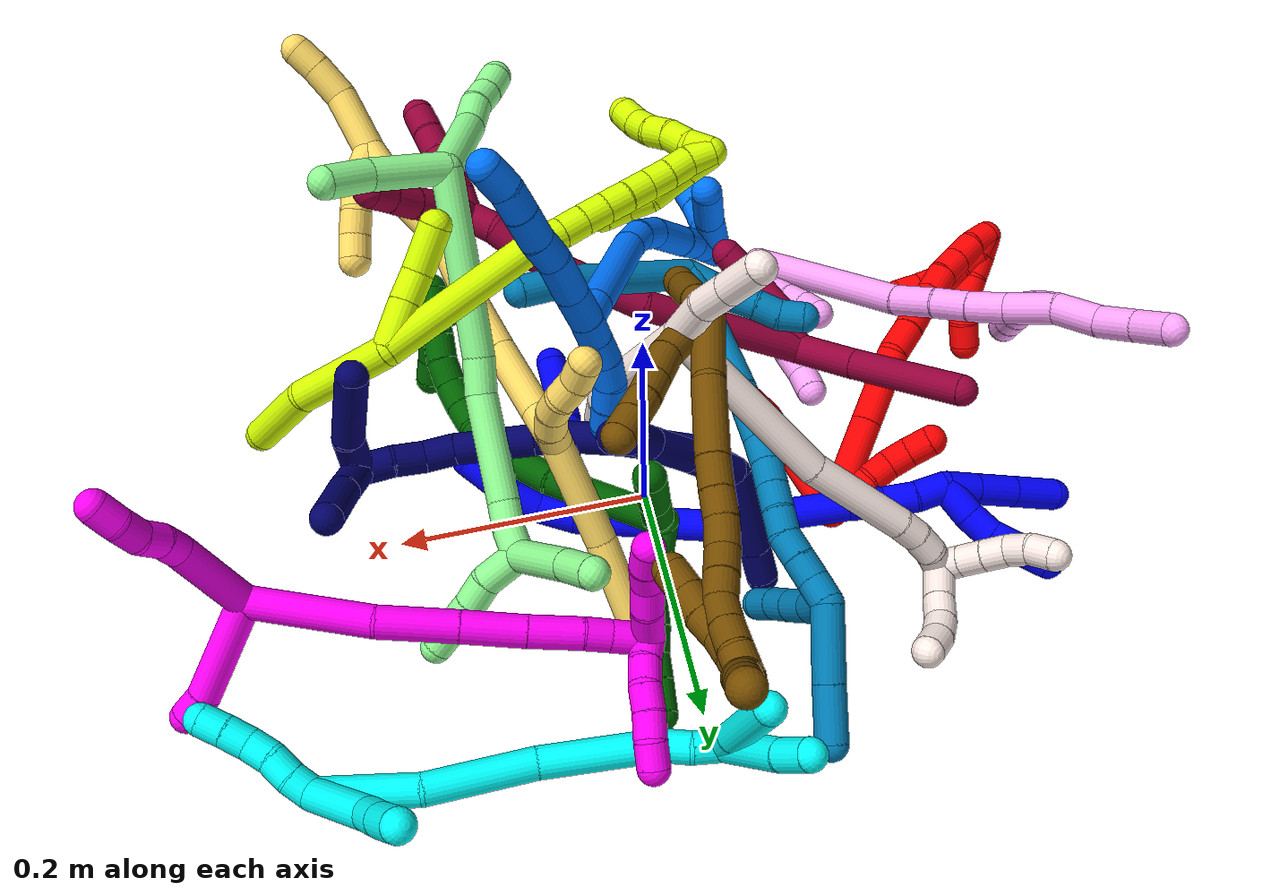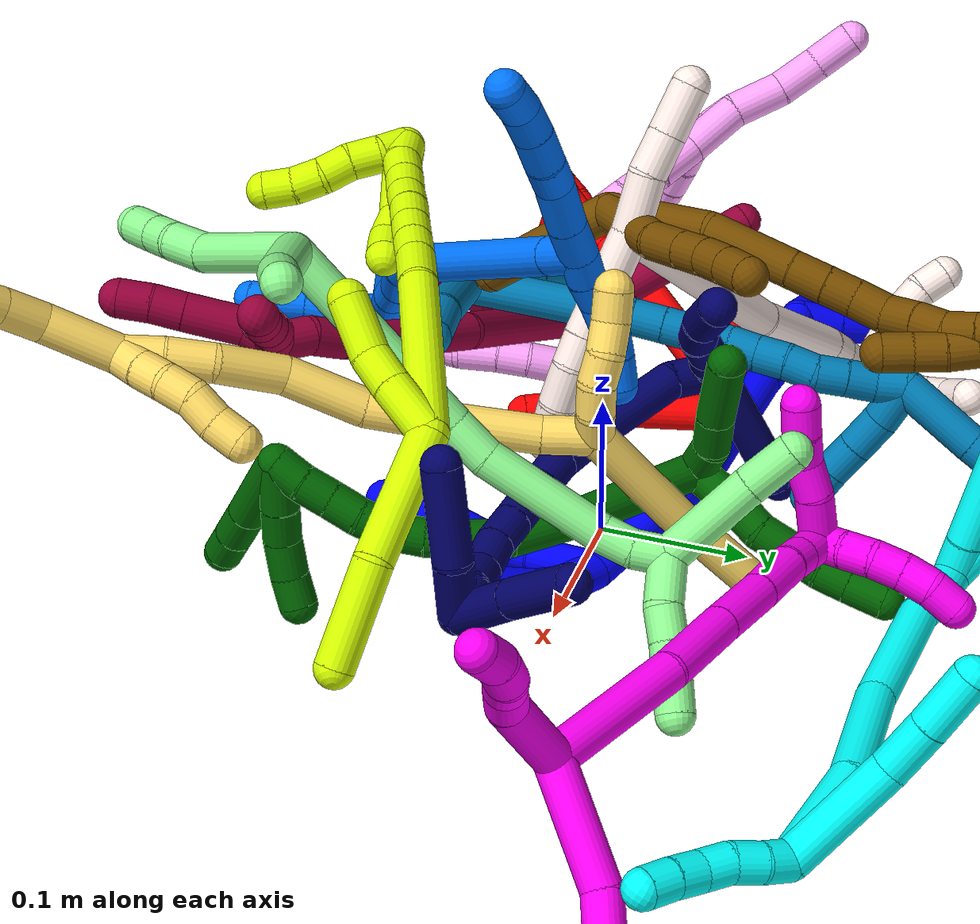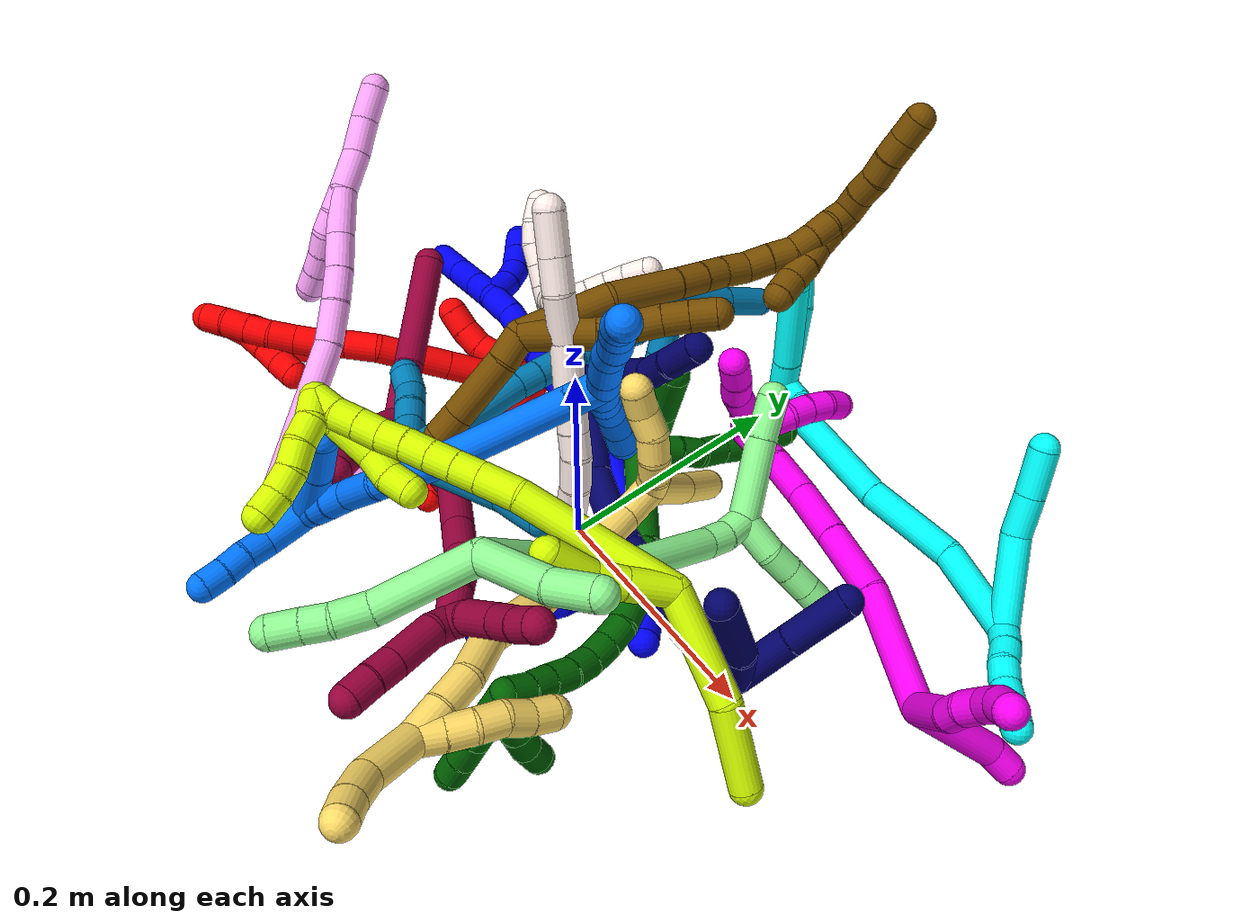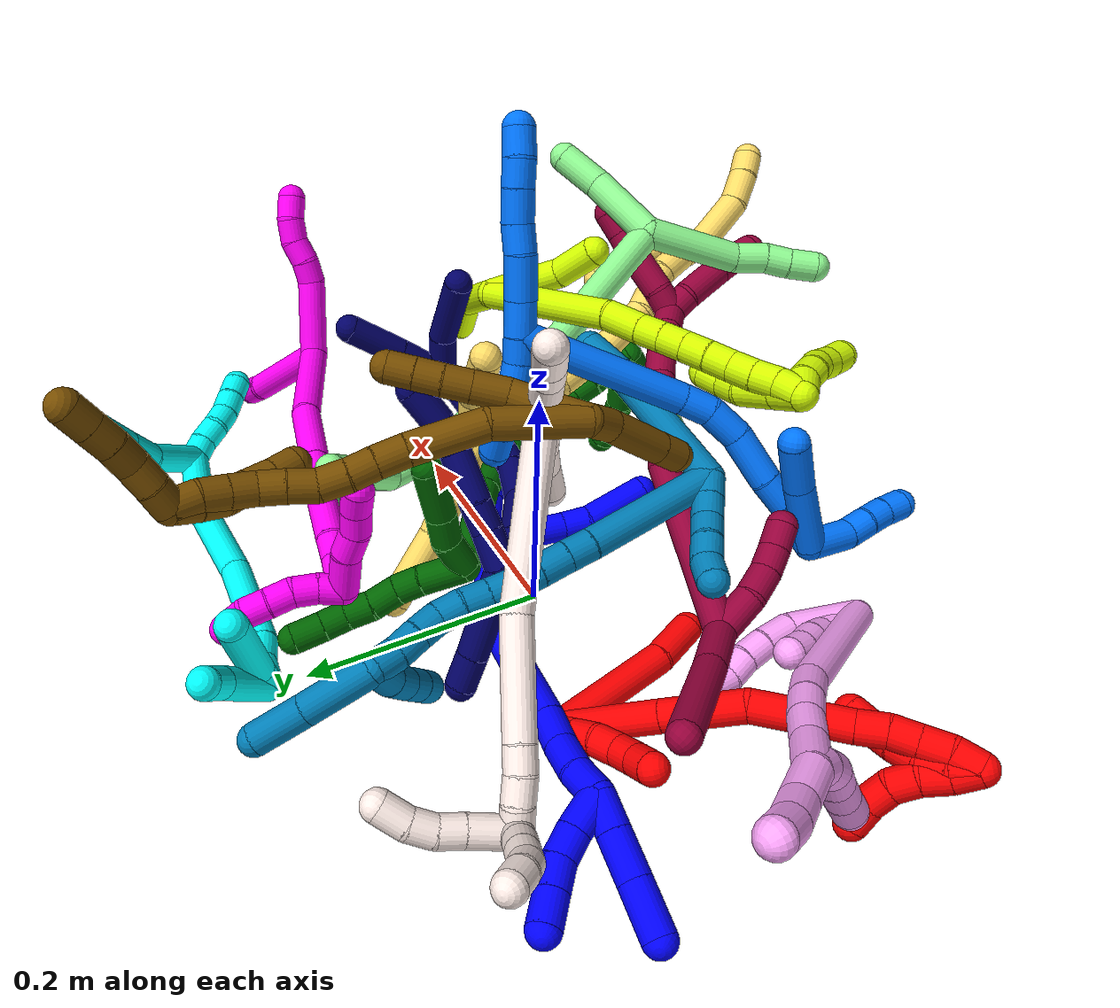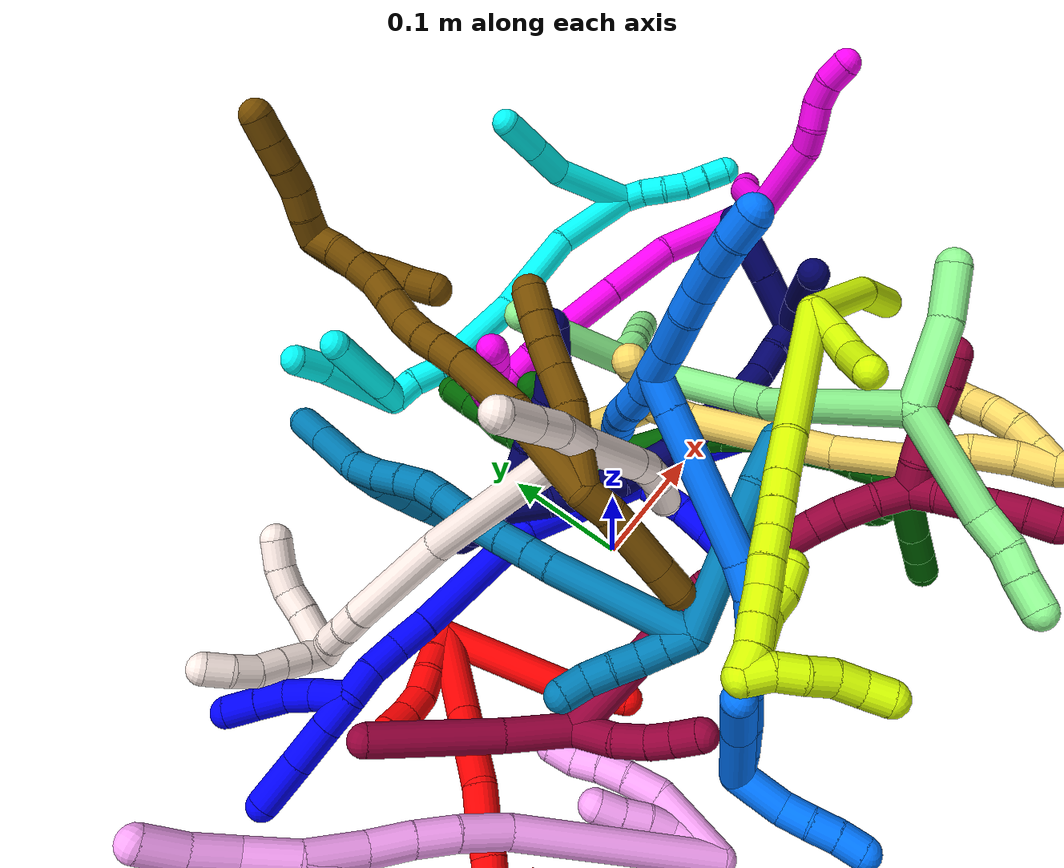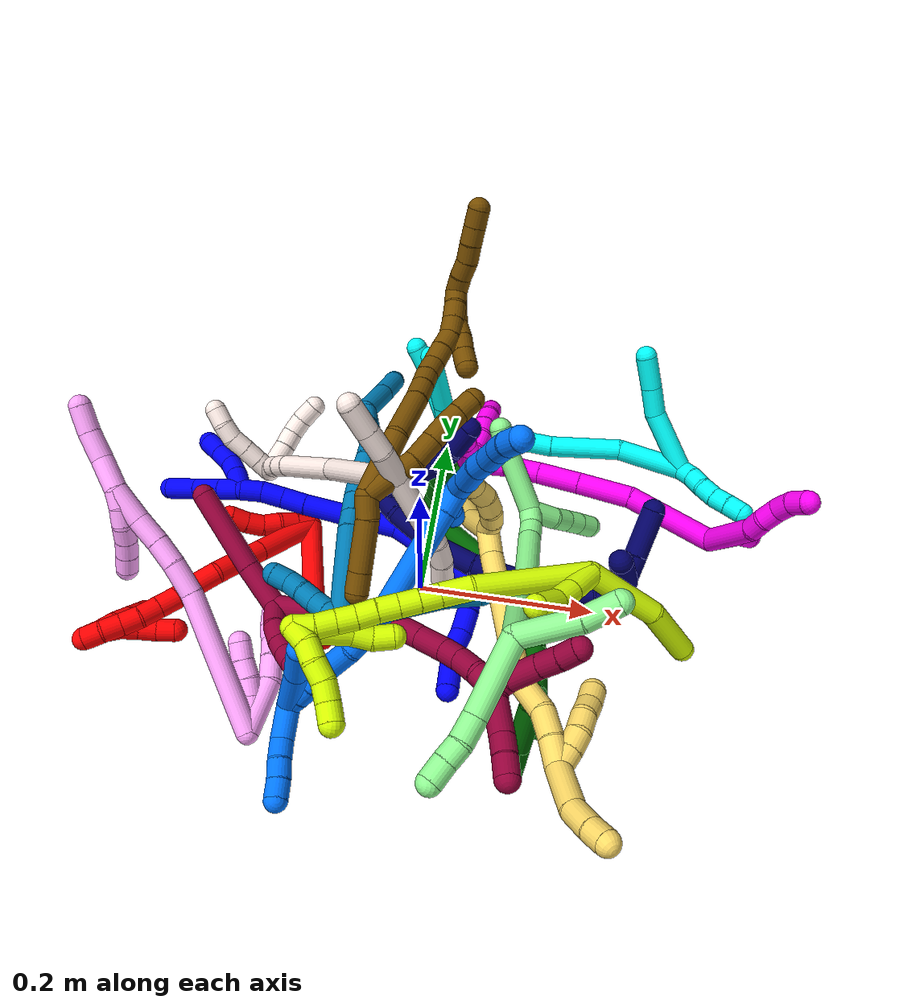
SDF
<sdf version="1.7">
 <world name="default">
  <plugin name="TubeGeneratorPlugin" filename="libtube_generator_plugin.so"/>
  <model name="photoneo_s_sensor">
   <static>1</static>
   <pose>0 0 2 1.57079 1.57079 3.14159</pose>
   <link name="link">
    <inertial><mass>0.1</mass></inertial>
    <sensor name="sensor" type="depth">
     <update_rate>30</update_rate>
     <camera>
      <horizontal_fov>1.22</horizontal_fov>
      <image><width>1920</width><height>1200</height><format>B8G8R8</format></image>
      <clip><near>0.1</near><far>4</far></clip>
      <depth_camera><output>points</output></depth_camera>
     </camera>
     <plugin name="camera_plugin" filename="libgazebo_ros_depth_camera.so">
      <baseline>0.2</baseline>
      <alwaysOn>1</alwaysOn>
      <updateRate>0.0</updateRate>
      <cameraName>camera_ir</cameraName>
      <imageTopicName>/camera/color/image_raw</imageTopicName>
      <cameraInfoTopicName>/camera/color/camera_info</cameraInfoTopicName>
      <depthImageTopicName>/camera/depth/image_raw</depthImageTopicName>
      <depthImageCameraInfoTopicName>/camera/depth/camera_info</depthImageCameraInfoTopicName>
      <pointCloudTopicName>/camera/depth/points</pointCloudTopicName>
      <frameName>fr_optical</frameName>
      <pointCloudCutoff>0.1</pointCloudCutoff>
      <pointCloudCutoffMax>2.0</pointCloudCutoffMax>
      <distortionK1>0</distortionK1>
      <distortionK2>0</distortionK2>
      <distortionK3>0</distortionK3>
      <distortionT1>0</distortionT1>
      <distortionT2>0</distortionT2>
      <CxPrime>0</CxPrime>
      <Cx>0</Cx>
      <Cy>0</Cy>
      <focalLength>0</focalLength>
      <hackBaseline>0</hackBaseline>
     </plugin>
    </sensor>
   </link>
  </model>
  <gravity>0 0 -9.8</gravity>
  <magnetic_field>6e-06 2.3e-05 -4.2e-05</magnetic_field>
  <atmosphere type="adiabatic"/>
  <physics name="default_physics" default="0" type="ode">
   <max_step_size>0.003</max_step_size>
   <real_time_factor>1</real_time_factor>
   <real_time_update_rate>1000</real_time_update_rate>
   <max_contacts>10000</max_contacts>
   <ode>
    <solver>
     <type>quick</type>
     <iters>100</iters>
     <sor>1.3</sor>
     <use_dynamic_moi_rescaling>0</use_dynamic_moi_rescaling>
    </solver>
    <constraints>
     <contact_max_correcting_vel>0</contact_max_correcting_vel>
     <contact_surface_layer>0.001</contact_surface_layer>
     <cfm>0</cfm>
     <erp>0.2</erp>
    </constraints>
   </ode>
  </physics>
  <scene><ambient>0.4 0.4 0.4 1</ambient><background>0.7 0.7 0.7 1</background><shadows>0</shadows></scene>
  <audio><device>default</device></audio>
  <spherical_coordinates>
   <surface_model>EARTH_WGS84</surface_model>
   <latitude_deg>0</latitude_deg>
   <longitude_deg>0</longitude_deg>
   <elevation>0</elevation>
   <heading_deg>0</heading_deg>
  </spherical_coordinates>
  <model name="bin">
   <static>1</static>
   <link name="bottom">
    <collision name="collision-bottom">
     <pose>0 0 -0.01 0 -0 0</pose>
     <geometry><box><size>0.8 0.6 0.02</size></box></geometry>
     <surface>
      <friction><ode><mu>100</mu><mu2>100</mu2></ode></friction>
      <contact><collide_bitmask>65535</collide_bitmask></contact>
     </surface>
    </collision>
   </link>
   <link name="west_wall">
    <collision name="collision-west_wall">
     <pose>-0.41 0 0.1 0 -0 0</pose>
     <geometry><box><size>0.02 0.6 0.2</size></box></geometry>
     <surface>
      <friction><ode><mu>100</mu><mu2>100</mu2></ode></friction>
      <contact><collide_bitmask>65535</collide_bitmask></contact>
     </surface>
    </collision>
   </link>
   <link name="east_wall">
    <collision name="collision-east_wall">
     <pose>0.41 0 0.1 0 -0 0</pose>
     <geometry><box><size>0.02 0.6 0.2</size></box></geometry>
     <surface>
      <friction><ode><mu>100</mu><mu2>100</mu2></ode></friction>
      <contact><collide_bitmask>65535</collide_bitmask></contact>
     </surface>
    </collision>
   </link>
   <link name="south_wall">
    <collision name="collision-south_wall">
     <pose>0 -0.31 0.1 0 -0 0</pose>
     <geometry><box><size>0.8 0.02 0.2</size></box></geometry>
     <surface>
      <friction><ode><mu>100</mu><mu2>100</mu2></ode></friction>
      <contact><collide_bitmask>65535</collide_bitmask></contact>
     </surface>
    </collision>
   </link>
   <link name="north_wall">
    <collision name="collision-north_wall">
     <pose>0 0.31 0.1 0 -0 0</pose>
     <geometry><box><size>0.8 0.02 0.2</size></box></geometry>
     <surface>
      <friction><ode><mu>100</mu><mu2>100</mu2></ode></friction>
      <contact><collide_bitmask>65535</collide_bitmask></contact>
     </surface>
    </collision>
   </link>
  </model>
  <model name="1">
   <static>0</static>
   <link name="1">
    <collision name="collision-cylinder-e_1_2_8">
     <pose>-0.011809 -0.014699 -0.010914 2.20951 -0.572869 -1.05946</pose>
     <geometry><cylinder><radius>0.0125</radius><length>0.043572</length></cylinder></geometry>
     <surface>
      <friction><ode><mu>1.16</mu><mu2>1.16</mu2><slip1>0</slip1><slip2>0</slip2></ode></friction>
      <contact><ode><kp>1e+06</kp><kd>1</kd><max_vel>0</max_vel><min_depth>0.001</min_depth></ode></contact>
     </surface>
    </collision>
    <visual name="visual-cylinder-e_1_2_8">
     <pose>-0.011809 -0.014699 -0.010914 2.20951 -0.572869 -1.05946</pose>
     <geometry><cylinder><radius>0.0125</radius><length>0.043572</length></cylinder></geometry>
     <material><ambient>0 0 1 1</ambient></material>
    </visual>
    <collision name="collision-cylinder-e_2_8_9">
     <pose>-0.032582 -0.038545 -0.027868 2.15431 -0.685498 -1.17115</pose>
     <geometry><cylinder><radius>0.0125</radius><length>0.02832</length></cylinder></geometry>
     <surface>
      <friction><ode><mu>1.16</mu><mu2>1.16</mu2><slip1>0</slip1><slip2>0</slip2></ode></friction>
      <contact><ode><kp>1e+06</kp><kd>1</kd><max_vel>0</max_vel><min_depth>0.001</min_depth></ode></contact>
     </surface>
    </collision>
    <visual name="visual-cylinder-e_2_8_9">
     <pose>-0.032582 -0.038545 -0.027868 2.15431 -0.685498 -1.17115</pose>
     <geometry><cylinder><radius>0.0125</radius><length>0.02832</length></cylinder></geometry>
     <material><ambient>0 0 1 1</ambient></material>
    </visual>
    <collision name="collision-cylinder-e_3_9_10">
     <pose>-0.048437 -0.056595 -0.036994 1.90456 -0.631457 -0.860624</pose>
     <geometry><cylinder><radius>0.0125</radius><length>0.023348</length></cylinder></geometry>
     <surface>
      <friction><ode><mu>1.16</mu><mu2>1.16</mu2><slip1>0</slip1><slip2>0</slip2></ode></friction>
      <contact><ode><kp>1e+06</kp><kd>1</kd><max_vel>0</max_vel><min_depth>0.001</min_depth></ode></contact>
     </surface>
    </collision>
    <visual name="visual-cylinder-e_3_9_10">
     <pose>-0.048437 -0.056595 -0.036994 1.90456 -0.631457 -0.860624</pose>
     <geometry><cylinder><radius>0.0125</radius><length>0.023348</length></cylinder></geometry>
     <material><ambient>0 0 1 1</ambient></material>
    </visual>
    <collision name="collision-cylinder-e_4_10_6">
     <pose>-0.065901 -0.087338 -0.052767 2.09702 -0.396439 -0.671484</pose>
     <geometry><cylinder><radius>0.0125</radius><length>0.054761</length></cylinder></geometry>
     <surface>
      <friction><ode><mu>1.16</mu><mu2>1.16</mu2><slip1>0</slip1><slip2>0</slip2></ode></friction>
      <contact><ode><kp>1e+06</kp><kd>1</kd><max_vel>0</max_vel><min_depth>0.001</min_depth></ode></contact>
     </surface>
    </collision>
    <visual name="visual-cylinder-e_4_10_6">
     <pose>-0.065901 -0.087338 -0.052767 2.09702 -0.396439 -0.671484</pose>
     <geometry><cylinder><radius>0.0125</radius><length>0.054761</length></cylinder></geometry>
     <material><ambient>0 0 1 1</ambient></material>
    </visual>
    <collision name="collision-cylinder-e_1_2_11">
     <pose>0.006133 -0.004589 -0.013964 2.82409 0.395288 1.79278</pose>
     <geometry><cylinder><radius>0.0125</radius><length>0.031855</length></cylinder></geometry>
     <surface>
      <friction><ode><mu>1.16</mu><mu2>1.16</mu2><slip1>0</slip1><slip2>0</slip2></ode></friction>
      <contact><ode><kp>1e+06</kp><kd>1</kd><max_vel>0</max_vel><min_depth>0.001</min_depth></ode></contact>
     </surface>
    </collision>
    <visual name="visual-cylinder-e_1_2_11">
     <pose>0.006133 -0.004589 -0.013964 2.82409 0.395288 1.79278</pose>
     <geometry><cylinder><radius>0.0125</radius><length>0.031855</length></cylinder></geometry>
     <material><ambient>0 0 1 1</ambient></material>
    </visual>
    <collision name="collision-cylinder-e_2_11_12">
     <pose>0.017305 -0.014822 -0.036734 2.57154 0.448974 1.32398</pose>
     <geometry><cylinder><radius>0.0125</radius><length>0.023218</length></cylinder></geometry>
     <surface>
      <friction><ode><mu>1.16</mu><mu2>1.16</mu2><slip1>0</slip1><slip2>0</slip2></ode></friction>
      <contact><ode><kp>1e+06</kp><kd>1</kd><max_vel>0</max_vel><min_depth>0.001</min_depth></ode></contact>
     </surface>
    </collision>
    <visual name="visual-cylinder-e_2_11_12">
     <pose>0.017305 -0.014822 -0.036734 2.57154 0.448974 1.32398</pose>
     <geometry><cylinder><radius>0.0125</radius><length>0.023218</length></cylinder></geometry>
     <material><ambient>0 0 1 1</ambient></material>
    </visual>
    <collision name="collision-cylinder-e_3_12_5">
     <pose>0.028456 -0.034468 -0.062007 2.43697 0.275578 0.721348</pose>
     <geometry><cylinder><radius>0.0125</radius><length>0.044927</length></cylinder></geometry>
     <surface>
      <friction><ode><mu>1.16</mu><mu2>1.16</mu2><slip1>0</slip1><slip2>0</slip2></ode></friction>
      <contact><ode><kp>1e+06</kp><kd>1</kd><max_vel>0</max_vel><min_depth>0.001</min_depth></ode></contact>
     </surface>
    </collision>
    <visual name="visual-cylinder-e_3_12_5">
     <pose>0.028456 -0.034468 -0.062007 2.43697 0.275578 0.721348</pose>
     <geometry><cylinder><radius>0.0125</radius><length>0.044927</length></cylinder></geometry>
     <material><ambient>0 0 1 1</ambient></material>
    </visual>
    <collision name="collision-cylinder-e_1_2_13">
     <pose>-0.012268 0.000276 0.053133 -0.00519 -0.226919 0.000591</pose>
     <geometry><cylinder><radius>0.0125</radius><length>0.109064</length></cylinder></geometry>
     <surface>
      <friction><ode><mu>1.16</mu><mu2>1.16</mu2><slip1>0</slip1><slip2>0</slip2></ode></friction>
      <contact><ode><kp>1e+06</kp><kd>1</kd><max_vel>0</max_vel><min_depth>0.001</min_depth></ode></contact>
     </surface>
    </collision>
    <visual name="visual-cylinder-e_1_2_13">
     <pose>-0.012268 0.000276 0.053133 -0.00519 -0.226919 0.000591</pose>
     <geometry><cylinder><radius>0.0125</radius><length>0.109064</length></cylinder></geometry>
     <material><ambient>0 0 1 1</ambient></material>
    </visual>
    <collision name="collision-cylinder-e_2_13_14">
     <pose>-0.053819 -0.005195 0.153213 0.121792 -0.554359 -0.03469</pose>
     <geometry><cylinder><radius>0.0125</radius><length>0.111255</length></cylinder></geometry>
     <surface>
      <friction><ode><mu>1.16</mu><mu2>1.16</mu2><slip1>0</slip1><slip2>0</slip2></ode></friction>
      <contact><ode><kp>1e+06</kp><kd>1</kd><max_vel>0</max_vel><min_depth>0.001</min_depth></ode></contact>
     </surface>
    </collision>
    <visual name="visual-cylinder-e_2_13_14">
     <pose>-0.053819 -0.005195 0.153213 0.121792 -0.554359 -0.03469</pose>
     <geometry><cylinder><radius>0.0125</radius><length>0.111255</length></cylinder></geometry>
     <material><ambient>0 0 1 1</ambient></material>
    </visual>
    <collision name="collision-cylinder-e_3_14_15">
     <pose>-0.089964 -0.011562 0.212323 0.050997 -0.513098 -0.013381</pose>
     <geometry><cylinder><radius>0.0125</radius><length>0.02796</length></cylinder></geometry>
     <surface>
      <friction><ode><mu>1.16</mu><mu2>1.16</mu2><slip1>0</slip1><slip2>0</slip2></ode></friction>
      <contact><ode><kp>1e+06</kp><kd>1</kd><max_vel>0</max_vel><min_depth>0.001</min_depth></ode></contact>
     </surface>
    </collision>
    <visual name="visual-cylinder-e_3_14_15">
     <pose>-0.089964 -0.011562 0.212323 0.050997 -0.513098 -0.013381</pose>
     <geometry><cylinder><radius>0.0125</radius><length>0.02796</length></cylinder></geometry>
     <material><ambient>0 0 1 1</ambient></material>
    </visual>
    <collision name="collision-cylinder-e_4_15_16">
     <pose>-0.103197 -0.014058 0.235852 0.163593 -0.505199 -0.042314</pose>
     <geometry><cylinder><radius>0.0125</radius><length>0.026327</length></cylinder></geometry>
     <surface>
      <friction><ode><mu>1.16</mu><mu2>1.16</mu2><slip1>0</slip1><slip2>0</slip2></ode></friction>
      <contact><ode><kp>1e+06</kp><kd>1</kd><max_vel>0</max_vel><min_depth>0.001</min_depth></ode></contact>
     </surface>
    </collision>
    <visual name="visual-cylinder-e_4_15_16">
     <pose>-0.103197 -0.014058 0.235852 0.163593 -0.505199 -0.042314</pose>
     <geometry><cylinder><radius>0.0125</radius><length>0.026327</length></cylinder></geometry>
     <material><ambient>0 0 1 1</ambient></material>
    </visual>
    <collision name="collision-cylinder-e_5_16_1">
     <pose>-0.117287 -0.01916 0.256769 0.325667 -0.653432 -0.111226</pose>
     <geometry><cylinder><radius>0.0125</radius><length>0.025394</length></cylinder></geometry>
     <surface>
      <friction><ode><mu>1.16</mu><mu2>1.16</mu2><slip1>0</slip1><slip2>0</slip2></ode></friction>
      <contact><ode><kp>1e+06</kp><kd>1</kd><max_vel>0</max_vel><min_depth>0.001</min_depth></ode></contact>
     </surface>
    </collision>
    <visual name="visual-cylinder-e_5_16_1">
     <pose>-0.117287 -0.01916 0.256769 0.325667 -0.653432 -0.111226</pose>
     <geometry><cylinder><radius>0.0125</radius><length>0.025394</length></cylinder></geometry>
     <material><ambient>0 0 1 1</ambient></material>
    </visual>
    <collision name="collision-cylinder-e_1_1_17">
     <pose>-0.134569 -0.020011 0.27536 -0.256853 -0.796923 0.108622</pose>
     <geometry><cylinder><radius>0.0125</radius><length>0.026744</length></cylinder></geometry>
     <surface>
      <friction><ode><mu>1.16</mu><mu2>1.16</mu2><slip1>0</slip1><slip2>0</slip2></ode></friction>
      <contact><ode><kp>1e+06</kp><kd>1</kd><max_vel>0</max_vel><min_depth>0.001</min_depth></ode></contact>
     </surface>
    </collision>
    <visual name="visual-cylinder-e_1_1_17">
     <pose>-0.134569 -0.020011 0.27536 -0.256853 -0.796923 0.108622</pose>
     <geometry><cylinder><radius>0.0125</radius><length>0.026744</length></cylinder></geometry>
     <material><ambient>0 0 1 1</ambient></material>
    </visual>
    <collision name="collision-cylinder-e_2_17_18">
     <pose>-0.156495 -0.014634 0.295782 -0.257952 -0.809848 0.111063</pose>
     <geometry><cylinder><radius>0.0125</radius><length>0.034142</length></cylinder></geometry>
     <surface>
      <friction><ode><mu>1.16</mu><mu2>1.16</mu2><slip1>0</slip1><slip2>0</slip2></ode></friction>
      <contact><ode><kp>1e+06</kp><kd>1</kd><max_vel>0</max_vel><min_depth>0.001</min_depth></ode></contact>
     </surface>
    </collision>
    <visual name="visual-cylinder-e_2_17_18">
     <pose>-0.156495 -0.014634 0.295782 -0.257952 -0.809848 0.111063</pose>
     <geometry><cylinder><radius>0.0125</radius><length>0.034142</length></cylinder></geometry>
     <material><ambient>0 0 1 1</ambient></material>
    </visual>
    <collision name="collision-cylinder-e_3_18_4">
     <pose>-0.182864 -0.00818 0.320371 -0.255618 -0.798288 0.108301</pose>
     <geometry><cylinder><radius>0.0125</radius><length>0.039114</length></cylinder></geometry>
     <surface>
      <friction><ode><mu>1.16</mu><mu2>1.16</mu2><slip1>0</slip1><slip2>0</slip2></ode></friction>
      <contact><ode><kp>1e+06</kp><kd>1</kd><max_vel>0</max_vel><min_depth>0.001</min_depth></ode></contact>
     </surface>
    </collision>
    <visual name="visual-cylinder-e_3_18_4">
     <pose>-0.182864 -0.00818 0.320371 -0.255618 -0.798288 0.108301</pose>
     <geometry><cylinder><radius>0.0125</radius><length>0.039114</length></cylinder></geometry>
     <material><ambient>0 0 1 1</ambient></material>
    </visual>
    <collision name="collision-cylinder-e_1_1_19">
     <pose>-0.124561 -0.011668 0.276417 -0.815252 0.030137 -0.013014</pose>
     <geometry><cylinder><radius>0.0125</radius><length>0.029462</length></cylinder></geometry>
     <surface>
      <friction><ode><mu>1.16</mu><mu2>1.16</mu2><slip1>0</slip1><slip2>0</slip2></ode></friction>
      <contact><ode><kp>1e+06</kp><kd>1</kd><max_vel>0</max_vel><min_depth>0.001</min_depth></ode></contact>
     </surface>
    </collision>
    <visual name="visual-cylinder-e_1_1_19">
     <pose>-0.124561 -0.011668 0.276417 -0.815252 0.030137 -0.013014</pose>
     <geometry><cylinder><radius>0.0125</radius><length>0.029462</length></cylinder></geometry>
     <material><ambient>0 0 1 1</ambient></material>
    </visual>
    <collision name="collision-cylinder-e_2_19_20">
     <pose>-0.124427 0.006012 0.2953 -0.66999 -0.027562 0.009595</pose>
     <geometry><cylinder><radius>0.0125</radius><length>0.022429</length></cylinder></geometry>
     <surface>
      <friction><ode><mu>1.16</mu><mu2>1.16</mu2><slip1>0</slip1><slip2>0</slip2></ode></friction>
      <contact><ode><kp>1e+06</kp><kd>1</kd><max_vel>0</max_vel><min_depth>0.001</min_depth></ode></contact>
     </surface>
    </collision>
    <visual name="visual-cylinder-e_2_19_20">
     <pose>-0.124427 0.006012 0.2953 -0.66999 -0.027562 0.009595</pose>
     <geometry><cylinder><radius>0.0125</radius><length>0.022429</length></cylinder></geometry>
     <material><ambient>0 0 1 1</ambient></material>
    </visual>
    <collision name="collision-cylinder-e_3_20_21">
     <pose>-0.126819 0.017769 0.314496 -0.431735 -0.179832 0.039536</pose>
     <geometry><cylinder><radius>0.0125</radius><length>0.023297</length></cylinder></geometry>
     <surface>
      <friction><ode><mu>1.16</mu><mu2>1.16</mu2><slip1>0</slip1><slip2>0</slip2></ode></friction>
      <contact><ode><kp>1e+06</kp><kd>1</kd><max_vel>0</max_vel><min_depth>0.001</min_depth></ode></contact>
     </surface>
    </collision>
    <visual name="visual-cylinder-e_3_20_21">
     <pose>-0.126819 0.017769 0.314496 -0.431735 -0.179832 0.039536</pose>
     <geometry><cylinder><radius>0.0125</radius><length>0.023297</length></cylinder></geometry>
     <material><ambient>0 0 1 1</ambient></material>
    </visual>
    <collision name="collision-cylinder-e_4_21_3">
     <pose>-0.131364 0.027769 0.335895 -0.442277 -0.199694 0.045036</pose>
     <geometry><cylinder><radius>0.0125</radius><length>0.024812</length></cylinder></geometry>
     <surface>
      <friction><ode><mu>1.16</mu><mu2>1.16</mu2><slip1>0</slip1><slip2>0</slip2></ode></friction>
      <contact><ode><kp>1e+06</kp><kd>1</kd><max_vel>0</max_vel><min_depth>0.001</min_depth></ode></contact>
     </surface>
    </collision>
    <visual name="visual-cylinder-e_4_21_3">
     <pose>-0.131364 0.027769 0.335895 -0.442277 -0.199694 0.045036</pose>
     <geometry><cylinder><radius>0.0125</radius><length>0.024812</length></cylinder></geometry>
     <material><ambient>0 0 1 1</ambient></material>
    </visual>
    <collision name="collision-sphere-3">
     <pose>-0.133825 0.032973 0.346884 0 -0 0</pose>
     <geometry><sphere><radius>0.0125</radius></sphere></geometry>
     <surface>
      <friction><ode><mu>1.16</mu><mu2>1.16</mu2><slip1>0</slip1><slip2>0</slip2></ode></friction>
      <contact><ode><kp>1e+06</kp><kd>1</kd><max_vel>0</max_vel><min_depth>0.001</min_depth></ode></contact>
     </surface>
    </collision>
    <visual name="visual-sphere-3">
     <pose>-0.133825 0.032973 0.346884 0 -0 0</pose>
     <geometry><sphere><radius>0.0125</radius></sphere></geometry>
     <material><ambient>0 0 1 1</ambient></material>
    </visual>
    <collision name="collision-sphere-21">
     <pose>-0.128903 0.022564 0.324905 0 -0 0</pose>
     <geometry><sphere><radius>0.0125</radius></sphere></geometry>
     <surface>
      <friction><ode><mu>1.16</mu><mu2>1.16</mu2><slip1>0</slip1><slip2>0</slip2></ode></friction>
      <contact><ode><kp>1e+06</kp><kd>1</kd><max_vel>0</max_vel><min_depth>0.001</min_depth></ode></contact>
     </surface>
    </collision>
    <visual name="visual-sphere-21">
     <pose>-0.128903 0.022564 0.324905 0 -0 0</pose>
     <geometry><sphere><radius>0.0125</radius></sphere></geometry>
     <material><ambient>0 0 1 1</ambient></material>
    </visual>
    <collision name="collision-sphere-20">
     <pose>-0.124736 0.012973 0.304087 0 -0 0</pose>
     <geometry><sphere><radius>0.0125</radius></sphere></geometry>
     <surface>
      <friction><ode><mu>1.16</mu><mu2>1.16</mu2><slip1>0</slip1><slip2>0</slip2></ode></friction>
      <contact><ode><kp>1e+06</kp><kd>1</kd><max_vel>0</max_vel><min_depth>0.001</min_depth></ode></contact>
     </surface>
    </collision>
    <visual name="visual-sphere-20">
     <pose>-0.124736 0.012973 0.304087 0 -0 0</pose>
     <geometry><sphere><radius>0.0125</radius></sphere></geometry>
     <material><ambient>0 0 1 1</ambient></material>
    </visual>
    <collision name="collision-sphere-19">
     <pose>-0.124118 -0.00095 0.286514 0 -0 0</pose>
     <geometry><sphere><radius>0.0125</radius></sphere></geometry>
     <surface>
      <friction><ode><mu>1.16</mu><mu2>1.16</mu2><slip1>0</slip1><slip2>0</slip2></ode></friction>
      <contact><ode><kp>1e+06</kp><kd>1</kd><max_vel>0</max_vel><min_depth>0.001</min_depth></ode></contact>
     </surface>
    </collision>
    <visual name="visual-sphere-19">
     <pose>-0.124118 -0.00095 0.286514 0 -0 0</pose>
     <geometry><sphere><radius>0.0125</radius></sphere></geometry>
     <material><ambient>0 0 1 1</ambient></material>
    </visual>
    <collision name="collision-sphere-11">
     <pose>0.012266 -0.009178 -0.027929 0 -0 0</pose>
     <geometry><sphere><radius>0.0125</radius></sphere></geometry>
     <surface>
      <friction><ode><mu>1.16</mu><mu2>1.16</mu2><slip1>0</slip1><slip2>0</slip2></ode></friction>
      <contact><ode><kp>1e+06</kp><kd>1</kd><max_vel>0</max_vel><min_depth>0.001</min_depth></ode></contact>
     </surface>
    </collision>
    <visual name="visual-sphere-11">
     <pose>0.012266 -0.009178 -0.027929 0 -0 0</pose>
     <geometry><sphere><radius>0.0125</radius></sphere></geometry>
     <material><ambient>0 0 1 1</ambient></material>
    </visual>
    <collision name="collision-sphere-6">
     <pose>-0.076474 -0.109177 -0.065452 0 -0 0</pose>
     <geometry><sphere><radius>0.0125</radius></sphere></geometry>
     <surface>
      <friction><ode><mu>1.16</mu><mu2>1.16</mu2><slip1>0</slip1><slip2>0</slip2></ode></friction>
      <contact><ode><kp>1e+06</kp><kd>1</kd><max_vel>0</max_vel><min_depth>0.001</min_depth></ode></contact>
     </surface>
    </collision>
    <visual name="visual-sphere-6">
     <pose>-0.076474 -0.109177 -0.065452 0 -0 0</pose>
     <geometry><sphere><radius>0.0125</radius></sphere></geometry>
     <material><ambient>0 0 1 1</ambient></material>
    </visual>
    <collision name="collision-sphere-10">
     <pose>-0.055329 -0.065498 -0.040081 0 -0 0</pose>
     <geometry><sphere><radius>0.0125</radius></sphere></geometry>
     <surface>
      <friction><ode><mu>1.16</mu><mu2>1.16</mu2><slip1>0</slip1><slip2>0</slip2></ode></friction>
      <contact><ode><kp>1e+06</kp><kd>1</kd><max_vel>0</max_vel><min_depth>0.001</min_depth></ode></contact>
     </surface>
    </collision>
    <visual name="visual-sphere-10">
     <pose>-0.055329 -0.065498 -0.040081 0 -0 0</pose>
     <geometry><sphere><radius>0.0125</radius></sphere></geometry>
     <material><ambient>0 0 1 1</ambient></material>
    </visual>
    <collision name="collision-sphere-9">
     <pose>-0.041546 -0.047692 -0.033907 0 -0 0</pose>
     <geometry><sphere><radius>0.0125</radius></sphere></geometry>
     <surface>
      <friction><ode><mu>1.16</mu><mu2>1.16</mu2><slip1>0</slip1><slip2>0</slip2></ode></friction>
      <contact><ode><kp>1e+06</kp><kd>1</kd><max_vel>0</max_vel><min_depth>0.001</min_depth></ode></contact>
     </surface>
    </collision>
    <visual name="visual-sphere-9">
     <pose>-0.041546 -0.047692 -0.033907 0 -0 0</pose>
     <geometry><sphere><radius>0.0125</radius></sphere></geometry>
     <material><ambient>0 0 1 1</ambient></material>
    </visual>
    <collision name="collision-sphere-2">
     <geometry><sphere><radius>0.0125</radius></sphere></geometry>
     <surface>
      <friction><ode><mu>1.16</mu><mu2>1.16</mu2><slip1>0</slip1><slip2>0</slip2></ode></friction>
      <contact><ode><kp>1e+06</kp><kd>1</kd><max_vel>0</max_vel><min_depth>0.001</min_depth></ode></contact>
     </surface>
    </collision>
    <visual name="visual-sphere-2">
     <geometry><sphere><radius>0.0125</radius></sphere></geometry>
     <material><ambient>0 0 1 1</ambient></material>
    </visual>
    <collision name="collision-sphere-8">
     <pose>-0.023618 -0.029397 -0.021829 0 -0 0</pose>
     <geometry><sphere><radius>0.0125</radius></sphere></geometry>
     <surface>
      <friction><ode><mu>1.16</mu><mu2>1.16</mu2><slip1>0</slip1><slip2>0</slip2></ode></friction>
      <contact><ode><kp>1e+06</kp><kd>1</kd><max_vel>0</max_vel><min_depth>0.001</min_depth></ode></contact>
     </surface>
    </collision>
    <visual name="visual-sphere-8">
     <pose>-0.023618 -0.029397 -0.021829 0 -0 0</pose>
     <geometry><sphere><radius>0.0125</radius></sphere></geometry>
     <material><ambient>0 0 1 1</ambient></material>
    </visual>
    <collision name="collision-sphere-12">
     <pose>0.022344 -0.020466 -0.045538 0 -0 0</pose>
     <geometry><sphere><radius>0.0125</radius></sphere></geometry>
     <surface>
      <friction><ode><mu>1.16</mu><mu2>1.16</mu2><slip1>0</slip1><slip2>0</slip2></ode></friction>
      <contact><ode><kp>1e+06</kp><kd>1</kd><max_vel>0</max_vel><min_depth>0.001</min_depth></ode></contact>
     </surface>
    </collision>
    <visual name="visual-sphere-12">
     <pose>0.022344 -0.020466 -0.045538 0 -0 0</pose>
     <geometry><sphere><radius>0.0125</radius></sphere></geometry>
     <material><ambient>0 0 1 1</ambient></material>
    </visual>
    <collision name="collision-sphere-5">
     <pose>0.034569 -0.04847 -0.078475 0 -0 0</pose>
     <geometry><sphere><radius>0.0125</radius></sphere></geometry>
     <surface>
      <friction><ode><mu>1.16</mu><mu2>1.16</mu2><slip1>0</slip1><slip2>0</slip2></ode></friction>
      <contact><ode><kp>1e+06</kp><kd>1</kd><max_vel>0</max_vel><min_depth>0.001</min_depth></ode></contact>
     </surface>
    </collision>
    <visual name="visual-sphere-5">
     <pose>0.034569 -0.04847 -0.078475 0 -0 0</pose>
     <geometry><sphere><radius>0.0125</radius></sphere></geometry>
     <material><ambient>0 0 1 1</ambient></material>
    </visual>
    <collision name="collision-sphere-13">
     <pose>-0.024537 0.000552 0.106267 0 -0 0</pose>
     <geometry><sphere><radius>0.0125</radius></sphere></geometry>
     <surface>
      <friction><ode><mu>1.16</mu><mu2>1.16</mu2><slip1>0</slip1><slip2>0</slip2></ode></friction>
      <contact><ode><kp>1e+06</kp><kd>1</kd><max_vel>0</max_vel><min_depth>0.001</min_depth></ode></contact>
     </surface>
    </collision>
    <visual name="visual-sphere-13">
     <pose>-0.024537 0.000552 0.106267 0 -0 0</pose>
     <geometry><sphere><radius>0.0125</radius></sphere></geometry>
     <material><ambient>0 0 1 1</ambient></material>
    </visual>
    <collision name="collision-sphere-14">
     <pose>-0.083101 -0.010941 0.200159 0 -0 0</pose>
     <geometry><sphere><radius>0.0125</radius></sphere></geometry>
     <surface>
      <friction><ode><mu>1.16</mu><mu2>1.16</mu2><slip1>0</slip1><slip2>0</slip2></ode></friction>
      <contact><ode><kp>1e+06</kp><kd>1</kd><max_vel>0</max_vel><min_depth>0.001</min_depth></ode></contact>
     </surface>
    </collision>
    <visual name="visual-sphere-14">
     <pose>-0.083101 -0.010941 0.200159 0 -0 0</pose>
     <geometry><sphere><radius>0.0125</radius></sphere></geometry>
     <material><ambient>0 0 1 1</ambient></material>
    </visual>
    <collision name="collision-sphere-15">
     <pose>-0.096826 -0.012182 0.224487 0 -0 0</pose>
     <geometry><sphere><radius>0.0125</radius></sphere></geometry>
     <surface>
      <friction><ode><mu>1.16</mu><mu2>1.16</mu2><slip1>0</slip1><slip2>0</slip2></ode></friction>
      <contact><ode><kp>1e+06</kp><kd>1</kd><max_vel>0</max_vel><min_depth>0.001</min_depth></ode></contact>
     </surface>
    </collision>
    <visual name="visual-sphere-15">
     <pose>-0.096826 -0.012182 0.224487 0 -0 0</pose>
     <geometry><sphere><radius>0.0125</radius></sphere></geometry>
     <material><ambient>0 0 1 1</ambient></material>
    </visual>
    <collision name="collision-sphere-16">
     <pose>-0.109568 -0.015935 0.247218 0 -0 0</pose>
     <geometry><sphere><radius>0.0125</radius></sphere></geometry>
     <surface>
      <friction><ode><mu>1.16</mu><mu2>1.16</mu2><slip1>0</slip1><slip2>0</slip2></ode></friction>
      <contact><ode><kp>1e+06</kp><kd>1</kd><max_vel>0</max_vel><min_depth>0.001</min_depth></ode></contact>
     </surface>
    </collision>
    <visual name="visual-sphere-16">
     <pose>-0.109568 -0.015935 0.247218 0 -0 0</pose>
     <geometry><sphere><radius>0.0125</radius></sphere></geometry>
     <material><ambient>0 0 1 1</ambient></material>
    </visual>
    <collision name="collision-sphere-1">
     <pose>-0.125005 -0.022385 0.266321 0 -0 0</pose>
     <geometry><sphere><radius>0.0125</radius></sphere></geometry>
     <surface>
      <friction><ode><mu>1.16</mu><mu2>1.16</mu2><slip1>0</slip1><slip2>0</slip2></ode></friction>
      <contact><ode><kp>1e+06</kp><kd>1</kd><max_vel>0</max_vel><min_depth>0.001</min_depth></ode></contact>
     </surface>
    </collision>
    <visual name="visual-sphere-1">
     <pose>-0.125005 -0.022385 0.266321 0 -0 0</pose>
     <geometry><sphere><radius>0.0125</radius></sphere></geometry>
     <material><ambient>0 0 1 1</ambient></material>
    </visual>
    <collision name="collision-sphere-18">
     <pose>-0.168858 -0.011631 0.307165 0 -0 0</pose>
     <geometry><sphere><radius>0.0125</radius></sphere></geometry>
     <surface>
      <friction><ode><mu>1.16</mu><mu2>1.16</mu2><slip1>0</slip1><slip2>0</slip2></ode></friction>
      <contact><ode><kp>1e+06</kp><kd>1</kd><max_vel>0</max_vel><min_depth>0.001</min_depth></ode></contact>
     </surface>
    </collision>
    <visual name="visual-sphere-18">
     <pose>-0.168858 -0.011631 0.307165 0 -0 0</pose>
     <geometry><sphere><radius>0.0125</radius></sphere></geometry>
     <material><ambient>0 0 1 1</ambient></material>
    </visual>
    <collision name="collision-sphere-17">
     <pose>-0.144133 -0.017637 0.284399 0 -0 0</pose>
     <geometry><sphere><radius>0.0125</radius></sphere></geometry>
     <surface>
      <friction><ode><mu>1.16</mu><mu2>1.16</mu2><slip1>0</slip1><slip2>0</slip2></ode></friction>
      <contact><ode><kp>1e+06</kp><kd>1</kd><max_vel>0</max_vel><min_depth>0.001</min_depth></ode></contact>
     </surface>
    </collision>
    <visual name="visual-sphere-17">
     <pose>-0.144133 -0.017637 0.284399 0 -0 0</pose>
     <geometry><sphere><radius>0.0125</radius></sphere></geometry>
     <material><ambient>0 0 1 1</ambient></material>
    </visual>
    <collision name="collision-sphere-4">
     <pose>-0.19687 -0.004728 0.333577 0 -0 0</pose>
     <geometry><sphere><radius>0.0125</radius></sphere></geometry>
     <surface>
      <friction><ode><mu>1.16</mu><mu2>1.16</mu2><slip1>0</slip1><slip2>0</slip2></ode></friction>
      <contact><ode><kp>1e+06</kp><kd>1</kd><max_vel>0</max_vel><min_depth>0.001</min_depth></ode></contact>
     </surface>
    </collision>
    <visual name="visual-sphere-4">
     <pose>-0.19687 -0.004728 0.333577 0 -0 0</pose>
     <geometry><sphere><radius>0.0125</radius></sphere></geometry>
     <material><ambient>0 0 1 1</ambient></material>
    </visual>
    <inertial>
     <pose>-0.064809 -0.016085 0.12377 0 -0 0</pose>
     <mass>0.75</mass>
     <inertia>
      <ixx>0.00023</ixx>
      <ixy>0</ixy>
      <ixz>0</ixz>
      <iyy>0.000237</iyy>
      <iyz>0</iyz>
      <izz>0.000168</izz>
     </inertia>
    </inertial>
   </link>
   <pose>0.059703 0.014603 0.011558 -1.16422 -0.604222 0.735878</pose>
  </model>
  <model name="2">
   <static>0</static>
   <link name="2">
    <collision name="collision-cylinder-e_1_2_8">
     <pose>0.020703 -0.037714 0.032223 0.863751 0.395381 0.184118</pose>
     <geometry><cylinder><radius>0.0125</radius><length>0.107504</length></cylinder></geometry>
     <surface>
      <friction><ode><mu>1.16</mu><mu2>1.16</mu2><slip1>0</slip1><slip2>0</slip2></ode></friction>
      <contact><ode><kp>1e+06</kp><kd>1</kd><max_vel>0</max_vel><min_depth>0.001</min_depth></ode></contact>
     </surface>
    </collision>
    <visual name="visual-cylinder-e_1_2_8">
     <pose>0.020703 -0.037714 0.032223 0.863751 0.395381 0.184118</pose>
     <geometry><cylinder><radius>0.0125</radius><length>0.107504</length></cylinder></geometry>
     <material><ambient>1 0 0 1</ambient></material>
    </visual>
    <collision name="collision-cylinder-e_2_8_6">
     <pose>0.051926 -0.091538 0.073462 1.06058 0.517934 0.308181</pose>
     <geometry><cylinder><radius>0.0125</radius><length>0.042496</length></cylinder></geometry>
     <surface>
      <friction><ode><mu>1.16</mu><mu2>1.16</mu2><slip1>0</slip1><slip2>0</slip2></ode></friction>
      <contact><ode><kp>1e+06</kp><kd>1</kd><max_vel>0</max_vel><min_depth>0.001</min_depth></ode></contact>
     </surface>
    </collision>
    <visual name="visual-cylinder-e_2_8_6">
     <pose>0.051926 -0.091538 0.073462 1.06058 0.517934 0.308181</pose>
     <geometry><cylinder><radius>0.0125</radius><length>0.042496</length></cylinder></geometry>
     <material><ambient>1 0 0 1</ambient></material>
    </visual>
    <collision name="collision-cylinder-e_1_2_9">
     <pose>-0.002862 0.004972 0.008191 -0.54552 -0.290256 0.081723</pose>
     <geometry><cylinder><radius>0.0125</radius><length>0.02</length></cylinder></geometry>
     <surface>
      <friction><ode><mu>1.16</mu><mu2>1.16</mu2><slip1>0</slip1><slip2>0</slip2></ode></friction>
      <contact><ode><kp>1e+06</kp><kd>1</kd><max_vel>0</max_vel><min_depth>0.001</min_depth></ode></contact>
     </surface>
    </collision>
    <visual name="visual-cylinder-e_1_2_9">
     <pose>-0.002862 0.004972 0.008191 -0.54552 -0.290256 0.081723</pose>
     <geometry><cylinder><radius>0.0125</radius><length>0.02</length></cylinder></geometry>
     <material><ambient>1 0 0 1</ambient></material>
    </visual>
    <collision name="collision-cylinder-e_2_9_10">
     <pose>-0.008195 0.013567 0.025369 -0.38329 -0.249711 0.048694</pose>
     <geometry><cylinder><radius>0.0125</radius><length>0.02</length></cylinder></geometry>
     <surface>
      <friction><ode><mu>1.16</mu><mu2>1.16</mu2><slip1>0</slip1><slip2>0</slip2></ode></friction>
      <contact><ode><kp>1e+06</kp><kd>1</kd><max_vel>0</max_vel><min_depth>0.001</min_depth></ode></contact>
     </surface>
    </collision>
    <visual name="visual-cylinder-e_2_9_10">
     <pose>-0.008195 0.013567 0.025369 -0.38329 -0.249711 0.048694</pose>
     <geometry><cylinder><radius>0.0125</radius><length>0.02</length></cylinder></geometry>
     <material><ambient>1 0 0 1</ambient></material>
    </visual>
    <collision name="collision-cylinder-e_3_10_11">
     <pose>-0.0152 0.019535 0.042955 -0.266152 -0.470535 0.064156</pose>
     <geometry><cylinder><radius>0.0125</radius><length>0.02</length></cylinder></geometry>
     <surface>
      <friction><ode><mu>1.16</mu><mu2>1.16</mu2><slip1>0</slip1><slip2>0</slip2></ode></friction>
      <contact><ode><kp>1e+06</kp><kd>1</kd><max_vel>0</max_vel><min_depth>0.001</min_depth></ode></contact>
     </surface>
    </collision>
    <visual name="visual-cylinder-e_3_10_11">
     <pose>-0.0152 0.019535 0.042955 -0.266152 -0.470535 0.064156</pose>
     <geometry><cylinder><radius>0.0125</radius><length>0.02</length></cylinder></geometry>
     <material><ambient>1 0 0 1</ambient></material>
    </visual>
    <collision name="collision-cylinder-e_4_11_12">
     <pose>-0.023408 0.027304 0.059109 -0.622682 -0.376267 0.122381</pose>
     <geometry><cylinder><radius>0.0125</radius><length>0.02</length></cylinder></geometry>
     <surface>
      <friction><ode><mu>1.16</mu><mu2>1.16</mu2><slip1>0</slip1><slip2>0</slip2></ode></friction>
      <contact><ode><kp>1e+06</kp><kd>1</kd><max_vel>0</max_vel><min_depth>0.001</min_depth></ode></contact>
     </surface>
    </collision>
    <visual name="visual-cylinder-e_4_11_12">
     <pose>-0.023408 0.027304 0.059109 -0.622682 -0.376267 0.122381</pose>
     <geometry><cylinder><radius>0.0125</radius><length>0.02</length></cylinder></geometry>
     <material><ambient>1 0 0 1</ambient></material>
    </visual>
    <collision name="collision-cylinder-e_5_12_5">
     <pose>-0.030055 0.039439 0.073456 -0.779411 -0.301782 0.124732</pose>
     <geometry><cylinder><radius>0.0125</radius><length>0.02</length></cylinder></geometry>
     <surface>
      <friction><ode><mu>1.16</mu><mu2>1.16</mu2><slip1>0</slip1><slip2>0</slip2></ode></friction>
      <contact><ode><kp>1e+06</kp><kd>1</kd><max_vel>0</max_vel><min_depth>0.001</min_depth></ode></contact>
     </surface>
    </collision>
    <visual name="visual-cylinder-e_5_12_5">
     <pose>-0.030055 0.039439 0.073456 -0.779411 -0.301782 0.124732</pose>
     <geometry><cylinder><radius>0.0125</radius><length>0.02</length></cylinder></geometry>
     <material><ambient>1 0 0 1</ambient></material>
    </visual>
    <collision name="collision-cylinder-e_1_2_13">
     <pose>-0.000209 0.000433 0.039943 -0.010845 -0.005231 2.8e-05</pose>
     <geometry><cylinder><radius>0.0125</radius><length>0.079891</length></cylinder></geometry>
     <surface>
      <friction><ode><mu>1.16</mu><mu2>1.16</mu2><slip1>0</slip1><slip2>0</slip2></ode></friction>
      <contact><ode><kp>1e+06</kp><kd>1</kd><max_vel>0</max_vel><min_depth>0.001</min_depth></ode></contact>
     </surface>
    </collision>
    <visual name="visual-cylinder-e_1_2_13">
     <pose>-0.000209 0.000433 0.039943 -0.010845 -0.005231 2.8e-05</pose>
     <geometry><cylinder><radius>0.0125</radius><length>0.079891</length></cylinder></geometry>
     <material><ambient>1 0 0 1</ambient></material>
    </visual>
    <collision name="collision-cylinder-e_2_13_14">
     <pose>-0.000671 0.001189 0.111419 -0.010242 -0.008041 4.1e-05</pose>
     <geometry><cylinder><radius>0.0125</radius><length>0.063072</length></cylinder></geometry>
     <surface>
      <friction><ode><mu>1.16</mu><mu2>1.16</mu2><slip1>0</slip1><slip2>0</slip2></ode></friction>
      <contact><ode><kp>1e+06</kp><kd>1</kd><max_vel>0</max_vel><min_depth>0.001</min_depth></ode></contact>
     </surface>
    </collision>
    <visual name="visual-cylinder-e_2_13_14">
     <pose>-0.000671 0.001189 0.111419 -0.010242 -0.008041 4.1e-05</pose>
     <geometry><cylinder><radius>0.0125</radius><length>0.063072</length></cylinder></geometry>
     <material><ambient>1 0 0 1</ambient></material>
    </visual>
    <collision name="collision-cylinder-e_3_14_15">
     <pose>-0.005414 -0.000145 0.156073 0.12564 -0.327211 -0.020767</pose>
     <geometry><cylinder><radius>0.0125</radius><length>0.027933</length></cylinder></geometry>
     <surface>
      <friction><ode><mu>1.16</mu><mu2>1.16</mu2><slip1>0</slip1><slip2>0</slip2></ode></friction>
      <contact><ode><kp>1e+06</kp><kd>1</kd><max_vel>0</max_vel><min_depth>0.001</min_depth></ode></contact>
     </surface>
    </collision>
    <visual name="visual-cylinder-e_3_14_15">
     <pose>-0.005414 -0.000145 0.156073 0.12564 -0.327211 -0.020767</pose>
     <geometry><cylinder><radius>0.0125</radius><length>0.027933</length></cylinder></geometry>
     <material><ambient>1 0 0 1</ambient></material>
    </visual>
    <collision name="collision-cylinder-e_4_15_16">
     <pose>-0.013367 -0.004064 0.179222 0.221824 -0.325101 -0.036524</pose>
     <geometry><cylinder><radius>0.0125</radius><length>0.021694</length></cylinder></geometry>
     <surface>
      <friction><ode><mu>1.16</mu><mu2>1.16</mu2><slip1>0</slip1><slip2>0</slip2></ode></friction>
      <contact><ode><kp>1e+06</kp><kd>1</kd><max_vel>0</max_vel><min_depth>0.001</min_depth></ode></contact>
     </surface>
    </collision>
    <visual name="visual-cylinder-e_4_15_16">
     <pose>-0.013367 -0.004064 0.179222 0.221824 -0.325101 -0.036524</pose>
     <geometry><cylinder><radius>0.0125</radius><length>0.021694</length></cylinder></geometry>
     <material><ambient>1 0 0 1</ambient></material>
    </visual>
    <collision name="collision-cylinder-e_5_16_17">
     <pose>-0.02051 -0.007297 0.199998 0.090161 -0.328487 -0.014953</pose>
     <geometry><cylinder><radius>0.0125</radius><length>0.022805</length></cylinder></geometry>
     <surface>
      <friction><ode><mu>1.16</mu><mu2>1.16</mu2><slip1>0</slip1><slip2>0</slip2></ode></friction>
      <contact><ode><kp>1e+06</kp><kd>1</kd><max_vel>0</max_vel><min_depth>0.001</min_depth></ode></contact>
     </surface>
    </collision>
    <visual name="visual-cylinder-e_5_16_17">
     <pose>-0.02051 -0.007297 0.199998 0.090161 -0.328487 -0.014953</pose>
     <geometry><cylinder><radius>0.0125</radius><length>0.022805</length></cylinder></geometry>
     <material><ambient>1 0 0 1</ambient></material>
    </visual>
    <collision name="collision-cylinder-e_6_17_18">
     <pose>-0.027035 -0.008916 0.221551 0.059835 -0.257155 -0.007738</pose>
     <geometry><cylinder><radius>0.0125</radius><length>0.022384</length></cylinder></geometry>
     <surface>
      <friction><ode><mu>1.16</mu><mu2>1.16</mu2><slip1>0</slip1><slip2>0</slip2></ode></friction>
      <contact><ode><kp>1e+06</kp><kd>1</kd><max_vel>0</max_vel><min_depth>0.001</min_depth></ode></contact>
     </surface>
    </collision>
    <visual name="visual-cylinder-e_6_17_18">
     <pose>-0.027035 -0.008916 0.221551 0.059835 -0.257155 -0.007738</pose>
     <geometry><cylinder><radius>0.0125</radius><length>0.022384</length></cylinder></geometry>
     <material><ambient>1 0 0 1</ambient></material>
    </visual>
    <collision name="collision-cylinder-e_7_18_19">
     <pose>-0.03455 -0.009593 0.241598 0.003257 -0.467723 -0.000776</pose>
     <geometry><cylinder><radius>0.0125</radius><length>0.020709</length></cylinder></geometry>
     <surface>
      <friction><ode><mu>1.16</mu><mu2>1.16</mu2><slip1>0</slip1><slip2>0</slip2></ode></friction>
      <contact><ode><kp>1e+06</kp><kd>1</kd><max_vel>0</max_vel><min_depth>0.001</min_depth></ode></contact>
     </surface>
    </collision>
    <visual name="visual-cylinder-e_7_18_19">
     <pose>-0.03455 -0.009593 0.241598 0.003257 -0.467723 -0.000776</pose>
     <geometry><cylinder><radius>0.0125</radius><length>0.020709</length></cylinder></geometry>
     <material><ambient>1 0 0 1</ambient></material>
    </visual>
    <collision name="collision-cylinder-e_8_19_20">
     <pose>-0.04384 -0.009219 0.260415 -0.042247 -0.449301 0.009655</pose>
     <geometry><cylinder><radius>0.0125</radius><length>0.021278</length></cylinder></geometry>
     <surface>
      <friction><ode><mu>1.16</mu><mu2>1.16</mu2><slip1>0</slip1><slip2>0</slip2></ode></friction>
      <contact><ode><kp>1e+06</kp><kd>1</kd><max_vel>0</max_vel><min_depth>0.001</min_depth></ode></contact>
     </surface>
    </collision>
    <visual name="visual-cylinder-e_8_19_20">
     <pose>-0.04384 -0.009219 0.260415 -0.042247 -0.449301 0.009655</pose>
     <geometry><cylinder><radius>0.0125</radius><length>0.021278</length></cylinder></geometry>
     <material><ambient>1 0 0 1</ambient></material>
    </visual>
    <collision name="collision-cylinder-e_9_20_1">
     <pose>-0.054707 -0.009174 0.27794 0.045306 -0.665418 -0.015658</pose>
     <geometry><cylinder><radius>0.0125</radius><length>0.020233</length></cylinder></geometry>
     <surface>
      <friction><ode><mu>1.16</mu><mu2>1.16</mu2><slip1>0</slip1><slip2>0</slip2></ode></friction>
      <contact><ode><kp>1e+06</kp><kd>1</kd><max_vel>0</max_vel><min_depth>0.001</min_depth></ode></contact>
     </surface>
    </collision>
    <visual name="visual-cylinder-e_9_20_1">
     <pose>-0.054707 -0.009174 0.27794 0.045306 -0.665418 -0.015658</pose>
     <geometry><cylinder><radius>0.0125</radius><length>0.020233</length></cylinder></geometry>
     <material><ambient>1 0 0 1</ambient></material>
    </visual>
    <collision name="collision-cylinder-e_1_1_21">
     <pose>-0.062312 -0.01046 0.276027 3.04802 -0.136427 -1.93998</pose>
     <geometry><cylinder><radius>0.0125</radius><length>0.02</length></cylinder></geometry>
     <surface>
      <friction><ode><mu>1.16</mu><mu2>1.16</mu2><slip1>0</slip1><slip2>0</slip2></ode></friction>
      <contact><ode><kp>1e+06</kp><kd>1</kd><max_vel>0</max_vel><min_depth>0.001</min_depth></ode></contact>
     </surface>
    </collision>
    <visual name="visual-cylinder-e_1_1_21">
     <pose>-0.062312 -0.01046 0.276027 3.04802 -0.136427 -1.93998</pose>
     <geometry><cylinder><radius>0.0125</radius><length>0.02</length></cylinder></geometry>
     <material><ambient>1 0 0 1</ambient></material>
    </visual>
    <collision name="collision-cylinder-e_2_21_22">
     <pose>-0.063238 -0.010904 0.256184 -3.09328 0.043438 -1.4646</pose>
     <geometry><cylinder><radius>0.0125</radius><length>0.02</length></cylinder></geometry>
     <surface>
      <friction><ode><mu>1.16</mu><mu2>1.16</mu2><slip1>0</slip1><slip2>0</slip2></ode></friction>
      <contact><ode><kp>1e+06</kp><kd>1</kd><max_vel>0</max_vel><min_depth>0.001</min_depth></ode></contact>
     </surface>
    </collision>
    <visual name="visual-cylinder-e_2_21_22">
     <pose>-0.063238 -0.010904 0.256184 -3.09328 0.043438 -1.4646</pose>
     <geometry><cylinder><radius>0.0125</radius><length>0.02</length></cylinder></geometry>
     <material><ambient>1 0 0 1</ambient></material>
    </visual>
    <collision name="collision-cylinder-e_3_22_23">
     <pose>-0.064474 -0.011696 0.236428 3.0119 -0.167758 -1.82628</pose>
     <geometry><cylinder><radius>0.0125</radius><length>0.02</length></cylinder></geometry>
     <surface>
      <friction><ode><mu>1.16</mu><mu2>1.16</mu2><slip1>0</slip1><slip2>0</slip2></ode></friction>
      <contact><ode><kp>1e+06</kp><kd>1</kd><max_vel>0</max_vel><min_depth>0.001</min_depth></ode></contact>
     </surface>
    </collision>
    <visual name="visual-cylinder-e_3_22_23">
     <pose>-0.064474 -0.011696 0.236428 3.0119 -0.167758 -1.82628</pose>
     <geometry><cylinder><radius>0.0125</radius><length>0.02</length></cylinder></geometry>
     <material><ambient>1 0 0 1</ambient></material>
    </visual>
    <collision name="collision-cylinder-e_4_23_24">
     <pose>-0.071007 -0.014727 0.218092 2.93924 -0.507937 -2.39596</pose>
     <geometry><cylinder><radius>0.0125</radius><length>0.02</length></cylinder></geometry>
     <surface>
      <friction><ode><mu>1.16</mu><mu2>1.16</mu2><slip1>0</slip1><slip2>0</slip2></ode></friction>
      <contact><ode><kp>1e+06</kp><kd>1</kd><max_vel>0</max_vel><min_depth>0.001</min_depth></ode></contact>
     </surface>
    </collision>
    <visual name="visual-cylinder-e_4_23_24">
     <pose>-0.071007 -0.014727 0.218092 2.93924 -0.507937 -2.39596</pose>
     <geometry><cylinder><radius>0.0125</radius><length>0.02</length></cylinder></geometry>
     <material><ambient>1 0 0 1</ambient></material>
    </visual>
    <collision name="collision-cylinder-e_5_24_4">
     <pose>-0.082341 -0.01837 0.202145 2.89162 -0.703634 -2.48205</pose>
     <geometry><cylinder><radius>0.0125</radius><length>0.02</length></cylinder></geometry>
     <surface>
      <friction><ode><mu>1.16</mu><mu2>1.16</mu2><slip1>0</slip1><slip2>0</slip2></ode></friction>
      <contact><ode><kp>1e+06</kp><kd>1</kd><max_vel>0</max_vel><min_depth>0.001</min_depth></ode></contact>
     </surface>
    </collision>
    <visual name="visual-cylinder-e_5_24_4">
     <pose>-0.082341 -0.01837 0.202145 2.89162 -0.703634 -2.48205</pose>
     <geometry><cylinder><radius>0.0125</radius><length>0.02</length></cylinder></geometry>
     <material><ambient>1 0 0 1</ambient></material>
    </visual>
    <collision name="collision-cylinder-e_1_1_25">
     <pose>-0.059572 -0.009931 0.275994 3.10153 0.138506 2.57928</pose>
     <geometry><cylinder><radius>0.0125</radius><length>0.02</length></cylinder></geometry>
     <surface>
      <friction><ode><mu>1.16</mu><mu2>1.16</mu2><slip1>0</slip1><slip2>0</slip2></ode></friction>
      <contact><ode><kp>1e+06</kp><kd>1</kd><max_vel>0</max_vel><min_depth>0.001</min_depth></ode></contact>
     </surface>
    </collision>
    <visual name="visual-cylinder-e_1_1_25">
     <pose>-0.059572 -0.009931 0.275994 3.10153 0.138506 2.57928</pose>
     <geometry><cylinder><radius>0.0125</radius><length>0.02</length></cylinder></geometry>
     <material><ambient>1 0 0 1</ambient></material>
    </visual>
    <collision name="collision-cylinder-e_2_25_26">
     <pose>-0.054518 -0.012508 0.257056 2.90505 0.376144 2.02535</pose>
     <geometry><cylinder><radius>0.0125</radius><length>0.02</length></cylinder></geometry>
     <surface>
      <friction><ode><mu>1.16</mu><mu2>1.16</mu2><slip1>0</slip1><slip2>0</slip2></ode></friction>
      <contact><ode><kp>1e+06</kp><kd>1</kd><max_vel>0</max_vel><min_depth>0.001</min_depth></ode></contact>
     </surface>
    </collision>
    <visual name="visual-cylinder-e_2_25_26">
     <pose>-0.054518 -0.012508 0.257056 2.90505 0.376144 2.02535</pose>
     <geometry><cylinder><radius>0.0125</radius><length>0.02</length></cylinder></geometry>
     <material><ambient>1 0 0 1</ambient></material>
    </visual>
    <collision name="collision-cylinder-e_3_26_27">
     <pose>-0.045632 -0.018714 0.240489 2.65027 0.54825 1.68526</pose>
     <geometry><cylinder><radius>0.0125</radius><length>0.02</length></cylinder></geometry>
     <surface>
      <friction><ode><mu>1.16</mu><mu2>1.16</mu2><slip1>0</slip1><slip2>0</slip2></ode></friction>
      <contact><ode><kp>1e+06</kp><kd>1</kd><max_vel>0</max_vel><min_depth>0.001</min_depth></ode></contact>
     </surface>
    </collision>
    <visual name="visual-cylinder-e_3_26_27">
     <pose>-0.045632 -0.018714 0.240489 2.65027 0.54825 1.68526</pose>
     <geometry><cylinder><radius>0.0125</radius><length>0.02</length></cylinder></geometry>
     <material><ambient>1 0 0 1</ambient></material>
    </visual>
    <collision name="collision-cylinder-e_4_27_28">
     <pose>-0.034365 -0.026943 0.226206 2.58521 0.65045 1.73612</pose>
     <geometry><cylinder><radius>0.0125</radius><length>0.02</length></cylinder></geometry>
     <surface>
      <friction><ode><mu>1.16</mu><mu2>1.16</mu2><slip1>0</slip1><slip2>0</slip2></ode></friction>
      <contact><ode><kp>1e+06</kp><kd>1</kd><max_vel>0</max_vel><min_depth>0.001</min_depth></ode></contact>
     </surface>
    </collision>
    <visual name="visual-cylinder-e_4_27_28">
     <pose>-0.034365 -0.026943 0.226206 2.58521 0.65045 1.73612</pose>
     <geometry><cylinder><radius>0.0125</radius><length>0.02</length></cylinder></geometry>
     <material><ambient>1 0 0 1</ambient></material>
    </visual>
    <collision name="collision-cylinder-e_5_28_3">
     <pose>-0.021603 -0.034552 0.212859 2.66449 0.735047 2.01492</pose>
     <geometry><cylinder><radius>0.0125</radius><length>0.02</length></cylinder></geometry>
     <surface>
      <friction><ode><mu>1.16</mu><mu2>1.16</mu2><slip1>0</slip1><slip2>0</slip2></ode></friction>
      <contact><ode><kp>1e+06</kp><kd>1</kd><max_vel>0</max_vel><min_depth>0.001</min_depth></ode></contact>
     </surface>
    </collision>
    <visual name="visual-cylinder-e_5_28_3">
     <pose>-0.021603 -0.034552 0.212859 2.66449 0.735047 2.01492</pose>
     <geometry><cylinder><radius>0.0125</radius><length>0.02</length></cylinder></geometry>
     <material><ambient>1 0 0 1</ambient></material>
    </visual>
    <collision name="collision-sphere-3">
     <pose>-0.014897 -0.037959 0.206269 0 -0 0</pose>
     <geometry><sphere><radius>0.0125</radius></sphere></geometry>
     <surface>
      <friction><ode><mu>1.16</mu><mu2>1.16</mu2><slip1>0</slip1><slip2>0</slip2></ode></friction>
      <contact><ode><kp>1e+06</kp><kd>1</kd><max_vel>0</max_vel><min_depth>0.001</min_depth></ode></contact>
     </surface>
    </collision>
    <visual name="visual-sphere-3">
     <pose>-0.014897 -0.037959 0.206269 0 -0 0</pose>
     <geometry><sphere><radius>0.0125</radius></sphere></geometry>
     <material><ambient>1 0 0 1</ambient></material>
    </visual>
    <collision name="collision-sphere-28">
     <pose>-0.02831 -0.031146 0.219449 0 -0 0</pose>
     <geometry><sphere><radius>0.0125</radius></sphere></geometry>
     <surface>
      <friction><ode><mu>1.16</mu><mu2>1.16</mu2><slip1>0</slip1><slip2>0</slip2></ode></friction>
      <contact><ode><kp>1e+06</kp><kd>1</kd><max_vel>0</max_vel><min_depth>0.001</min_depth></ode></contact>
     </surface>
    </collision>
    <visual name="visual-sphere-28">
     <pose>-0.02831 -0.031146 0.219449 0 -0 0</pose>
     <geometry><sphere><radius>0.0125</radius></sphere></geometry>
     <material><ambient>1 0 0 1</ambient></material>
    </visual>
    <collision name="collision-sphere-27">
     <pose>-0.04042 -0.02274 0.232964 0 -0 0</pose>
     <geometry><sphere><radius>0.0125</radius></sphere></geometry>
     <surface>
      <friction><ode><mu>1.16</mu><mu2>1.16</mu2><slip1>0</slip1><slip2>0</slip2></ode></friction>
      <contact><ode><kp>1e+06</kp><kd>1</kd><max_vel>0</max_vel><min_depth>0.001</min_depth></ode></contact>
     </surface>
    </collision>
    <visual name="visual-sphere-27">
     <pose>-0.04042 -0.02274 0.232964 0 -0 0</pose>
     <geometry><sphere><radius>0.0125</radius></sphere></geometry>
     <material><ambient>1 0 0 1</ambient></material>
    </visual>
    <collision name="collision-sphere-26">
     <pose>-0.050844 -0.014687 0.248014 0 -0 0</pose>
     <geometry><sphere><radius>0.0125</radius></sphere></geometry>
     <surface>
      <friction><ode><mu>1.16</mu><mu2>1.16</mu2><slip1>0</slip1><slip2>0</slip2></ode></friction>
      <contact><ode><kp>1e+06</kp><kd>1</kd><max_vel>0</max_vel><min_depth>0.001</min_depth></ode></contact>
     </surface>
    </collision>
    <visual name="visual-sphere-26">
     <pose>-0.050844 -0.014687 0.248014 0 -0 0</pose>
     <geometry><sphere><radius>0.0125</radius></sphere></geometry>
     <material><ambient>1 0 0 1</ambient></material>
    </visual>
    <collision name="collision-sphere-25">
     <pose>-0.058191 -0.010328 0.266098 0 -0 0</pose>
     <geometry><sphere><radius>0.0125</radius></sphere></geometry>
     <surface>
      <friction><ode><mu>1.16</mu><mu2>1.16</mu2><slip1>0</slip1><slip2>0</slip2></ode></friction>
      <contact><ode><kp>1e+06</kp><kd>1</kd><max_vel>0</max_vel><min_depth>0.001</min_depth></ode></contact>
     </surface>
    </collision>
    <visual name="visual-sphere-25">
     <pose>-0.058191 -0.010328 0.266098 0 -0 0</pose>
     <geometry><sphere><radius>0.0125</radius></sphere></geometry>
     <material><ambient>1 0 0 1</ambient></material>
    </visual>
    <collision name="collision-sphere-4">
     <pose>-0.088811 -0.020256 0.194757 0 -0 0</pose>
     <geometry><sphere><radius>0.0125</radius></sphere></geometry>
     <surface>
      <friction><ode><mu>1.16</mu><mu2>1.16</mu2><slip1>0</slip1><slip2>0</slip2></ode></friction>
      <contact><ode><kp>1e+06</kp><kd>1</kd><max_vel>0</max_vel><min_depth>0.001</min_depth></ode></contact>
     </surface>
    </collision>
    <visual name="visual-sphere-4">
     <pose>-0.088811 -0.020256 0.194757 0 -0 0</pose>
     <geometry><sphere><radius>0.0125</radius></sphere></geometry>
     <material><ambient>1 0 0 1</ambient></material>
    </visual>
    <collision name="collision-sphere-24">
     <pose>-0.075871 -0.016483 0.209533 0 -0 0</pose>
     <geometry><sphere><radius>0.0125</radius></sphere></geometry>
     <surface>
      <friction><ode><mu>1.16</mu><mu2>1.16</mu2><slip1>0</slip1><slip2>0</slip2></ode></friction>
      <contact><ode><kp>1e+06</kp><kd>1</kd><max_vel>0</max_vel><min_depth>0.001</min_depth></ode></contact>
     </surface>
    </collision>
    <visual name="visual-sphere-24">
     <pose>-0.075871 -0.016483 0.209533 0 -0 0</pose>
     <geometry><sphere><radius>0.0125</radius></sphere></geometry>
     <material><ambient>1 0 0 1</ambient></material>
    </visual>
    <collision name="collision-sphere-23">
     <pose>-0.066143 -0.012971 0.226651 0 -0 0</pose>
     <geometry><sphere><radius>0.0125</radius></sphere></geometry>
     <surface>
      <friction><ode><mu>1.16</mu><mu2>1.16</mu2><slip1>0</slip1><slip2>0</slip2></ode></friction>
      <contact><ode><kp>1e+06</kp><kd>1</kd><max_vel>0</max_vel><min_depth>0.001</min_depth></ode></contact>
     </surface>
    </collision>
    <visual name="visual-sphere-23">
     <pose>-0.066143 -0.012971 0.226651 0 -0 0</pose>
     <geometry><sphere><radius>0.0125</radius></sphere></geometry>
     <material><ambient>1 0 0 1</ambient></material>
    </visual>
    <collision name="collision-sphere-22">
     <pose>-0.062804 -0.010421 0.246205 0 -0 0</pose>
     <geometry><sphere><radius>0.0125</radius></sphere></geometry>
     <surface>
      <friction><ode><mu>1.16</mu><mu2>1.16</mu2><slip1>0</slip1><slip2>0</slip2></ode></friction>
      <contact><ode><kp>1e+06</kp><kd>1</kd><max_vel>0</max_vel><min_depth>0.001</min_depth></ode></contact>
     </surface>
    </collision>
    <visual name="visual-sphere-22">
     <pose>-0.062804 -0.010421 0.246205 0 -0 0</pose>
     <geometry><sphere><radius>0.0125</radius></sphere></geometry>
     <material><ambient>1 0 0 1</ambient></material>
    </visual>
    <collision name="collision-sphere-21">
     <pose>-0.063672 -0.011386 0.266163 0 -0 0</pose>
     <geometry><sphere><radius>0.0125</radius></sphere></geometry>
     <surface>
      <friction><ode><mu>1.16</mu><mu2>1.16</mu2><slip1>0</slip1><slip2>0</slip2></ode></friction>
      <contact><ode><kp>1e+06</kp><kd>1</kd><max_vel>0</max_vel><min_depth>0.001</min_depth></ode></contact>
     </surface>
    </collision>
    <visual name="visual-sphere-21">
     <pose>-0.063672 -0.011386 0.266163 0 -0 0</pose>
     <geometry><sphere><radius>0.0125</radius></sphere></geometry>
     <material><ambient>1 0 0 1</ambient></material>
    </visual>
    <collision name="collision-sphere-1">
     <pose>-0.060952 -0.009535 0.28589 0 -0 0</pose>
     <geometry><sphere><radius>0.0125</radius></sphere></geometry>
     <surface>
      <friction><ode><mu>1.16</mu><mu2>1.16</mu2><slip1>0</slip1><slip2>0</slip2></ode></friction>
      <contact><ode><kp>1e+06</kp><kd>1</kd><max_vel>0</max_vel><min_depth>0.001</min_depth></ode></contact>
     </surface>
    </collision>
    <visual name="visual-sphere-1">
     <pose>-0.060952 -0.009535 0.28589 0 -0 0</pose>
     <geometry><sphere><radius>0.0125</radius></sphere></geometry>
     <material><ambient>1 0 0 1</ambient></material>
    </visual>
    <collision name="collision-sphere-11">
     <pose>-0.019734 0.021879 0.051554 0 -0 0</pose>
     <geometry><sphere><radius>0.0125</radius></sphere></geometry>
     <surface>
      <friction><ode><mu>1.16</mu><mu2>1.16</mu2><slip1>0</slip1><slip2>0</slip2></ode></friction>
      <contact><ode><kp>1e+06</kp><kd>1</kd><max_vel>0</max_vel><min_depth>0.001</min_depth></ode></contact>
     </surface>
    </collision>
    <visual name="visual-sphere-11">
     <pose>-0.019734 0.021879 0.051554 0 -0 0</pose>
     <geometry><sphere><radius>0.0125</radius></sphere></geometry>
     <material><ambient>1 0 0 1</ambient></material>
    </visual>
    <collision name="collision-sphere-10">
     <pose>-0.010666 0.017191 0.034355 0 -0 0</pose>
     <geometry><sphere><radius>0.0125</radius></sphere></geometry>
     <surface>
      <friction><ode><mu>1.16</mu><mu2>1.16</mu2><slip1>0</slip1><slip2>0</slip2></ode></friction>
      <contact><ode><kp>1e+06</kp><kd>1</kd><max_vel>0</max_vel><min_depth>0.001</min_depth></ode></contact>
     </surface>
    </collision>
    <visual name="visual-sphere-10">
     <pose>-0.010666 0.017191 0.034355 0 -0 0</pose>
     <geometry><sphere><radius>0.0125</radius></sphere></geometry>
     <material><ambient>1 0 0 1</ambient></material>
    </visual>
    <collision name="collision-sphere-6">
     <pose>0.062445 -0.107648 0.082478 0 -0 0</pose>
     <geometry><sphere><radius>0.0125</radius></sphere></geometry>
     <surface>
      <friction><ode><mu>1.16</mu><mu2>1.16</mu2><slip1>0</slip1><slip2>0</slip2></ode></friction>
      <contact><ode><kp>1e+06</kp><kd>1</kd><max_vel>0</max_vel><min_depth>0.001</min_depth></ode></contact>
     </surface>
    </collision>
    <visual name="visual-sphere-6">
     <pose>0.062445 -0.107648 0.082478 0 -0 0</pose>
     <geometry><sphere><radius>0.0125</radius></sphere></geometry>
     <material><ambient>1 0 0 1</ambient></material>
    </visual>
    <collision name="collision-sphere-9">
     <pose>-0.005724 0.009943 0.016382 0 -0 0</pose>
     <geometry><sphere><radius>0.0125</radius></sphere></geometry>
     <surface>
      <friction><ode><mu>1.16</mu><mu2>1.16</mu2><slip1>0</slip1><slip2>0</slip2></ode></friction>
      <contact><ode><kp>1e+06</kp><kd>1</kd><max_vel>0</max_vel><min_depth>0.001</min_depth></ode></contact>
     </surface>
    </collision>
    <visual name="visual-sphere-9">
     <pose>-0.005724 0.009943 0.016382 0 -0 0</pose>
     <geometry><sphere><radius>0.0125</radius></sphere></geometry>
     <material><ambient>1 0 0 1</ambient></material>
    </visual>
    <collision name="collision-sphere-2">
     <geometry><sphere><radius>0.0125</radius></sphere></geometry>
     <surface>
      <friction><ode><mu>1.16</mu><mu2>1.16</mu2><slip1>0</slip1><slip2>0</slip2></ode></friction>
      <contact><ode><kp>1e+06</kp><kd>1</kd><max_vel>0</max_vel><min_depth>0.001</min_depth></ode></contact>
     </surface>
    </collision>
    <visual name="visual-sphere-2">
     <geometry><sphere><radius>0.0125</radius></sphere></geometry>
     <material><ambient>1 0 0 1</ambient></material>
    </visual>
    <collision name="collision-sphere-19">
     <pose>-0.039219 -0.009623 0.250841 0 -0 0</pose>
     <geometry><sphere><radius>0.0125</radius></sphere></geometry>
     <surface>
      <friction><ode><mu>1.16</mu><mu2>1.16</mu2><slip1>0</slip1><slip2>0</slip2></ode></friction>
      <contact><ode><kp>1e+06</kp><kd>1</kd><max_vel>0</max_vel><min_depth>0.001</min_depth></ode></contact>
     </surface>
    </collision>
    <visual name="visual-sphere-19">
     <pose>-0.039219 -0.009623 0.250841 0 -0 0</pose>
     <geometry><sphere><radius>0.0125</radius></sphere></geometry>
     <material><ambient>1 0 0 1</ambient></material>
    </visual>
    <collision name="collision-sphere-8">
     <pose>0.041406 -0.075428 0.064446 0 -0 0</pose>
     <geometry><sphere><radius>0.0125</radius></sphere></geometry>
     <surface>
      <friction><ode><mu>1.16</mu><mu2>1.16</mu2><slip1>0</slip1><slip2>0</slip2></ode></friction>
      <contact><ode><kp>1e+06</kp><kd>1</kd><max_vel>0</max_vel><min_depth>0.001</min_depth></ode></contact>
     </surface>
    </collision>
    <visual name="visual-sphere-8">
     <pose>0.041406 -0.075428 0.064446 0 -0 0</pose>
     <geometry><sphere><radius>0.0125</radius></sphere></geometry>
     <material><ambient>1 0 0 1</ambient></material>
    </visual>
    <collision name="collision-sphere-12">
     <pose>-0.027083 0.032728 0.066664 0 -0 0</pose>
     <geometry><sphere><radius>0.0125</radius></sphere></geometry>
     <surface>
      <friction><ode><mu>1.16</mu><mu2>1.16</mu2><slip1>0</slip1><slip2>0</slip2></ode></friction>
      <contact><ode><kp>1e+06</kp><kd>1</kd><max_vel>0</max_vel><min_depth>0.001</min_depth></ode></contact>
     </surface>
    </collision>
    <visual name="visual-sphere-12">
     <pose>-0.027083 0.032728 0.066664 0 -0 0</pose>
     <geometry><sphere><radius>0.0125</radius></sphere></geometry>
     <material><ambient>1 0 0 1</ambient></material>
    </visual>
    <collision name="collision-sphere-5">
     <pose>-0.033027 0.04615 0.080248 0 -0 0</pose>
     <geometry><sphere><radius>0.0125</radius></sphere></geometry>
     <surface>
      <friction><ode><mu>1.16</mu><mu2>1.16</mu2><slip1>0</slip1><slip2>0</slip2></ode></friction>
      <contact><ode><kp>1e+06</kp><kd>1</kd><max_vel>0</max_vel><min_depth>0.001</min_depth></ode></contact>
     </surface>
    </collision>
    <visual name="visual-sphere-5">
     <pose>-0.033027 0.04615 0.080248 0 -0 0</pose>
     <geometry><sphere><radius>0.0125</radius></sphere></geometry>
     <material><ambient>1 0 0 1</ambient></material>
    </visual>
    <collision name="collision-sphere-13">
     <pose>-0.000418 0.000866 0.079886 0 -0 0</pose>
     <geometry><sphere><radius>0.0125</radius></sphere></geometry>
     <surface>
      <friction><ode><mu>1.16</mu><mu2>1.16</mu2><slip1>0</slip1><slip2>0</slip2></ode></friction>
      <contact><ode><kp>1e+06</kp><kd>1</kd><max_vel>0</max_vel><min_depth>0.001</min_depth></ode></contact>
     </surface>
    </collision>
    <visual name="visual-sphere-13">
     <pose>-0.000418 0.000866 0.079886 0 -0 0</pose>
     <geometry><sphere><radius>0.0125</radius></sphere></geometry>
     <material><ambient>1 0 0 1</ambient></material>
    </visual>
    <collision name="collision-sphere-14">
     <pose>-0.000925 0.001512 0.142952 0 -0 0</pose>
     <geometry><sphere><radius>0.0125</radius></sphere></geometry>
     <surface>
      <friction><ode><mu>1.16</mu><mu2>1.16</mu2><slip1>0</slip1><slip2>0</slip2></ode></friction>
      <contact><ode><kp>1e+06</kp><kd>1</kd><max_vel>0</max_vel><min_depth>0.001</min_depth></ode></contact>
     </surface>
    </collision>
    <visual name="visual-sphere-14">
     <pose>-0.000925 0.001512 0.142952 0 -0 0</pose>
     <geometry><sphere><radius>0.0125</radius></sphere></geometry>
     <material><ambient>1 0 0 1</ambient></material>
    </visual>
    <collision name="collision-sphere-15">
     <pose>-0.009903 -0.001802 0.169195 0 -0 0</pose>
     <geometry><sphere><radius>0.0125</radius></sphere></geometry>
     <surface>
      <friction><ode><mu>1.16</mu><mu2>1.16</mu2><slip1>0</slip1><slip2>0</slip2></ode></friction>
      <contact><ode><kp>1e+06</kp><kd>1</kd><max_vel>0</max_vel><min_depth>0.001</min_depth></ode></contact>
     </surface>
    </collision>
    <visual name="visual-sphere-15">
     <pose>-0.009903 -0.001802 0.169195 0 -0 0</pose>
     <geometry><sphere><radius>0.0125</radius></sphere></geometry>
     <material><ambient>1 0 0 1</ambient></material>
    </visual>
    <collision name="collision-sphere-16">
     <pose>-0.016832 -0.006325 0.189249 0 -0 0</pose>
     <geometry><sphere><radius>0.0125</radius></sphere></geometry>
     <surface>
      <friction><ode><mu>1.16</mu><mu2>1.16</mu2><slip1>0</slip1><slip2>0</slip2></ode></friction>
      <contact><ode><kp>1e+06</kp><kd>1</kd><max_vel>0</max_vel><min_depth>0.001</min_depth></ode></contact>
     </surface>
    </collision>
    <visual name="visual-sphere-16">
     <pose>-0.016832 -0.006325 0.189249 0 -0 0</pose>
     <geometry><sphere><radius>0.0125</radius></sphere></geometry>
     <material><ambient>1 0 0 1</ambient></material>
    </visual>
    <collision name="collision-sphere-17">
     <pose>-0.024189 -0.008269 0.210746 0 -0 0</pose>
     <geometry><sphere><radius>0.0125</radius></sphere></geometry>
     <surface>
      <friction><ode><mu>1.16</mu><mu2>1.16</mu2><slip1>0</slip1><slip2>0</slip2></ode></friction>
      <contact><ode><kp>1e+06</kp><kd>1</kd><max_vel>0</max_vel><min_depth>0.001</min_depth></ode></contact>
     </surface>
    </collision>
    <visual name="visual-sphere-17">
     <pose>-0.024189 -0.008269 0.210746 0 -0 0</pose>
     <geometry><sphere><radius>0.0125</radius></sphere></geometry>
     <material><ambient>1 0 0 1</ambient></material>
    </visual>
    <collision name="collision-sphere-18">
     <pose>-0.029882 -0.009563 0.232356 0 -0 0</pose>
     <geometry><sphere><radius>0.0125</radius></sphere></geometry>
     <surface>
      <friction><ode><mu>1.16</mu><mu2>1.16</mu2><slip1>0</slip1><slip2>0</slip2></ode></friction>
      <contact><ode><kp>1e+06</kp><kd>1</kd><max_vel>0</max_vel><min_depth>0.001</min_depth></ode></contact>
     </surface>
    </collision>
    <visual name="visual-sphere-18">
     <pose>-0.029882 -0.009563 0.232356 0 -0 0</pose>
     <geometry><sphere><radius>0.0125</radius></sphere></geometry>
     <material><ambient>1 0 0 1</ambient></material>
    </visual>
    <collision name="collision-sphere-20">
     <pose>-0.048461 -0.008814 0.26999 0 -0 0</pose>
     <geometry><sphere><radius>0.0125</radius></sphere></geometry>
     <surface>
      <friction><ode><mu>1.16</mu><mu2>1.16</mu2><slip1>0</slip1><slip2>0</slip2></ode></friction>
      <contact><ode><kp>1e+06</kp><kd>1</kd><max_vel>0</max_vel><min_depth>0.001</min_depth></ode></contact>
     </surface>
    </collision>
    <visual name="visual-sphere-20">
     <pose>-0.048461 -0.008814 0.26999 0 -0 0</pose>
     <geometry><sphere><radius>0.0125</radius></sphere></geometry>
     <material><ambient>1 0 0 1</ambient></material>
    </visual>
    <inertial>
     <pose>-0.016896 -0.013538 0.137269 0 -0 0</pose>
     <mass>0.75</mass>
     <inertia>
      <ixx>0.000206</ixx>
      <ixy>0</ixy>
      <ixz>0</ixz>
      <iyy>0.000187</iyy>
      <iyz>0</iyz>
      <izz>6.4e-05</izz>
     </inertia>
    </inertial>
   </link>
   <pose>-0.142069 0.055732 0.01229 1.06588 -0.718116 -0.280077</pose>
  </model>
  <model name="3">
   <static>0</static>
   <link name="3">
    <collision name="collision-cylinder-e_1_2_8">
     <pose>-0.011875 -0.002019 -0.036194 3.08586 -0.316577 -2.79582</pose>
     <geometry><cylinder><radius>0.0125</radius><length>0.076292</length></cylinder></geometry>
     <surface>
      <friction><ode><mu>1.16</mu><mu2>1.16</mu2><slip1>0</slip1><slip2>0</slip2></ode></friction>
      <contact><ode><kp>1e+06</kp><kd>1</kd><max_vel>0</max_vel><min_depth>0.001</min_depth></ode></contact>
     </surface>
    </collision>
    <visual name="visual-cylinder-e_1_2_8">
     <pose>-0.011875 -0.002019 -0.036194 3.08586 -0.316577 -2.79582</pose>
     <geometry><cylinder><radius>0.0125</radius><length>0.076292</length></cylinder></geometry>
     <material><ambient>0.003922 1 0.996078 1</ambient></material>
    </visual>
    <collision name="collision-cylinder-e_2_8_9">
     <pose>-0.024077 -0.007121 -0.089459 2.96297 -0.018819 -0.20939</pose>
     <geometry><cylinder><radius>0.0125</radius><length>0.0347</length></cylinder></geometry>
     <surface>
      <friction><ode><mu>1.16</mu><mu2>1.16</mu2><slip1>0</slip1><slip2>0</slip2></ode></friction>
      <contact><ode><kp>1e+06</kp><kd>1</kd><max_vel>0</max_vel><min_depth>0.001</min_depth></ode></contact>
     </surface>
    </collision>
    <visual name="visual-cylinder-e_2_8_9">
     <pose>-0.024077 -0.007121 -0.089459 2.96297 -0.018819 -0.20939</pose>
     <geometry><cylinder><radius>0.0125</radius><length>0.0347</length></cylinder></geometry>
     <material><ambient>0.003922 1 0.996078 1</ambient></material>
    </visual>
    <collision name="collision-cylinder-e_3_9_6">
     <pose>-0.024703 -0.012903 -0.125844 3.00269 -0.015343 -0.219671</pose>
     <geometry><cylinder><radius>0.0125</radius><length>0.039008</length></cylinder></geometry>
     <surface>
      <friction><ode><mu>1.16</mu><mu2>1.16</mu2><slip1>0</slip1><slip2>0</slip2></ode></friction>
      <contact><ode><kp>1e+06</kp><kd>1</kd><max_vel>0</max_vel><min_depth>0.001</min_depth></ode></contact>
     </surface>
    </collision>
    <visual name="visual-cylinder-e_3_9_6">
     <pose>-0.024703 -0.012903 -0.125844 3.00269 -0.015343 -0.219671</pose>
     <geometry><cylinder><radius>0.0125</radius><length>0.039008</length></cylinder></geometry>
     <material><ambient>0.003922 1 0.996078 1</ambient></material>
    </visual>
    <collision name="collision-cylinder-e_1_2_10">
     <pose>0.009548 0.000389 0.002947 -0.131381 1.26897 -0.096761</pose>
     <geometry><cylinder><radius>0.0125</radius><length>0.02</length></cylinder></geometry>
     <surface>
      <friction><ode><mu>1.16</mu><mu2>1.16</mu2><slip1>0</slip1><slip2>0</slip2></ode></friction>
      <contact><ode><kp>1e+06</kp><kd>1</kd><max_vel>0</max_vel><min_depth>0.001</min_depth></ode></contact>
     </surface>
    </collision>
    <visual name="visual-cylinder-e_1_2_10">
     <pose>0.009548 0.000389 0.002947 -0.131381 1.26897 -0.096761</pose>
     <geometry><cylinder><radius>0.0125</radius><length>0.02</length></cylinder></geometry>
     <material><ambient>0.003922 1 0.996078 1</ambient></material>
    </visual>
    <collision name="collision-cylinder-e_2_10_11">
     <pose>0.028309 0.002963 0.009112 -0.596347 1.17133 -0.402198</pose>
     <geometry><cylinder><radius>0.0125</radius><length>0.02</length></cylinder></geometry>
     <surface>
      <friction><ode><mu>1.16</mu><mu2>1.16</mu2><slip1>0</slip1><slip2>0</slip2></ode></friction>
      <contact><ode><kp>1e+06</kp><kd>1</kd><max_vel>0</max_vel><min_depth>0.001</min_depth></ode></contact>
     </surface>
    </collision>
    <visual name="visual-cylinder-e_2_10_11">
     <pose>0.028309 0.002963 0.009112 -0.596347 1.17133 -0.402198</pose>
     <geometry><cylinder><radius>0.0125</radius><length>0.02</length></cylinder></geometry>
     <material><ambient>0.003922 1 0.996078 1</ambient></material>
    </visual>
    <collision name="collision-cylinder-e_3_11_12">
     <pose>0.046242 0.005453 0.017215 -0.062426 1.05937 -0.036558</pose>
     <geometry><cylinder><radius>0.0125</radius><length>0.02</length></cylinder></geometry>
     <surface>
      <friction><ode><mu>1.16</mu><mu2>1.16</mu2><slip1>0</slip1><slip2>0</slip2></ode></friction>
      <contact><ode><kp>1e+06</kp><kd>1</kd><max_vel>0</max_vel><min_depth>0.001</min_depth></ode></contact>
     </surface>
    </collision>
    <visual name="visual-cylinder-e_3_11_12">
     <pose>0.046242 0.005453 0.017215 -0.062426 1.05937 -0.036558</pose>
     <geometry><cylinder><radius>0.0125</radius><length>0.02</length></cylinder></geometry>
     <material><ambient>0.003922 1 0.996078 1</ambient></material>
    </visual>
    <collision name="collision-cylinder-e_4_12_13">
     <pose>0.064297 0.004914 0.025586 0.237517 1.20389 0.163579</pose>
     <geometry><cylinder><radius>0.0125</radius><length>0.02</length></cylinder></geometry>
     <surface>
      <friction><ode><mu>1.16</mu><mu2>1.16</mu2><slip1>0</slip1><slip2>0</slip2></ode></friction>
      <contact><ode><kp>1e+06</kp><kd>1</kd><max_vel>0</max_vel><min_depth>0.001</min_depth></ode></contact>
     </surface>
    </collision>
    <visual name="visual-cylinder-e_4_12_13">
     <pose>0.064297 0.004914 0.025586 0.237517 1.20389 0.163579</pose>
     <geometry><cylinder><radius>0.0125</radius><length>0.02</length></cylinder></geometry>
     <material><ambient>0.003922 1 0.996078 1</ambient></material>
    </visual>
    <collision name="collision-cylinder-e_5_13_5">
     <pose>0.082656 0.002975 0.033238 0.257071 1.12555 0.162705</pose>
     <geometry><cylinder><radius>0.0125</radius><length>0.02</length></cylinder></geometry>
     <surface>
      <friction><ode><mu>1.16</mu><mu2>1.16</mu2><slip1>0</slip1><slip2>0</slip2></ode></friction>
      <contact><ode><kp>1e+06</kp><kd>1</kd><max_vel>0</max_vel><min_depth>0.001</min_depth></ode></contact>
     </surface>
    </collision>
    <visual name="visual-cylinder-e_5_13_5">
     <pose>0.082656 0.002975 0.033238 0.257071 1.12555 0.162705</pose>
     <geometry><cylinder><radius>0.0125</radius><length>0.02</length></cylinder></geometry>
     <material><ambient>0.003922 1 0.996078 1</ambient></material>
    </visual>
    <collision name="collision-cylinder-e_1_2_14">
     <pose>-0.027312 0.019993 -0.019486 -2.34336 -0.774429 1.53717</pose>
     <geometry><cylinder><radius>0.0125</radius><length>0.078112</length></cylinder></geometry>
     <surface>
      <friction><ode><mu>1.16</mu><mu2>1.16</mu2><slip1>0</slip1><slip2>0</slip2></ode></friction>
      <contact><ode><kp>1e+06</kp><kd>1</kd><max_vel>0</max_vel><min_depth>0.001</min_depth></ode></contact>
     </surface>
    </collision>
    <visual name="visual-cylinder-e_1_2_14">
     <pose>-0.027312 0.019993 -0.019486 -2.34336 -0.774429 1.53717</pose>
     <geometry><cylinder><radius>0.0125</radius><length>0.078112</length></cylinder></geometry>
     <material><ambient>0.003922 1 0.996078 1</ambient></material>
    </visual>
    <collision name="collision-cylinder-e_2_14_15">
     <pose>-0.08135 0.069649 -0.052649 -2.0028 -0.685726 1.0174</pose>
     <geometry><cylinder><radius>0.0125</radius><length>0.08441</length></cylinder></geometry>
     <surface>
      <friction><ode><mu>1.16</mu><mu2>1.16</mu2><slip1>0</slip1><slip2>0</slip2></ode></friction>
      <contact><ode><kp>1e+06</kp><kd>1</kd><max_vel>0</max_vel><min_depth>0.001</min_depth></ode></contact>
     </surface>
    </collision>
    <visual name="visual-cylinder-e_2_14_15">
     <pose>-0.08135 0.069649 -0.052649 -2.0028 -0.685726 1.0174</pose>
     <geometry><cylinder><radius>0.0125</radius><length>0.08441</length></cylinder></geometry>
     <material><ambient>0.003922 1 0.996078 1</ambient></material>
    </visual>
    <collision name="collision-cylinder-e_3_15_16">
     <pose>-0.137589 0.126803 -0.085571 -2.18161 -0.721368 1.25398</pose>
     <geometry><cylinder><radius>0.0125</radius><length>0.089378</length></cylinder></geometry>
     <surface>
      <friction><ode><mu>1.16</mu><mu2>1.16</mu2><slip1>0</slip1><slip2>0</slip2></ode></friction>
      <contact><ode><kp>1e+06</kp><kd>1</kd><max_vel>0</max_vel><min_depth>0.001</min_depth></ode></contact>
     </surface>
    </collision>
    <visual name="visual-cylinder-e_3_15_16">
     <pose>-0.137589 0.126803 -0.085571 -2.18161 -0.721368 1.25398</pose>
     <geometry><cylinder><radius>0.0125</radius><length>0.089378</length></cylinder></geometry>
     <material><ambient>0.003922 1 0.996078 1</ambient></material>
    </visual>
    <collision name="collision-cylinder-e_4_16_17">
     <pose>-0.175955 0.158891 -0.112127 -2.57999 -0.797799 1.94139</pose>
     <geometry><cylinder><radius>0.0125</radius><length>0.024734</length></cylinder></geometry>
     <surface>
      <friction><ode><mu>1.16</mu><mu2>1.16</mu2><slip1>0</slip1><slip2>0</slip2></ode></friction>
      <contact><ode><kp>1e+06</kp><kd>1</kd><max_vel>0</max_vel><min_depth>0.001</min_depth></ode></contact>
     </surface>
    </collision>
    <visual name="visual-cylinder-e_4_16_17">
     <pose>-0.175955 0.158891 -0.112127 -2.57999 -0.797799 1.94139</pose>
     <geometry><cylinder><radius>0.0125</radius><length>0.024734</length></cylinder></geometry>
     <material><ambient>0.003922 1 0.996078 1</ambient></material>
    </visual>
    <collision name="collision-cylinder-e_5_17_1">
     <pose>-0.193086 0.170233 -0.124178 -2.18368 -0.787497 1.34952</pose>
     <geometry><cylinder><radius>0.0125</radius><length>0.023366</length></cylinder></geometry>
     <surface>
      <friction><ode><mu>1.16</mu><mu2>1.16</mu2><slip1>0</slip1><slip2>0</slip2></ode></friction>
      <contact><ode><kp>1e+06</kp><kd>1</kd><max_vel>0</max_vel><min_depth>0.001</min_depth></ode></contact>
     </surface>
    </collision>
    <visual name="visual-cylinder-e_5_17_1">
     <pose>-0.193086 0.170233 -0.124178 -2.18368 -0.787497 1.34952</pose>
     <geometry><cylinder><radius>0.0125</radius><length>0.023366</length></cylinder></geometry>
     <material><ambient>0.003922 1 0.996078 1</ambient></material>
    </visual>
    <collision name="collision-cylinder-e_1_1_18">
     <pose>-0.197478 0.176737 -0.141078 3.12186 0.309304 3.0152</pose>
     <geometry><cylinder><radius>0.0125</radius><length>0.025532</length></cylinder></geometry>
     <surface>
      <friction><ode><mu>1.16</mu><mu2>1.16</mu2><slip1>0</slip1><slip2>0</slip2></ode></friction>
      <contact><ode><kp>1e+06</kp><kd>1</kd><max_vel>0</max_vel><min_depth>0.001</min_depth></ode></contact>
     </surface>
    </collision>
    <visual name="visual-cylinder-e_1_1_18">
     <pose>-0.197478 0.176737 -0.141078 3.12186 0.309304 3.0152</pose>
     <geometry><cylinder><radius>0.0125</radius><length>0.025532</length></cylinder></geometry>
     <material><ambient>0.003922 1 0.996078 1</ambient></material>
    </visual>
    <collision name="collision-cylinder-e_2_18_4">
     <pose>-0.184062 0.177458 -0.189217 -3.11488 0.258837 -2.93704</pose>
     <geometry><cylinder><radius>0.0125</radius><length>0.074468</length></cylinder></geometry>
     <surface>
      <friction><ode><mu>1.16</mu><mu2>1.16</mu2><slip1>0</slip1><slip2>0</slip2></ode></friction>
      <contact><ode><kp>1e+06</kp><kd>1</kd><max_vel>0</max_vel><min_depth>0.001</min_depth></ode></contact>
     </surface>
    </collision>
    <visual name="visual-cylinder-e_2_18_4">
     <pose>-0.184062 0.177458 -0.189217 -3.11488 0.258837 -2.93704</pose>
     <geometry><cylinder><radius>0.0125</radius><length>0.074468</length></cylinder></geometry>
     <material><ambient>0.003922 1 0.996078 1</ambient></material>
    </visual>
    <collision name="collision-cylinder-e_1_1_19">
     <pose>-0.20678 0.173282 -0.164018 3.03671 -0.152288 -1.9363</pose>
     <geometry><cylinder><radius>0.0125</radius><length>0.071409</length></cylinder></geometry>
     <surface>
      <friction><ode><mu>1.16</mu><mu2>1.16</mu2><slip1>0</slip1><slip2>0</slip2></ode></friction>
      <contact><ode><kp>1e+06</kp><kd>1</kd><max_vel>0</max_vel><min_depth>0.001</min_depth></ode></contact>
     </surface>
    </collision>
    <visual name="visual-cylinder-e_1_1_19">
     <pose>-0.20678 0.173282 -0.164018 3.03671 -0.152288 -1.9363</pose>
     <geometry><cylinder><radius>0.0125</radius><length>0.071409</length></cylinder></geometry>
     <material><ambient>0.003922 1 0.996078 1</ambient></material>
    </visual>
    <collision name="collision-cylinder-e_2_19_3">
     <pose>-0.214458 0.170248 -0.213215 -3.09478 -0.158816 2.56931</pose>
     <geometry><cylinder><radius>0.0125</radius><length>0.028591</length></cylinder></geometry>
     <surface>
      <friction><ode><mu>1.16</mu><mu2>1.16</mu2><slip1>0</slip1><slip2>0</slip2></ode></friction>
      <contact><ode><kp>1e+06</kp><kd>1</kd><max_vel>0</max_vel><min_depth>0.001</min_depth></ode></contact>
     </surface>
    </collision>
    <visual name="visual-cylinder-e_2_19_3">
     <pose>-0.214458 0.170248 -0.213215 -3.09478 -0.158816 2.56931</pose>
     <geometry><cylinder><radius>0.0125</radius><length>0.028591</length></cylinder></geometry>
     <material><ambient>0.003922 1 0.996078 1</ambient></material>
    </visual>
    <collision name="collision-sphere-3">
     <pose>-0.216719 0.170908 -0.227315 0 -0 0</pose>
     <geometry><sphere><radius>0.0125</radius></sphere></geometry>
     <surface>
      <friction><ode><mu>1.16</mu><mu2>1.16</mu2><slip1>0</slip1><slip2>0</slip2></ode></friction>
      <contact><ode><kp>1e+06</kp><kd>1</kd><max_vel>0</max_vel><min_depth>0.001</min_depth></ode></contact>
     </surface>
    </collision>
    <visual name="visual-sphere-3">
     <pose>-0.216719 0.170908 -0.227315 0 -0 0</pose>
     <geometry><sphere><radius>0.0125</radius></sphere></geometry>
     <material><ambient>0.003922 1 0.996078 1</ambient></material>
    </visual>
    <collision name="collision-sphere-19">
     <pose>-0.212197 0.169587 -0.199115 0 -0 0</pose>
     <geometry><sphere><radius>0.0125</radius></sphere></geometry>
     <surface>
      <friction><ode><mu>1.16</mu><mu2>1.16</mu2><slip1>0</slip1><slip2>0</slip2></ode></friction>
      <contact><ode><kp>1e+06</kp><kd>1</kd><max_vel>0</max_vel><min_depth>0.001</min_depth></ode></contact>
     </surface>
    </collision>
    <visual name="visual-sphere-19">
     <pose>-0.212197 0.169587 -0.199115 0 -0 0</pose>
     <geometry><sphere><radius>0.0125</radius></sphere></geometry>
     <material><ambient>0.003922 1 0.996078 1</ambient></material>
    </visual>
    <collision name="collision-sphere-11">
     <pose>0.037521 0.005147 0.01233 0 -0 0</pose>
     <geometry><sphere><radius>0.0125</radius></sphere></geometry>
     <surface>
      <friction><ode><mu>1.16</mu><mu2>1.16</mu2><slip1>0</slip1><slip2>0</slip2></ode></friction>
      <contact><ode><kp>1e+06</kp><kd>1</kd><max_vel>0</max_vel><min_depth>0.001</min_depth></ode></contact>
     </surface>
    </collision>
    <visual name="visual-sphere-11">
     <pose>0.037521 0.005147 0.01233 0 -0 0</pose>
     <geometry><sphere><radius>0.0125</radius></sphere></geometry>
     <material><ambient>0.003922 1 0.996078 1</ambient></material>
    </visual>
    <collision name="collision-sphere-10">
     <pose>0.019096 0.000779 0.005894 0 -0 0</pose>
     <geometry><sphere><radius>0.0125</radius></sphere></geometry>
     <surface>
      <friction><ode><mu>1.16</mu><mu2>1.16</mu2><slip1>0</slip1><slip2>0</slip2></ode></friction>
      <contact><ode><kp>1e+06</kp><kd>1</kd><max_vel>0</max_vel><min_depth>0.001</min_depth></ode></contact>
     </surface>
    </collision>
    <visual name="visual-sphere-10">
     <pose>0.019096 0.000779 0.005894 0 -0 0</pose>
     <geometry><sphere><radius>0.0125</radius></sphere></geometry>
     <material><ambient>0.003922 1 0.996078 1</ambient></material>
    </visual>
    <collision name="collision-sphere-6">
     <pose>-0.025002 -0.015603 -0.145158 0 -0 0</pose>
     <geometry><sphere><radius>0.0125</radius></sphere></geometry>
     <surface>
      <friction><ode><mu>1.16</mu><mu2>1.16</mu2><slip1>0</slip1><slip2>0</slip2></ode></friction>
      <contact><ode><kp>1e+06</kp><kd>1</kd><max_vel>0</max_vel><min_depth>0.001</min_depth></ode></contact>
     </surface>
    </collision>
    <visual name="visual-sphere-6">
     <pose>-0.025002 -0.015603 -0.145158 0 -0 0</pose>
     <geometry><sphere><radius>0.0125</radius></sphere></geometry>
     <material><ambient>0.003922 1 0.996078 1</ambient></material>
    </visual>
    <collision name="collision-sphere-9">
     <pose>-0.024404 -0.010203 -0.10653 0 -0 0</pose>
     <geometry><sphere><radius>0.0125</radius></sphere></geometry>
     <surface>
      <friction><ode><mu>1.16</mu><mu2>1.16</mu2><slip1>0</slip1><slip2>0</slip2></ode></friction>
      <contact><ode><kp>1e+06</kp><kd>1</kd><max_vel>0</max_vel><min_depth>0.001</min_depth></ode></contact>
     </surface>
    </collision>
    <visual name="visual-sphere-9">
     <pose>-0.024404 -0.010203 -0.10653 0 -0 0</pose>
     <geometry><sphere><radius>0.0125</radius></sphere></geometry>
     <material><ambient>0.003922 1 0.996078 1</ambient></material>
    </visual>
    <collision name="collision-sphere-2">
     <geometry><sphere><radius>0.0125</radius></sphere></geometry>
     <surface>
      <friction><ode><mu>1.16</mu><mu2>1.16</mu2><slip1>0</slip1><slip2>0</slip2></ode></friction>
      <contact><ode><kp>1e+06</kp><kd>1</kd><max_vel>0</max_vel><min_depth>0.001</min_depth></ode></contact>
     </surface>
    </collision>
    <visual name="visual-sphere-2">
     <geometry><sphere><radius>0.0125</radius></sphere></geometry>
     <material><ambient>0.003922 1 0.996078 1</ambient></material>
    </visual>
    <collision name="collision-sphere-8">
     <pose>-0.023751 -0.004039 -0.072388 0 -0 0</pose>
     <geometry><sphere><radius>0.0125</radius></sphere></geometry>
     <surface>
      <friction><ode><mu>1.16</mu><mu2>1.16</mu2><slip1>0</slip1><slip2>0</slip2></ode></friction>
      <contact><ode><kp>1e+06</kp><kd>1</kd><max_vel>0</max_vel><min_depth>0.001</min_depth></ode></contact>
     </surface>
    </collision>
    <visual name="visual-sphere-8">
     <pose>-0.023751 -0.004039 -0.072388 0 -0 0</pose>
     <geometry><sphere><radius>0.0125</radius></sphere></geometry>
     <material><ambient>0.003922 1 0.996078 1</ambient></material>
    </visual>
    <collision name="collision-sphere-12">
     <pose>0.054962 0.005758 0.022099 0 -0 0</pose>
     <geometry><sphere><radius>0.0125</radius></sphere></geometry>
     <surface>
      <friction><ode><mu>1.16</mu><mu2>1.16</mu2><slip1>0</slip1><slip2>0</slip2></ode></friction>
      <contact><ode><kp>1e+06</kp><kd>1</kd><max_vel>0</max_vel><min_depth>0.001</min_depth></ode></contact>
     </surface>
    </collision>
    <visual name="visual-sphere-12">
     <pose>0.054962 0.005758 0.022099 0 -0 0</pose>
     <geometry><sphere><radius>0.0125</radius></sphere></geometry>
     <material><ambient>0.003922 1 0.996078 1</ambient></material>
    </visual>
    <collision name="collision-sphere-13">
     <pose>0.073631 0.00407 0.029072 0 -0 0</pose>
     <geometry><sphere><radius>0.0125</radius></sphere></geometry>
     <surface>
      <friction><ode><mu>1.16</mu><mu2>1.16</mu2><slip1>0</slip1><slip2>0</slip2></ode></friction>
      <contact><ode><kp>1e+06</kp><kd>1</kd><max_vel>0</max_vel><min_depth>0.001</min_depth></ode></contact>
     </surface>
    </collision>
    <visual name="visual-sphere-13">
     <pose>0.073631 0.00407 0.029072 0 -0 0</pose>
     <geometry><sphere><radius>0.0125</radius></sphere></geometry>
     <material><ambient>0.003922 1 0.996078 1</ambient></material>
    </visual>
    <collision name="collision-sphere-5">
     <pose>0.091681 0.00188 0.037403 0 -0 0</pose>
     <geometry><sphere><radius>0.0125</radius></sphere></geometry>
     <surface>
      <friction><ode><mu>1.16</mu><mu2>1.16</mu2><slip1>0</slip1><slip2>0</slip2></ode></friction>
      <contact><ode><kp>1e+06</kp><kd>1</kd><max_vel>0</max_vel><min_depth>0.001</min_depth></ode></contact>
     </surface>
    </collision>
    <visual name="visual-sphere-5">
     <pose>0.091681 0.00188 0.037403 0 -0 0</pose>
     <geometry><sphere><radius>0.0125</radius></sphere></geometry>
     <material><ambient>0.003922 1 0.996078 1</ambient></material>
    </visual>
    <collision name="collision-sphere-14">
     <pose>-0.054624 0.039985 -0.038972 0 -0 0</pose>
     <geometry><sphere><radius>0.0125</radius></sphere></geometry>
     <surface>
      <friction><ode><mu>1.16</mu><mu2>1.16</mu2><slip1>0</slip1><slip2>0</slip2></ode></friction>
      <contact><ode><kp>1e+06</kp><kd>1</kd><max_vel>0</max_vel><min_depth>0.001</min_depth></ode></contact>
     </surface>
    </collision>
    <visual name="visual-sphere-14">
     <pose>-0.054624 0.039985 -0.038972 0 -0 0</pose>
     <geometry><sphere><radius>0.0125</radius></sphere></geometry>
     <material><ambient>0.003922 1 0.996078 1</ambient></material>
    </visual>
    <collision name="collision-sphere-15">
     <pose>-0.108076 0.099313 -0.066325 0 -0 0</pose>
     <geometry><sphere><radius>0.0125</radius></sphere></geometry>
     <surface>
      <friction><ode><mu>1.16</mu><mu2>1.16</mu2><slip1>0</slip1><slip2>0</slip2></ode></friction>
      <contact><ode><kp>1e+06</kp><kd>1</kd><max_vel>0</max_vel><min_depth>0.001</min_depth></ode></contact>
     </surface>
    </collision>
    <visual name="visual-sphere-15">
     <pose>-0.108076 0.099313 -0.066325 0 -0 0</pose>
     <geometry><sphere><radius>0.0125</radius></sphere></geometry>
     <material><ambient>0.003922 1 0.996078 1</ambient></material>
    </visual>
    <collision name="collision-sphere-16">
     <pose>-0.167102 0.154292 -0.104818 0 -0 0</pose>
     <geometry><sphere><radius>0.0125</radius></sphere></geometry>
     <surface>
      <friction><ode><mu>1.16</mu><mu2>1.16</mu2><slip1>0</slip1><slip2>0</slip2></ode></friction>
      <contact><ode><kp>1e+06</kp><kd>1</kd><max_vel>0</max_vel><min_depth>0.001</min_depth></ode></contact>
     </surface>
    </collision>
    <visual name="visual-sphere-16">
     <pose>-0.167102 0.154292 -0.104818 0 -0 0</pose>
     <geometry><sphere><radius>0.0125</radius></sphere></geometry>
     <material><ambient>0.003922 1 0.996078 1</ambient></material>
    </visual>
    <collision name="collision-sphere-17">
     <pose>-0.184807 0.16349 -0.119436 0 -0 0</pose>
     <geometry><sphere><radius>0.0125</radius></sphere></geometry>
     <surface>
      <friction><ode><mu>1.16</mu><mu2>1.16</mu2><slip1>0</slip1><slip2>0</slip2></ode></friction>
      <contact><ode><kp>1e+06</kp><kd>1</kd><max_vel>0</max_vel><min_depth>0.001</min_depth></ode></contact>
     </surface>
    </collision>
    <visual name="visual-sphere-17">
     <pose>-0.184807 0.16349 -0.119436 0 -0 0</pose>
     <geometry><sphere><radius>0.0125</radius></sphere></geometry>
     <material><ambient>0.003922 1 0.996078 1</ambient></material>
    </visual>
    <collision name="collision-sphere-1">
     <pose>-0.201364 0.176976 -0.12892 0 -0 0</pose>
     <geometry><sphere><radius>0.0125</radius></sphere></geometry>
     <surface>
      <friction><ode><mu>1.16</mu><mu2>1.16</mu2><slip1>0</slip1><slip2>0</slip2></ode></friction>
      <contact><ode><kp>1e+06</kp><kd>1</kd><max_vel>0</max_vel><min_depth>0.001</min_depth></ode></contact>
     </surface>
    </collision>
    <visual name="visual-sphere-1">
     <pose>-0.201364 0.176976 -0.12892 0 -0 0</pose>
     <geometry><sphere><radius>0.0125</radius></sphere></geometry>
     <material><ambient>0.003922 1 0.996078 1</ambient></material>
    </visual>
    <collision name="collision-sphere-18">
     <pose>-0.193592 0.176497 -0.153236 0 -0 0</pose>
     <geometry><sphere><radius>0.0125</radius></sphere></geometry>
     <surface>
      <friction><ode><mu>1.16</mu><mu2>1.16</mu2><slip1>0</slip1><slip2>0</slip2></ode></friction>
      <contact><ode><kp>1e+06</kp><kd>1</kd><max_vel>0</max_vel><min_depth>0.001</min_depth></ode></contact>
     </surface>
    </collision>
    <visual name="visual-sphere-18">
     <pose>-0.193592 0.176497 -0.153236 0 -0 0</pose>
     <geometry><sphere><radius>0.0125</radius></sphere></geometry>
     <material><ambient>0.003922 1 0.996078 1</ambient></material>
    </visual>
    <collision name="collision-sphere-4">
     <pose>-0.174532 0.178419 -0.225198 0 -0 0</pose>
     <geometry><sphere><radius>0.0125</radius></sphere></geometry>
     <surface>
      <friction><ode><mu>1.16</mu><mu2>1.16</mu2><slip1>0</slip1><slip2>0</slip2></ode></friction>
      <contact><ode><kp>1e+06</kp><kd>1</kd><max_vel>0</max_vel><min_depth>0.001</min_depth></ode></contact>
     </surface>
    </collision>
    <visual name="visual-sphere-4">
     <pose>-0.174532 0.178419 -0.225198 0 -0 0</pose>
     <geometry><sphere><radius>0.0125</radius></sphere></geometry>
     <material><ambient>0.003922 1 0.996078 1</ambient></material>
    </visual>
    <inertial>
     <pose>-0.090522 0.08144 -0.08507 0 -0 0</pose>
     <mass>0.75</mass>
     <inertia>
      <ixx>1.6e-05</ixx>
      <ixy>0</ixy>
      <ixz>0</ixz>
      <iyy>0.000221</iyy>
      <iyz>0</iyz>
      <izz>-1.8e-05</izz>
     </inertia>
    </inertial>
   </link>
   <pose>0.289375 0.204528 0.014887 3.10372 -0.60133 -0.712739</pose>
  </model>
  <model name="4">
   <static>0</static>
   <link name="4">
    <collision name="collision-cylinder-e_1_2_8">
     <pose>0.002928 -0.01005 -0.028716 2.80493 0.095944 0.550668</pose>
     <geometry><cylinder><radius>0.0125</radius><length>0.061129</length></cylinder></geometry>
     <surface>
      <friction><ode><mu>1.16</mu><mu2>1.16</mu2><slip1>0</slip1><slip2>0</slip2></ode></friction>
      <contact><ode><kp>1e+06</kp><kd>1</kd><max_vel>0</max_vel><min_depth>0.001</min_depth></ode></contact>
     </surface>
    </collision>
    <visual name="visual-cylinder-e_1_2_8">
     <pose>0.002928 -0.01005 -0.028716 2.80493 0.095944 0.550668</pose>
     <geometry><cylinder><radius>0.0125</radius><length>0.061129</length></cylinder></geometry>
     <material><ambient>1 0.65098 0.996078 1</ambient></material>
    </visual>
    <collision name="collision-cylinder-e_2_8_9">
     <pose>0.004765 -0.020709 -0.071097 3.09706 -0.079573 -2.12145</pose>
     <geometry><cylinder><radius>0.0125</radius><length>0.027445</length></cylinder></geometry>
     <surface>
      <friction><ode><mu>1.16</mu><mu2>1.16</mu2><slip1>0</slip1><slip2>0</slip2></ode></friction>
      <contact><ode><kp>1e+06</kp><kd>1</kd><max_vel>0</max_vel><min_depth>0.001</min_depth></ode></contact>
     </surface>
    </collision>
    <visual name="visual-cylinder-e_2_8_9">
     <pose>0.004765 -0.020709 -0.071097 3.09706 -0.079573 -2.12145</pose>
     <geometry><cylinder><radius>0.0125</radius><length>0.027445</length></cylinder></geometry>
     <material><ambient>1 0.65098 0.996078 1</ambient></material>
    </visual>
    <collision name="collision-cylinder-e_3_9_10">
     <pose>0.001495 -0.021744 -0.095071 3.10033 -0.208218 -2.75163</pose>
     <geometry><cylinder><radius>0.0125</radius><length>0.02109</length></cylinder></geometry>
     <surface>
      <friction><ode><mu>1.16</mu><mu2>1.16</mu2><slip1>0</slip1><slip2>0</slip2></ode></friction>
      <contact><ode><kp>1e+06</kp><kd>1</kd><max_vel>0</max_vel><min_depth>0.001</min_depth></ode></contact>
     </surface>
    </collision>
    <visual name="visual-cylinder-e_3_9_10">
     <pose>0.001495 -0.021744 -0.095071 3.10033 -0.208218 -2.75163</pose>
     <geometry><cylinder><radius>0.0125</radius><length>0.02109</length></cylinder></geometry>
     <material><ambient>1 0.65098 0.996078 1</ambient></material>
    </visual>
    <collision name="collision-cylinder-e_4_10_11">
     <pose>-0.004268 -0.021785 -0.114782 -3.10078 -0.363745 2.92053</pose>
     <geometry><cylinder><radius>0.0125</radius><length>0.020138</length></cylinder></geometry>
     <surface>
      <friction><ode><mu>1.16</mu><mu2>1.16</mu2><slip1>0</slip1><slip2>0</slip2></ode></friction>
      <contact><ode><kp>1e+06</kp><kd>1</kd><max_vel>0</max_vel><min_depth>0.001</min_depth></ode></contact>
     </surface>
    </collision>
    <visual name="visual-cylinder-e_4_10_11">
     <pose>-0.004268 -0.021785 -0.114782 -3.10078 -0.363745 2.92053</pose>
     <geometry><cylinder><radius>0.0125</radius><length>0.020138</length></cylinder></geometry>
     <material><ambient>1 0.65098 0.996078 1</ambient></material>
    </visual>
    <collision name="collision-cylinder-e_5_11_6">
     <pose>-0.008459 -0.022295 -0.134225 3.05283 -0.060303 -1.19314</pose>
     <geometry><cylinder><radius>0.0125</radius><length>0.020199</length></cylinder></geometry>
     <surface>
      <friction><ode><mu>1.16</mu><mu2>1.16</mu2><slip1>0</slip1><slip2>0</slip2></ode></friction>
      <contact><ode><kp>1e+06</kp><kd>1</kd><max_vel>0</max_vel><min_depth>0.001</min_depth></ode></contact>
     </surface>
    </collision>
    <visual name="visual-cylinder-e_5_11_6">
     <pose>-0.008459 -0.022295 -0.134225 3.05283 -0.060303 -1.19314</pose>
     <geometry><cylinder><radius>0.0125</radius><length>0.020199</length></cylinder></geometry>
     <material><ambient>1 0.65098 0.996078 1</ambient></material>
    </visual>
    <collision name="collision-cylinder-e_1_2_12">
     <pose>-0.000739 -0.001037 -0.009919 3.03741 -0.073924 -1.23378</pose>
     <geometry><cylinder><radius>0.0125</radius><length>0.02</length></cylinder></geometry>
     <surface>
      <friction><ode><mu>1.16</mu><mu2>1.16</mu2><slip1>0</slip1><slip2>0</slip2></ode></friction>
      <contact><ode><kp>1e+06</kp><kd>1</kd><max_vel>0</max_vel><min_depth>0.001</min_depth></ode></contact>
     </surface>
    </collision>
    <visual name="visual-cylinder-e_1_2_12">
     <pose>-0.000739 -0.001037 -0.009919 3.03741 -0.073924 -1.23378</pose>
     <geometry><cylinder><radius>0.0125</radius><length>0.02</length></cylinder></geometry>
     <material><ambient>1 0.65098 0.996078 1</ambient></material>
    </visual>
    <collision name="collision-cylinder-e_2_12_13">
     <pose>-0.00044 -0.001727 -0.029777 -3.10671 0.103871 -2.49406</pose>
     <geometry><cylinder><radius>0.0125</radius><length>0.02</length></cylinder></geometry>
     <surface>
      <friction><ode><mu>1.16</mu><mu2>1.16</mu2><slip1>0</slip1><slip2>0</slip2></ode></friction>
      <contact><ode><kp>1e+06</kp><kd>1</kd><max_vel>0</max_vel><min_depth>0.001</min_depth></ode></contact>
     </surface>
    </collision>
    <visual name="visual-cylinder-e_2_12_13">
     <pose>-0.00044 -0.001727 -0.029777 -3.10671 0.103871 -2.49406</pose>
     <geometry><cylinder><radius>0.0125</radius><length>0.02</length></cylinder></geometry>
     <material><ambient>1 0.65098 0.996078 1</ambient></material>
    </visual>
    <collision name="collision-cylinder-e_3_13_14">
     <pose>0.003185 0.001395 -0.048969 -2.85014 0.261868 -1.4626</pose>
     <geometry><cylinder><radius>0.0125</radius><length>0.02</length></cylinder></geometry>
     <surface>
      <friction><ode><mu>1.16</mu><mu2>1.16</mu2><slip1>0</slip1><slip2>0</slip2></ode></friction>
      <contact><ode><kp>1e+06</kp><kd>1</kd><max_vel>0</max_vel><min_depth>0.001</min_depth></ode></contact>
     </surface>
    </collision>
    <visual name="visual-cylinder-e_3_13_14">
     <pose>0.003185 0.001395 -0.048969 -2.85014 0.261868 -1.4626</pose>
     <geometry><cylinder><radius>0.0125</radius><length>0.02</length></cylinder></geometry>
     <material><ambient>1 0.65098 0.996078 1</ambient></material>
    </visual>
    <collision name="collision-cylinder-e_4_14_15">
     <pose>0.007025 0.007987 -0.067379 -2.74675 0.125365 -0.608111</pose>
     <geometry><cylinder><radius>0.0125</radius><length>0.02</length></cylinder></geometry>
     <surface>
      <friction><ode><mu>1.16</mu><mu2>1.16</mu2><slip1>0</slip1><slip2>0</slip2></ode></friction>
      <contact><ode><kp>1e+06</kp><kd>1</kd><max_vel>0</max_vel><min_depth>0.001</min_depth></ode></contact>
     </surface>
    </collision>
    <visual name="visual-cylinder-e_4_14_15">
     <pose>0.007025 0.007987 -0.067379 -2.74675 0.125365 -0.608111</pose>
     <geometry><cylinder><radius>0.0125</radius><length>0.02</length></cylinder></geometry>
     <material><ambient>1 0.65098 0.996078 1</ambient></material>
    </visual>
    <collision name="collision-cylinder-e_5_15_5">
     <pose>0.010372 0.014528 -0.085927 -2.85923 0.2113 -1.28204</pose>
     <geometry><cylinder><radius>0.0125</radius><length>0.02</length></cylinder></geometry>
     <surface>
      <friction><ode><mu>1.16</mu><mu2>1.16</mu2><slip1>0</slip1><slip2>0</slip2></ode></friction>
      <contact><ode><kp>1e+06</kp><kd>1</kd><max_vel>0</max_vel><min_depth>0.001</min_depth></ode></contact>
     </surface>
    </collision>
    <visual name="visual-cylinder-e_5_15_5">
     <pose>0.010372 0.014528 -0.085927 -2.85923 0.2113 -1.28204</pose>
     <geometry><cylinder><radius>0.0125</radius><length>0.02</length></cylinder></geometry>
     <material><ambient>1 0.65098 0.996078 1</ambient></material>
    </visual>
    <collision name="collision-cylinder-e_1_2_16">
     <pose>0.013739 0.037923 -0.069217 -2.64038 0.172346 -0.650926</pose>
     <geometry><cylinder><radius>0.0125</radius><length>0.160224</length></cylinder></geometry>
     <surface>
      <friction><ode><mu>1.16</mu><mu2>1.16</mu2><slip1>0</slip1><slip2>0</slip2></ode></friction>
      <contact><ode><kp>1e+06</kp><kd>1</kd><max_vel>0</max_vel><min_depth>0.001</min_depth></ode></contact>
     </surface>
    </collision>
    <visual name="visual-cylinder-e_1_2_16">
     <pose>0.013739 0.037923 -0.069217 -2.64038 0.172346 -0.650926</pose>
     <geometry><cylinder><radius>0.0125</radius><length>0.160224</length></cylinder></geometry>
     <material><ambient>1 0.65098 0.996078 1</ambient></material>
    </visual>
    <collision name="collision-cylinder-e_2_16_17">
     <pose>0.030888 0.087322 -0.152553 -2.45907 0.185293 -0.511751</pose>
     <geometry><cylinder><radius>0.0125</radius><length>0.037024</length></cylinder></geometry>
     <surface>
      <friction><ode><mu>1.16</mu><mu2>1.16</mu2><slip1>0</slip1><slip2>0</slip2></ode></friction>
      <contact><ode><kp>1e+06</kp><kd>1</kd><max_vel>0</max_vel><min_depth>0.001</min_depth></ode></contact>
     </surface>
    </collision>
    <visual name="visual-cylinder-e_2_16_17">
     <pose>0.030888 0.087322 -0.152553 -2.45907 0.185293 -0.511751</pose>
     <geometry><cylinder><radius>0.0125</radius><length>0.037024</length></cylinder></geometry>
     <material><ambient>1 0.65098 0.996078 1</ambient></material>
    </visual>
    <collision name="collision-cylinder-e_3_17_18">
     <pose>0.035301 0.108553 -0.177789 -2.42135 0.067668 -0.179298</pose>
     <geometry><cylinder><radius>0.0125</radius><length>0.029648</length></cylinder></geometry>
     <surface>
      <friction><ode><mu>1.16</mu><mu2>1.16</mu2><slip1>0</slip1><slip2>0</slip2></ode></friction>
      <contact><ode><kp>1e+06</kp><kd>1</kd><max_vel>0</max_vel><min_depth>0.001</min_depth></ode></contact>
     </surface>
    </collision>
    <visual name="visual-cylinder-e_3_17_18">
     <pose>0.035301 0.108553 -0.177789 -2.42135 0.067668 -0.179298</pose>
     <geometry><cylinder><radius>0.0125</radius><length>0.029648</length></cylinder></geometry>
     <material><ambient>1 0.65098 0.996078 1</ambient></material>
    </visual>
    <collision name="collision-cylinder-e_4_18_19">
     <pose>0.037154 0.129642 -0.200003 -2.34565 0.053619 -0.127399</pose>
     <geometry><cylinder><radius>0.0125</radius><length>0.031769</length></cylinder></geometry>
     <surface>
      <friction><ode><mu>1.16</mu><mu2>1.16</mu2><slip1>0</slip1><slip2>0</slip2></ode></friction>
      <contact><ode><kp>1e+06</kp><kd>1</kd><max_vel>0</max_vel><min_depth>0.001</min_depth></ode></contact>
     </surface>
    </collision>
    <visual name="visual-cylinder-e_4_18_19">
     <pose>0.037154 0.129642 -0.200003 -2.34565 0.053619 -0.127399</pose>
     <geometry><cylinder><radius>0.0125</radius><length>0.031769</length></cylinder></geometry>
     <material><ambient>1 0.65098 0.996078 1</ambient></material>
    </visual>
    <collision name="collision-cylinder-e_5_19_1">
     <pose>0.04121 0.155297 -0.225653 -2.36421 0.155675 -0.376396</pose>
     <geometry><cylinder><radius>0.0125</radius><length>0.041336</length></cylinder></geometry>
     <surface>
      <friction><ode><mu>1.16</mu><mu2>1.16</mu2><slip1>0</slip1><slip2>0</slip2></ode></friction>
      <contact><ode><kp>1e+06</kp><kd>1</kd><max_vel>0</max_vel><min_depth>0.001</min_depth></ode></contact>
     </surface>
    </collision>
    <visual name="visual-cylinder-e_5_19_1">
     <pose>0.04121 0.155297 -0.225653 -2.36421 0.155675 -0.376396</pose>
     <geometry><cylinder><radius>0.0125</radius><length>0.041336</length></cylinder></geometry>
     <material><ambient>1 0.65098 0.996078 1</ambient></material>
    </visual>
    <collision name="collision-cylinder-e_1_1_20">
     <pose>0.045668 0.178767 -0.256414 -2.62773 0.067219 -0.254553</pose>
     <geometry><cylinder><radius>0.0125</radius><length>0.037306</length></cylinder></geometry>
     <surface>
      <friction><ode><mu>1.16</mu><mu2>1.16</mu2><slip1>0</slip1><slip2>0</slip2></ode></friction>
      <contact><ode><kp>1e+06</kp><kd>1</kd><max_vel>0</max_vel><min_depth>0.001</min_depth></ode></contact>
     </surface>
    </collision>
    <visual name="visual-cylinder-e_1_1_20">
     <pose>0.045668 0.178767 -0.256414 -2.62773 0.067219 -0.254553</pose>
     <geometry><cylinder><radius>0.0125</radius><length>0.037306</length></cylinder></geometry>
     <material><ambient>1 0.65098 0.996078 1</ambient></material>
    </visual>
    <collision name="collision-cylinder-e_2_20_21">
     <pose>0.050842 0.19669 -0.285468 -2.54236 0.246938 -0.763991</pose>
     <geometry><cylinder><radius>0.0125</radius><length>0.032089</length></cylinder></geometry>
     <surface>
      <friction><ode><mu>1.16</mu><mu2>1.16</mu2><slip1>0</slip1><slip2>0</slip2></ode></friction>
      <contact><ode><kp>1e+06</kp><kd>1</kd><max_vel>0</max_vel><min_depth>0.001</min_depth></ode></contact>
     </surface>
    </collision>
    <visual name="visual-cylinder-e_2_20_21">
     <pose>0.050842 0.19669 -0.285468 -2.54236 0.246938 -0.763991</pose>
     <geometry><cylinder><radius>0.0125</radius><length>0.032089</length></cylinder></geometry>
     <material><ambient>1 0.65098 0.996078 1</ambient></material>
    </visual>
    <collision name="collision-cylinder-e_3_21_4">
     <pose>0.060228 0.212619 -0.31069 -2.6174 0.365078 -1.20537</pose>
     <geometry><cylinder><radius>0.0125</radius><length>0.030604</length></cylinder></geometry>
     <surface>
      <friction><ode><mu>1.16</mu><mu2>1.16</mu2><slip1>0</slip1><slip2>0</slip2></ode></friction>
      <contact><ode><kp>1e+06</kp><kd>1</kd><max_vel>0</max_vel><min_depth>0.001</min_depth></ode></contact>
     </surface>
    </collision>
    <visual name="visual-cylinder-e_3_21_4">
     <pose>0.060228 0.212619 -0.31069 -2.6174 0.365078 -1.20537</pose>
     <geometry><cylinder><radius>0.0125</radius><length>0.030604</length></cylinder></geometry>
     <material><ambient>1 0.65098 0.996078 1</ambient></material>
    </visual>
    <collision name="collision-cylinder-e_1_1_22">
     <pose>0.040288 0.16564 -0.232012 0.452015 -0.425341 -0.099221</pose>
     <geometry><cylinder><radius>0.0125</radius><length>0.02</length></cylinder></geometry>
     <surface>
      <friction><ode><mu>1.16</mu><mu2>1.16</mu2><slip1>0</slip1><slip2>0</slip2></ode></friction>
      <contact><ode><kp>1e+06</kp><kd>1</kd><max_vel>0</max_vel><min_depth>0.001</min_depth></ode></contact>
     </surface>
    </collision>
    <visual name="visual-cylinder-e_1_1_22">
     <pose>0.040288 0.16564 -0.232012 0.452015 -0.425341 -0.099221</pose>
     <geometry><cylinder><radius>0.0125</radius><length>0.02</length></cylinder></geometry>
     <material><ambient>1 0.65098 0.996078 1</ambient></material>
    </visual>
    <collision name="collision-cylinder-e_2_22_23">
     <pose>0.029845 0.158584 -0.216703 0.408215 -0.683765 -0.147052</pose>
     <geometry><cylinder><radius>0.0125</radius><length>0.02</length></cylinder></geometry>
     <surface>
      <friction><ode><mu>1.16</mu><mu2>1.16</mu2><slip1>0</slip1><slip2>0</slip2></ode></friction>
      <contact><ode><kp>1e+06</kp><kd>1</kd><max_vel>0</max_vel><min_depth>0.001</min_depth></ode></contact>
     </surface>
    </collision>
    <visual name="visual-cylinder-e_2_22_23">
     <pose>0.029845 0.158584 -0.216703 0.408215 -0.683765 -0.147052</pose>
     <geometry><cylinder><radius>0.0125</radius><length>0.02</length></cylinder></geometry>
     <material><ambient>1 0.65098 0.996078 1</ambient></material>
    </visual>
    <collision name="collision-cylinder-e_3_23_24">
     <pose>0.015279 0.152279 -0.204947 0.607728 -0.969976 -0.327528</pose>
     <geometry><cylinder><radius>0.0125</radius><length>0.02</length></cylinder></geometry>
     <surface>
      <friction><ode><mu>1.16</mu><mu2>1.16</mu2><slip1>0</slip1><slip2>0</slip2></ode></friction>
      <contact><ode><kp>1e+06</kp><kd>1</kd><max_vel>0</max_vel><min_depth>0.001</min_depth></ode></contact>
     </surface>
    </collision>
    <visual name="visual-cylinder-e_3_23_24">
     <pose>0.015279 0.152279 -0.204947 0.607728 -0.969976 -0.327528</pose>
     <geometry><cylinder><radius>0.0125</radius><length>0.02</length></cylinder></geometry>
     <material><ambient>1 0.65098 0.996078 1</ambient></material>
    </visual>
    <collision name="collision-cylinder-e_4_24_25">
     <pose>-0.001412 0.146716 -0.195481 0.450588 -1.00511 -0.250611</pose>
     <geometry><cylinder><radius>0.0125</radius><length>0.02</length></cylinder></geometry>
     <surface>
      <friction><ode><mu>1.16</mu><mu2>1.16</mu2><slip1>0</slip1><slip2>0</slip2></ode></friction>
      <contact><ode><kp>1e+06</kp><kd>1</kd><max_vel>0</max_vel><min_depth>0.001</min_depth></ode></contact>
     </surface>
    </collision>
    <visual name="visual-cylinder-e_4_24_25">
     <pose>-0.001412 0.146716 -0.195481 0.450588 -1.00511 -0.250611</pose>
     <geometry><cylinder><radius>0.0125</radius><length>0.02</length></cylinder></geometry>
     <material><ambient>1 0.65098 0.996078 1</ambient></material>
    </visual>
    <collision name="collision-cylinder-e_5_25_3">
     <pose>-0.018377 0.142571 -0.185749 0.353644 -1.02041 -0.199334</pose>
     <geometry><cylinder><radius>0.0125</radius><length>0.02</length></cylinder></geometry>
     <surface>
      <friction><ode><mu>1.16</mu><mu2>1.16</mu2><slip1>0</slip1><slip2>0</slip2></ode></friction>
      <contact><ode><kp>1e+06</kp><kd>1</kd><max_vel>0</max_vel><min_depth>0.001</min_depth></ode></contact>
     </surface>
    </collision>
    <visual name="visual-cylinder-e_5_25_3">
     <pose>-0.018377 0.142571 -0.185749 0.353644 -1.02041 -0.199334</pose>
     <geometry><cylinder><radius>0.0125</radius><length>0.02</length></cylinder></geometry>
     <material><ambient>1 0.65098 0.996078 1</ambient></material>
    </visual>
    <collision name="collision-sphere-3">
     <pose>-0.0269 0.14076 -0.180843 0 -0 0</pose>
     <geometry><sphere><radius>0.0125</radius></sphere></geometry>
     <surface>
      <friction><ode><mu>1.16</mu><mu2>1.16</mu2><slip1>0</slip1><slip2>0</slip2></ode></friction>
      <contact><ode><kp>1e+06</kp><kd>1</kd><max_vel>0</max_vel><min_depth>0.001</min_depth></ode></contact>
     </surface>
    </collision>
    <visual name="visual-sphere-3">
     <pose>-0.0269 0.14076 -0.180843 0 -0 0</pose>
     <geometry><sphere><radius>0.0125</radius></sphere></geometry>
     <material><ambient>1 0.65098 0.996078 1</ambient></material>
    </visual>
    <collision name="collision-sphere-25">
     <pose>-0.009854 0.144382 -0.190656 0 -0 0</pose>
     <geometry><sphere><radius>0.0125</radius></sphere></geometry>
     <surface>
      <friction><ode><mu>1.16</mu><mu2>1.16</mu2><slip1>0</slip1><slip2>0</slip2></ode></friction>
      <contact><ode><kp>1e+06</kp><kd>1</kd><max_vel>0</max_vel><min_depth>0.001</min_depth></ode></contact>
     </surface>
    </collision>
    <visual name="visual-sphere-25">
     <pose>-0.009854 0.144382 -0.190656 0 -0 0</pose>
     <geometry><sphere><radius>0.0125</radius></sphere></geometry>
     <material><ambient>1 0.65098 0.996078 1</ambient></material>
    </visual>
    <collision name="collision-sphere-24">
     <pose>0.00703 0.149051 -0.200306 0 -0 0</pose>
     <geometry><sphere><radius>0.0125</radius></sphere></geometry>
     <surface>
      <friction><ode><mu>1.16</mu><mu2>1.16</mu2><slip1>0</slip1><slip2>0</slip2></ode></friction>
      <contact><ode><kp>1e+06</kp><kd>1</kd><max_vel>0</max_vel><min_depth>0.001</min_depth></ode></contact>
     </surface>
    </collision>
    <visual name="visual-sphere-24">
     <pose>0.00703 0.149051 -0.200306 0 -0 0</pose>
     <geometry><sphere><radius>0.0125</radius></sphere></geometry>
     <material><ambient>1 0.65098 0.996078 1</ambient></material>
    </visual>
    <collision name="collision-sphere-23">
     <pose>0.023528 0.155507 -0.209588 0 -0 0</pose>
     <geometry><sphere><radius>0.0125</radius></sphere></geometry>
     <surface>
      <friction><ode><mu>1.16</mu><mu2>1.16</mu2><slip1>0</slip1><slip2>0</slip2></ode></friction>
      <contact><ode><kp>1e+06</kp><kd>1</kd><max_vel>0</max_vel><min_depth>0.001</min_depth></ode></contact>
     </surface>
    </collision>
    <visual name="visual-sphere-23">
     <pose>0.023528 0.155507 -0.209588 0 -0 0</pose>
     <geometry><sphere><radius>0.0125</radius></sphere></geometry>
     <material><ambient>1 0.65098 0.996078 1</ambient></material>
    </visual>
    <collision name="collision-sphere-22">
     <pose>0.036162 0.161661 -0.223818 0 -0 0</pose>
     <geometry><sphere><radius>0.0125</radius></sphere></geometry>
     <surface>
      <friction><ode><mu>1.16</mu><mu2>1.16</mu2><slip1>0</slip1><slip2>0</slip2></ode></friction>
      <contact><ode><kp>1e+06</kp><kd>1</kd><max_vel>0</max_vel><min_depth>0.001</min_depth></ode></contact>
     </surface>
    </collision>
    <visual name="visual-sphere-22">
     <pose>0.036162 0.161661 -0.223818 0 -0 0</pose>
     <geometry><sphere><radius>0.0125</radius></sphere></geometry>
     <material><ambient>1 0.65098 0.996078 1</ambient></material>
    </visual>
    <collision name="collision-sphere-4">
     <pose>0.065691 0.219773 -0.323064 0 -0 0</pose>
     <geometry><sphere><radius>0.0125</radius></sphere></geometry>
     <surface>
      <friction><ode><mu>1.16</mu><mu2>1.16</mu2><slip1>0</slip1><slip2>0</slip2></ode></friction>
      <contact><ode><kp>1e+06</kp><kd>1</kd><max_vel>0</max_vel><min_depth>0.001</min_depth></ode></contact>
     </surface>
    </collision>
    <visual name="visual-sphere-4">
     <pose>0.065691 0.219773 -0.323064 0 -0 0</pose>
     <geometry><sphere><radius>0.0125</radius></sphere></geometry>
     <material><ambient>1 0.65098 0.996078 1</ambient></material>
    </visual>
    <collision name="collision-sphere-21">
     <pose>0.054764 0.205464 -0.298315 0 -0 0</pose>
     <geometry><sphere><radius>0.0125</radius></sphere></geometry>
     <surface>
      <friction><ode><mu>1.16</mu><mu2>1.16</mu2><slip1>0</slip1><slip2>0</slip2></ode></friction>
      <contact><ode><kp>1e+06</kp><kd>1</kd><max_vel>0</max_vel><min_depth>0.001</min_depth></ode></contact>
     </surface>
    </collision>
    <visual name="visual-sphere-21">
     <pose>0.054764 0.205464 -0.298315 0 -0 0</pose>
     <geometry><sphere><radius>0.0125</radius></sphere></geometry>
     <material><ambient>1 0.65098 0.996078 1</ambient></material>
    </visual>
    <collision name="collision-sphere-20">
     <pose>0.046921 0.187915 -0.272621 0 -0 0</pose>
     <geometry><sphere><radius>0.0125</radius></sphere></geometry>
     <surface>
      <friction><ode><mu>1.16</mu><mu2>1.16</mu2><slip1>0</slip1><slip2>0</slip2></ode></friction>
      <contact><ode><kp>1e+06</kp><kd>1</kd><max_vel>0</max_vel><min_depth>0.001</min_depth></ode></contact>
     </surface>
    </collision>
    <visual name="visual-sphere-20">
     <pose>0.046921 0.187915 -0.272621 0 -0 0</pose>
     <geometry><sphere><radius>0.0125</radius></sphere></geometry>
     <material><ambient>1 0.65098 0.996078 1</ambient></material>
    </visual>
    <collision name="collision-sphere-6">
     <pose>-0.009067 -0.023189 -0.144267 0 -0 0</pose>
     <geometry><sphere><radius>0.0125</radius></sphere></geometry>
     <surface>
      <friction><ode><mu>1.16</mu><mu2>1.16</mu2><slip1>0</slip1><slip2>0</slip2></ode></friction>
      <contact><ode><kp>1e+06</kp><kd>1</kd><max_vel>0</max_vel><min_depth>0.001</min_depth></ode></contact>
     </surface>
    </collision>
    <visual name="visual-sphere-6">
     <pose>-0.009067 -0.023189 -0.144267 0 -0 0</pose>
     <geometry><sphere><radius>0.0125</radius></sphere></geometry>
     <material><ambient>1 0.65098 0.996078 1</ambient></material>
    </visual>
    <collision name="collision-sphere-11">
     <pose>-0.00785 -0.021401 -0.124184 0 -0 0</pose>
     <geometry><sphere><radius>0.0125</radius></sphere></geometry>
     <surface>
      <friction><ode><mu>1.16</mu><mu2>1.16</mu2><slip1>0</slip1><slip2>0</slip2></ode></friction>
      <contact><ode><kp>1e+06</kp><kd>1</kd><max_vel>0</max_vel><min_depth>0.001</min_depth></ode></contact>
     </surface>
    </collision>
    <visual name="visual-sphere-11">
     <pose>-0.00785 -0.021401 -0.124184 0 -0 0</pose>
     <geometry><sphere><radius>0.0125</radius></sphere></geometry>
     <material><ambient>1 0.65098 0.996078 1</ambient></material>
    </visual>
    <collision name="collision-sphere-10">
     <pose>-0.000685 -0.022169 -0.105379 0 -0 0</pose>
     <geometry><sphere><radius>0.0125</radius></sphere></geometry>
     <surface>
      <friction><ode><mu>1.16</mu><mu2>1.16</mu2><slip1>0</slip1><slip2>0</slip2></ode></friction>
      <contact><ode><kp>1e+06</kp><kd>1</kd><max_vel>0</max_vel><min_depth>0.001</min_depth></ode></contact>
     </surface>
    </collision>
    <visual name="visual-sphere-10">
     <pose>-0.000685 -0.022169 -0.105379 0 -0 0</pose>
     <geometry><sphere><radius>0.0125</radius></sphere></geometry>
     <material><ambient>1 0.65098 0.996078 1</ambient></material>
    </visual>
    <collision name="collision-sphere-9">
     <pose>0.003674 -0.021318 -0.084763 0 -0 0</pose>
     <geometry><sphere><radius>0.0125</radius></sphere></geometry>
     <surface>
      <friction><ode><mu>1.16</mu><mu2>1.16</mu2><slip1>0</slip1><slip2>0</slip2></ode></friction>
      <contact><ode><kp>1e+06</kp><kd>1</kd><max_vel>0</max_vel><min_depth>0.001</min_depth></ode></contact>
     </surface>
    </collision>
    <visual name="visual-sphere-9">
     <pose>0.003674 -0.021318 -0.084763 0 -0 0</pose>
     <geometry><sphere><radius>0.0125</radius></sphere></geometry>
     <material><ambient>1 0.65098 0.996078 1</ambient></material>
    </visual>
    <collision name="collision-sphere-2">
     <geometry><sphere><radius>0.0125</radius></sphere></geometry>
     <surface>
      <friction><ode><mu>1.16</mu><mu2>1.16</mu2><slip1>0</slip1><slip2>0</slip2></ode></friction>
      <contact><ode><kp>1e+06</kp><kd>1</kd><max_vel>0</max_vel><min_depth>0.001</min_depth></ode></contact>
     </surface>
    </collision>
    <visual name="visual-sphere-2">
     <geometry><sphere><radius>0.0125</radius></sphere></geometry>
     <material><ambient>1 0.65098 0.996078 1</ambient></material>
    </visual>
    <collision name="collision-sphere-19">
     <pose>0.038006 0.140975 -0.2111 0 -0 0</pose>
     <geometry><sphere><radius>0.0125</radius></sphere></geometry>
     <surface>
      <friction><ode><mu>1.16</mu><mu2>1.16</mu2><slip1>0</slip1><slip2>0</slip2></ode></friction>
      <contact><ode><kp>1e+06</kp><kd>1</kd><max_vel>0</max_vel><min_depth>0.001</min_depth></ode></contact>
     </surface>
    </collision>
    <visual name="visual-sphere-19">
     <pose>0.038006 0.140975 -0.2111 0 -0 0</pose>
     <geometry><sphere><radius>0.0125</radius></sphere></geometry>
     <material><ambient>1 0.65098 0.996078 1</ambient></material>
    </visual>
    <collision name="collision-sphere-8">
     <pose>0.005856 -0.0201 -0.057432 0 -0 0</pose>
     <geometry><sphere><radius>0.0125</radius></sphere></geometry>
     <surface>
      <friction><ode><mu>1.16</mu><mu2>1.16</mu2><slip1>0</slip1><slip2>0</slip2></ode></friction>
      <contact><ode><kp>1e+06</kp><kd>1</kd><max_vel>0</max_vel><min_depth>0.001</min_depth></ode></contact>
     </surface>
    </collision>
    <visual name="visual-sphere-8">
     <pose>0.005856 -0.0201 -0.057432 0 -0 0</pose>
     <geometry><sphere><radius>0.0125</radius></sphere></geometry>
     <material><ambient>1 0.65098 0.996078 1</ambient></material>
    </visual>
    <collision name="collision-sphere-12">
     <pose>-0.001477 -0.002074 -0.019837 0 -0 0</pose>
     <geometry><sphere><radius>0.0125</radius></sphere></geometry>
     <surface>
      <friction><ode><mu>1.16</mu><mu2>1.16</mu2><slip1>0</slip1><slip2>0</slip2></ode></friction>
      <contact><ode><kp>1e+06</kp><kd>1</kd><max_vel>0</max_vel><min_depth>0.001</min_depth></ode></contact>
     </surface>
    </collision>
    <visual name="visual-sphere-12">
     <pose>-0.001477 -0.002074 -0.019837 0 -0 0</pose>
     <geometry><sphere><radius>0.0125</radius></sphere></geometry>
     <material><ambient>1 0.65098 0.996078 1</ambient></material>
    </visual>
    <collision name="collision-sphere-13">
     <pose>0.000597 -0.00138 -0.039717 0 -0 0</pose>
     <geometry><sphere><radius>0.0125</radius></sphere></geometry>
     <surface>
      <friction><ode><mu>1.16</mu><mu2>1.16</mu2><slip1>0</slip1><slip2>0</slip2></ode></friction>
      <contact><ode><kp>1e+06</kp><kd>1</kd><max_vel>0</max_vel><min_depth>0.001</min_depth></ode></contact>
     </surface>
    </collision>
    <visual name="visual-sphere-13">
     <pose>0.000597 -0.00138 -0.039717 0 -0 0</pose>
     <geometry><sphere><radius>0.0125</radius></sphere></geometry>
     <material><ambient>1 0.65098 0.996078 1</ambient></material>
    </visual>
    <collision name="collision-sphere-14">
     <pose>0.005774 0.00417 -0.058221 0 -0 0</pose>
     <geometry><sphere><radius>0.0125</radius></sphere></geometry>
     <surface>
      <friction><ode><mu>1.16</mu><mu2>1.16</mu2><slip1>0</slip1><slip2>0</slip2></ode></friction>
      <contact><ode><kp>1e+06</kp><kd>1</kd><max_vel>0</max_vel><min_depth>0.001</min_depth></ode></contact>
     </surface>
    </collision>
    <visual name="visual-sphere-14">
     <pose>0.005774 0.00417 -0.058221 0 -0 0</pose>
     <geometry><sphere><radius>0.0125</radius></sphere></geometry>
     <material><ambient>1 0.65098 0.996078 1</ambient></material>
    </visual>
    <collision name="collision-sphere-15">
     <pose>0.008275 0.011803 -0.076537 0 -0 0</pose>
     <geometry><sphere><radius>0.0125</radius></sphere></geometry>
     <surface>
      <friction><ode><mu>1.16</mu><mu2>1.16</mu2><slip1>0</slip1><slip2>0</slip2></ode></friction>
      <contact><ode><kp>1e+06</kp><kd>1</kd><max_vel>0</max_vel><min_depth>0.001</min_depth></ode></contact>
     </surface>
    </collision>
    <visual name="visual-sphere-15">
     <pose>0.008275 0.011803 -0.076537 0 -0 0</pose>
     <geometry><sphere><radius>0.0125</radius></sphere></geometry>
     <material><ambient>1 0.65098 0.996078 1</ambient></material>
    </visual>
    <collision name="collision-sphere-5">
     <pose>0.01247 0.017252 -0.095318 0 -0 0</pose>
     <geometry><sphere><radius>0.0125</radius></sphere></geometry>
     <surface>
      <friction><ode><mu>1.16</mu><mu2>1.16</mu2><slip1>0</slip1><slip2>0</slip2></ode></friction>
      <contact><ode><kp>1e+06</kp><kd>1</kd><max_vel>0</max_vel><min_depth>0.001</min_depth></ode></contact>
     </surface>
    </collision>
    <visual name="visual-sphere-5">
     <pose>0.01247 0.017252 -0.095318 0 -0 0</pose>
     <geometry><sphere><radius>0.0125</radius></sphere></geometry>
     <material><ambient>1 0.65098 0.996078 1</ambient></material>
    </visual>
    <collision name="collision-sphere-16">
     <pose>0.027477 0.075846 -0.138434 0 -0 0</pose>
     <geometry><sphere><radius>0.0125</radius></sphere></geometry>
     <surface>
      <friction><ode><mu>1.16</mu><mu2>1.16</mu2><slip1>0</slip1><slip2>0</slip2></ode></friction>
      <contact><ode><kp>1e+06</kp><kd>1</kd><max_vel>0</max_vel><min_depth>0.001</min_depth></ode></contact>
     </surface>
    </collision>
    <visual name="visual-sphere-16">
     <pose>0.027477 0.075846 -0.138434 0 -0 0</pose>
     <geometry><sphere><radius>0.0125</radius></sphere></geometry>
     <material><ambient>1 0.65098 0.996078 1</ambient></material>
    </visual>
    <collision name="collision-sphere-17">
     <pose>0.034298 0.098799 -0.166672 0 -0 0</pose>
     <geometry><sphere><radius>0.0125</radius></sphere></geometry>
     <surface>
      <friction><ode><mu>1.16</mu><mu2>1.16</mu2><slip1>0</slip1><slip2>0</slip2></ode></friction>
      <contact><ode><kp>1e+06</kp><kd>1</kd><max_vel>0</max_vel><min_depth>0.001</min_depth></ode></contact>
     </surface>
    </collision>
    <visual name="visual-sphere-17">
     <pose>0.034298 0.098799 -0.166672 0 -0 0</pose>
     <geometry><sphere><radius>0.0125</radius></sphere></geometry>
     <material><ambient>1 0.65098 0.996078 1</ambient></material>
    </visual>
    <collision name="collision-sphere-18">
     <pose>0.036303 0.118308 -0.188906 0 -0 0</pose>
     <geometry><sphere><radius>0.0125</radius></sphere></geometry>
     <surface>
      <friction><ode><mu>1.16</mu><mu2>1.16</mu2><slip1>0</slip1><slip2>0</slip2></ode></friction>
      <contact><ode><kp>1e+06</kp><kd>1</kd><max_vel>0</max_vel><min_depth>0.001</min_depth></ode></contact>
     </surface>
    </collision>
    <visual name="visual-sphere-18">
     <pose>0.036303 0.118308 -0.188906 0 -0 0</pose>
     <geometry><sphere><radius>0.0125</radius></sphere></geometry>
     <material><ambient>1 0.65098 0.996078 1</ambient></material>
    </visual>
    <collision name="collision-sphere-1">
     <pose>0.044415 0.169618 -0.240206 0 -0 0</pose>
     <geometry><sphere><radius>0.0125</radius></sphere></geometry>
     <surface>
      <friction><ode><mu>1.16</mu><mu2>1.16</mu2><slip1>0</slip1><slip2>0</slip2></ode></friction>
      <contact><ode><kp>1e+06</kp><kd>1</kd><max_vel>0</max_vel><min_depth>0.001</min_depth></ode></contact>
     </surface>
    </collision>
    <visual name="visual-sphere-1">
     <pose>0.044415 0.169618 -0.240206 0 -0 0</pose>
     <geometry><sphere><radius>0.0125</radius></sphere></geometry>
     <material><ambient>1 0.65098 0.996078 1</ambient></material>
    </visual>
    <inertial>
     <pose>0.018985 0.074349 -0.136263 0 -0 0</pose>
     <mass>0.75</mass>
     <inertia>
      <ixx>0.0001</ixx>
      <ixy>0</ixy>
      <ixz>0</ixz>
      <iyy>-0.000461</iyy>
      <iyz>0</iyz>
      <izz>-0.000279</izz>
     </inertia>
    </inertial>
   </link>
   <pose>-0.152117 -0.210464 0.020793 1.77663 -1.18788 -0.014727</pose>
  </model>
  <model name="5">
   <static>0</static>
   <link name="5">
    <collision name="collision-cylinder-e_1_2_8">
     <pose>-0.01358 0.016127 -0.037434 -2.7348 -0.321593 1.3328</pose>
     <geometry><cylinder><radius>0.0125</radius><length>0.085925</length></cylinder></geometry>
     <surface>
      <friction><ode><mu>1.16</mu><mu2>1.16</mu2><slip1>0</slip1><slip2>0</slip2></ode></friction>
      <contact><ode><kp>1e+06</kp><kd>1</kd><max_vel>0</max_vel><min_depth>0.001</min_depth></ode></contact>
     </surface>
    </collision>
    <visual name="visual-cylinder-e_1_2_8">
     <pose>-0.01358 0.016127 -0.037434 -2.7348 -0.321593 1.3328</pose>
     <geometry><cylinder><radius>0.0125</radius><length>0.085925</length></cylinder></geometry>
     <material><ambient>1 0.858824 0.4 1</ambient></material>
    </visual>
    <collision name="collision-cylinder-e_2_8_6">
     <pose>-0.039055 0.04089 -0.103333 -2.84706 -0.380426 1.82868</pose>
     <geometry><cylinder><radius>0.0125</radius><length>0.064075</length></cylinder></geometry>
     <surface>
      <friction><ode><mu>1.16</mu><mu2>1.16</mu2><slip1>0</slip1><slip2>0</slip2></ode></friction>
      <contact><ode><kp>1e+06</kp><kd>1</kd><max_vel>0</max_vel><min_depth>0.001</min_depth></ode></contact>
     </surface>
    </collision>
    <visual name="visual-cylinder-e_2_8_6">
     <pose>-0.039055 0.04089 -0.103333 -2.84706 -0.380426 1.82868</pose>
     <geometry><cylinder><radius>0.0125</radius><length>0.064075</length></cylinder></geometry>
     <material><ambient>1 0.858824 0.4 1</ambient></material>
    </visual>
    <collision name="collision-cylinder-e_1_2_9">
     <pose>0.001788 -0.008811 0.004378 1.10968 0.179766 0.111601</pose>
     <geometry><cylinder><radius>0.0125</radius><length>0.02</length></cylinder></geometry>
     <surface>
      <friction><ode><mu>1.16</mu><mu2>1.16</mu2><slip1>0</slip1><slip2>0</slip2></ode></friction>
      <contact><ode><kp>1e+06</kp><kd>1</kd><max_vel>0</max_vel><min_depth>0.001</min_depth></ode></contact>
     </surface>
    </collision>
    <visual name="visual-cylinder-e_1_2_9">
     <pose>0.001788 -0.008811 0.004378 1.10968 0.179766 0.111601</pose>
     <geometry><cylinder><radius>0.0125</radius><length>0.02</length></cylinder></geometry>
     <material><ambient>1 0.858824 0.4 1</ambient></material>
    </visual>
    <collision name="collision-cylinder-e_2_9_10">
     <pose>0.007902 -0.025999 0.01209 1.1919 0.447396 0.306177</pose>
     <geometry><cylinder><radius>0.0125</radius><length>0.02</length></cylinder></geometry>
     <surface>
      <friction><ode><mu>1.16</mu><mu2>1.16</mu2><slip1>0</slip1><slip2>0</slip2></ode></friction>
      <contact><ode><kp>1e+06</kp><kd>1</kd><max_vel>0</max_vel><min_depth>0.001</min_depth></ode></contact>
     </surface>
    </collision>
    <visual name="visual-cylinder-e_2_9_10">
     <pose>0.007902 -0.025999 0.01209 1.1919 0.447396 0.306177</pose>
     <geometry><cylinder><radius>0.0125</radius><length>0.02</length></cylinder></geometry>
     <material><ambient>1 0.858824 0.4 1</ambient></material>
    </visual>
    <collision name="collision-cylinder-e_3_10_11">
     <pose>0.017562 -0.042815 0.015992 1.50374 0.562563 0.527777</pose>
     <geometry><cylinder><radius>0.0125</radius><length>0.02</length></cylinder></geometry>
     <surface>
      <friction><ode><mu>1.16</mu><mu2>1.16</mu2><slip1>0</slip1><slip2>0</slip2></ode></friction>
      <contact><ode><kp>1e+06</kp><kd>1</kd><max_vel>0</max_vel><min_depth>0.001</min_depth></ode></contact>
     </surface>
    </collision>
    <visual name="visual-cylinder-e_3_10_11">
     <pose>0.017562 -0.042815 0.015992 1.50374 0.562563 0.527777</pose>
     <geometry><cylinder><radius>0.0125</radius><length>0.02</length></cylinder></geometry>
     <material><ambient>1 0.858824 0.4 1</ambient></material>
    </visual>
    <collision name="collision-cylinder-e_4_11_12">
     <pose>0.030726 -0.057474 0.01662 1.56094 0.899627 0.891931</pose>
     <geometry><cylinder><radius>0.0125</radius><length>0.02</length></cylinder></geometry>
     <surface>
      <friction><ode><mu>1.16</mu><mu2>1.16</mu2><slip1>0</slip1><slip2>0</slip2></ode></friction>
      <contact><ode><kp>1e+06</kp><kd>1</kd><max_vel>0</max_vel><min_depth>0.001</min_depth></ode></contact>
     </surface>
    </collision>
    <visual name="visual-cylinder-e_4_11_12">
     <pose>0.030726 -0.057474 0.01662 1.56094 0.899627 0.891931</pose>
     <geometry><cylinder><radius>0.0125</radius><length>0.02</length></cylinder></geometry>
     <material><ambient>1 0.858824 0.4 1</ambient></material>
    </visual>
    <collision name="collision-cylinder-e_5_12_5">
     <pose>0.044903 -0.071185 0.01858 1.32264 0.687396 0.543285</pose>
     <geometry><cylinder><radius>0.0125</radius><length>0.02</length></cylinder></geometry>
     <surface>
      <friction><ode><mu>1.16</mu><mu2>1.16</mu2><slip1>0</slip1><slip2>0</slip2></ode></friction>
      <contact><ode><kp>1e+06</kp><kd>1</kd><max_vel>0</max_vel><min_depth>0.001</min_depth></ode></contact>
     </surface>
    </collision>
    <visual name="visual-cylinder-e_5_12_5">
     <pose>0.044903 -0.071185 0.01858 1.32264 0.687396 0.543285</pose>
     <geometry><cylinder><radius>0.0125</radius><length>0.02</length></cylinder></geometry>
     <material><ambient>1 0.858824 0.4 1</ambient></material>
    </visual>
    <collision name="collision-cylinder-e_1_2_13">
     <pose>0.003435 0.008055 0.014086 -0.51946 0.208592 -0.055617</pose>
     <geometry><cylinder><radius>0.0125</radius><length>0.033173</length></cylinder></geometry>
     <surface>
      <friction><ode><mu>1.16</mu><mu2>1.16</mu2><slip1>0</slip1><slip2>0</slip2></ode></friction>
      <contact><ode><kp>1e+06</kp><kd>1</kd><max_vel>0</max_vel><min_depth>0.001</min_depth></ode></contact>
     </surface>
    </collision>
    <visual name="visual-cylinder-e_1_2_13">
     <pose>0.003435 0.008055 0.014086 -0.51946 0.208592 -0.055617</pose>
     <geometry><cylinder><radius>0.0125</radius><length>0.033173</length></cylinder></geometry>
     <material><ambient>1 0.858824 0.4 1</ambient></material>
    </visual>
    <collision name="collision-cylinder-e_2_13_14">
     <pose>0.013589 0.02636 0.056142 -0.351278 0.221879 -0.039533</pose>
     <geometry><cylinder><radius>0.0125</radius><length>0.061073</length></cylinder></geometry>
     <surface>
      <friction><ode><mu>1.16</mu><mu2>1.16</mu2><slip1>0</slip1><slip2>0</slip2></ode></friction>
      <contact><ode><kp>1e+06</kp><kd>1</kd><max_vel>0</max_vel><min_depth>0.001</min_depth></ode></contact>
     </surface>
    </collision>
    <visual name="visual-cylinder-e_2_13_14">
     <pose>0.013589 0.02636 0.056142 -0.351278 0.221879 -0.039533</pose>
     <geometry><cylinder><radius>0.0125</radius><length>0.061073</length></cylinder></geometry>
     <material><ambient>1 0.858824 0.4 1</ambient></material>
    </visual>
    <collision name="collision-cylinder-e_3_14_15">
     <pose>0.026335 0.044318 0.106741 -0.328252 0.246885 -0.041091</pose>
     <geometry><cylinder><radius>0.0125</radius><length>0.049309</length></cylinder></geometry>
     <surface>
      <friction><ode><mu>1.16</mu><mu2>1.16</mu2><slip1>0</slip1><slip2>0</slip2></ode></friction>
      <contact><ode><kp>1e+06</kp><kd>1</kd><max_vel>0</max_vel><min_depth>0.001</min_depth></ode></contact>
     </surface>
    </collision>
    <visual name="visual-cylinder-e_3_14_15">
     <pose>0.026335 0.044318 0.106741 -0.328252 0.246885 -0.041091</pose>
     <geometry><cylinder><radius>0.0125</radius><length>0.049309</length></cylinder></geometry>
     <material><ambient>1 0.858824 0.4 1</ambient></material>
    </visual>
    <collision name="collision-cylinder-e_4_15_16">
     <pose>0.041317 0.054315 0.154543 -0.090715 0.340564 -0.015609</pose>
     <geometry><cylinder><radius>0.0125</radius><length>0.05363</length></cylinder></geometry>
     <surface>
      <friction><ode><mu>1.16</mu><mu2>1.16</mu2><slip1>0</slip1><slip2>0</slip2></ode></friction>
      <contact><ode><kp>1e+06</kp><kd>1</kd><max_vel>0</max_vel><min_depth>0.001</min_depth></ode></contact>
     </surface>
    </collision>
    <visual name="visual-cylinder-e_4_15_16">
     <pose>0.041317 0.054315 0.154543 -0.090715 0.340564 -0.015609</pose>
     <geometry><cylinder><radius>0.0125</radius><length>0.05363</length></cylinder></geometry>
     <material><ambient>1 0.858824 0.4 1</ambient></material>
    </visual>
    <collision name="collision-cylinder-e_5_16_17">
     <pose>0.050469 0.057395 0.202584 -0.034563 0.008539 -0.000148</pose>
     <geometry><cylinder><radius>0.0125</radius><length>0.045769</length></cylinder></geometry>
     <surface>
      <friction><ode><mu>1.16</mu><mu2>1.16</mu2><slip1>0</slip1><slip2>0</slip2></ode></friction>
      <contact><ode><kp>1e+06</kp><kd>1</kd><max_vel>0</max_vel><min_depth>0.001</min_depth></ode></contact>
     </surface>
    </collision>
    <visual name="visual-cylinder-e_5_16_17">
     <pose>0.050469 0.057395 0.202584 -0.034563 0.008539 -0.000148</pose>
     <geometry><cylinder><radius>0.0125</radius><length>0.045769</length></cylinder></geometry>
     <material><ambient>1 0.858824 0.4 1</ambient></material>
    </visual>
    <collision name="collision-cylinder-e_6_17_18">
     <pose>0.053276 0.062546 0.239323 -0.304577 0.177752 -0.027351</pose>
     <geometry><cylinder><radius>0.0125</radius><length>0.029542</length></cylinder></geometry>
     <surface>
      <friction><ode><mu>1.16</mu><mu2>1.16</mu2><slip1>0</slip1><slip2>0</slip2></ode></friction>
      <contact><ode><kp>1e+06</kp><kd>1</kd><max_vel>0</max_vel><min_depth>0.001</min_depth></ode></contact>
     </surface>
    </collision>
    <visual name="visual-cylinder-e_6_17_18">
     <pose>0.053276 0.062546 0.239323 -0.304577 0.177752 -0.027351</pose>
     <geometry><cylinder><radius>0.0125</radius><length>0.029542</length></cylinder></geometry>
     <material><ambient>1 0.858824 0.4 1</ambient></material>
    </visual>
    <collision name="collision-cylinder-e_7_18_1">
     <pose>0.058228 0.072832 0.265379 -0.452651 0.171046 -0.039478</pose>
     <geometry><cylinder><radius>0.0125</radius><length>0.027503</length></cylinder></geometry>
     <surface>
      <friction><ode><mu>1.16</mu><mu2>1.16</mu2><slip1>0</slip1><slip2>0</slip2></ode></friction>
      <contact><ode><kp>1e+06</kp><kd>1</kd><max_vel>0</max_vel><min_depth>0.001</min_depth></ode></contact>
     </surface>
    </collision>
    <visual name="visual-cylinder-e_7_18_1">
     <pose>0.058228 0.072832 0.265379 -0.452651 0.171046 -0.039478</pose>
     <geometry><cylinder><radius>0.0125</radius><length>0.027503</length></cylinder></geometry>
     <material><ambient>1 0.858824 0.4 1</ambient></material>
    </visual>
    <collision name="collision-cylinder-e_1_1_19">
     <pose>0.052884 0.07449 0.272799 2.41121 -0.876556 -1.77301</pose>
     <geometry><cylinder><radius>0.0125</radius><length>0.02</length></cylinder></geometry>
     <surface>
      <friction><ode><mu>1.16</mu><mu2>1.16</mu2><slip1>0</slip1><slip2>0</slip2></ode></friction>
      <contact><ode><kp>1e+06</kp><kd>1</kd><max_vel>0</max_vel><min_depth>0.001</min_depth></ode></contact>
     </surface>
    </collision>
    <visual name="visual-cylinder-e_1_1_19">
     <pose>0.052884 0.07449 0.272799 2.41121 -0.876556 -1.77301</pose>
     <geometry><cylinder><radius>0.0125</radius><length>0.02</length></cylinder></geometry>
     <material><ambient>1 0.858824 0.4 1</ambient></material>
    </visual>
    <collision name="collision-cylinder-e_2_19_20">
     <pose>0.038024 0.065555 0.262861 2.40746 -0.800107 -1.66577</pose>
     <geometry><cylinder><radius>0.0125</radius><length>0.02</length></cylinder></geometry>
     <surface>
      <friction><ode><mu>1.16</mu><mu2>1.16</mu2><slip1>0</slip1><slip2>0</slip2></ode></friction>
      <contact><ode><kp>1e+06</kp><kd>1</kd><max_vel>0</max_vel><min_depth>0.001</min_depth></ode></contact>
     </surface>
    </collision>
    <visual name="visual-cylinder-e_2_19_20">
     <pose>0.038024 0.065555 0.262861 2.40746 -0.800107 -1.66577</pose>
     <geometry><cylinder><radius>0.0125</radius><length>0.02</length></cylinder></geometry>
     <material><ambient>1 0.858824 0.4 1</ambient></material>
    </visual>
    <collision name="collision-cylinder-e_3_20_21">
     <pose>0.024271 0.057995 0.250736 2.74729 -0.718024 -2.16334</pose>
     <geometry><cylinder><radius>0.0125</radius><length>0.02</length></cylinder></geometry>
     <surface>
      <friction><ode><mu>1.16</mu><mu2>1.16</mu2><slip1>0</slip1><slip2>0</slip2></ode></friction>
      <contact><ode><kp>1e+06</kp><kd>1</kd><max_vel>0</max_vel><min_depth>0.001</min_depth></ode></contact>
     </surface>
    </collision>
    <visual name="visual-cylinder-e_3_20_21">
     <pose>0.024271 0.057995 0.250736 2.74729 -0.718024 -2.16334</pose>
     <geometry><cylinder><radius>0.0125</radius><length>0.02</length></cylinder></geometry>
     <material><ambient>1 0.858824 0.4 1</ambient></material>
    </visual>
    <collision name="collision-cylinder-e_4_21_22">
     <pose>0.010295 0.055531 0.237067 -3.0777 -0.832643 2.9973</pose>
     <geometry><cylinder><radius>0.0125</radius><length>0.02</length></cylinder></geometry>
     <surface>
      <friction><ode><mu>1.16</mu><mu2>1.16</mu2><slip1>0</slip1><slip2>0</slip2></ode></friction>
      <contact><ode><kp>1e+06</kp><kd>1</kd><max_vel>0</max_vel><min_depth>0.001</min_depth></ode></contact>
     </surface>
    </collision>
    <visual name="visual-cylinder-e_4_21_22">
     <pose>0.010295 0.055531 0.237067 -3.0777 -0.832643 2.9973</pose>
     <geometry><cylinder><radius>0.0125</radius><length>0.02</length></cylinder></geometry>
     <material><ambient>1 0.858824 0.4 1</ambient></material>
    </visual>
    <collision name="collision-cylinder-e_5_22_4">
     <pose>-0.003829 0.05462 0.223075 2.95943 -0.737822 -2.67761</pose>
     <geometry><cylinder><radius>0.0125</radius><length>0.02</length></cylinder></geometry>
     <surface>
      <friction><ode><mu>1.16</mu><mu2>1.16</mu2><slip1>0</slip1><slip2>0</slip2></ode></friction>
      <contact><ode><kp>1e+06</kp><kd>1</kd><max_vel>0</max_vel><min_depth>0.001</min_depth></ode></contact>
     </surface>
    </collision>
    <visual name="visual-cylinder-e_5_22_4">
     <pose>-0.003829 0.05462 0.223075 2.95943 -0.737822 -2.67761</pose>
     <geometry><cylinder><radius>0.0125</radius><length>0.02</length></cylinder></geometry>
     <material><ambient>1 0.858824 0.4 1</ambient></material>
    </visual>
    <collision name="collision-cylinder-e_1_1_23">
     <pose>0.067836 0.079245 0.301785 -0.02005 0.291447 -0.002943</pose>
     <geometry><cylinder><radius>0.0125</radius><length>0.050584</length></cylinder></geometry>
     <surface>
      <friction><ode><mu>1.16</mu><mu2>1.16</mu2><slip1>0</slip1><slip2>0</slip2></ode></friction>
      <contact><ode><kp>1e+06</kp><kd>1</kd><max_vel>0</max_vel><min_depth>0.001</min_depth></ode></contact>
     </surface>
    </collision>
    <visual name="visual-cylinder-e_1_1_23">
     <pose>0.067836 0.079245 0.301785 -0.02005 0.291447 -0.002943</pose>
     <geometry><cylinder><radius>0.0125</radius><length>0.050584</length></cylinder></geometry>
     <material><ambient>1 0.858824 0.4 1</ambient></material>
    </visual>
    <collision name="collision-cylinder-e_2_23_24">
     <pose>0.075768 0.077006 0.340335 0.187871 0.045521 0.004289</pose>
     <geometry><cylinder><radius>0.0125</radius><length>0.029201</length></cylinder></geometry>
     <surface>
      <friction><ode><mu>1.16</mu><mu2>1.16</mu2><slip1>0</slip1><slip2>0</slip2></ode></friction>
      <contact><ode><kp>1e+06</kp><kd>1</kd><max_vel>0</max_vel><min_depth>0.001</min_depth></ode></contact>
     </surface>
    </collision>
    <visual name="visual-cylinder-e_2_23_24">
     <pose>0.075768 0.077006 0.340335 0.187871 0.045521 0.004289</pose>
     <geometry><cylinder><radius>0.0125</radius><length>0.029201</length></cylinder></geometry>
     <material><ambient>1 0.858824 0.4 1</ambient></material>
    </visual>
    <collision name="collision-cylinder-e_3_24_3">
     <pose>0.075795 0.072308 0.364556 0.196925 -0.063167 -0.006242</pose>
     <geometry><cylinder><radius>0.0125</radius><length>0.020215</length></cylinder></geometry>
     <surface>
      <friction><ode><mu>1.16</mu><mu2>1.16</mu2><slip1>0</slip1><slip2>0</slip2></ode></friction>
      <contact><ode><kp>1e+06</kp><kd>1</kd><max_vel>0</max_vel><min_depth>0.001</min_depth></ode></contact>
     </surface>
    </collision>
    <visual name="visual-cylinder-e_3_24_3">
     <pose>0.075795 0.072308 0.364556 0.196925 -0.063167 -0.006242</pose>
     <geometry><cylinder><radius>0.0125</radius><length>0.020215</length></cylinder></geometry>
     <material><ambient>1 0.858824 0.4 1</ambient></material>
    </visual>
    <collision name="collision-sphere-3">
     <pose>0.075156 0.070335 0.374448 0 -0 0</pose>
     <geometry><sphere><radius>0.0125</radius></sphere></geometry>
     <surface>
      <friction><ode><mu>1.16</mu><mu2>1.16</mu2><slip1>0</slip1><slip2>0</slip2></ode></friction>
      <contact><ode><kp>1e+06</kp><kd>1</kd><max_vel>0</max_vel><min_depth>0.001</min_depth></ode></contact>
     </surface>
    </collision>
    <visual name="visual-sphere-3">
     <pose>0.075156 0.070335 0.374448 0 -0 0</pose>
     <geometry><sphere><radius>0.0125</radius></sphere></geometry>
     <material><ambient>1 0.858824 0.4 1</ambient></material>
    </visual>
    <collision name="collision-sphere-24">
     <pose>0.076433 0.074282 0.354664 0 -0 0</pose>
     <geometry><sphere><radius>0.0125</radius></sphere></geometry>
     <surface>
      <friction><ode><mu>1.16</mu><mu2>1.16</mu2><slip1>0</slip1><slip2>0</slip2></ode></friction>
      <contact><ode><kp>1e+06</kp><kd>1</kd><max_vel>0</max_vel><min_depth>0.001</min_depth></ode></contact>
     </surface>
    </collision>
    <visual name="visual-sphere-24">
     <pose>0.076433 0.074282 0.354664 0 -0 0</pose>
     <geometry><sphere><radius>0.0125</radius></sphere></geometry>
     <material><ambient>1 0.858824 0.4 1</ambient></material>
    </visual>
    <collision name="collision-sphere-23">
     <pose>0.075104 0.07973 0.326006 0 -0 0</pose>
     <geometry><sphere><radius>0.0125</radius></sphere></geometry>
     <surface>
      <friction><ode><mu>1.16</mu><mu2>1.16</mu2><slip1>0</slip1><slip2>0</slip2></ode></friction>
      <contact><ode><kp>1e+06</kp><kd>1</kd><max_vel>0</max_vel><min_depth>0.001</min_depth></ode></contact>
     </surface>
    </collision>
    <visual name="visual-sphere-23">
     <pose>0.075104 0.07973 0.326006 0 -0 0</pose>
     <geometry><sphere><radius>0.0125</radius></sphere></geometry>
     <material><ambient>1 0.858824 0.4 1</ambient></material>
    </visual>
    <collision name="collision-sphere-4">
     <pose>-0.010556 0.05328 0.215798 0 -0 0</pose>
     <geometry><sphere><radius>0.0125</radius></sphere></geometry>
     <surface>
      <friction><ode><mu>1.16</mu><mu2>1.16</mu2><slip1>0</slip1><slip2>0</slip2></ode></friction>
      <contact><ode><kp>1e+06</kp><kd>1</kd><max_vel>0</max_vel><min_depth>0.001</min_depth></ode></contact>
     </surface>
    </collision>
    <visual name="visual-sphere-4">
     <pose>-0.010556 0.05328 0.215798 0 -0 0</pose>
     <geometry><sphere><radius>0.0125</radius></sphere></geometry>
     <material><ambient>1 0.858824 0.4 1</ambient></material>
    </visual>
    <collision name="collision-sphere-22">
     <pose>0.002897 0.055961 0.230352 0 -0 0</pose>
     <geometry><sphere><radius>0.0125</radius></sphere></geometry>
     <surface>
      <friction><ode><mu>1.16</mu><mu2>1.16</mu2><slip1>0</slip1><slip2>0</slip2></ode></friction>
      <contact><ode><kp>1e+06</kp><kd>1</kd><max_vel>0</max_vel><min_depth>0.001</min_depth></ode></contact>
     </surface>
    </collision>
    <visual name="visual-sphere-22">
     <pose>0.002897 0.055961 0.230352 0 -0 0</pose>
     <geometry><sphere><radius>0.0125</radius></sphere></geometry>
     <material><ambient>1 0.858824 0.4 1</ambient></material>
    </visual>
    <collision name="collision-sphere-21">
     <pose>0.017692 0.055102 0.243783 0 -0 0</pose>
     <geometry><sphere><radius>0.0125</radius></sphere></geometry>
     <surface>
      <friction><ode><mu>1.16</mu><mu2>1.16</mu2><slip1>0</slip1><slip2>0</slip2></ode></friction>
      <contact><ode><kp>1e+06</kp><kd>1</kd><max_vel>0</max_vel><min_depth>0.001</min_depth></ode></contact>
     </surface>
    </collision>
    <visual name="visual-sphere-21">
     <pose>0.017692 0.055102 0.243783 0 -0 0</pose>
     <geometry><sphere><radius>0.0125</radius></sphere></geometry>
     <material><ambient>1 0.858824 0.4 1</ambient></material>
    </visual>
    <collision name="collision-sphere-20">
     <pose>0.03085 0.060888 0.257689 0 -0 0</pose>
     <geometry><sphere><radius>0.0125</radius></sphere></geometry>
     <surface>
      <friction><ode><mu>1.16</mu><mu2>1.16</mu2><slip1>0</slip1><slip2>0</slip2></ode></friction>
      <contact><ode><kp>1e+06</kp><kd>1</kd><max_vel>0</max_vel><min_depth>0.001</min_depth></ode></contact>
     </surface>
    </collision>
    <visual name="visual-sphere-20">
     <pose>0.03085 0.060888 0.257689 0 -0 0</pose>
     <geometry><sphere><radius>0.0125</radius></sphere></geometry>
     <material><ambient>1 0.858824 0.4 1</ambient></material>
    </visual>
    <collision name="collision-sphere-11">
     <pose>0.022895 -0.051255 0.016559 0 -0 0</pose>
     <geometry><sphere><radius>0.0125</radius></sphere></geometry>
     <surface>
      <friction><ode><mu>1.16</mu><mu2>1.16</mu2><slip1>0</slip1><slip2>0</slip2></ode></friction>
      <contact><ode><kp>1e+06</kp><kd>1</kd><max_vel>0</max_vel><min_depth>0.001</min_depth></ode></contact>
     </surface>
    </collision>
    <visual name="visual-sphere-11">
     <pose>0.022895 -0.051255 0.016559 0 -0 0</pose>
     <geometry><sphere><radius>0.0125</radius></sphere></geometry>
     <material><ambient>1 0.858824 0.4 1</ambient></material>
    </visual>
    <collision name="collision-sphere-10">
     <pose>0.012228 -0.034375 0.015425 0 -0 0</pose>
     <geometry><sphere><radius>0.0125</radius></sphere></geometry>
     <surface>
      <friction><ode><mu>1.16</mu><mu2>1.16</mu2><slip1>0</slip1><slip2>0</slip2></ode></friction>
      <contact><ode><kp>1e+06</kp><kd>1</kd><max_vel>0</max_vel><min_depth>0.001</min_depth></ode></contact>
     </surface>
    </collision>
    <visual name="visual-sphere-10">
     <pose>0.012228 -0.034375 0.015425 0 -0 0</pose>
     <geometry><sphere><radius>0.0125</radius></sphere></geometry>
     <material><ambient>1 0.858824 0.4 1</ambient></material>
    </visual>
    <collision name="collision-sphere-6">
     <pose>-0.050951 0.049525 -0.1318 0 -0 0</pose>
     <geometry><sphere><radius>0.0125</radius></sphere></geometry>
     <surface>
      <friction><ode><mu>1.16</mu><mu2>1.16</mu2><slip1>0</slip1><slip2>0</slip2></ode></friction>
      <contact><ode><kp>1e+06</kp><kd>1</kd><max_vel>0</max_vel><min_depth>0.001</min_depth></ode></contact>
     </surface>
    </collision>
    <visual name="visual-sphere-6">
     <pose>-0.050951 0.049525 -0.1318 0 -0 0</pose>
     <geometry><sphere><radius>0.0125</radius></sphere></geometry>
     <material><ambient>1 0.858824 0.4 1</ambient></material>
    </visual>
    <collision name="collision-sphere-9">
     <pose>0.003576 -0.017622 0.008756 0 -0 0</pose>
     <geometry><sphere><radius>0.0125</radius></sphere></geometry>
     <surface>
      <friction><ode><mu>1.16</mu><mu2>1.16</mu2><slip1>0</slip1><slip2>0</slip2></ode></friction>
      <contact><ode><kp>1e+06</kp><kd>1</kd><max_vel>0</max_vel><min_depth>0.001</min_depth></ode></contact>
     </surface>
    </collision>
    <visual name="visual-sphere-9">
     <pose>0.003576 -0.017622 0.008756 0 -0 0</pose>
     <geometry><sphere><radius>0.0125</radius></sphere></geometry>
     <material><ambient>1 0.858824 0.4 1</ambient></material>
    </visual>
    <collision name="collision-sphere-2">
     <geometry><sphere><radius>0.0125</radius></sphere></geometry>
     <surface>
      <friction><ode><mu>1.16</mu><mu2>1.16</mu2><slip1>0</slip1><slip2>0</slip2></ode></friction>
      <contact><ode><kp>1e+06</kp><kd>1</kd><max_vel>0</max_vel><min_depth>0.001</min_depth></ode></contact>
     </surface>
    </collision>
    <visual name="visual-sphere-2">
     <geometry><sphere><radius>0.0125</radius></sphere></geometry>
     <material><ambient>1 0.858824 0.4 1</ambient></material>
    </visual>
    <collision name="collision-sphere-19">
     <pose>0.045198 0.070222 0.268033 0 -0 0</pose>
     <geometry><sphere><radius>0.0125</radius></sphere></geometry>
     <surface>
      <friction><ode><mu>1.16</mu><mu2>1.16</mu2><slip1>0</slip1><slip2>0</slip2></ode></friction>
      <contact><ode><kp>1e+06</kp><kd>1</kd><max_vel>0</max_vel><min_depth>0.001</min_depth></ode></contact>
     </surface>
    </collision>
    <visual name="visual-sphere-19">
     <pose>0.045198 0.070222 0.268033 0 -0 0</pose>
     <geometry><sphere><radius>0.0125</radius></sphere></geometry>
     <material><ambient>1 0.858824 0.4 1</ambient></material>
    </visual>
    <collision name="collision-sphere-8">
     <pose>-0.027159 0.032255 -0.074867 0 -0 0</pose>
     <geometry><sphere><radius>0.0125</radius></sphere></geometry>
     <surface>
      <friction><ode><mu>1.16</mu><mu2>1.16</mu2><slip1>0</slip1><slip2>0</slip2></ode></friction>
      <contact><ode><kp>1e+06</kp><kd>1</kd><max_vel>0</max_vel><min_depth>0.001</min_depth></ode></contact>
     </surface>
    </collision>
    <visual name="visual-sphere-8">
     <pose>-0.027159 0.032255 -0.074867 0 -0 0</pose>
     <geometry><sphere><radius>0.0125</radius></sphere></geometry>
     <material><ambient>1 0.858824 0.4 1</ambient></material>
    </visual>
    <collision name="collision-sphere-12">
     <pose>0.038557 -0.063692 0.016681 0 -0 0</pose>
     <geometry><sphere><radius>0.0125</radius></sphere></geometry>
     <surface>
      <friction><ode><mu>1.16</mu><mu2>1.16</mu2><slip1>0</slip1><slip2>0</slip2></ode></friction>
      <contact><ode><kp>1e+06</kp><kd>1</kd><max_vel>0</max_vel><min_depth>0.001</min_depth></ode></contact>
     </surface>
    </collision>
    <visual name="visual-sphere-12">
     <pose>0.038557 -0.063692 0.016681 0 -0 0</pose>
     <geometry><sphere><radius>0.0125</radius></sphere></geometry>
     <material><ambient>1 0.858824 0.4 1</ambient></material>
    </visual>
    <collision name="collision-sphere-5">
     <pose>0.051248 -0.078677 0.020478 0 -0 0</pose>
     <geometry><sphere><radius>0.0125</radius></sphere></geometry>
     <surface>
      <friction><ode><mu>1.16</mu><mu2>1.16</mu2><slip1>0</slip1><slip2>0</slip2></ode></friction>
      <contact><ode><kp>1e+06</kp><kd>1</kd><max_vel>0</max_vel><min_depth>0.001</min_depth></ode></contact>
     </surface>
    </collision>
    <visual name="visual-sphere-5">
     <pose>0.051248 -0.078677 0.020478 0 -0 0</pose>
     <geometry><sphere><radius>0.0125</radius></sphere></geometry>
     <material><ambient>1 0.858824 0.4 1</ambient></material>
    </visual>
    <collision name="collision-sphere-13">
     <pose>0.00687 0.016111 0.028173 0 -0 0</pose>
     <geometry><sphere><radius>0.0125</radius></sphere></geometry>
     <surface>
      <friction><ode><mu>1.16</mu><mu2>1.16</mu2><slip1>0</slip1><slip2>0</slip2></ode></friction>
      <contact><ode><kp>1e+06</kp><kd>1</kd><max_vel>0</max_vel><min_depth>0.001</min_depth></ode></contact>
     </surface>
    </collision>
    <visual name="visual-sphere-13">
     <pose>0.00687 0.016111 0.028173 0 -0 0</pose>
     <geometry><sphere><radius>0.0125</radius></sphere></geometry>
     <material><ambient>1 0.858824 0.4 1</ambient></material>
    </visual>
    <collision name="collision-sphere-14">
     <pose>0.020309 0.03661 0.084111 0 -0 0</pose>
     <geometry><sphere><radius>0.0125</radius></sphere></geometry>
     <surface>
      <friction><ode><mu>1.16</mu><mu2>1.16</mu2><slip1>0</slip1><slip2>0</slip2></ode></friction>
      <contact><ode><kp>1e+06</kp><kd>1</kd><max_vel>0</max_vel><min_depth>0.001</min_depth></ode></contact>
     </surface>
    </collision>
    <visual name="visual-sphere-14">
     <pose>0.020309 0.03661 0.084111 0 -0 0</pose>
     <geometry><sphere><radius>0.0125</radius></sphere></geometry>
     <material><ambient>1 0.858824 0.4 1</ambient></material>
    </visual>
    <collision name="collision-sphere-15">
     <pose>0.03236 0.052025 0.129372 0 -0 0</pose>
     <geometry><sphere><radius>0.0125</radius></sphere></geometry>
     <surface>
      <friction><ode><mu>1.16</mu><mu2>1.16</mu2><slip1>0</slip1><slip2>0</slip2></ode></friction>
      <contact><ode><kp>1e+06</kp><kd>1</kd><max_vel>0</max_vel><min_depth>0.001</min_depth></ode></contact>
     </surface>
    </collision>
    <visual name="visual-sphere-15">
     <pose>0.03236 0.052025 0.129372 0 -0 0</pose>
     <geometry><sphere><radius>0.0125</radius></sphere></geometry>
     <material><ambient>1 0.858824 0.4 1</ambient></material>
    </visual>
    <collision name="collision-sphere-16">
     <pose>0.050273 0.056604 0.179714 0 -0 0</pose>
     <geometry><sphere><radius>0.0125</radius></sphere></geometry>
     <surface>
      <friction><ode><mu>1.16</mu><mu2>1.16</mu2><slip1>0</slip1><slip2>0</slip2></ode></friction>
      <contact><ode><kp>1e+06</kp><kd>1</kd><max_vel>0</max_vel><min_depth>0.001</min_depth></ode></contact>
     </surface>
    </collision>
    <visual name="visual-sphere-16">
     <pose>0.050273 0.056604 0.179714 0 -0 0</pose>
     <geometry><sphere><radius>0.0125</radius></sphere></geometry>
     <material><ambient>1 0.858824 0.4 1</ambient></material>
    </visual>
    <collision name="collision-sphere-17">
     <pose>0.050664 0.058186 0.225454 0 -0 0</pose>
     <geometry><sphere><radius>0.0125</radius></sphere></geometry>
     <surface>
      <friction><ode><mu>1.16</mu><mu2>1.16</mu2><slip1>0</slip1><slip2>0</slip2></ode></friction>
      <contact><ode><kp>1e+06</kp><kd>1</kd><max_vel>0</max_vel><min_depth>0.001</min_depth></ode></contact>
     </surface>
    </collision>
    <visual name="visual-sphere-17">
     <pose>0.050664 0.058186 0.225454 0 -0 0</pose>
     <geometry><sphere><radius>0.0125</radius></sphere></geometry>
     <material><ambient>1 0.858824 0.4 1</ambient></material>
    </visual>
    <collision name="collision-sphere-18">
     <pose>0.055888 0.066906 0.253192 0 -0 0</pose>
     <geometry><sphere><radius>0.0125</radius></sphere></geometry>
     <surface>
      <friction><ode><mu>1.16</mu><mu2>1.16</mu2><slip1>0</slip1><slip2>0</slip2></ode></friction>
      <contact><ode><kp>1e+06</kp><kd>1</kd><max_vel>0</max_vel><min_depth>0.001</min_depth></ode></contact>
     </surface>
    </collision>
    <visual name="visual-sphere-18">
     <pose>0.055888 0.066906 0.253192 0 -0 0</pose>
     <geometry><sphere><radius>0.0125</radius></sphere></geometry>
     <material><ambient>1 0.858824 0.4 1</ambient></material>
    </visual>
    <collision name="collision-sphere-1">
     <pose>0.060569 0.078759 0.277565 0 -0 0</pose>
     <geometry><sphere><radius>0.0125</radius></sphere></geometry>
     <surface>
      <friction><ode><mu>1.16</mu><mu2>1.16</mu2><slip1>0</slip1><slip2>0</slip2></ode></friction>
      <contact><ode><kp>1e+06</kp><kd>1</kd><max_vel>0</max_vel><min_depth>0.001</min_depth></ode></contact>
     </surface>
    </collision>
    <visual name="visual-sphere-1">
     <pose>0.060569 0.078759 0.277565 0 -0 0</pose>
     <geometry><sphere><radius>0.0125</radius></sphere></geometry>
     <material><ambient>1 0.858824 0.4 1</ambient></material>
    </visual>
    <inertial>
     <pose>0.023921 0.036288 0.120144 0 -0 0</pose>
     <mass>0.75</mass>
     <inertia>
      <ixx>0.000164</ixx>
      <ixy>0</ixy>
      <ixz>0</ixz>
      <iyy>0.000167</iyy>
      <iyz>0</iyz>
      <izz>-1.1e-05</izz>
     </inertia>
    </inertial>
   </link>
   <pose>0.070774 0.017381 0.123473 -1.13505 -0.35673 -2.65629</pose>
  </model>
  <model name="6">
   <static>0</static>
   <link name="6">
    <collision name="collision-cylinder-e_1_2_8">
     <pose>0.00503 0.016662 0.005199 -1.26833 0.280594 -0.207004</pose>
     <geometry><cylinder><radius>0.0125</radius><length>0.036331</length></cylinder></geometry>
     <surface>
      <friction><ode><mu>1.16</mu><mu2>1.16</mu2><slip1>0</slip1><slip2>0</slip2></ode></friction>
      <contact><ode><kp>1e+06</kp><kd>1</kd><max_vel>0</max_vel><min_depth>0.001</min_depth></ode></contact>
     </surface>
    </collision>
    <visual name="visual-cylinder-e_1_2_8">
     <pose>0.00503 0.016662 0.005199 -1.26833 0.280594 -0.207004</pose>
     <geometry><cylinder><radius>0.0125</radius><length>0.036331</length></cylinder></geometry>
     <material><ambient>0 0.392157 0.003922 1</ambient></material>
    </visual>
    <collision name="collision-cylinder-e_2_8_9">
     <pose>0.012926 0.043748 0.012328 -1.38774 0.263948 -0.219961</pose>
     <geometry><cylinder><radius>0.0125</radius><length>0.021961</length></cylinder></geometry>
     <surface>
      <friction><ode><mu>1.16</mu><mu2>1.16</mu2><slip1>0</slip1><slip2>0</slip2></ode></friction>
      <contact><ode><kp>1e+06</kp><kd>1</kd><max_vel>0</max_vel><min_depth>0.001</min_depth></ode></contact>
     </surface>
    </collision>
    <visual name="visual-cylinder-e_2_8_9">
     <pose>0.012926 0.043748 0.012328 -1.38774 0.263948 -0.219961</pose>
     <geometry><cylinder><radius>0.0125</radius><length>0.021961</length></cylinder></geometry>
     <material><ambient>0 0.392157 0.003922 1</ambient></material>
    </visual>
    <collision name="collision-cylinder-e_3_9_10">
     <pose>0.015431 0.065604 0.017733 -1.27569 -0.030062 0.022283</pose>
     <geometry><cylinder><radius>0.0125</radius><length>0.023911</length></cylinder></geometry>
     <surface>
      <friction><ode><mu>1.16</mu><mu2>1.16</mu2><slip1>0</slip1><slip2>0</slip2></ode></friction>
      <contact><ode><kp>1e+06</kp><kd>1</kd><max_vel>0</max_vel><min_depth>0.001</min_depth></ode></contact>
     </surface>
    </collision>
    <visual name="visual-cylinder-e_3_9_10">
     <pose>0.015431 0.065604 0.017733 -1.27569 -0.030062 0.022283</pose>
     <geometry><cylinder><radius>0.0125</radius><length>0.023911</length></cylinder></geometry>
     <material><ambient>0 0.392157 0.003922 1</ambient></material>
    </visual>
    <collision name="collision-cylinder-e_4_10_11">
     <pose>0.016715 0.087096 0.025211 -1.19205 0.15062 -0.102272</pose>
     <geometry><cylinder><radius>0.0125</radius><length>0.021898</length></cylinder></geometry>
     <surface>
      <friction><ode><mu>1.16</mu><mu2>1.16</mu2><slip1>0</slip1><slip2>0</slip2></ode></friction>
      <contact><ode><kp>1e+06</kp><kd>1</kd><max_vel>0</max_vel><min_depth>0.001</min_depth></ode></contact>
     </surface>
    </collision>
    <visual name="visual-cylinder-e_4_10_11">
     <pose>0.016715 0.087096 0.025211 -1.19205 0.15062 -0.102272</pose>
     <geometry><cylinder><radius>0.0125</radius><length>0.021898</length></cylinder></geometry>
     <material><ambient>0 0.392157 0.003922 1</ambient></material>
    </visual>
    <collision name="collision-cylinder-e_5_11_12">
     <pose>0.018215 0.106305 0.033586 -1.12517 -0.014058 0.008865</pose>
     <geometry><cylinder><radius>0.0125</radius><length>0.020286</length></cylinder></geometry>
     <surface>
      <friction><ode><mu>1.16</mu><mu2>1.16</mu2><slip1>0</slip1><slip2>0</slip2></ode></friction>
      <contact><ode><kp>1e+06</kp><kd>1</kd><max_vel>0</max_vel><min_depth>0.001</min_depth></ode></contact>
     </surface>
    </collision>
    <visual name="visual-cylinder-e_5_11_12">
     <pose>0.018215 0.106305 0.033586 -1.12517 -0.014058 0.008865</pose>
     <geometry><cylinder><radius>0.0125</radius><length>0.020286</length></cylinder></geometry>
     <material><ambient>0 0.392157 0.003922 1</ambient></material>
    </visual>
    <collision name="collision-cylinder-e_6_12_6">
     <pose>0.018247 0.126749 0.043996 -1.07968 0.013678 -0.008196</pose>
     <geometry><cylinder><radius>0.0125</radius><length>0.025614</length></cylinder></geometry>
     <surface>
      <friction><ode><mu>1.16</mu><mu2>1.16</mu2><slip1>0</slip1><slip2>0</slip2></ode></friction>
      <contact><ode><kp>1e+06</kp><kd>1</kd><max_vel>0</max_vel><min_depth>0.001</min_depth></ode></contact>
     </surface>
    </collision>
    <visual name="visual-cylinder-e_6_12_6">
     <pose>0.018247 0.126749 0.043996 -1.07968 0.013678 -0.008196</pose>
     <geometry><cylinder><radius>0.0125</radius><length>0.025614</length></cylinder></geometry>
     <material><ambient>0 0.392157 0.003922 1</ambient></material>
    </visual>
    <collision name="collision-cylinder-e_1_2_13">
     <pose>0.004694 -0.003477 0.013563 0.250961 0.323497 0.041161</pose>
     <geometry><cylinder><radius>0.0125</radius><length>0.029535</length></cylinder></geometry>
     <surface>
      <friction><ode><mu>1.16</mu><mu2>1.16</mu2><slip1>0</slip1><slip2>0</slip2></ode></friction>
      <contact><ode><kp>1e+06</kp><kd>1</kd><max_vel>0</max_vel><min_depth>0.001</min_depth></ode></contact>
     </surface>
    </collision>
    <visual name="visual-cylinder-e_1_2_13">
     <pose>0.004694 -0.003477 0.013563 0.250961 0.323497 0.041161</pose>
     <geometry><cylinder><radius>0.0125</radius><length>0.029535</length></cylinder></geometry>
     <material><ambient>0 0.392157 0.003922 1</ambient></material>
    </visual>
    <collision name="collision-cylinder-e_2_13_14">
     <pose>0.012427 -0.013817 0.037403 0.588794 0.24111 0.07343</pose>
     <geometry><cylinder><radius>0.0125</radius><length>0.025453</length></cylinder></geometry>
     <surface>
      <friction><ode><mu>1.16</mu><mu2>1.16</mu2><slip1>0</slip1><slip2>0</slip2></ode></friction>
      <contact><ode><kp>1e+06</kp><kd>1</kd><max_vel>0</max_vel><min_depth>0.001</min_depth></ode></contact>
     </surface>
    </collision>
    <visual name="visual-cylinder-e_2_13_14">
     <pose>0.012427 -0.013817 0.037403 0.588794 0.24111 0.07343</pose>
     <geometry><cylinder><radius>0.0125</radius><length>0.025453</length></cylinder></geometry>
     <material><ambient>0 0.392157 0.003922 1</ambient></material>
    </visual>
    <collision name="collision-cylinder-e_3_14_5">
     <pose>0.020185 -0.031839 0.066647 0.531769 0.211221 0.057721</pose>
     <geometry><cylinder><radius>0.0125</radius><length>0.045013</length></cylinder></geometry>
     <surface>
      <friction><ode><mu>1.16</mu><mu2>1.16</mu2><slip1>0</slip1><slip2>0</slip2></ode></friction>
      <contact><ode><kp>1e+06</kp><kd>1</kd><max_vel>0</max_vel><min_depth>0.001</min_depth></ode></contact>
     </surface>
    </collision>
    <visual name="visual-cylinder-e_3_14_5">
     <pose>0.020185 -0.031839 0.066647 0.531769 0.211221 0.057721</pose>
     <geometry><cylinder><radius>0.0125</radius><length>0.045013</length></cylinder></geometry>
     <material><ambient>0 0.392157 0.003922 1</ambient></material>
    </visual>
    <collision name="collision-cylinder-e_1_2_15">
     <pose>0.040548 -0.016899 -0.019022 2.41523 1.0104 1.93751</pose>
     <geometry><cylinder><radius>0.0125</radius><length>0.09574</length></cylinder></geometry>
     <surface>
      <friction><ode><mu>1.16</mu><mu2>1.16</mu2><slip1>0</slip1><slip2>0</slip2></ode></friction>
      <contact><ode><kp>1e+06</kp><kd>1</kd><max_vel>0</max_vel><min_depth>0.001</min_depth></ode></contact>
     </surface>
    </collision>
    <visual name="visual-cylinder-e_1_2_15">
     <pose>0.040548 -0.016899 -0.019022 2.41523 1.0104 1.93751</pose>
     <geometry><cylinder><radius>0.0125</radius><length>0.09574</length></cylinder></geometry>
     <material><ambient>0 0.392157 0.003922 1</ambient></material>
    </visual>
    <collision name="collision-cylinder-e_2_15_16">
     <pose>0.098345 -0.04432 -0.05012 2.42484 0.822417 1.72228</pose>
     <geometry><cylinder><radius>0.0125</radius><length>0.047079</length></cylinder></geometry>
     <surface>
      <friction><ode><mu>1.16</mu><mu2>1.16</mu2><slip1>0</slip1><slip2>0</slip2></ode></friction>
      <contact><ode><kp>1e+06</kp><kd>1</kd><max_vel>0</max_vel><min_depth>0.001</min_depth></ode></contact>
     </surface>
    </collision>
    <visual name="visual-cylinder-e_2_15_16">
     <pose>0.098345 -0.04432 -0.05012 2.42484 0.822417 1.72228</pose>
     <geometry><cylinder><radius>0.0125</radius><length>0.047079</length></cylinder></geometry>
     <material><ambient>0 0.392157 0.003922 1</ambient></material>
    </visual>
    <collision name="collision-cylinder-e_3_16_17">
     <pose>0.125069 -0.065719 -0.069623 2.16989 0.623617 1.09604</pose>
     <geometry><cylinder><radius>0.0125</radius><length>0.032449</length></cylinder></geometry>
     <surface>
      <friction><ode><mu>1.16</mu><mu2>1.16</mu2><slip1>0</slip1><slip2>0</slip2></ode></friction>
      <contact><ode><kp>1e+06</kp><kd>1</kd><max_vel>0</max_vel><min_depth>0.001</min_depth></ode></contact>
     </surface>
    </collision>
    <visual name="visual-cylinder-e_3_16_17">
     <pose>0.125069 -0.065719 -0.069623 2.16989 0.623617 1.09604</pose>
     <geometry><cylinder><radius>0.0125</radius><length>0.032449</length></cylinder></geometry>
     <material><ambient>0 0.392157 0.003922 1</ambient></material>
    </visual>
    <collision name="collision-cylinder-e_4_17_18">
     <pose>0.138258 -0.084038 -0.083316 2.27065 0.364658 0.754602</pose>
     <geometry><cylinder><radius>0.0125</radius><length>0.020827</length></cylinder></geometry>
     <surface>
      <friction><ode><mu>1.16</mu><mu2>1.16</mu2><slip1>0</slip1><slip2>0</slip2></ode></friction>
      <contact><ode><kp>1e+06</kp><kd>1</kd><max_vel>0</max_vel><min_depth>0.001</min_depth></ode></contact>
     </surface>
    </collision>
    <visual name="visual-cylinder-e_4_17_18">
     <pose>0.138258 -0.084038 -0.083316 2.27065 0.364658 0.754602</pose>
     <geometry><cylinder><radius>0.0125</radius><length>0.020827</length></cylinder></geometry>
     <material><ambient>0 0.392157 0.003922 1</ambient></material>
    </visual>
    <collision name="collision-cylinder-e_5_18_19">
     <pose>0.145407 -0.100101 -0.094846 2.11894 0.327857 0.573357</pose>
     <geometry><cylinder><radius>0.0125</radius><length>0.021338</length></cylinder></geometry>
     <surface>
      <friction><ode><mu>1.16</mu><mu2>1.16</mu2><slip1>0</slip1><slip2>0</slip2></ode></friction>
      <contact><ode><kp>1e+06</kp><kd>1</kd><max_vel>0</max_vel><min_depth>0.001</min_depth></ode></contact>
     </surface>
    </collision>
    <visual name="visual-cylinder-e_5_18_19">
     <pose>0.145407 -0.100101 -0.094846 2.11894 0.327857 0.573357</pose>
     <geometry><cylinder><radius>0.0125</radius><length>0.021338</length></cylinder></geometry>
     <material><ambient>0 0.392157 0.003922 1</ambient></material>
    </visual>
    <collision name="collision-cylinder-e_6_19_20">
     <pose>0.151628 -0.118572 -0.103273 1.8815 0.262938 0.358785</pose>
     <geometry><cylinder><radius>0.0125</radius><length>0.021428</length></cylinder></geometry>
     <surface>
      <friction><ode><mu>1.16</mu><mu2>1.16</mu2><slip1>0</slip1><slip2>0</slip2></ode></friction>
      <contact><ode><kp>1e+06</kp><kd>1</kd><max_vel>0</max_vel><min_depth>0.001</min_depth></ode></contact>
     </surface>
    </collision>
    <visual name="visual-cylinder-e_6_19_20">
     <pose>0.151628 -0.118572 -0.103273 1.8815 0.262938 0.358785</pose>
     <geometry><cylinder><radius>0.0125</radius><length>0.021428</length></cylinder></geometry>
     <material><ambient>0 0.392157 0.003922 1</ambient></material>
    </visual>
    <collision name="collision-cylinder-e_7_20_21">
     <pose>0.155116 -0.13827 -0.109398 1.86301 0.068295 0.091834</pose>
     <geometry><cylinder><radius>0.0125</radius><length>0.020614</length></cylinder></geometry>
     <surface>
      <friction><ode><mu>1.16</mu><mu2>1.16</mu2><slip1>0</slip1><slip2>0</slip2></ode></friction>
      <contact><ode><kp>1e+06</kp><kd>1</kd><max_vel>0</max_vel><min_depth>0.001</min_depth></ode></contact>
     </surface>
    </collision>
    <visual name="visual-cylinder-e_7_20_21">
     <pose>0.155116 -0.13827 -0.109398 1.86301 0.068295 0.091834</pose>
     <geometry><cylinder><radius>0.0125</radius><length>0.020614</length></cylinder></geometry>
     <material><ambient>0 0.392157 0.003922 1</ambient></material>
    </visual>
    <collision name="collision-cylinder-e_8_21_22">
     <pose>0.157412 -0.15784 -0.114893 1.82567 0.157212 0.203139</pose>
     <geometry><cylinder><radius>0.0125</radius><length>0.020346</length></cylinder></geometry>
     <surface>
      <friction><ode><mu>1.16</mu><mu2>1.16</mu2><slip1>0</slip1><slip2>0</slip2></ode></friction>
      <contact><ode><kp>1e+06</kp><kd>1</kd><max_vel>0</max_vel><min_depth>0.001</min_depth></ode></contact>
     </surface>
    </collision>
    <visual name="visual-cylinder-e_8_21_22">
     <pose>0.157412 -0.15784 -0.114893 1.82567 0.157212 0.203139</pose>
     <geometry><cylinder><radius>0.0125</radius><length>0.020346</length></cylinder></geometry>
     <material><ambient>0 0.392157 0.003922 1</ambient></material>
    </visual>
    <collision name="collision-cylinder-e_9_22_1">
     <pose>0.159027 -0.17746 -0.119389 1.76654 0.002209 0.00269</pose>
     <geometry><cylinder><radius>0.0125</radius><length>0.020178</length></cylinder></geometry>
     <surface>
      <friction><ode><mu>1.16</mu><mu2>1.16</mu2><slip1>0</slip1><slip2>0</slip2></ode></friction>
      <contact><ode><kp>1e+06</kp><kd>1</kd><max_vel>0</max_vel><min_depth>0.001</min_depth></ode></contact>
     </surface>
    </collision>
    <visual name="visual-cylinder-e_9_22_1">
     <pose>0.159027 -0.17746 -0.119389 1.76654 0.002209 0.00269</pose>
     <geometry><cylinder><radius>0.0125</radius><length>0.020178</length></cylinder></geometry>
     <material><ambient>0 0.392157 0.003922 1</ambient></material>
    </visual>
    <collision name="collision-cylinder-e_1_1_23">
     <pose>0.158715 -0.176347 -0.132647 -2.36901 -0.021193 0.052096</pose>
     <geometry><cylinder><radius>0.0125</radius><length>0.031554</length></cylinder></geometry>
     <surface>
      <friction><ode><mu>1.16</mu><mu2>1.16</mu2><slip1>0</slip1><slip2>0</slip2></ode></friction>
      <contact><ode><kp>1e+06</kp><kd>1</kd><max_vel>0</max_vel><min_depth>0.001</min_depth></ode></contact>
     </surface>
    </collision>
    <visual name="visual-cylinder-e_1_1_23">
     <pose>0.158715 -0.176347 -0.132647 -2.36901 -0.021193 0.052096</pose>
     <geometry><cylinder><radius>0.0125</radius><length>0.031554</length></cylinder></geometry>
     <material><ambient>0 0.392157 0.003922 1</ambient></material>
    </visual>
    <collision name="collision-cylinder-e_2_23_24">
     <pose>0.157561 -0.157572 -0.152416 -2.39981 -0.071178 0.182595</pose>
     <geometry><cylinder><radius>0.0125</radius><length>0.023044</length></cylinder></geometry>
     <surface>
      <friction><ode><mu>1.16</mu><mu2>1.16</mu2><slip1>0</slip1><slip2>0</slip2></ode></friction>
      <contact><ode><kp>1e+06</kp><kd>1</kd><max_vel>0</max_vel><min_depth>0.001</min_depth></ode></contact>
     </surface>
    </collision>
    <visual name="visual-cylinder-e_2_23_24">
     <pose>0.157561 -0.157572 -0.152416 -2.39981 -0.071178 0.182595</pose>
     <geometry><cylinder><radius>0.0125</radius><length>0.023044</length></cylinder></geometry>
     <material><ambient>0 0.392157 0.003922 1</ambient></material>
    </visual>
    <collision name="collision-cylinder-e_3_24_25">
     <pose>0.15711 -0.13982 -0.168381 -2.2144 0.029457 -0.058909</pose>
     <geometry><cylinder><radius>0.0125</radius><length>0.024982</length></cylinder></geometry>
     <surface>
      <friction><ode><mu>1.16</mu><mu2>1.16</mu2><slip1>0</slip1><slip2>0</slip2></ode></friction>
      <contact><ode><kp>1e+06</kp><kd>1</kd><max_vel>0</max_vel><min_depth>0.001</min_depth></ode></contact>
     </surface>
    </collision>
    <visual name="visual-cylinder-e_3_24_25">
     <pose>0.15711 -0.13982 -0.168381 -2.2144 0.029457 -0.058909</pose>
     <geometry><cylinder><radius>0.0125</radius><length>0.024982</length></cylinder></geometry>
     <material><ambient>0 0.392157 0.003922 1</ambient></material>
    </visual>
    <collision name="collision-cylinder-e_4_25_4">
     <pose>0.158649 -0.120875 -0.180632 -2.05909 0.114972 -0.190888</pose>
     <geometry><cylinder><radius>0.0125</radius><length>0.02042</length></cylinder></geometry>
     <surface>
      <friction><ode><mu>1.16</mu><mu2>1.16</mu2><slip1>0</slip1><slip2>0</slip2></ode></friction>
      <contact><ode><kp>1e+06</kp><kd>1</kd><max_vel>0</max_vel><min_depth>0.001</min_depth></ode></contact>
     </surface>
    </collision>
    <visual name="visual-cylinder-e_4_25_4">
     <pose>0.158649 -0.120875 -0.180632 -2.05909 0.114972 -0.190888</pose>
     <geometry><cylinder><radius>0.0125</radius><length>0.02042</length></cylinder></geometry>
     <material><ambient>0 0.392157 0.003922 1</ambient></material>
    </visual>
    <collision name="collision-cylinder-e_1_1_26">
     <pose>0.153647 -0.181775 -0.147902 -2.93438 -0.196537 1.51754</pose>
     <geometry><cylinder><radius>0.0125</radius><length>0.055328</length></cylinder></geometry>
     <surface>
      <friction><ode><mu>1.16</mu><mu2>1.16</mu2><slip1>0</slip1><slip2>0</slip2></ode></friction>
      <contact><ode><kp>1e+06</kp><kd>1</kd><max_vel>0</max_vel><min_depth>0.001</min_depth></ode></contact>
     </surface>
    </collision>
    <visual name="visual-cylinder-e_1_1_26">
     <pose>0.153647 -0.181775 -0.147902 -2.93438 -0.196537 1.51754</pose>
     <geometry><cylinder><radius>0.0125</radius><length>0.055328</length></cylinder></geometry>
     <material><ambient>0 0.392157 0.003922 1</ambient></material>
    </visual>
    <collision name="collision-cylinder-e_2_26_27">
     <pose>0.146054 -0.173838 -0.186215 -2.94399 -0.180657 1.48074</pose>
     <geometry><cylinder><radius>0.0125</radius><length>0.024388</length></cylinder></geometry>
     <surface>
      <friction><ode><mu>1.16</mu><mu2>1.16</mu2><slip1>0</slip1><slip2>0</slip2></ode></friction>
      <contact><ode><kp>1e+06</kp><kd>1</kd><max_vel>0</max_vel><min_depth>0.001</min_depth></ode></contact>
     </surface>
    </collision>
    <visual name="visual-cylinder-e_2_26_27">
     <pose>0.146054 -0.173838 -0.186215 -2.94399 -0.180657 1.48074</pose>
     <geometry><cylinder><radius>0.0125</radius><length>0.024388</length></cylinder></geometry>
     <material><ambient>0 0.392157 0.003922 1</ambient></material>
    </visual>
    <collision name="collision-cylinder-e_3_27_3">
     <pose>0.141864 -0.169577 -0.207736 -2.94875 -0.198419 1.5995</pose>
     <geometry><cylinder><radius>0.0125</radius><length>0.020284</length></cylinder></geometry>
     <surface>
      <friction><ode><mu>1.16</mu><mu2>1.16</mu2><slip1>0</slip1><slip2>0</slip2></ode></friction>
      <contact><ode><kp>1e+06</kp><kd>1</kd><max_vel>0</max_vel><min_depth>0.001</min_depth></ode></contact>
     </surface>
    </collision>
    <visual name="visual-cylinder-e_3_27_3">
     <pose>0.141864 -0.169577 -0.207736 -2.94875 -0.198419 1.5995</pose>
     <geometry><cylinder><radius>0.0125</radius><length>0.020284</length></cylinder></geometry>
     <material><ambient>0 0.392157 0.003922 1</ambient></material>
    </visual>
    <collision name="collision-sphere-3">
     <pose>0.139865 -0.167672 -0.217495 0 -0 0</pose>
     <geometry><sphere><radius>0.0125</radius></sphere></geometry>
     <surface>
      <friction><ode><mu>1.16</mu><mu2>1.16</mu2><slip1>0</slip1><slip2>0</slip2></ode></friction>
      <contact><ode><kp>1e+06</kp><kd>1</kd><max_vel>0</max_vel><min_depth>0.001</min_depth></ode></contact>
     </surface>
    </collision>
    <visual name="visual-sphere-3">
     <pose>0.139865 -0.167672 -0.217495 0 -0 0</pose>
     <geometry><sphere><radius>0.0125</radius></sphere></geometry>
     <material><ambient>0 0.392157 0.003922 1</ambient></material>
    </visual>
    <collision name="collision-sphere-27">
     <pose>0.143863 -0.171483 -0.197977 0 -0 0</pose>
     <geometry><sphere><radius>0.0125</radius></sphere></geometry>
     <surface>
      <friction><ode><mu>1.16</mu><mu2>1.16</mu2><slip1>0</slip1><slip2>0</slip2></ode></friction>
      <contact><ode><kp>1e+06</kp><kd>1</kd><max_vel>0</max_vel><min_depth>0.001</min_depth></ode></contact>
     </surface>
    </collision>
    <visual name="visual-sphere-27">
     <pose>0.143863 -0.171483 -0.197977 0 -0 0</pose>
     <geometry><sphere><radius>0.0125</radius></sphere></geometry>
     <material><ambient>0 0.392157 0.003922 1</ambient></material>
    </visual>
    <collision name="collision-sphere-26">
     <pose>0.148245 -0.176193 -0.174453 0 -0 0</pose>
     <geometry><sphere><radius>0.0125</radius></sphere></geometry>
     <surface>
      <friction><ode><mu>1.16</mu><mu2>1.16</mu2><slip1>0</slip1><slip2>0</slip2></ode></friction>
      <contact><ode><kp>1e+06</kp><kd>1</kd><max_vel>0</max_vel><min_depth>0.001</min_depth></ode></contact>
     </surface>
    </collision>
    <visual name="visual-sphere-26">
     <pose>0.148245 -0.176193 -0.174453 0 -0 0</pose>
     <geometry><sphere><radius>0.0125</radius></sphere></geometry>
     <material><ambient>0 0.392157 0.003922 1</ambient></material>
    </visual>
    <collision name="collision-sphere-4">
     <pose>0.15982 -0.111918 -0.18539 0 -0 0</pose>
     <geometry><sphere><radius>0.0125</radius></sphere></geometry>
     <surface>
      <friction><ode><mu>1.16</mu><mu2>1.16</mu2><slip1>0</slip1><slip2>0</slip2></ode></friction>
      <contact><ode><kp>1e+06</kp><kd>1</kd><max_vel>0</max_vel><min_depth>0.001</min_depth></ode></contact>
     </surface>
    </collision>
    <visual name="visual-sphere-4">
     <pose>0.15982 -0.111918 -0.18539 0 -0 0</pose>
     <geometry><sphere><radius>0.0125</radius></sphere></geometry>
     <material><ambient>0 0.392157 0.003922 1</ambient></material>
    </visual>
    <collision name="collision-sphere-25">
     <pose>0.157478 -0.129833 -0.175873 0 -0 0</pose>
     <geometry><sphere><radius>0.0125</radius></sphere></geometry>
     <surface>
      <friction><ode><mu>1.16</mu><mu2>1.16</mu2><slip1>0</slip1><slip2>0</slip2></ode></friction>
      <contact><ode><kp>1e+06</kp><kd>1</kd><max_vel>0</max_vel><min_depth>0.001</min_depth></ode></contact>
     </surface>
    </collision>
    <visual name="visual-sphere-25">
     <pose>0.157478 -0.129833 -0.175873 0 -0 0</pose>
     <geometry><sphere><radius>0.0125</radius></sphere></geometry>
     <material><ambient>0 0.392157 0.003922 1</ambient></material>
    </visual>
    <collision name="collision-sphere-24">
     <pose>0.156742 -0.149808 -0.160889 0 -0 0</pose>
     <geometry><sphere><radius>0.0125</radius></sphere></geometry>
     <surface>
      <friction><ode><mu>1.16</mu><mu2>1.16</mu2><slip1>0</slip1><slip2>0</slip2></ode></friction>
      <contact><ode><kp>1e+06</kp><kd>1</kd><max_vel>0</max_vel><min_depth>0.001</min_depth></ode></contact>
     </surface>
    </collision>
    <visual name="visual-sphere-24">
     <pose>0.156742 -0.149808 -0.160889 0 -0 0</pose>
     <geometry><sphere><radius>0.0125</radius></sphere></geometry>
     <material><ambient>0 0.392157 0.003922 1</ambient></material>
    </visual>
    <collision name="collision-sphere-23">
     <pose>0.158381 -0.165337 -0.143943 0 -0 0</pose>
     <geometry><sphere><radius>0.0125</radius></sphere></geometry>
     <surface>
      <friction><ode><mu>1.16</mu><mu2>1.16</mu2><slip1>0</slip1><slip2>0</slip2></ode></friction>
      <contact><ode><kp>1e+06</kp><kd>1</kd><max_vel>0</max_vel><min_depth>0.001</min_depth></ode></contact>
     </surface>
    </collision>
    <visual name="visual-sphere-23">
     <pose>0.158381 -0.165337 -0.143943 0 -0 0</pose>
     <geometry><sphere><radius>0.0125</radius></sphere></geometry>
     <material><ambient>0 0.392157 0.003922 1</ambient></material>
    </visual>
    <collision name="collision-sphere-1">
     <pose>0.159049 -0.187356 -0.121351 0 -0 0</pose>
     <geometry><sphere><radius>0.0125</radius></sphere></geometry>
     <surface>
      <friction><ode><mu>1.16</mu><mu2>1.16</mu2><slip1>0</slip1><slip2>0</slip2></ode></friction>
      <contact><ode><kp>1e+06</kp><kd>1</kd><max_vel>0</max_vel><min_depth>0.001</min_depth></ode></contact>
     </surface>
    </collision>
    <visual name="visual-sphere-1">
     <pose>0.159049 -0.187356 -0.121351 0 -0 0</pose>
     <geometry><sphere><radius>0.0125</radius></sphere></geometry>
     <material><ambient>0 0.392157 0.003922 1</ambient></material>
    </visual>
    <collision name="collision-sphere-22">
     <pose>0.159005 -0.167563 -0.117427 0 -0 0</pose>
     <geometry><sphere><radius>0.0125</radius></sphere></geometry>
     <surface>
      <friction><ode><mu>1.16</mu><mu2>1.16</mu2><slip1>0</slip1><slip2>0</slip2></ode></friction>
      <contact><ode><kp>1e+06</kp><kd>1</kd><max_vel>0</max_vel><min_depth>0.001</min_depth></ode></contact>
     </surface>
    </collision>
    <visual name="visual-sphere-22">
     <pose>0.159005 -0.167563 -0.117427 0 -0 0</pose>
     <geometry><sphere><radius>0.0125</radius></sphere></geometry>
     <material><ambient>0 0.392157 0.003922 1</ambient></material>
    </visual>
    <collision name="collision-sphere-21">
     <pose>0.155819 -0.148117 -0.11236 0 -0 0</pose>
     <geometry><sphere><radius>0.0125</radius></sphere></geometry>
     <surface>
      <friction><ode><mu>1.16</mu><mu2>1.16</mu2><slip1>0</slip1><slip2>0</slip2></ode></friction>
      <contact><ode><kp>1e+06</kp><kd>1</kd><max_vel>0</max_vel><min_depth>0.001</min_depth></ode></contact>
     </surface>
    </collision>
    <visual name="visual-sphere-21">
     <pose>0.155819 -0.148117 -0.11236 0 -0 0</pose>
     <geometry><sphere><radius>0.0125</radius></sphere></geometry>
     <material><ambient>0 0.392157 0.003922 1</ambient></material>
    </visual>
    <collision name="collision-sphere-12">
     <pose>0.018072 0.115456 0.037957 0 -0 0</pose>
     <geometry><sphere><radius>0.0125</radius></sphere></geometry>
     <surface>
      <friction><ode><mu>1.16</mu><mu2>1.16</mu2><slip1>0</slip1><slip2>0</slip2></ode></friction>
      <contact><ode><kp>1e+06</kp><kd>1</kd><max_vel>0</max_vel><min_depth>0.001</min_depth></ode></contact>
     </surface>
    </collision>
    <visual name="visual-sphere-12">
     <pose>0.018072 0.115456 0.037957 0 -0 0</pose>
     <geometry><sphere><radius>0.0125</radius></sphere></geometry>
     <material><ambient>0 0.392157 0.003922 1</ambient></material>
    </visual>
    <collision name="collision-sphere-11">
     <pose>0.018357 0.097153 0.029214 0 -0 0</pose>
     <geometry><sphere><radius>0.0125</radius></sphere></geometry>
     <surface>
      <friction><ode><mu>1.16</mu><mu2>1.16</mu2><slip1>0</slip1><slip2>0</slip2></ode></friction>
      <contact><ode><kp>1e+06</kp><kd>1</kd><max_vel>0</max_vel><min_depth>0.001</min_depth></ode></contact>
     </surface>
    </collision>
    <visual name="visual-sphere-11">
     <pose>0.018357 0.097153 0.029214 0 -0 0</pose>
     <geometry><sphere><radius>0.0125</radius></sphere></geometry>
     <material><ambient>0 0.392157 0.003922 1</ambient></material>
    </visual>
    <collision name="collision-sphere-10">
     <pose>0.015072 0.077038 0.021209 0 -0 0</pose>
     <geometry><sphere><radius>0.0125</radius></sphere></geometry>
     <surface>
      <friction><ode><mu>1.16</mu><mu2>1.16</mu2><slip1>0</slip1><slip2>0</slip2></ode></friction>
      <contact><ode><kp>1e+06</kp><kd>1</kd><max_vel>0</max_vel><min_depth>0.001</min_depth></ode></contact>
     </surface>
    </collision>
    <visual name="visual-sphere-10">
     <pose>0.015072 0.077038 0.021209 0 -0 0</pose>
     <geometry><sphere><radius>0.0125</radius></sphere></geometry>
     <material><ambient>0 0.392157 0.003922 1</ambient></material>
    </visual>
    <collision name="collision-sphere-9">
     <pose>0.01579 0.054171 0.014258 0 -0 0</pose>
     <geometry><sphere><radius>0.0125</radius></sphere></geometry>
     <surface>
      <friction><ode><mu>1.16</mu><mu2>1.16</mu2><slip1>0</slip1><slip2>0</slip2></ode></friction>
      <contact><ode><kp>1e+06</kp><kd>1</kd><max_vel>0</max_vel><min_depth>0.001</min_depth></ode></contact>
     </surface>
    </collision>
    <visual name="visual-sphere-9">
     <pose>0.01579 0.054171 0.014258 0 -0 0</pose>
     <geometry><sphere><radius>0.0125</radius></sphere></geometry>
     <material><ambient>0 0.392157 0.003922 1</ambient></material>
    </visual>
    <collision name="collision-sphere-2">
     <geometry><sphere><radius>0.0125</radius></sphere></geometry>
     <surface>
      <friction><ode><mu>1.16</mu><mu2>1.16</mu2><slip1>0</slip1><slip2>0</slip2></ode></friction>
      <contact><ode><kp>1e+06</kp><kd>1</kd><max_vel>0</max_vel><min_depth>0.001</min_depth></ode></contact>
     </surface>
    </collision>
    <visual name="visual-sphere-2">
     <geometry><sphere><radius>0.0125</radius></sphere></geometry>
     <material><ambient>0 0.392157 0.003922 1</ambient></material>
    </visual>
    <collision name="collision-sphere-19">
     <pose>0.148843 -0.108722 -0.10011 0 -0 0</pose>
     <geometry><sphere><radius>0.0125</radius></sphere></geometry>
     <surface>
      <friction><ode><mu>1.16</mu><mu2>1.16</mu2><slip1>0</slip1><slip2>0</slip2></ode></friction>
      <contact><ode><kp>1e+06</kp><kd>1</kd><max_vel>0</max_vel><min_depth>0.001</min_depth></ode></contact>
     </surface>
    </collision>
    <visual name="visual-sphere-19">
     <pose>0.148843 -0.108722 -0.10011 0 -0 0</pose>
     <geometry><sphere><radius>0.0125</radius></sphere></geometry>
     <material><ambient>0 0.392157 0.003922 1</ambient></material>
    </visual>
    <collision name="collision-sphere-8">
     <pose>0.010061 0.033325 0.010399 0 -0 0</pose>
     <geometry><sphere><radius>0.0125</radius></sphere></geometry>
     <surface>
      <friction><ode><mu>1.16</mu><mu2>1.16</mu2><slip1>0</slip1><slip2>0</slip2></ode></friction>
      <contact><ode><kp>1e+06</kp><kd>1</kd><max_vel>0</max_vel><min_depth>0.001</min_depth></ode></contact>
     </surface>
    </collision>
    <visual name="visual-sphere-8">
     <pose>0.010061 0.033325 0.010399 0 -0 0</pose>
     <geometry><sphere><radius>0.0125</radius></sphere></geometry>
     <material><ambient>0 0.392157 0.003922 1</ambient></material>
    </visual>
    <collision name="collision-sphere-6">
     <pose>0.018423 0.138041 0.050036 0 -0 0</pose>
     <geometry><sphere><radius>0.0125</radius></sphere></geometry>
     <surface>
      <friction><ode><mu>1.16</mu><mu2>1.16</mu2><slip1>0</slip1><slip2>0</slip2></ode></friction>
      <contact><ode><kp>1e+06</kp><kd>1</kd><max_vel>0</max_vel><min_depth>0.001</min_depth></ode></contact>
     </surface>
    </collision>
    <visual name="visual-sphere-6">
     <pose>0.018423 0.138041 0.050036 0 -0 0</pose>
     <geometry><sphere><radius>0.0125</radius></sphere></geometry>
     <material><ambient>0 0.392157 0.003922 1</ambient></material>
    </visual>
    <collision name="collision-sphere-13">
     <pose>0.009389 -0.006954 0.027126 0 -0 0</pose>
     <geometry><sphere><radius>0.0125</radius></sphere></geometry>
     <surface>
      <friction><ode><mu>1.16</mu><mu2>1.16</mu2><slip1>0</slip1><slip2>0</slip2></ode></friction>
      <contact><ode><kp>1e+06</kp><kd>1</kd><max_vel>0</max_vel><min_depth>0.001</min_depth></ode></contact>
     </surface>
    </collision>
    <visual name="visual-sphere-13">
     <pose>0.009389 -0.006954 0.027126 0 -0 0</pose>
     <geometry><sphere><radius>0.0125</radius></sphere></geometry>
     <material><ambient>0 0.392157 0.003922 1</ambient></material>
    </visual>
    <collision name="collision-sphere-14">
     <pose>0.015466 -0.020681 0.04768 0 -0 0</pose>
     <geometry><sphere><radius>0.0125</radius></sphere></geometry>
     <surface>
      <friction><ode><mu>1.16</mu><mu2>1.16</mu2><slip1>0</slip1><slip2>0</slip2></ode></friction>
      <contact><ode><kp>1e+06</kp><kd>1</kd><max_vel>0</max_vel><min_depth>0.001</min_depth></ode></contact>
     </surface>
    </collision>
    <visual name="visual-sphere-14">
     <pose>0.015466 -0.020681 0.04768 0 -0 0</pose>
     <geometry><sphere><radius>0.0125</radius></sphere></geometry>
     <material><ambient>0 0.392157 0.003922 1</ambient></material>
    </visual>
    <collision name="collision-sphere-5">
     <pose>0.024903 -0.042997 0.085615 0 -0 0</pose>
     <geometry><sphere><radius>0.0125</radius></sphere></geometry>
     <surface>
      <friction><ode><mu>1.16</mu><mu2>1.16</mu2><slip1>0</slip1><slip2>0</slip2></ode></friction>
      <contact><ode><kp>1e+06</kp><kd>1</kd><max_vel>0</max_vel><min_depth>0.001</min_depth></ode></contact>
     </surface>
    </collision>
    <visual name="visual-sphere-5">
     <pose>0.024903 -0.042997 0.085615 0 -0 0</pose>
     <geometry><sphere><radius>0.0125</radius></sphere></geometry>
     <material><ambient>0 0.392157 0.003922 1</ambient></material>
    </visual>
    <collision name="collision-sphere-15">
     <pose>0.081096 -0.033797 -0.038044 0 -0 0</pose>
     <geometry><sphere><radius>0.0125</radius></sphere></geometry>
     <surface>
      <friction><ode><mu>1.16</mu><mu2>1.16</mu2><slip1>0</slip1><slip2>0</slip2></ode></friction>
      <contact><ode><kp>1e+06</kp><kd>1</kd><max_vel>0</max_vel><min_depth>0.001</min_depth></ode></contact>
     </surface>
    </collision>
    <visual name="visual-sphere-15">
     <pose>0.081096 -0.033797 -0.038044 0 -0 0</pose>
     <geometry><sphere><radius>0.0125</radius></sphere></geometry>
     <material><ambient>0 0.392157 0.003922 1</ambient></material>
    </visual>
    <collision name="collision-sphere-16">
     <pose>0.115595 -0.054842 -0.062196 0 -0 0</pose>
     <geometry><sphere><radius>0.0125</radius></sphere></geometry>
     <surface>
      <friction><ode><mu>1.16</mu><mu2>1.16</mu2><slip1>0</slip1><slip2>0</slip2></ode></friction>
      <contact><ode><kp>1e+06</kp><kd>1</kd><max_vel>0</max_vel><min_depth>0.001</min_depth></ode></contact>
     </surface>
    </collision>
    <visual name="visual-sphere-16">
     <pose>0.115595 -0.054842 -0.062196 0 -0 0</pose>
     <geometry><sphere><radius>0.0125</radius></sphere></geometry>
     <material><ambient>0 0.392157 0.003922 1</ambient></material>
    </visual>
    <collision name="collision-sphere-17">
     <pose>0.134544 -0.076596 -0.07705 0 -0 0</pose>
     <geometry><sphere><radius>0.0125</radius></sphere></geometry>
     <surface>
      <friction><ode><mu>1.16</mu><mu2>1.16</mu2><slip1>0</slip1><slip2>0</slip2></ode></friction>
      <contact><ode><kp>1e+06</kp><kd>1</kd><max_vel>0</max_vel><min_depth>0.001</min_depth></ode></contact>
     </surface>
    </collision>
    <visual name="visual-sphere-17">
     <pose>0.134544 -0.076596 -0.07705 0 -0 0</pose>
     <geometry><sphere><radius>0.0125</radius></sphere></geometry>
     <material><ambient>0 0.392157 0.003922 1</ambient></material>
    </visual>
    <collision name="collision-sphere-18">
     <pose>0.141972 -0.09148 -0.089583 0 -0 0</pose>
     <geometry><sphere><radius>0.0125</radius></sphere></geometry>
     <surface>
      <friction><ode><mu>1.16</mu><mu2>1.16</mu2><slip1>0</slip1><slip2>0</slip2></ode></friction>
      <contact><ode><kp>1e+06</kp><kd>1</kd><max_vel>0</max_vel><min_depth>0.001</min_depth></ode></contact>
     </surface>
    </collision>
    <visual name="visual-sphere-18">
     <pose>0.141972 -0.09148 -0.089583 0 -0 0</pose>
     <geometry><sphere><radius>0.0125</radius></sphere></geometry>
     <material><ambient>0 0.392157 0.003922 1</ambient></material>
    </visual>
    <collision name="collision-sphere-20">
     <pose>0.154412 -0.128423 -0.106436 0 -0 0</pose>
     <geometry><sphere><radius>0.0125</radius></sphere></geometry>
     <surface>
      <friction><ode><mu>1.16</mu><mu2>1.16</mu2><slip1>0</slip1><slip2>0</slip2></ode></friction>
      <contact><ode><kp>1e+06</kp><kd>1</kd><max_vel>0</max_vel><min_depth>0.001</min_depth></ode></contact>
     </surface>
    </collision>
    <visual name="visual-sphere-20">
     <pose>0.154412 -0.128423 -0.106436 0 -0 0</pose>
     <geometry><sphere><radius>0.0125</radius></sphere></geometry>
     <material><ambient>0 0.392157 0.003922 1</ambient></material>
    </visual>
    <inertial>
     <pose>0.087409 -0.061657 -0.059131 0 -0 0</pose>
     <mass>0.75</mass>
     <inertia>
      <ixx>0.000118</ixx>
      <ixy>0</ixy>
      <ixz>0</ixz>
      <iyy>0.000148</iyy>
      <iyz>0</iyz>
      <izz>-6.6e-05</izz>
     </inertia>
    </inertial>
   </link>
   <pose>-0.000688 0.063069 0.060591 -0.706919 -0.117335 -0.061249</pose>
  </model>
  <model name="7">
   <static>0</static>
   <link name="7">
    <collision name="collision-cylinder-e_1_2_8">
     <pose>0.01378 -0.002626 0.005682 0.432896 1.14446 0.281402</pose>
     <geometry><cylinder><radius>0.0125</radius><length>0.03027</length></cylinder></geometry>
     <surface>
      <friction><ode><mu>1.16</mu><mu2>1.16</mu2><slip1>0</slip1><slip2>0</slip2></ode></friction>
      <contact><ode><kp>1e+06</kp><kd>1</kd><max_vel>0</max_vel><min_depth>0.001</min_depth></ode></contact>
     </surface>
    </collision>
    <visual name="visual-cylinder-e_1_2_8">
     <pose>0.01378 -0.002626 0.005682 0.432896 1.14446 0.281402</pose>
     <geometry><cylinder><radius>0.0125</radius><length>0.03027</length></cylinder></geometry>
     <material><ambient>0.003922 0 0.403922 1</ambient></material>
    </visual>
    <collision name="collision-cylinder-e_2_8_9">
     <pose>0.037048 -0.006541 0.016738 0.235481 1.04325 0.135755</pose>
     <geometry><cylinder><radius>0.0125</radius><length>0.02196</length></cylinder></geometry>
     <surface>
      <friction><ode><mu>1.16</mu><mu2>1.16</mu2><slip1>0</slip1><slip2>0</slip2></ode></friction>
      <contact><ode><kp>1e+06</kp><kd>1</kd><max_vel>0</max_vel><min_depth>0.001</min_depth></ode></contact>
     </surface>
    </collision>
    <visual name="visual-cylinder-e_2_8_9">
     <pose>0.037048 -0.006541 0.016738 0.235481 1.04325 0.135755</pose>
     <geometry><cylinder><radius>0.0125</radius><length>0.02196</length></cylinder></geometry>
     <material><ambient>0.003922 0 0.403922 1</ambient></material>
    </visual>
    <collision name="collision-cylinder-e_3_9_10">
     <pose>0.06524 -0.010865 0.030277 0.355898 1.13503 0.228303</pose>
     <geometry><cylinder><radius>0.0125</radius><length>0.041266</length></cylinder></geometry>
     <surface>
      <friction><ode><mu>1.16</mu><mu2>1.16</mu2><slip1>0</slip1><slip2>0</slip2></ode></friction>
      <contact><ode><kp>1e+06</kp><kd>1</kd><max_vel>0</max_vel><min_depth>0.001</min_depth></ode></contact>
     </surface>
    </collision>
    <visual name="visual-cylinder-e_3_9_10">
     <pose>0.06524 -0.010865 0.030277 0.355898 1.13503 0.228303</pose>
     <geometry><cylinder><radius>0.0125</radius><length>0.041266</length></cylinder></geometry>
     <material><ambient>0.003922 0 0.403922 1</ambient></material>
    </visual>
    <collision name="collision-cylinder-e_4_10_11">
     <pose>0.094259 -0.013683 0.046057 -0.028509 0.93451 -0.014384</pose>
     <geometry><cylinder><radius>0.0125</radius><length>0.025647</length></cylinder></geometry>
     <surface>
      <friction><ode><mu>1.16</mu><mu2>1.16</mu2><slip1>0</slip1><slip2>0</slip2></ode></friction>
      <contact><ode><kp>1e+06</kp><kd>1</kd><max_vel>0</max_vel><min_depth>0.001</min_depth></ode></contact>
     </surface>
    </collision>
    <visual name="visual-cylinder-e_4_10_11">
     <pose>0.094259 -0.013683 0.046057 -0.028509 0.93451 -0.014384</pose>
     <geometry><cylinder><radius>0.0125</radius><length>0.025647</length></cylinder></geometry>
     <material><ambient>0.003922 0 0.403922 1</ambient></material>
    </visual>
    <collision name="collision-cylinder-e_5_11_6">
     <pose>0.116257 -0.010536 0.063315 -0.29496 0.859147 -0.135901</pose>
     <geometry><cylinder><radius>0.0125</radius><length>0.030856</length></cylinder></geometry>
     <surface>
      <friction><ode><mu>1.16</mu><mu2>1.16</mu2><slip1>0</slip1><slip2>0</slip2></ode></friction>
      <contact><ode><kp>1e+06</kp><kd>1</kd><max_vel>0</max_vel><min_depth>0.001</min_depth></ode></contact>
     </surface>
    </collision>
    <visual name="visual-cylinder-e_5_11_6">
     <pose>0.116257 -0.010536 0.063315 -0.29496 0.859147 -0.135901</pose>
     <geometry><cylinder><radius>0.0125</radius><length>0.030856</length></cylinder></geometry>
     <material><ambient>0.003922 0 0.403922 1</ambient></material>
    </visual>
    <collision name="collision-cylinder-e_1_2_12">
     <pose>-0.014453 0.023588 -0.023024 -2.34409 -0.41322 0.923266</pose>
     <geometry><cylinder><radius>0.0125</radius><length>0.071983</length></cylinder></geometry>
     <surface>
      <friction><ode><mu>1.16</mu><mu2>1.16</mu2><slip1>0</slip1><slip2>0</slip2></ode></friction>
      <contact><ode><kp>1e+06</kp><kd>1</kd><max_vel>0</max_vel><min_depth>0.001</min_depth></ode></contact>
     </surface>
    </collision>
    <visual name="visual-cylinder-e_1_2_12">
     <pose>-0.014453 0.023588 -0.023024 -2.34409 -0.41322 0.923266</pose>
     <geometry><cylinder><radius>0.0125</radius><length>0.071983</length></cylinder></geometry>
     <material><ambient>0.003922 0 0.403922 1</ambient></material>
    </visual>
    <collision name="collision-cylinder-e_2_12_5">
     <pose>-0.034198 0.056798 -0.054746 -2.30582 -0.387426 0.832014</pose>
     <geometry><cylinder><radius>0.0125</radius><length>0.028017</length></cylinder></geometry>
     <surface>
      <friction><ode><mu>1.16</mu><mu2>1.16</mu2><slip1>0</slip1><slip2>0</slip2></ode></friction>
      <contact><ode><kp>1e+06</kp><kd>1</kd><max_vel>0</max_vel><min_depth>0.001</min_depth></ode></contact>
     </surface>
    </collision>
    <visual name="visual-cylinder-e_2_12_5">
     <pose>-0.034198 0.056798 -0.054746 -2.30582 -0.387426 0.832014</pose>
     <geometry><cylinder><radius>0.0125</radius><length>0.028017</length></cylinder></geometry>
     <material><ambient>0.003922 0 0.403922 1</ambient></material>
    </visual>
    <collision name="collision-cylinder-e_1_2_13">
     <pose>0.010403 -0.011668 -0.006465 2.07676 0.662362 1.05656</pose>
     <geometry><cylinder><radius>0.0125</radius><length>0.033832</length></cylinder></geometry>
     <surface>
      <friction><ode><mu>1.16</mu><mu2>1.16</mu2><slip1>0</slip1><slip2>0</slip2></ode></friction>
      <contact><ode><kp>1e+06</kp><kd>1</kd><max_vel>0</max_vel><min_depth>0.001</min_depth></ode></contact>
     </surface>
    </collision>
    <visual name="visual-cylinder-e_1_2_13">
     <pose>0.010403 -0.011668 -0.006465 2.07676 0.662362 1.05656</pose>
     <geometry><cylinder><radius>0.0125</radius><length>0.033832</length></cylinder></geometry>
     <material><ambient>0.003922 0 0.403922 1</ambient></material>
    </visual>
    <collision name="collision-cylinder-e_2_13_14">
     <pose>0.041294 -0.035834 -0.030307 2.51806 0.763487 1.78869</pose>
     <geometry><cylinder><radius>0.0125</radius><length>0.059262</length></cylinder></geometry>
     <surface>
      <friction><ode><mu>1.16</mu><mu2>1.16</mu2><slip1>0</slip1><slip2>0</slip2></ode></friction>
      <contact><ode><kp>1e+06</kp><kd>1</kd><max_vel>0</max_vel><min_depth>0.001</min_depth></ode></contact>
     </surface>
    </collision>
    <visual name="visual-cylinder-e_2_13_14">
     <pose>0.041294 -0.035834 -0.030307 2.51806 0.763487 1.78869</pose>
     <geometry><cylinder><radius>0.0125</radius><length>0.059262</length></cylinder></geometry>
     <material><ambient>0.003922 0 0.403922 1</ambient></material>
    </visual>
    <collision name="collision-cylinder-e_3_14_15">
     <pose>0.080403 -0.054881 -0.057886 2.57093 0.993772 2.14987</pose>
     <geometry><cylinder><radius>0.0125</radius><length>0.044435</length></cylinder></geometry>
     <surface>
      <friction><ode><mu>1.16</mu><mu2>1.16</mu2><slip1>0</slip1><slip2>0</slip2></ode></friction>
      <contact><ode><kp>1e+06</kp><kd>1</kd><max_vel>0</max_vel><min_depth>0.001</min_depth></ode></contact>
     </surface>
    </collision>
    <visual name="visual-cylinder-e_3_14_15">
     <pose>0.080403 -0.054881 -0.057886 2.57093 0.993772 2.14987</pose>
     <geometry><cylinder><radius>0.0125</radius><length>0.044435</length></cylinder></geometry>
     <material><ambient>0.003922 0 0.403922 1</ambient></material>
    </visual>
    <collision name="collision-cylinder-e_4_15_16">
     <pose>0.109917 -0.062987 -0.07379 2.87489 1.07347 2.69809</pose>
     <geometry><cylinder><radius>0.0125</radius><length>0.024791</length></cylinder></geometry>
     <surface>
      <friction><ode><mu>1.16</mu><mu2>1.16</mu2><slip1>0</slip1><slip2>0</slip2></ode></friction>
      <contact><ode><kp>1e+06</kp><kd>1</kd><max_vel>0</max_vel><min_depth>0.001</min_depth></ode></contact>
     </surface>
    </collision>
    <visual name="visual-cylinder-e_4_15_16">
     <pose>0.109917 -0.062987 -0.07379 2.87489 1.07347 2.69809</pose>
     <geometry><cylinder><radius>0.0125</radius><length>0.024791</length></cylinder></geometry>
     <material><ambient>0.003922 0 0.403922 1</ambient></material>
    </visual>
    <collision name="collision-cylinder-e_5_16_17">
     <pose>0.137908 -0.06657 -0.088402 2.91812 1.0801 2.77155</pose>
     <geometry><cylinder><radius>0.0125</radius><length>0.038768</length></cylinder></geometry>
     <surface>
      <friction><ode><mu>1.16</mu><mu2>1.16</mu2><slip1>0</slip1><slip2>0</slip2></ode></friction>
      <contact><ode><kp>1e+06</kp><kd>1</kd><max_vel>0</max_vel><min_depth>0.001</min_depth></ode></contact>
     </surface>
    </collision>
    <visual name="visual-cylinder-e_5_16_17">
     <pose>0.137908 -0.06657 -0.088402 2.91812 1.0801 2.77155</pose>
     <geometry><cylinder><radius>0.0125</radius><length>0.038768</length></cylinder></geometry>
     <material><ambient>0.003922 0 0.403922 1</ambient></material>
    </visual>
    <collision name="collision-cylinder-e_6_17_18">
     <pose>0.165182 -0.069919 -0.102673 2.89948 1.07347 2.73823</pose>
     <geometry><cylinder><radius>0.0125</radius><length>0.02316</length></cylinder></geometry>
     <surface>
      <friction><ode><mu>1.16</mu><mu2>1.16</mu2><slip1>0</slip1><slip2>0</slip2></ode></friction>
      <contact><ode><kp>1e+06</kp><kd>1</kd><max_vel>0</max_vel><min_depth>0.001</min_depth></ode></contact>
     </surface>
    </collision>
    <visual name="visual-cylinder-e_6_17_18">
     <pose>0.165182 -0.069919 -0.102673 2.89948 1.07347 2.73823</pose>
     <geometry><cylinder><radius>0.0125</radius><length>0.02316</length></cylinder></geometry>
     <material><ambient>0.003922 0 0.403922 1</ambient></material>
    </visual>
    <collision name="collision-cylinder-e_7_18_19">
     <pose>0.186359 -0.070745 -0.113291 -3.04703 1.12343 -2.9915</pose>
     <geometry><cylinder><radius>0.0125</radius><length>0.024402</length></cylinder></geometry>
     <surface>
      <friction><ode><mu>1.16</mu><mu2>1.16</mu2><slip1>0</slip1><slip2>0</slip2></ode></friction>
      <contact><ode><kp>1e+06</kp><kd>1</kd><max_vel>0</max_vel><min_depth>0.001</min_depth></ode></contact>
     </surface>
    </collision>
    <visual name="visual-cylinder-e_7_18_19">
     <pose>0.186359 -0.070745 -0.113291 -3.04703 1.12343 -2.9915</pose>
     <geometry><cylinder><radius>0.0125</radius><length>0.024402</length></cylinder></geometry>
     <material><ambient>0.003922 0 0.403922 1</ambient></material>
    </visual>
    <collision name="collision-cylinder-e_8_19_20">
     <pose>0.209618 -0.069909 -0.120386 -2.96021 1.41931 -2.93062</pose>
     <geometry><cylinder><radius>0.0125</radius><length>0.024802</length></cylinder></geometry>
     <surface>
      <friction><ode><mu>1.16</mu><mu2>1.16</mu2><slip1>0</slip1><slip2>0</slip2></ode></friction>
      <contact><ode><kp>1e+06</kp><kd>1</kd><max_vel>0</max_vel><min_depth>0.001</min_depth></ode></contact>
     </surface>
    </collision>
    <visual name="visual-cylinder-e_8_19_20">
     <pose>0.209618 -0.069909 -0.120386 -2.96021 1.41931 -2.93062</pose>
     <geometry><cylinder><radius>0.0125</radius><length>0.024802</length></cylinder></geometry>
     <material><ambient>0.003922 0 0.403922 1</ambient></material>
    </visual>
    <collision name="collision-cylinder-e_9_20_1">
     <pose>0.234231 -0.068518 -0.126967 -2.92295 1.1963 -2.8222</pose>
     <geometry><cylinder><radius>0.0125</radius><length>0.026548</length></cylinder></geometry>
     <surface>
      <friction><ode><mu>1.16</mu><mu2>1.16</mu2><slip1>0</slip1><slip2>0</slip2></ode></friction>
      <contact><ode><kp>1e+06</kp><kd>1</kd><max_vel>0</max_vel><min_depth>0.001</min_depth></ode></contact>
     </surface>
    </collision>
    <visual name="visual-cylinder-e_9_20_1">
     <pose>0.234231 -0.068518 -0.126967 -2.92295 1.1963 -2.8222</pose>
     <geometry><cylinder><radius>0.0125</radius><length>0.026548</length></cylinder></geometry>
     <material><ambient>0.003922 0 0.403922 1</ambient></material>
    </visual>
    <collision name="collision-cylinder-e_1_1_21">
     <pose>0.253998 -0.074146 -0.114436 0.369115 0.380759 0.071921</pose>
     <geometry><cylinder><radius>0.0125</radius><length>0.039892</length></cylinder></geometry>
     <surface>
      <friction><ode><mu>1.16</mu><mu2>1.16</mu2><slip1>0</slip1><slip2>0</slip2></ode></friction>
      <contact><ode><kp>1e+06</kp><kd>1</kd><max_vel>0</max_vel><min_depth>0.001</min_depth></ode></contact>
     </surface>
    </collision>
    <visual name="visual-cylinder-e_1_1_21">
     <pose>0.253998 -0.074146 -0.114436 0.369115 0.380759 0.071921</pose>
     <geometry><cylinder><radius>0.0125</radius><length>0.039892</length></cylinder></geometry>
     <material><ambient>0.003922 0 0.403922 1</ambient></material>
    </visual>
    <collision name="collision-cylinder-e_2_21_4">
     <pose>0.264316 -0.094538 -0.07058 0.476152 0.096833 0.023517</pose>
     <geometry><cylinder><radius>0.0125</radius><length>0.060108</length></cylinder></geometry>
     <surface>
      <friction><ode><mu>1.16</mu><mu2>1.16</mu2><slip1>0</slip1><slip2>0</slip2></ode></friction>
      <contact><ode><kp>1e+06</kp><kd>1</kd><max_vel>0</max_vel><min_depth>0.001</min_depth></ode></contact>
     </surface>
    </collision>
    <visual name="visual-cylinder-e_2_21_4">
     <pose>0.264316 -0.094538 -0.07058 0.476152 0.096833 0.023517</pose>
     <geometry><cylinder><radius>0.0125</radius><length>0.060108</length></cylinder></geometry>
     <material><ambient>0.003922 0 0.403922 1</ambient></material>
    </visual>
    <collision name="collision-cylinder-e_1_1_22">
     <pose>0.258556 -0.053833 -0.115283 -0.692775 0.511103 -0.188045</pose>
     <geometry><cylinder><radius>0.0125</radius><length>0.048944</length></cylinder></geometry>
     <surface>
      <friction><ode><mu>1.16</mu><mu2>1.16</mu2><slip1>0</slip1><slip2>0</slip2></ode></friction>
      <contact><ode><kp>1e+06</kp><kd>1</kd><max_vel>0</max_vel><min_depth>0.001</min_depth></ode></contact>
     </surface>
    </collision>
    <visual name="visual-cylinder-e_1_1_22">
     <pose>0.258556 -0.053833 -0.115283 -0.692775 0.511103 -0.188045</pose>
     <geometry><cylinder><radius>0.0125</radius><length>0.048944</length></cylinder></geometry>
     <material><ambient>0.003922 0 0.403922 1</ambient></material>
    </visual>
    <collision name="collision-cylinder-e_2_22_3">
     <pose>0.282739 -0.025062 -0.082325 -0.741409 0.498846 -0.197369</pose>
     <geometry><cylinder><radius>0.0125</radius><length>0.051056</length></cylinder></geometry>
     <surface>
      <friction><ode><mu>1.16</mu><mu2>1.16</mu2><slip1>0</slip1><slip2>0</slip2></ode></friction>
      <contact><ode><kp>1e+06</kp><kd>1</kd><max_vel>0</max_vel><min_depth>0.001</min_depth></ode></contact>
     </surface>
    </collision>
    <visual name="visual-cylinder-e_2_22_3">
     <pose>0.282739 -0.025062 -0.082325 -0.741409 0.498846 -0.197369</pose>
     <geometry><cylinder><radius>0.0125</radius><length>0.051056</length></cylinder></geometry>
     <material><ambient>0.003922 0 0.403922 1</ambient></material>
    </visual>
    <collision name="collision-sphere-3">
     <pose>0.294952 -0.009923 -0.065793 0 -0 0</pose>
     <geometry><sphere><radius>0.0125</radius></sphere></geometry>
     <surface>
      <friction><ode><mu>1.16</mu><mu2>1.16</mu2><slip1>0</slip1><slip2>0</slip2></ode></friction>
      <contact><ode><kp>1e+06</kp><kd>1</kd><max_vel>0</max_vel><min_depth>0.001</min_depth></ode></contact>
     </surface>
    </collision>
    <visual name="visual-sphere-3">
     <pose>0.294952 -0.009923 -0.065793 0 -0 0</pose>
     <geometry><sphere><radius>0.0125</radius></sphere></geometry>
     <material><ambient>0.003922 0 0.403922 1</ambient></material>
    </visual>
    <collision name="collision-sphere-22">
     <pose>0.270526 -0.0402 -0.098858 0 -0 0</pose>
     <geometry><sphere><radius>0.0125</radius></sphere></geometry>
     <surface>
      <friction><ode><mu>1.16</mu><mu2>1.16</mu2><slip1>0</slip1><slip2>0</slip2></ode></friction>
      <contact><ode><kp>1e+06</kp><kd>1</kd><max_vel>0</max_vel><min_depth>0.001</min_depth></ode></contact>
     </surface>
    </collision>
    <visual name="visual-sphere-22">
     <pose>0.270526 -0.0402 -0.098858 0 -0 0</pose>
     <geometry><sphere><radius>0.0125</radius></sphere></geometry>
     <material><ambient>0.003922 0 0.403922 1</ambient></material>
    </visual>
    <collision name="collision-sphere-4">
     <pose>0.267222 -0.108249 -0.043995 0 -0 0</pose>
     <geometry><sphere><radius>0.0125</radius></sphere></geometry>
     <surface>
      <friction><ode><mu>1.16</mu><mu2>1.16</mu2><slip1>0</slip1><slip2>0</slip2></ode></friction>
      <contact><ode><kp>1e+06</kp><kd>1</kd><max_vel>0</max_vel><min_depth>0.001</min_depth></ode></contact>
     </surface>
    </collision>
    <visual name="visual-sphere-4">
     <pose>0.267222 -0.108249 -0.043995 0 -0 0</pose>
     <geometry><sphere><radius>0.0125</radius></sphere></geometry>
     <material><ambient>0.003922 0 0.403922 1</ambient></material>
    </visual>
    <collision name="collision-sphere-21">
     <pose>0.26141 -0.080827 -0.097166 0 -0 0</pose>
     <geometry><sphere><radius>0.0125</radius></sphere></geometry>
     <surface>
      <friction><ode><mu>1.16</mu><mu2>1.16</mu2><slip1>0</slip1><slip2>0</slip2></ode></friction>
      <contact><ode><kp>1e+06</kp><kd>1</kd><max_vel>0</max_vel><min_depth>0.001</min_depth></ode></contact>
     </surface>
    </collision>
    <visual name="visual-sphere-21">
     <pose>0.26141 -0.080827 -0.097166 0 -0 0</pose>
     <geometry><sphere><radius>0.0125</radius></sphere></geometry>
     <material><ambient>0.003922 0 0.403922 1</ambient></material>
    </visual>
    <collision name="collision-sphere-1">
     <pose>0.246585 -0.067465 -0.131707 0 -0 0</pose>
     <geometry><sphere><radius>0.0125</radius></sphere></geometry>
     <surface>
      <friction><ode><mu>1.16</mu><mu2>1.16</mu2><slip1>0</slip1><slip2>0</slip2></ode></friction>
      <contact><ode><kp>1e+06</kp><kd>1</kd><max_vel>0</max_vel><min_depth>0.001</min_depth></ode></contact>
     </surface>
    </collision>
    <visual name="visual-sphere-1">
     <pose>0.246585 -0.067465 -0.131707 0 -0 0</pose>
     <geometry><sphere><radius>0.0125</radius></sphere></geometry>
     <material><ambient>0.003922 0 0.403922 1</ambient></material>
    </visual>
    <collision name="collision-sphere-6">
     <pose>0.12794 -0.007607 0.072955 0 -0 0</pose>
     <geometry><sphere><radius>0.0125</radius></sphere></geometry>
     <surface>
      <friction><ode><mu>1.16</mu><mu2>1.16</mu2><slip1>0</slip1><slip2>0</slip2></ode></friction>
      <contact><ode><kp>1e+06</kp><kd>1</kd><max_vel>0</max_vel><min_depth>0.001</min_depth></ode></contact>
     </surface>
    </collision>
    <visual name="visual-sphere-6">
     <pose>0.12794 -0.007607 0.072955 0 -0 0</pose>
     <geometry><sphere><radius>0.0125</radius></sphere></geometry>
     <material><ambient>0.003922 0 0.403922 1</ambient></material>
    </visual>
    <collision name="collision-sphere-11">
     <pose>0.104573 -0.013465 0.053674 0 -0 0</pose>
     <geometry><sphere><radius>0.0125</radius></sphere></geometry>
     <surface>
      <friction><ode><mu>1.16</mu><mu2>1.16</mu2><slip1>0</slip1><slip2>0</slip2></ode></friction>
      <contact><ode><kp>1e+06</kp><kd>1</kd><max_vel>0</max_vel><min_depth>0.001</min_depth></ode></contact>
     </surface>
    </collision>
    <visual name="visual-sphere-11">
     <pose>0.104573 -0.013465 0.053674 0 -0 0</pose>
     <geometry><sphere><radius>0.0125</radius></sphere></geometry>
     <material><ambient>0.003922 0 0.403922 1</ambient></material>
    </visual>
    <collision name="collision-sphere-10">
     <pose>0.083945 -0.0139 0.03844 0 -0 0</pose>
     <geometry><sphere><radius>0.0125</radius></sphere></geometry>
     <surface>
      <friction><ode><mu>1.16</mu><mu2>1.16</mu2><slip1>0</slip1><slip2>0</slip2></ode></friction>
      <contact><ode><kp>1e+06</kp><kd>1</kd><max_vel>0</max_vel><min_depth>0.001</min_depth></ode></contact>
     </surface>
    </collision>
    <visual name="visual-sphere-10">
     <pose>0.083945 -0.0139 0.03844 0 -0 0</pose>
     <geometry><sphere><radius>0.0125</radius></sphere></geometry>
     <material><ambient>0.003922 0 0.403922 1</ambient></material>
    </visual>
    <collision name="collision-sphere-9">
     <pose>0.046535 -0.007831 0.022113 0 -0 0</pose>
     <geometry><sphere><radius>0.0125</radius></sphere></geometry>
     <surface>
      <friction><ode><mu>1.16</mu><mu2>1.16</mu2><slip1>0</slip1><slip2>0</slip2></ode></friction>
      <contact><ode><kp>1e+06</kp><kd>1</kd><max_vel>0</max_vel><min_depth>0.001</min_depth></ode></contact>
     </surface>
    </collision>
    <visual name="visual-sphere-9">
     <pose>0.046535 -0.007831 0.022113 0 -0 0</pose>
     <geometry><sphere><radius>0.0125</radius></sphere></geometry>
     <material><ambient>0.003922 0 0.403922 1</ambient></material>
    </visual>
    <collision name="collision-sphere-2">
     <geometry><sphere><radius>0.0125</radius></sphere></geometry>
     <surface>
      <friction><ode><mu>1.16</mu><mu2>1.16</mu2><slip1>0</slip1><slip2>0</slip2></ode></friction>
      <contact><ode><kp>1e+06</kp><kd>1</kd><max_vel>0</max_vel><min_depth>0.001</min_depth></ode></contact>
     </surface>
    </collision>
    <visual name="visual-sphere-2">
     <geometry><sphere><radius>0.0125</radius></sphere></geometry>
     <material><ambient>0.003922 0 0.403922 1</ambient></material>
    </visual>
    <collision name="collision-sphere-19">
     <pose>0.197359 -0.070247 -0.118545 0 -0 0</pose>
     <geometry><sphere><radius>0.0125</radius></sphere></geometry>
     <surface>
      <friction><ode><mu>1.16</mu><mu2>1.16</mu2><slip1>0</slip1><slip2>0</slip2></ode></friction>
      <contact><ode><kp>1e+06</kp><kd>1</kd><max_vel>0</max_vel><min_depth>0.001</min_depth></ode></contact>
     </surface>
    </collision>
    <visual name="visual-sphere-19">
     <pose>0.197359 -0.070247 -0.118545 0 -0 0</pose>
     <geometry><sphere><radius>0.0125</radius></sphere></geometry>
     <material><ambient>0.003922 0 0.403922 1</ambient></material>
    </visual>
    <collision name="collision-sphere-8">
     <pose>0.027561 -0.005251 0.011363 0 -0 0</pose>
     <geometry><sphere><radius>0.0125</radius></sphere></geometry>
     <surface>
      <friction><ode><mu>1.16</mu><mu2>1.16</mu2><slip1>0</slip1><slip2>0</slip2></ode></friction>
      <contact><ode><kp>1e+06</kp><kd>1</kd><max_vel>0</max_vel><min_depth>0.001</min_depth></ode></contact>
     </surface>
    </collision>
    <visual name="visual-sphere-8">
     <pose>0.027561 -0.005251 0.011363 0 -0 0</pose>
     <geometry><sphere><radius>0.0125</radius></sphere></geometry>
     <material><ambient>0.003922 0 0.403922 1</ambient></material>
    </visual>
    <collision name="collision-sphere-12">
     <pose>-0.028905 0.047176 -0.046048 0 -0 0</pose>
     <geometry><sphere><radius>0.0125</radius></sphere></geometry>
     <surface>
      <friction><ode><mu>1.16</mu><mu2>1.16</mu2><slip1>0</slip1><slip2>0</slip2></ode></friction>
      <contact><ode><kp>1e+06</kp><kd>1</kd><max_vel>0</max_vel><min_depth>0.001</min_depth></ode></contact>
     </surface>
    </collision>
    <visual name="visual-sphere-12">
     <pose>-0.028905 0.047176 -0.046048 0 -0 0</pose>
     <geometry><sphere><radius>0.0125</radius></sphere></geometry>
     <material><ambient>0.003922 0 0.403922 1</ambient></material>
    </visual>
    <collision name="collision-sphere-5">
     <pose>-0.039491 0.066419 -0.063444 0 -0 0</pose>
     <geometry><sphere><radius>0.0125</radius></sphere></geometry>
     <surface>
      <friction><ode><mu>1.16</mu><mu2>1.16</mu2><slip1>0</slip1><slip2>0</slip2></ode></friction>
      <contact><ode><kp>1e+06</kp><kd>1</kd><max_vel>0</max_vel><min_depth>0.001</min_depth></ode></contact>
     </surface>
    </collision>
    <visual name="visual-sphere-5">
     <pose>-0.039491 0.066419 -0.063444 0 -0 0</pose>
     <geometry><sphere><radius>0.0125</radius></sphere></geometry>
     <material><ambient>0.003922 0 0.403922 1</ambient></material>
    </visual>
    <collision name="collision-sphere-13">
     <pose>0.020806 -0.023335 -0.012929 0 -0 0</pose>
     <geometry><sphere><radius>0.0125</radius></sphere></geometry>
     <surface>
      <friction><ode><mu>1.16</mu><mu2>1.16</mu2><slip1>0</slip1><slip2>0</slip2></ode></friction>
      <contact><ode><kp>1e+06</kp><kd>1</kd><max_vel>0</max_vel><min_depth>0.001</min_depth></ode></contact>
     </surface>
    </collision>
    <visual name="visual-sphere-13">
     <pose>0.020806 -0.023335 -0.012929 0 -0 0</pose>
     <geometry><sphere><radius>0.0125</radius></sphere></geometry>
     <material><ambient>0.003922 0 0.403922 1</ambient></material>
    </visual>
    <collision name="collision-sphere-14">
     <pose>0.061782 -0.048334 -0.047686 0 -0 0</pose>
     <geometry><sphere><radius>0.0125</radius></sphere></geometry>
     <surface>
      <friction><ode><mu>1.16</mu><mu2>1.16</mu2><slip1>0</slip1><slip2>0</slip2></ode></friction>
      <contact><ode><kp>1e+06</kp><kd>1</kd><max_vel>0</max_vel><min_depth>0.001</min_depth></ode></contact>
     </surface>
    </collision>
    <visual name="visual-sphere-14">
     <pose>0.061782 -0.048334 -0.047686 0 -0 0</pose>
     <geometry><sphere><radius>0.0125</radius></sphere></geometry>
     <material><ambient>0.003922 0 0.403922 1</ambient></material>
    </visual>
    <collision name="collision-sphere-15">
     <pose>0.099023 -0.061428 -0.068085 0 -0 0</pose>
     <geometry><sphere><radius>0.0125</radius></sphere></geometry>
     <surface>
      <friction><ode><mu>1.16</mu><mu2>1.16</mu2><slip1>0</slip1><slip2>0</slip2></ode></friction>
      <contact><ode><kp>1e+06</kp><kd>1</kd><max_vel>0</max_vel><min_depth>0.001</min_depth></ode></contact>
     </surface>
    </collision>
    <visual name="visual-sphere-15">
     <pose>0.099023 -0.061428 -0.068085 0 -0 0</pose>
     <geometry><sphere><radius>0.0125</radius></sphere></geometry>
     <material><ambient>0.003922 0 0.403922 1</ambient></material>
    </visual>
    <collision name="collision-sphere-16">
     <pose>0.120811 -0.064546 -0.079495 0 -0 0</pose>
     <geometry><sphere><radius>0.0125</radius></sphere></geometry>
     <surface>
      <friction><ode><mu>1.16</mu><mu2>1.16</mu2><slip1>0</slip1><slip2>0</slip2></ode></friction>
      <contact><ode><kp>1e+06</kp><kd>1</kd><max_vel>0</max_vel><min_depth>0.001</min_depth></ode></contact>
     </surface>
    </collision>
    <visual name="visual-sphere-16">
     <pose>0.120811 -0.064546 -0.079495 0 -0 0</pose>
     <geometry><sphere><radius>0.0125</radius></sphere></geometry>
     <material><ambient>0.003922 0 0.403922 1</ambient></material>
    </visual>
    <collision name="collision-sphere-17">
     <pose>0.155005 -0.068594 -0.09731 0 -0 0</pose>
     <geometry><sphere><radius>0.0125</radius></sphere></geometry>
     <surface>
      <friction><ode><mu>1.16</mu><mu2>1.16</mu2><slip1>0</slip1><slip2>0</slip2></ode></friction>
      <contact><ode><kp>1e+06</kp><kd>1</kd><max_vel>0</max_vel><min_depth>0.001</min_depth></ode></contact>
     </surface>
    </collision>
    <visual name="visual-sphere-17">
     <pose>0.155005 -0.068594 -0.09731 0 -0 0</pose>
     <geometry><sphere><radius>0.0125</radius></sphere></geometry>
     <material><ambient>0.003922 0 0.403922 1</ambient></material>
    </visual>
    <collision name="collision-sphere-18">
     <pose>0.175359 -0.071243 -0.108036 0 -0 0</pose>
     <geometry><sphere><radius>0.0125</radius></sphere></geometry>
     <surface>
      <friction><ode><mu>1.16</mu><mu2>1.16</mu2><slip1>0</slip1><slip2>0</slip2></ode></friction>
      <contact><ode><kp>1e+06</kp><kd>1</kd><max_vel>0</max_vel><min_depth>0.001</min_depth></ode></contact>
     </surface>
    </collision>
    <visual name="visual-sphere-18">
     <pose>0.175359 -0.071243 -0.108036 0 -0 0</pose>
     <geometry><sphere><radius>0.0125</radius></sphere></geometry>
     <material><ambient>0.003922 0 0.403922 1</ambient></material>
    </visual>
    <collision name="collision-sphere-20">
     <pose>0.221877 -0.069571 -0.122227 0 -0 0</pose>
     <geometry><sphere><radius>0.0125</radius></sphere></geometry>
     <surface>
      <friction><ode><mu>1.16</mu><mu2>1.16</mu2><slip1>0</slip1><slip2>0</slip2></ode></friction>
      <contact><ode><kp>1e+06</kp><kd>1</kd><max_vel>0</max_vel><min_depth>0.001</min_depth></ode></contact>
     </surface>
    </collision>
    <visual name="visual-sphere-20">
     <pose>0.221877 -0.069571 -0.122227 0 -0 0</pose>
     <geometry><sphere><radius>0.0125</radius></sphere></geometry>
     <material><ambient>0.003922 0 0.403922 1</ambient></material>
    </visual>
    <inertial>
     <pose>0.127031 -0.035481 -0.051017 0 -0 0</pose>
     <mass>0.75</mass>
     <inertia>
      <ixx>0.000145</ixx>
      <ixy>0</ixy>
      <ixz>0</ixz>
      <iyy>0.00014</iyy>
      <iyz>0</iyz>
      <izz>-6.6e-05</izz>
     </inertia>
    </inertial>
   </link>
   <pose>-0.056633 0.059065 0.101855 -0.317262 -0.333221 0.098927</pose>
  </model>
  <model name="8">
   <static>0</static>
   <link name="8">
    <collision name="collision-cylinder-e_1_2_8">
     <pose>-0.010317 0.018119 -0.016301 -2.30344 -0.400434 0.854935</pose>
     <geometry><cylinder><radius>0.0125</radius><length>0.052933</length></cylinder></geometry>
     <surface>
      <friction><ode><mu>1.16</mu><mu2>1.16</mu2><slip1>0</slip1><slip2>0</slip2></ode></friction>
      <contact><ode><kp>1e+06</kp><kd>1</kd><max_vel>0</max_vel><min_depth>0.001</min_depth></ode></contact>
     </surface>
    </collision>
    <visual name="visual-cylinder-e_1_2_8">
     <pose>-0.010317 0.018119 -0.016301 -2.30344 -0.400434 0.854935</pose>
     <geometry><cylinder><radius>0.0125</radius><length>0.052933</length></cylinder></geometry>
     <material><ambient>0.584314 0 0.227451 1</ambient></material>
    </visual>
    <collision name="collision-cylinder-e_2_8_6">
     <pose>-0.037043 0.072261 -0.060685 -2.23295 -0.344882 0.685117</pose>
     <geometry><cylinder><radius>0.0125</radius><length>0.097067</length></cylinder></geometry>
     <surface>
      <friction><ode><mu>1.16</mu><mu2>1.16</mu2><slip1>0</slip1><slip2>0</slip2></ode></friction>
      <contact><ode><kp>1e+06</kp><kd>1</kd><max_vel>0</max_vel><min_depth>0.001</min_depth></ode></contact>
     </surface>
    </collision>
    <visual name="visual-cylinder-e_2_8_6">
     <pose>-0.037043 0.072261 -0.060685 -2.23295 -0.344882 0.685117</pose>
     <geometry><cylinder><radius>0.0125</radius><length>0.097067</length></cylinder></geometry>
     <material><ambient>0.584314 0 0.227451 1</ambient></material>
    </visual>
    <collision name="collision-cylinder-e_1_2_9">
     <pose>0.000535 -0.00062 0.017519 0.035351 0.030518 0.00054</pose>
     <geometry><cylinder><radius>0.0125</radius><length>0.035075</length></cylinder></geometry>
     <surface>
      <friction><ode><mu>1.16</mu><mu2>1.16</mu2><slip1>0</slip1><slip2>0</slip2></ode></friction>
      <contact><ode><kp>1e+06</kp><kd>1</kd><max_vel>0</max_vel><min_depth>0.001</min_depth></ode></contact>
     </surface>
    </collision>
    <visual name="visual-cylinder-e_1_2_9">
     <pose>0.000535 -0.00062 0.017519 0.035351 0.030518 0.00054</pose>
     <geometry><cylinder><radius>0.0125</radius><length>0.035075</length></cylinder></geometry>
     <material><ambient>0.584314 0 0.227451 1</ambient></material>
    </visual>
    <collision name="collision-cylinder-e_2_9_10">
     <pose>0.003844 -0.003828 0.046689 0.218598 0.228361 0.025168</pose>
     <geometry><cylinder><radius>0.0125</radius><length>0.024509</length></cylinder></geometry>
     <surface>
      <friction><ode><mu>1.16</mu><mu2>1.16</mu2><slip1>0</slip1><slip2>0</slip2></ode></friction>
      <contact><ode><kp>1e+06</kp><kd>1</kd><max_vel>0</max_vel><min_depth>0.001</min_depth></ode></contact>
     </surface>
    </collision>
    <visual name="visual-cylinder-e_2_9_10">
     <pose>0.003844 -0.003828 0.046689 0.218598 0.228361 0.025168</pose>
     <geometry><cylinder><radius>0.0125</radius><length>0.024509</length></cylinder></geometry>
     <material><ambient>0.584314 0 0.227451 1</ambient></material>
    </visual>
    <collision name="collision-cylinder-e_3_10_11">
     <pose>0.01026 -0.007286 0.067622 0.093429 0.372435 0.017614</pose>
     <geometry><cylinder><radius>0.0125</radius><length>0.020015</length></cylinder></geometry>
     <surface>
      <friction><ode><mu>1.16</mu><mu2>1.16</mu2><slip1>0</slip1><slip2>0</slip2></ode></friction>
      <contact><ode><kp>1e+06</kp><kd>1</kd><max_vel>0</max_vel><min_depth>0.001</min_depth></ode></contact>
     </surface>
    </collision>
    <visual name="visual-cylinder-e_3_10_11">
     <pose>0.01026 -0.007286 0.067622 0.093429 0.372435 0.017614</pose>
     <geometry><cylinder><radius>0.0125</radius><length>0.020015</length></cylinder></geometry>
     <material><ambient>0.584314 0 0.227451 1</ambient></material>
    </visual>
    <collision name="collision-cylinder-e_4_11_5">
     <pose>0.017938 -0.008195 0.086271 0.004237 0.406882 0.000874</pose>
     <geometry><cylinder><radius>0.0125</radius><length>0.020401</length></cylinder></geometry>
     <surface>
      <friction><ode><mu>1.16</mu><mu2>1.16</mu2><slip1>0</slip1><slip2>0</slip2></ode></friction>
      <contact><ode><kp>1e+06</kp><kd>1</kd><max_vel>0</max_vel><min_depth>0.001</min_depth></ode></contact>
     </surface>
    </collision>
    <visual name="visual-cylinder-e_4_11_5">
     <pose>0.017938 -0.008195 0.086271 0.004237 0.406882 0.000874</pose>
     <geometry><cylinder><radius>0.0125</radius><length>0.020401</length></cylinder></geometry>
     <material><ambient>0.584314 0 0.227451 1</ambient></material>
    </visual>
    <collision name="collision-cylinder-e_1_2_12">
     <pose>0.060568 0.002436 0.036023 -0.067508 1.03324 -0.03836</pose>
     <geometry><cylinder><radius>0.0125</radius><length>0.141027</length></cylinder></geometry>
     <surface>
      <friction><ode><mu>1.16</mu><mu2>1.16</mu2><slip1>0</slip1><slip2>0</slip2></ode></friction>
      <contact><ode><kp>1e+06</kp><kd>1</kd><max_vel>0</max_vel><min_depth>0.001</min_depth></ode></contact>
     </surface>
    </collision>
    <visual name="visual-cylinder-e_1_2_12">
     <pose>0.060568 0.002436 0.036023 -0.067508 1.03324 -0.03836</pose>
     <geometry><cylinder><radius>0.0125</radius><length>0.141027</length></cylinder></geometry>
     <material><ambient>0.584314 0 0.227451 1</ambient></material>
    </visual>
    <collision name="collision-cylinder-e_2_12_13">
     <pose>0.139947 0.000431 0.090856 0.231806 0.771856 0.094537</pose>
     <geometry><cylinder><radius>0.0125</radius><length>0.053938</length></cylinder></geometry>
     <surface>
      <friction><ode><mu>1.16</mu><mu2>1.16</mu2><slip1>0</slip1><slip2>0</slip2></ode></friction>
      <contact><ode><kp>1e+06</kp><kd>1</kd><max_vel>0</max_vel><min_depth>0.001</min_depth></ode></contact>
     </surface>
    </collision>
    <visual name="visual-cylinder-e_2_12_13">
     <pose>0.139947 0.000431 0.090856 0.231806 0.771856 0.094537</pose>
     <geometry><cylinder><radius>0.0125</radius><length>0.053938</length></cylinder></geometry>
     <material><ambient>0.584314 0 0.227451 1</ambient></material>
    </visual>
    <collision name="collision-cylinder-e_3_13_14">
     <pose>0.170151 -0.00642 0.121072 0.20835 0.773974 0.085167</pose>
     <geometry><cylinder><radius>0.0125</radius><length>0.032604</length></cylinder></geometry>
     <surface>
      <friction><ode><mu>1.16</mu><mu2>1.16</mu2><slip1>0</slip1><slip2>0</slip2></ode></friction>
      <contact><ode><kp>1e+06</kp><kd>1</kd><max_vel>0</max_vel><min_depth>0.001</min_depth></ode></contact>
     </surface>
    </collision>
    <visual name="visual-cylinder-e_3_13_14">
     <pose>0.170151 -0.00642 0.121072 0.20835 0.773974 0.085167</pose>
     <geometry><cylinder><radius>0.0125</radius><length>0.032604</length></cylinder></geometry>
     <material><ambient>0.584314 0 0.227451 1</ambient></material>
    </visual>
    <collision name="collision-cylinder-e_4_14_15">
     <pose>0.188281 -0.009772 0.140827 0.112114 0.675689 0.039423</pose>
     <geometry><cylinder><radius>0.0125</radius><length>0.021536</length></cylinder></geometry>
     <surface>
      <friction><ode><mu>1.16</mu><mu2>1.16</mu2><slip1>0</slip1><slip2>0</slip2></ode></friction>
      <contact><ode><kp>1e+06</kp><kd>1</kd><max_vel>0</max_vel><min_depth>0.001</min_depth></ode></contact>
     </surface>
    </collision>
    <visual name="visual-cylinder-e_4_14_15">
     <pose>0.188281 -0.009772 0.140827 0.112114 0.675689 0.039423</pose>
     <geometry><cylinder><radius>0.0125</radius><length>0.021536</length></cylinder></geometry>
     <material><ambient>0.584314 0 0.227451 1</ambient></material>
    </visual>
    <collision name="collision-cylinder-e_5_15_16">
     <pose>0.20201 -0.011735 0.159987 0.09436 0.572212 0.027777</pose>
     <geometry><cylinder><radius>0.0125</radius><length>0.025834</length></cylinder></geometry>
     <surface>
      <friction><ode><mu>1.16</mu><mu2>1.16</mu2><slip1>0</slip1><slip2>0</slip2></ode></friction>
      <contact><ode><kp>1e+06</kp><kd>1</kd><max_vel>0</max_vel><min_depth>0.001</min_depth></ode></contact>
     </surface>
    </collision>
    <visual name="visual-cylinder-e_5_15_16">
     <pose>0.20201 -0.011735 0.159987 0.09436 0.572212 0.027777</pose>
     <geometry><cylinder><radius>0.0125</radius><length>0.025834</length></cylinder></geometry>
     <material><ambient>0.584314 0 0.227451 1</ambient></material>
    </visual>
    <collision name="collision-cylinder-e_6_16_1">
     <pose>0.215725 -0.01757 0.180216 0.472413 0.566106 0.139793</pose>
     <geometry><cylinder><radius>0.0125</radius><length>0.025061</length></cylinder></geometry>
     <surface>
      <friction><ode><mu>1.16</mu><mu2>1.16</mu2><slip1>0</slip1><slip2>0</slip2></ode></friction>
      <contact><ode><kp>1e+06</kp><kd>1</kd><max_vel>0</max_vel><min_depth>0.001</min_depth></ode></contact>
     </surface>
    </collision>
    <visual name="visual-cylinder-e_6_16_1">
     <pose>0.215725 -0.01757 0.180216 0.472413 0.566106 0.139793</pose>
     <geometry><cylinder><radius>0.0125</radius><length>0.025061</length></cylinder></geometry>
     <material><ambient>0.584314 0 0.227451 1</ambient></material>
    </visual>
    <collision name="collision-cylinder-e_1_1_17">
     <pose>0.222057 -0.021826 0.199684 -0.055372 -0.038622 0.00107</pose>
     <geometry><cylinder><radius>0.0125</radius><length>0.020146</length></cylinder></geometry>
     <surface>
      <friction><ode><mu>1.16</mu><mu2>1.16</mu2><slip1>0</slip1><slip2>0</slip2></ode></friction>
      <contact><ode><kp>1e+06</kp><kd>1</kd><max_vel>0</max_vel><min_depth>0.001</min_depth></ode></contact>
     </surface>
    </collision>
    <visual name="visual-cylinder-e_1_1_17">
     <pose>0.222057 -0.021826 0.199684 -0.055372 -0.038622 0.00107</pose>
     <geometry><cylinder><radius>0.0125</radius><length>0.020146</length></cylinder></geometry>
     <material><ambient>0.584314 0 0.227451 1</ambient></material>
    </visual>
    <collision name="collision-cylinder-e_2_17_18">
     <pose>0.221647 -0.025654 0.228673 0.22756 -0.001068 -0.000122</pose>
     <geometry><cylinder><radius>0.0125</radius><length>0.03888</length></cylinder></geometry>
     <surface>
      <friction><ode><mu>1.16</mu><mu2>1.16</mu2><slip1>0</slip1><slip2>0</slip2></ode></friction>
      <contact><ode><kp>1e+06</kp><kd>1</kd><max_vel>0</max_vel><min_depth>0.001</min_depth></ode></contact>
     </surface>
    </collision>
    <visual name="visual-cylinder-e_2_17_18">
     <pose>0.221647 -0.025654 0.228673 0.22756 -0.001068 -0.000122</pose>
     <geometry><cylinder><radius>0.0125</radius><length>0.03888</length></cylinder></geometry>
     <material><ambient>0.584314 0 0.227451 1</ambient></material>
    </visual>
    <collision name="collision-cylinder-e_3_18_19">
     <pose>0.221277 -0.032246 0.257408 0.221441 -0.034815 -0.003871</pose>
     <geometry><cylinder><radius>0.0125</radius><length>0.020097</length></cylinder></geometry>
     <surface>
      <friction><ode><mu>1.16</mu><mu2>1.16</mu2><slip1>0</slip1><slip2>0</slip2></ode></friction>
      <contact><ode><kp>1e+06</kp><kd>1</kd><max_vel>0</max_vel><min_depth>0.001</min_depth></ode></contact>
     </surface>
    </collision>
    <visual name="visual-cylinder-e_3_18_19">
     <pose>0.221277 -0.032246 0.257408 0.221441 -0.034815 -0.003871</pose>
     <geometry><cylinder><radius>0.0125</radius><length>0.020097</length></cylinder></geometry>
     <material><ambient>0.584314 0 0.227451 1</ambient></material>
    </visual>
    <collision name="collision-cylinder-e_4_19_4">
     <pose>0.220091 -0.037957 0.277002 0.343651 -0.080169 -0.01392</pose>
     <geometry><cylinder><radius>0.0125</radius><length>0.020877</length></cylinder></geometry>
     <surface>
      <friction><ode><mu>1.16</mu><mu2>1.16</mu2><slip1>0</slip1><slip2>0</slip2></ode></friction>
      <contact><ode><kp>1e+06</kp><kd>1</kd><max_vel>0</max_vel><min_depth>0.001</min_depth></ode></contact>
     </surface>
    </collision>
    <visual name="visual-cylinder-e_4_19_4">
     <pose>0.220091 -0.037957 0.277002 0.343651 -0.080169 -0.01392</pose>
     <geometry><cylinder><radius>0.0125</radius><length>0.020877</length></cylinder></geometry>
     <material><ambient>0.584314 0 0.227451 1</ambient></material>
    </visual>
    <collision name="collision-cylinder-e_1_1_20">
     <pose>0.230866 -0.016132 0.191956 -1.21513 0.900969 -0.648804</pose>
     <geometry><cylinder><radius>0.0125</radius><length>0.021481</length></cylinder></geometry>
     <surface>
      <friction><ode><mu>1.16</mu><mu2>1.16</mu2><slip1>0</slip1><slip2>0</slip2></ode></friction>
      <contact><ode><kp>1e+06</kp><kd>1</kd><max_vel>0</max_vel><min_depth>0.001</min_depth></ode></contact>
     </surface>
    </collision>
    <visual name="visual-cylinder-e_1_1_20">
     <pose>0.230866 -0.016132 0.191956 -1.21513 0.900969 -0.648804</pose>
     <geometry><cylinder><radius>0.0125</radius><length>0.021481</length></cylinder></geometry>
     <material><ambient>0.584314 0 0.227451 1</ambient></material>
    </visual>
    <collision name="collision-cylinder-e_2_20_21">
     <pose>0.255031 -0.003326 0.197909 -1.06487 1.12662 -0.712478</pose>
     <geometry><cylinder><radius>0.0125</radius><length>0.034875</length></cylinder></geometry>
     <surface>
      <friction><ode><mu>1.16</mu><mu2>1.16</mu2><slip1>0</slip1><slip2>0</slip2></ode></friction>
      <contact><ode><kp>1e+06</kp><kd>1</kd><max_vel>0</max_vel><min_depth>0.001</min_depth></ode></contact>
     </surface>
    </collision>
    <visual name="visual-cylinder-e_2_20_21">
     <pose>0.255031 -0.003326 0.197909 -1.06487 1.12662 -0.712478</pose>
     <geometry><cylinder><radius>0.0125</radius><length>0.034875</length></cylinder></geometry>
     <material><ambient>0.584314 0 0.227451 1</ambient></material>
    </visual>
    <collision name="collision-cylinder-e_3_21_22">
     <pose>0.280932 0.007722 0.204932 -0.924355 1.06456 -0.570801</pose>
     <geometry><cylinder><radius>0.0125</radius><length>0.023222</length></cylinder></geometry>
     <surface>
      <friction><ode><mu>1.16</mu><mu2>1.16</mu2><slip1>0</slip1><slip2>0</slip2></ode></friction>
      <contact><ode><kp>1e+06</kp><kd>1</kd><max_vel>0</max_vel><min_depth>0.001</min_depth></ode></contact>
     </surface>
    </collision>
    <visual name="visual-cylinder-e_3_21_22">
     <pose>0.280932 0.007722 0.204932 -0.924355 1.06456 -0.570801</pose>
     <geometry><cylinder><radius>0.0125</radius><length>0.023222</length></cylinder></geometry>
     <material><ambient>0.584314 0 0.227451 1</ambient></material>
    </visual>
    <collision name="collision-cylinder-e_4_22_3">
     <pose>0.299884 0.016852 0.210641 -1.10712 1.03847 -0.679092</pose>
     <geometry><cylinder><radius>0.0125</radius><length>0.020422</length></cylinder></geometry>
     <surface>
      <friction><ode><mu>1.16</mu><mu2>1.16</mu2><slip1>0</slip1><slip2>0</slip2></ode></friction>
      <contact><ode><kp>1e+06</kp><kd>1</kd><max_vel>0</max_vel><min_depth>0.001</min_depth></ode></contact>
     </surface>
    </collision>
    <visual name="visual-cylinder-e_4_22_3">
     <pose>0.299884 0.016852 0.210641 -1.10712 1.03847 -0.679092</pose>
     <geometry><cylinder><radius>0.0125</radius><length>0.020422</length></cylinder></geometry>
     <material><ambient>0.584314 0 0.227451 1</ambient></material>
    </visual>
    <collision name="collision-sphere-3">
     <pose>0.308682 0.021487 0.212958 0 -0 0</pose>
     <geometry><sphere><radius>0.0125</radius></sphere></geometry>
     <surface>
      <friction><ode><mu>1.16</mu><mu2>1.16</mu2><slip1>0</slip1><slip2>0</slip2></ode></friction>
      <contact><ode><kp>1e+06</kp><kd>1</kd><max_vel>0</max_vel><min_depth>0.001</min_depth></ode></contact>
     </surface>
    </collision>
    <visual name="visual-sphere-3">
     <pose>0.308682 0.021487 0.212958 0 -0 0</pose>
     <geometry><sphere><radius>0.0125</radius></sphere></geometry>
     <material><ambient>0.584314 0 0.227451 1</ambient></material>
    </visual>
    <collision name="collision-sphere-22">
     <pose>0.291086 0.012216 0.208323 0 -0 0</pose>
     <geometry><sphere><radius>0.0125</radius></sphere></geometry>
     <surface>
      <friction><ode><mu>1.16</mu><mu2>1.16</mu2><slip1>0</slip1><slip2>0</slip2></ode></friction>
      <contact><ode><kp>1e+06</kp><kd>1</kd><max_vel>0</max_vel><min_depth>0.001</min_depth></ode></contact>
     </surface>
    </collision>
    <visual name="visual-sphere-22">
     <pose>0.291086 0.012216 0.208323 0 -0 0</pose>
     <geometry><sphere><radius>0.0125</radius></sphere></geometry>
     <material><ambient>0.584314 0 0.227451 1</ambient></material>
    </visual>
    <collision name="collision-sphere-21">
     <pose>0.270777 0.003228 0.20154 0 -0 0</pose>
     <geometry><sphere><radius>0.0125</radius></sphere></geometry>
     <surface>
      <friction><ode><mu>1.16</mu><mu2>1.16</mu2><slip1>0</slip1><slip2>0</slip2></ode></friction>
      <contact><ode><kp>1e+06</kp><kd>1</kd><max_vel>0</max_vel><min_depth>0.001</min_depth></ode></contact>
     </surface>
    </collision>
    <visual name="visual-sphere-21">
     <pose>0.270777 0.003228 0.20154 0 -0 0</pose>
     <geometry><sphere><radius>0.0125</radius></sphere></geometry>
     <material><ambient>0.584314 0 0.227451 1</ambient></material>
    </visual>
    <collision name="collision-sphere-20">
     <pose>0.239286 -0.009881 0.194278 0 -0 0</pose>
     <geometry><sphere><radius>0.0125</radius></sphere></geometry>
     <surface>
      <friction><ode><mu>1.16</mu><mu2>1.16</mu2><slip1>0</slip1><slip2>0</slip2></ode></friction>
      <contact><ode><kp>1e+06</kp><kd>1</kd><max_vel>0</max_vel><min_depth>0.001</min_depth></ode></contact>
     </surface>
    </collision>
    <visual name="visual-sphere-20">
     <pose>0.239286 -0.009881 0.194278 0 -0 0</pose>
     <geometry><sphere><radius>0.0125</radius></sphere></geometry>
     <material><ambient>0.584314 0 0.227451 1</ambient></material>
    </visual>
    <collision name="collision-sphere-4">
     <pose>0.219255 -0.041463 0.286799 0 -0 0</pose>
     <geometry><sphere><radius>0.0125</radius></sphere></geometry>
     <surface>
      <friction><ode><mu>1.16</mu><mu2>1.16</mu2><slip1>0</slip1><slip2>0</slip2></ode></friction>
      <contact><ode><kp>1e+06</kp><kd>1</kd><max_vel>0</max_vel><min_depth>0.001</min_depth></ode></contact>
     </surface>
    </collision>
    <visual name="visual-sphere-4">
     <pose>0.219255 -0.041463 0.286799 0 -0 0</pose>
     <geometry><sphere><radius>0.0125</radius></sphere></geometry>
     <material><ambient>0.584314 0 0.227451 1</ambient></material>
    </visual>
    <collision name="collision-sphere-11">
     <pose>0.013902 -0.008155 0.076903 0 -0 0</pose>
     <geometry><sphere><radius>0.0125</radius></sphere></geometry>
     <surface>
      <friction><ode><mu>1.16</mu><mu2>1.16</mu2><slip1>0</slip1><slip2>0</slip2></ode></friction>
      <contact><ode><kp>1e+06</kp><kd>1</kd><max_vel>0</max_vel><min_depth>0.001</min_depth></ode></contact>
     </surface>
    </collision>
    <visual name="visual-sphere-11">
     <pose>0.013902 -0.008155 0.076903 0 -0 0</pose>
     <geometry><sphere><radius>0.0125</radius></sphere></geometry>
     <material><ambient>0.584314 0 0.227451 1</ambient></material>
    </visual>
    <collision name="collision-sphere-10">
     <pose>0.006619 -0.006416 0.058342 0 -0 0</pose>
     <geometry><sphere><radius>0.0125</radius></sphere></geometry>
     <surface>
      <friction><ode><mu>1.16</mu><mu2>1.16</mu2><slip1>0</slip1><slip2>0</slip2></ode></friction>
      <contact><ode><kp>1e+06</kp><kd>1</kd><max_vel>0</max_vel><min_depth>0.001</min_depth></ode></contact>
     </surface>
    </collision>
    <visual name="visual-sphere-10">
     <pose>0.006619 -0.006416 0.058342 0 -0 0</pose>
     <geometry><sphere><radius>0.0125</radius></sphere></geometry>
     <material><ambient>0.584314 0 0.227451 1</ambient></material>
    </visual>
    <collision name="collision-sphere-6">
     <pose>-0.053451 0.108284 -0.088767 0 -0 0</pose>
     <geometry><sphere><radius>0.0125</radius></sphere></geometry>
     <surface>
      <friction><ode><mu>1.16</mu><mu2>1.16</mu2><slip1>0</slip1><slip2>0</slip2></ode></friction>
      <contact><ode><kp>1e+06</kp><kd>1</kd><max_vel>0</max_vel><min_depth>0.001</min_depth></ode></contact>
     </surface>
    </collision>
    <visual name="visual-sphere-6">
     <pose>-0.053451 0.108284 -0.088767 0 -0 0</pose>
     <geometry><sphere><radius>0.0125</radius></sphere></geometry>
     <material><ambient>0.584314 0 0.227451 1</ambient></material>
    </visual>
    <collision name="collision-sphere-9">
     <pose>0.00107 -0.001239 0.035037 0 -0 0</pose>
     <geometry><sphere><radius>0.0125</radius></sphere></geometry>
     <surface>
      <friction><ode><mu>1.16</mu><mu2>1.16</mu2><slip1>0</slip1><slip2>0</slip2></ode></friction>
      <contact><ode><kp>1e+06</kp><kd>1</kd><max_vel>0</max_vel><min_depth>0.001</min_depth></ode></contact>
     </surface>
    </collision>
    <visual name="visual-sphere-9">
     <pose>0.00107 -0.001239 0.035037 0 -0 0</pose>
     <geometry><sphere><radius>0.0125</radius></sphere></geometry>
     <material><ambient>0.584314 0 0.227451 1</ambient></material>
    </visual>
    <collision name="collision-sphere-2">
     <geometry><sphere><radius>0.0125</radius></sphere></geometry>
     <surface>
      <friction><ode><mu>1.16</mu><mu2>1.16</mu2><slip1>0</slip1><slip2>0</slip2></ode></friction>
      <contact><ode><kp>1e+06</kp><kd>1</kd><max_vel>0</max_vel><min_depth>0.001</min_depth></ode></contact>
     </surface>
    </collision>
    <visual name="visual-sphere-2">
     <geometry><sphere><radius>0.0125</radius></sphere></geometry>
     <material><ambient>0.584314 0 0.227451 1</ambient></material>
    </visual>
    <collision name="collision-sphere-19">
     <pose>0.220927 -0.034451 0.267205 0 -0 0</pose>
     <geometry><sphere><radius>0.0125</radius></sphere></geometry>
     <surface>
      <friction><ode><mu>1.16</mu><mu2>1.16</mu2><slip1>0</slip1><slip2>0</slip2></ode></friction>
      <contact><ode><kp>1e+06</kp><kd>1</kd><max_vel>0</max_vel><min_depth>0.001</min_depth></ode></contact>
     </surface>
    </collision>
    <visual name="visual-sphere-19">
     <pose>0.220927 -0.034451 0.267205 0 -0 0</pose>
     <geometry><sphere><radius>0.0125</radius></sphere></geometry>
     <material><ambient>0.584314 0 0.227451 1</ambient></material>
    </visual>
    <collision name="collision-sphere-8">
     <pose>-0.020634 0.036238 -0.032603 0 -0 0</pose>
     <geometry><sphere><radius>0.0125</radius></sphere></geometry>
     <surface>
      <friction><ode><mu>1.16</mu><mu2>1.16</mu2><slip1>0</slip1><slip2>0</slip2></ode></friction>
      <contact><ode><kp>1e+06</kp><kd>1</kd><max_vel>0</max_vel><min_depth>0.001</min_depth></ode></contact>
     </surface>
    </collision>
    <visual name="visual-sphere-8">
     <pose>-0.020634 0.036238 -0.032603 0 -0 0</pose>
     <geometry><sphere><radius>0.0125</radius></sphere></geometry>
     <material><ambient>0.584314 0 0.227451 1</ambient></material>
    </visual>
    <collision name="collision-sphere-5">
     <pose>0.021975 -0.008235 0.095638 0 -0 0</pose>
     <geometry><sphere><radius>0.0125</radius></sphere></geometry>
     <surface>
      <friction><ode><mu>1.16</mu><mu2>1.16</mu2><slip1>0</slip1><slip2>0</slip2></ode></friction>
      <contact><ode><kp>1e+06</kp><kd>1</kd><max_vel>0</max_vel><min_depth>0.001</min_depth></ode></contact>
     </surface>
    </collision>
    <visual name="visual-sphere-5">
     <pose>0.021975 -0.008235 0.095638 0 -0 0</pose>
     <geometry><sphere><radius>0.0125</radius></sphere></geometry>
     <material><ambient>0.584314 0 0.227451 1</ambient></material>
    </visual>
    <collision name="collision-sphere-12">
     <pose>0.121137 0.004871 0.072047 0 -0 0</pose>
     <geometry><sphere><radius>0.0125</radius></sphere></geometry>
     <surface>
      <friction><ode><mu>1.16</mu><mu2>1.16</mu2><slip1>0</slip1><slip2>0</slip2></ode></friction>
      <contact><ode><kp>1e+06</kp><kd>1</kd><max_vel>0</max_vel><min_depth>0.001</min_depth></ode></contact>
     </surface>
    </collision>
    <visual name="visual-sphere-12">
     <pose>0.121137 0.004871 0.072047 0 -0 0</pose>
     <geometry><sphere><radius>0.0125</radius></sphere></geometry>
     <material><ambient>0.584314 0 0.227451 1</ambient></material>
    </visual>
    <collision name="collision-sphere-13">
     <pose>0.158756 -0.004009 0.109666 0 -0 0</pose>
     <geometry><sphere><radius>0.0125</radius></sphere></geometry>
     <surface>
      <friction><ode><mu>1.16</mu><mu2>1.16</mu2><slip1>0</slip1><slip2>0</slip2></ode></friction>
      <contact><ode><kp>1e+06</kp><kd>1</kd><max_vel>0</max_vel><min_depth>0.001</min_depth></ode></contact>
     </surface>
    </collision>
    <visual name="visual-sphere-13">
     <pose>0.158756 -0.004009 0.109666 0 -0 0</pose>
     <geometry><sphere><radius>0.0125</radius></sphere></geometry>
     <material><ambient>0.584314 0 0.227451 1</ambient></material>
    </visual>
    <collision name="collision-sphere-14">
     <pose>0.181546 -0.008832 0.132478 0 -0 0</pose>
     <geometry><sphere><radius>0.0125</radius></sphere></geometry>
     <surface>
      <friction><ode><mu>1.16</mu><mu2>1.16</mu2><slip1>0</slip1><slip2>0</slip2></ode></friction>
      <contact><ode><kp>1e+06</kp><kd>1</kd><max_vel>0</max_vel><min_depth>0.001</min_depth></ode></contact>
     </surface>
    </collision>
    <visual name="visual-sphere-14">
     <pose>0.181546 -0.008832 0.132478 0 -0 0</pose>
     <geometry><sphere><radius>0.0125</radius></sphere></geometry>
     <material><ambient>0.584314 0 0.227451 1</ambient></material>
    </visual>
    <collision name="collision-sphere-15">
     <pose>0.195015 -0.010712 0.149176 0 -0 0</pose>
     <geometry><sphere><radius>0.0125</radius></sphere></geometry>
     <surface>
      <friction><ode><mu>1.16</mu><mu2>1.16</mu2><slip1>0</slip1><slip2>0</slip2></ode></friction>
      <contact><ode><kp>1e+06</kp><kd>1</kd><max_vel>0</max_vel><min_depth>0.001</min_depth></ode></contact>
     </surface>
    </collision>
    <visual name="visual-sphere-15">
     <pose>0.195015 -0.010712 0.149176 0 -0 0</pose>
     <geometry><sphere><radius>0.0125</radius></sphere></geometry>
     <material><ambient>0.584314 0 0.227451 1</ambient></material>
    </visual>
    <collision name="collision-sphere-16">
     <pose>0.209004 -0.012758 0.170799 0 -0 0</pose>
     <geometry><sphere><radius>0.0125</radius></sphere></geometry>
     <surface>
      <friction><ode><mu>1.16</mu><mu2>1.16</mu2><slip1>0</slip1><slip2>0</slip2></ode></friction>
      <contact><ode><kp>1e+06</kp><kd>1</kd><max_vel>0</max_vel><min_depth>0.001</min_depth></ode></contact>
     </surface>
    </collision>
    <visual name="visual-sphere-16">
     <pose>0.209004 -0.012758 0.170799 0 -0 0</pose>
     <geometry><sphere><radius>0.0125</radius></sphere></geometry>
     <material><ambient>0.584314 0 0.227451 1</ambient></material>
    </visual>
    <collision name="collision-sphere-1">
     <pose>0.222446 -0.022383 0.189633 0 -0 0</pose>
     <geometry><sphere><radius>0.0125</radius></sphere></geometry>
     <surface>
      <friction><ode><mu>1.16</mu><mu2>1.16</mu2><slip1>0</slip1><slip2>0</slip2></ode></friction>
      <contact><ode><kp>1e+06</kp><kd>1</kd><max_vel>0</max_vel><min_depth>0.001</min_depth></ode></contact>
     </surface>
    </collision>
    <visual name="visual-sphere-1">
     <pose>0.222446 -0.022383 0.189633 0 -0 0</pose>
     <geometry><sphere><radius>0.0125</radius></sphere></geometry>
     <material><ambient>0.584314 0 0.227451 1</ambient></material>
    </visual>
    <collision name="collision-sphere-18">
     <pose>0.221627 -0.03004 0.247611 0 -0 0</pose>
     <geometry><sphere><radius>0.0125</radius></sphere></geometry>
     <surface>
      <friction><ode><mu>1.16</mu><mu2>1.16</mu2><slip1>0</slip1><slip2>0</slip2></ode></friction>
      <contact><ode><kp>1e+06</kp><kd>1</kd><max_vel>0</max_vel><min_depth>0.001</min_depth></ode></contact>
     </surface>
    </collision>
    <visual name="visual-sphere-18">
     <pose>0.221627 -0.03004 0.247611 0 -0 0</pose>
     <geometry><sphere><radius>0.0125</radius></sphere></geometry>
     <material><ambient>0.584314 0 0.227451 1</ambient></material>
    </visual>
    <collision name="collision-sphere-17">
     <pose>0.221668 -0.021269 0.209734 0 -0 0</pose>
     <geometry><sphere><radius>0.0125</radius></sphere></geometry>
     <surface>
      <friction><ode><mu>1.16</mu><mu2>1.16</mu2><slip1>0</slip1><slip2>0</slip2></ode></friction>
      <contact><ode><kp>1e+06</kp><kd>1</kd><max_vel>0</max_vel><min_depth>0.001</min_depth></ode></contact>
     </surface>
    </collision>
    <visual name="visual-sphere-17">
     <pose>0.221668 -0.021269 0.209734 0 -0 0</pose>
     <geometry><sphere><radius>0.0125</radius></sphere></geometry>
     <material><ambient>0.584314 0 0.227451 1</ambient></material>
    </visual>
    <inertial>
     <pose>0.10866 0.005242 0.090247 0 -0 0</pose>
     <mass>0.75</mass>
     <inertia>
      <ixx>0.000306</ixx>
      <ixy>0</ixy>
      <ixz>0</ixz>
      <iyy>0.000325</iyy>
      <iyz>0</iyz>
      <izz>-0.00025</izz>
     </inertia>
    </inertial>
   </link>
   <pose>-0.148297 -0.077834 0.059065 1.08699 -0.203712 0.324961</pose>
  </model>
  <model name="9">
   <static>0</static>
   <link name="9">
    <collision name="collision-cylinder-e_1_2_8">
     <pose>-0.049028 -0.027655 -0.003531 1.6978 -1.05374 -1.16776</pose>
     <geometry><cylinder><radius>0.0125</radius><length>0.112802</length></cylinder></geometry>
     <surface>
      <friction><ode><mu>1.16</mu><mu2>1.16</mu2><slip1>0</slip1><slip2>0</slip2></ode></friction>
      <contact><ode><kp>1e+06</kp><kd>1</kd><max_vel>0</max_vel><min_depth>0.001</min_depth></ode></contact>
     </surface>
    </collision>
    <visual name="visual-cylinder-e_1_2_8">
     <pose>-0.049028 -0.027655 -0.003531 1.6978 -1.05374 -1.16776</pose>
     <geometry><cylinder><radius>0.0125</radius><length>0.112802</length></cylinder></geometry>
     <material><ambient>0 0.490196 0.709804 1</ambient></material>
    </visual>
    <collision name="collision-cylinder-e_2_8_6">
     <pose>-0.114959 -0.062463 -0.004051 1.1722 -1.1404 -0.805001</pose>
     <geometry><cylinder><radius>0.0125</radius><length>0.037198</length></cylinder></geometry>
     <surface>
      <friction><ode><mu>1.16</mu><mu2>1.16</mu2><slip1>0</slip1><slip2>0</slip2></ode></friction>
      <contact><ode><kp>1e+06</kp><kd>1</kd><max_vel>0</max_vel><min_depth>0.001</min_depth></ode></contact>
     </surface>
    </collision>
    <visual name="visual-cylinder-e_2_8_6">
     <pose>-0.114959 -0.062463 -0.004051 1.1722 -1.1404 -0.805001</pose>
     <geometry><cylinder><radius>0.0125</radius><length>0.037198</length></cylinder></geometry>
     <material><ambient>0 0.490196 0.709804 1</ambient></material>
    </visual>
    <collision name="collision-cylinder-e_1_2_9">
     <pose>0.003534 0.008826 -0.0031 -1.90857 0.361209 -0.504355</pose>
     <geometry><cylinder><radius>0.0125</radius><length>0.02</length></cylinder></geometry>
     <surface>
      <friction><ode><mu>1.16</mu><mu2>1.16</mu2><slip1>0</slip1><slip2>0</slip2></ode></friction>
      <contact><ode><kp>1e+06</kp><kd>1</kd><max_vel>0</max_vel><min_depth>0.001</min_depth></ode></contact>
     </surface>
    </collision>
    <visual name="visual-cylinder-e_1_2_9">
     <pose>0.003534 0.008826 -0.0031 -1.90857 0.361209 -0.504355</pose>
     <geometry><cylinder><radius>0.0125</radius><length>0.02</length></cylinder></geometry>
     <material><ambient>0 0.490196 0.709804 1</ambient></material>
    </visual>
    <collision name="collision-cylinder-e_2_9_10">
     <pose>0.010756 0.026318 -0.009563 -1.94096 0.37774 -0.544554</pose>
     <geometry><cylinder><radius>0.0125</radius><length>0.02</length></cylinder></geometry>
     <surface>
      <friction><ode><mu>1.16</mu><mu2>1.16</mu2><slip1>0</slip1><slip2>0</slip2></ode></friction>
      <contact><ode><kp>1e+06</kp><kd>1</kd><max_vel>0</max_vel><min_depth>0.001</min_depth></ode></contact>
     </surface>
    </collision>
    <visual name="visual-cylinder-e_2_9_10">
     <pose>0.010756 0.026318 -0.009563 -1.94096 0.37774 -0.544554</pose>
     <geometry><cylinder><radius>0.0125</radius><length>0.02</length></cylinder></geometry>
     <material><ambient>0 0.490196 0.709804 1</ambient></material>
    </visual>
    <collision name="collision-cylinder-e_3_10_11">
     <pose>0.018203 0.042781 -0.017932 -2.14151 0.38528 -0.685824</pose>
     <geometry><cylinder><radius>0.0125</radius><length>0.02</length></cylinder></geometry>
     <surface>
      <friction><ode><mu>1.16</mu><mu2>1.16</mu2><slip1>0</slip1><slip2>0</slip2></ode></friction>
      <contact><ode><kp>1e+06</kp><kd>1</kd><max_vel>0</max_vel><min_depth>0.001</min_depth></ode></contact>
     </surface>
    </collision>
    <visual name="visual-cylinder-e_3_10_11">
     <pose>0.018203 0.042781 -0.017932 -2.14151 0.38528 -0.685824</pose>
     <geometry><cylinder><radius>0.0125</radius><length>0.02</length></cylinder></geometry>
     <material><ambient>0 0.490196 0.709804 1</ambient></material>
    </visual>
    <collision name="collision-cylinder-e_4_11_12">
     <pose>0.025685 0.059076 -0.026673 -1.98498 0.381586 -0.575362</pose>
     <geometry><cylinder><radius>0.0125</radius><length>0.02</length></cylinder></geometry>
     <surface>
      <friction><ode><mu>1.16</mu><mu2>1.16</mu2><slip1>0</slip1><slip2>0</slip2></ode></friction>
      <contact><ode><kp>1e+06</kp><kd>1</kd><max_vel>0</max_vel><min_depth>0.001</min_depth></ode></contact>
     </surface>
    </collision>
    <visual name="visual-cylinder-e_4_11_12">
     <pose>0.025685 0.059076 -0.026673 -1.98498 0.381586 -0.575362</pose>
     <geometry><cylinder><radius>0.0125</radius><length>0.02</length></cylinder></geometry>
     <material><ambient>0 0.490196 0.709804 1</ambient></material>
    </visual>
    <collision name="collision-cylinder-e_5_12_5">
     <pose>0.035128 0.074052 -0.035438 -2.23087 0.608834 -1.14089</pose>
     <geometry><cylinder><radius>0.0125</radius><length>0.02</length></cylinder></geometry>
     <surface>
      <friction><ode><mu>1.16</mu><mu2>1.16</mu2><slip1>0</slip1><slip2>0</slip2></ode></friction>
      <contact><ode><kp>1e+06</kp><kd>1</kd><max_vel>0</max_vel><min_depth>0.001</min_depth></ode></contact>
     </surface>
    </collision>
    <visual name="visual-cylinder-e_5_12_5">
     <pose>0.035128 0.074052 -0.035438 -2.23087 0.608834 -1.14089</pose>
     <geometry><cylinder><radius>0.0125</radius><length>0.02</length></cylinder></geometry>
     <material><ambient>0 0.490196 0.709804 1</ambient></material>
    </visual>
    <collision name="collision-cylinder-e_1_2_13">
     <pose>-0.025598 0.044525 -0.024667 -2.07671 -0.465962 0.765721</pose>
     <geometry><cylinder><radius>0.0125</radius><length>0.11395</length></cylinder></geometry>
     <surface>
      <friction><ode><mu>1.16</mu><mu2>1.16</mu2><slip1>0</slip1><slip2>0</slip2></ode></friction>
      <contact><ode><kp>1e+06</kp><kd>1</kd><max_vel>0</max_vel><min_depth>0.001</min_depth></ode></contact>
     </surface>
    </collision>
    <visual name="visual-cylinder-e_1_2_13">
     <pose>-0.025598 0.044525 -0.024667 -2.07671 -0.465962 0.765721</pose>
     <geometry><cylinder><radius>0.0125</radius><length>0.11395</length></cylinder></geometry>
     <material><ambient>0 0.490196 0.709804 1</ambient></material>
    </visual>
    <collision name="collision-cylinder-e_2_13_14">
     <pose>-0.056609 0.097094 -0.053404 -2.0391 -0.540684 0.846947</pose>
     <geometry><cylinder><radius>0.0125</radius><length>0.021031</length></cylinder></geometry>
     <surface>
      <friction><ode><mu>1.16</mu><mu2>1.16</mu2><slip1>0</slip1><slip2>0</slip2></ode></friction>
      <contact><ode><kp>1e+06</kp><kd>1</kd><max_vel>0</max_vel><min_depth>0.001</min_depth></ode></contact>
     </surface>
    </collision>
    <visual name="visual-cylinder-e_2_13_14">
     <pose>-0.056609 0.097094 -0.053404 -2.0391 -0.540684 0.846947</pose>
     <geometry><cylinder><radius>0.0125</radius><length>0.021031</length></cylinder></geometry>
     <material><ambient>0 0.490196 0.709804 1</ambient></material>
    </visual>
    <collision name="collision-cylinder-e_3_14_15">
     <pose>-0.068005 0.114639 -0.061955 -2.0116 -0.517807 0.791489</pose>
     <geometry><cylinder><radius>0.0125</radius><length>0.024178</length></cylinder></geometry>
     <surface>
      <friction><ode><mu>1.16</mu><mu2>1.16</mu2><slip1>0</slip1><slip2>0</slip2></ode></friction>
      <contact><ode><kp>1e+06</kp><kd>1</kd><max_vel>0</max_vel><min_depth>0.001</min_depth></ode></contact>
     </surface>
    </collision>
    <visual name="visual-cylinder-e_3_14_15">
     <pose>-0.068005 0.114639 -0.061955 -2.0116 -0.517807 0.791489</pose>
     <geometry><cylinder><radius>0.0125</radius><length>0.024178</length></cylinder></geometry>
     <material><ambient>0 0.490196 0.709804 1</ambient></material>
    </visual>
    <collision name="collision-cylinder-e_4_15_16">
     <pose>-0.079272 0.132065 -0.069864 -1.97894 -0.549126 0.809979</pose>
     <geometry><cylinder><radius>0.0125</radius><length>0.020245</length></cylinder></geometry>
     <surface>
      <friction><ode><mu>1.16</mu><mu2>1.16</mu2><slip1>0</slip1><slip2>0</slip2></ode></friction>
      <contact><ode><kp>1e+06</kp><kd>1</kd><max_vel>0</max_vel><min_depth>0.001</min_depth></ode></contact>
     </surface>
    </collision>
    <visual name="visual-cylinder-e_4_15_16">
     <pose>-0.079272 0.132065 -0.069864 -1.97894 -0.549126 0.809979</pose>
     <geometry><cylinder><radius>0.0125</radius><length>0.020245</length></cylinder></geometry>
     <material><ambient>0 0.490196 0.709804 1</ambient></material>
    </visual>
    <collision name="collision-cylinder-e_5_16_17">
     <pose>-0.090674 0.147294 -0.076821 -2.02096 -0.64615 0.980405</pose>
     <geometry><cylinder><radius>0.0125</radius><length>0.020322</length></cylinder></geometry>
     <surface>
      <friction><ode><mu>1.16</mu><mu2>1.16</mu2><slip1>0</slip1><slip2>0</slip2></ode></friction>
      <contact><ode><kp>1e+06</kp><kd>1</kd><max_vel>0</max_vel><min_depth>0.001</min_depth></ode></contact>
     </surface>
    </collision>
    <visual name="visual-cylinder-e_5_16_17">
     <pose>-0.090674 0.147294 -0.076821 -2.02096 -0.64615 0.980405</pose>
     <geometry><cylinder><radius>0.0125</radius><length>0.020322</length></cylinder></geometry>
     <material><ambient>0 0.490196 0.709804 1</ambient></material>
    </visual>
    <collision name="collision-cylinder-e_6_17_18">
     <pose>-0.102832 0.161705 -0.084284 -2.0763 -0.639442 1.02349</pose>
     <geometry><cylinder><radius>0.0125</radius><length>0.020244</length></cylinder></geometry>
     <surface>
      <friction><ode><mu>1.16</mu><mu2>1.16</mu2><slip1>0</slip1><slip2>0</slip2></ode></friction>
      <contact><ode><kp>1e+06</kp><kd>1</kd><max_vel>0</max_vel><min_depth>0.001</min_depth></ode></contact>
     </surface>
    </collision>
    <visual name="visual-cylinder-e_6_17_18">
     <pose>-0.102832 0.161705 -0.084284 -2.0763 -0.639442 1.02349</pose>
     <geometry><cylinder><radius>0.0125</radius><length>0.020244</length></cylinder></geometry>
     <material><ambient>0 0.490196 0.709804 1</ambient></material>
    </visual>
    <collision name="collision-cylinder-e_7_18_19">
     <pose>-0.114456 0.176652 -0.090939 -1.90492 -0.592194 0.810212</pose>
     <geometry><cylinder><radius>0.0125</radius><length>0.020004</length></cylinder></geometry>
     <surface>
      <friction><ode><mu>1.16</mu><mu2>1.16</mu2><slip1>0</slip1><slip2>0</slip2></ode></friction>
      <contact><ode><kp>1e+06</kp><kd>1</kd><max_vel>0</max_vel><min_depth>0.001</min_depth></ode></contact>
     </surface>
    </collision>
    <visual name="visual-cylinder-e_7_18_19">
     <pose>-0.114456 0.176652 -0.090939 -1.90492 -0.592194 0.810212</pose>
     <geometry><cylinder><radius>0.0125</radius><length>0.020004</length></cylinder></geometry>
     <material><ambient>0 0.490196 0.709804 1</ambient></material>
    </visual>
    <collision name="collision-cylinder-e_8_19_20">
     <pose>-0.122961 0.193077 -0.097899 -2.02938 -0.296278 0.471284</pose>
     <geometry><cylinder><radius>0.0125</radius><length>0.020022</length></cylinder></geometry>
     <surface>
      <friction><ode><mu>1.16</mu><mu2>1.16</mu2><slip1>0</slip1><slip2>0</slip2></ode></friction>
      <contact><ode><kp>1e+06</kp><kd>1</kd><max_vel>0</max_vel><min_depth>0.001</min_depth></ode></contact>
     </surface>
    </collision>
    <visual name="visual-cylinder-e_8_19_20">
     <pose>-0.122961 0.193077 -0.097899 -2.02938 -0.296278 0.471284</pose>
     <geometry><cylinder><radius>0.0125</radius><length>0.020022</length></cylinder></geometry>
     <material><ambient>0 0.490196 0.709804 1</ambient></material>
    </visual>
    <collision name="collision-cylinder-e_9_20_21">
     <pose>-0.128541 0.210524 -0.105934 -1.97559 -0.268966 0.404713</pose>
     <geometry><cylinder><radius>0.0125</radius><length>0.020001</length></cylinder></geometry>
     <surface>
      <friction><ode><mu>1.16</mu><mu2>1.16</mu2><slip1>0</slip1><slip2>0</slip2></ode></friction>
      <contact><ode><kp>1e+06</kp><kd>1</kd><max_vel>0</max_vel><min_depth>0.001</min_depth></ode></contact>
     </surface>
    </collision>
    <visual name="visual-cylinder-e_9_20_21">
     <pose>-0.128541 0.210524 -0.105934 -1.97559 -0.268966 0.404713</pose>
     <geometry><cylinder><radius>0.0125</radius><length>0.020001</length></cylinder></geometry>
     <material><ambient>0 0.490196 0.709804 1</ambient></material>
    </visual>
    <collision name="collision-cylinder-e_10_21_1">
     <pose>-0.134712 0.227299 -0.114736 -2.13476 -0.358964 0.636476</pose>
     <geometry><cylinder><radius>0.0125</radius><length>0.020002</length></cylinder></geometry>
     <surface>
      <friction><ode><mu>1.16</mu><mu2>1.16</mu2><slip1>0</slip1><slip2>0</slip2></ode></friction>
      <contact><ode><kp>1e+06</kp><kd>1</kd><max_vel>0</max_vel><min_depth>0.001</min_depth></ode></contact>
     </surface>
    </collision>
    <visual name="visual-cylinder-e_10_21_1">
     <pose>-0.134712 0.227299 -0.114736 -2.13476 -0.358964 0.636476</pose>
     <geometry><cylinder><radius>0.0125</radius><length>0.020002</length></cylinder></geometry>
     <material><ambient>0 0.490196 0.709804 1</ambient></material>
    </visual>
    <collision name="collision-cylinder-e_1_1_22">
     <pose>-0.155778 0.257728 -0.117988 -1.49305 -0.660697 0.614395</pose>
     <geometry><cylinder><radius>0.0125</radius><length>0.057204</length></cylinder></geometry>
     <surface>
      <friction><ode><mu>1.16</mu><mu2>1.16</mu2><slip1>0</slip1><slip2>0</slip2></ode></friction>
      <contact><ode><kp>1e+06</kp><kd>1</kd><max_vel>0</max_vel><min_depth>0.001</min_depth></ode></contact>
     </surface>
    </collision>
    <visual name="visual-cylinder-e_1_1_22">
     <pose>-0.155778 0.257728 -0.117988 -1.49305 -0.660697 0.614395</pose>
     <geometry><cylinder><radius>0.0125</radius><length>0.057204</length></cylinder></geometry>
     <material><ambient>0 0.490196 0.709804 1</ambient></material>
    </visual>
    <collision name="collision-cylinder-e_2_22_4">
     <pose>-0.186499 0.297102 -0.115775 -1.5436 -0.662935 0.646374</pose>
     <geometry><cylinder><radius>0.0125</radius><length>0.042796</length></cylinder></geometry>
     <surface>
      <friction><ode><mu>1.16</mu><mu2>1.16</mu2><slip1>0</slip1><slip2>0</slip2></ode></friction>
      <contact><ode><kp>1e+06</kp><kd>1</kd><max_vel>0</max_vel><min_depth>0.001</min_depth></ode></contact>
     </surface>
    </collision>
    <visual name="visual-cylinder-e_2_22_4">
     <pose>-0.186499 0.297102 -0.115775 -1.5436 -0.662935 0.646374</pose>
     <geometry><cylinder><radius>0.0125</radius><length>0.042796</length></cylinder></geometry>
     <material><ambient>0 0.490196 0.709804 1</ambient></material>
    </visual>
    <collision name="collision-cylinder-e_1_1_23">
     <pose>-0.136796 0.236644 -0.105642 -0.101169 0.100548 -0.005095</pose>
     <geometry><cylinder><radius>0.0125</radius><length>0.028488</length></cylinder></geometry>
     <surface>
      <friction><ode><mu>1.16</mu><mu2>1.16</mu2><slip1>0</slip1><slip2>0</slip2></ode></friction>
      <contact><ode><kp>1e+06</kp><kd>1</kd><max_vel>0</max_vel><min_depth>0.001</min_depth></ode></contact>
     </surface>
    </collision>
    <visual name="visual-cylinder-e_1_1_23">
     <pose>-0.136796 0.236644 -0.105642 -0.101169 0.100548 -0.005095</pose>
     <geometry><cylinder><radius>0.0125</radius><length>0.028488</length></cylinder></geometry>
     <material><ambient>0 0.490196 0.709804 1</ambient></material>
    </visual>
    <collision name="collision-cylinder-e_2_23_24">
     <pose>-0.134569 0.237179 -0.078708 0.069733 0.061879 0.002159</pose>
     <geometry><cylinder><radius>0.0125</radius><length>0.025779</length></cylinder></geometry>
     <surface>
      <friction><ode><mu>1.16</mu><mu2>1.16</mu2><slip1>0</slip1><slip2>0</slip2></ode></friction>
      <contact><ode><kp>1e+06</kp><kd>1</kd><max_vel>0</max_vel><min_depth>0.001</min_depth></ode></contact>
     </surface>
    </collision>
    <visual name="visual-cylinder-e_2_23_24">
     <pose>-0.134569 0.237179 -0.078708 0.069733 0.061879 0.002159</pose>
     <geometry><cylinder><radius>0.0125</radius><length>0.025779</length></cylinder></geometry>
     <material><ambient>0 0.490196 0.709804 1</ambient></material>
    </visual>
    <collision name="collision-cylinder-e_3_24_25">
     <pose>-0.133039 0.235127 -0.054659 0.102696 0.064878 0.003335</pose>
     <geometry><cylinder><radius>0.0125</radius><length>0.022598</length></cylinder></geometry>
     <surface>
      <friction><ode><mu>1.16</mu><mu2>1.16</mu2><slip1>0</slip1><slip2>0</slip2></ode></friction>
      <contact><ode><kp>1e+06</kp><kd>1</kd><max_vel>0</max_vel><min_depth>0.001</min_depth></ode></contact>
     </surface>
    </collision>
    <visual name="visual-cylinder-e_3_24_25">
     <pose>-0.133039 0.235127 -0.054659 0.102696 0.064878 0.003335</pose>
     <geometry><cylinder><radius>0.0125</radius><length>0.022598</length></cylinder></geometry>
     <material><ambient>0 0.490196 0.709804 1</ambient></material>
    </visual>
    <collision name="collision-cylinder-e_4_25_3">
     <pose>-0.132326 0.23305 -0.031913 0.079735 -0.001675 -6.7e-05</pose>
     <geometry><cylinder><radius>0.0125</radius><length>0.023134</length></cylinder></geometry>
     <surface>
      <friction><ode><mu>1.16</mu><mu2>1.16</mu2><slip1>0</slip1><slip2>0</slip2></ode></friction>
      <contact><ode><kp>1e+06</kp><kd>1</kd><max_vel>0</max_vel><min_depth>0.001</min_depth></ode></contact>
     </surface>
    </collision>
    <visual name="visual-cylinder-e_4_25_3">
     <pose>-0.132326 0.23305 -0.031913 0.079735 -0.001675 -6.7e-05</pose>
     <geometry><cylinder><radius>0.0125</radius><length>0.023134</length></cylinder></geometry>
     <material><ambient>0 0.490196 0.709804 1</ambient></material>
    </visual>
    <collision name="collision-sphere-3">
     <pose>-0.132346 0.232128 -0.020382 0 -0 0</pose>
     <geometry><sphere><radius>0.0125</radius></sphere></geometry>
     <surface>
      <friction><ode><mu>1.16</mu><mu2>1.16</mu2><slip1>0</slip1><slip2>0</slip2></ode></friction>
      <contact><ode><kp>1e+06</kp><kd>1</kd><max_vel>0</max_vel><min_depth>0.001</min_depth></ode></contact>
     </surface>
    </collision>
    <visual name="visual-sphere-3">
     <pose>-0.132346 0.232128 -0.020382 0 -0 0</pose>
     <geometry><sphere><radius>0.0125</radius></sphere></geometry>
     <material><ambient>0 0.490196 0.709804 1</ambient></material>
    </visual>
    <collision name="collision-sphere-25">
     <pose>-0.132307 0.233971 -0.043443 0 -0 0</pose>
     <geometry><sphere><radius>0.0125</radius></sphere></geometry>
     <surface>
      <friction><ode><mu>1.16</mu><mu2>1.16</mu2><slip1>0</slip1><slip2>0</slip2></ode></friction>
      <contact><ode><kp>1e+06</kp><kd>1</kd><max_vel>0</max_vel><min_depth>0.001</min_depth></ode></contact>
     </surface>
    </collision>
    <visual name="visual-sphere-25">
     <pose>-0.132307 0.233971 -0.043443 0 -0 0</pose>
     <geometry><sphere><radius>0.0125</radius></sphere></geometry>
     <material><ambient>0 0.490196 0.709804 1</ambient></material>
    </visual>
    <collision name="collision-sphere-24">
     <pose>-0.133772 0.236283 -0.065874 0 -0 0</pose>
     <geometry><sphere><radius>0.0125</radius></sphere></geometry>
     <surface>
      <friction><ode><mu>1.16</mu><mu2>1.16</mu2><slip1>0</slip1><slip2>0</slip2></ode></friction>
      <contact><ode><kp>1e+06</kp><kd>1</kd><max_vel>0</max_vel><min_depth>0.001</min_depth></ode></contact>
     </surface>
    </collision>
    <visual name="visual-sphere-24">
     <pose>-0.133772 0.236283 -0.065874 0 -0 0</pose>
     <geometry><sphere><radius>0.0125</radius></sphere></geometry>
     <material><ambient>0 0.490196 0.709804 1</ambient></material>
    </visual>
    <collision name="collision-sphere-23">
     <pose>-0.135366 0.238076 -0.091542 0 -0 0</pose>
     <geometry><sphere><radius>0.0125</radius></sphere></geometry>
     <surface>
      <friction><ode><mu>1.16</mu><mu2>1.16</mu2><slip1>0</slip1><slip2>0</slip2></ode></friction>
      <contact><ode><kp>1e+06</kp><kd>1</kd><max_vel>0</max_vel><min_depth>0.001</min_depth></ode></contact>
     </surface>
    </collision>
    <visual name="visual-sphere-23">
     <pose>-0.135366 0.238076 -0.091542 0 -0 0</pose>
     <geometry><sphere><radius>0.0125</radius></sphere></geometry>
     <material><ambient>0 0.490196 0.709804 1</ambient></material>
    </visual>
    <collision name="collision-sphere-4">
     <pose>-0.199668 0.313962 -0.115317 0 -0 0</pose>
     <geometry><sphere><radius>0.0125</radius></sphere></geometry>
     <surface>
      <friction><ode><mu>1.16</mu><mu2>1.16</mu2><slip1>0</slip1><slip2>0</slip2></ode></friction>
      <contact><ode><kp>1e+06</kp><kd>1</kd><max_vel>0</max_vel><min_depth>0.001</min_depth></ode></contact>
     </surface>
    </collision>
    <visual name="visual-sphere-4">
     <pose>-0.199668 0.313962 -0.115317 0 -0 0</pose>
     <geometry><sphere><radius>0.0125</radius></sphere></geometry>
     <material><ambient>0 0.490196 0.709804 1</ambient></material>
    </visual>
    <collision name="collision-sphere-22">
     <pose>-0.17333 0.280242 -0.116234 0 -0 0</pose>
     <geometry><sphere><radius>0.0125</radius></sphere></geometry>
     <surface>
      <friction><ode><mu>1.16</mu><mu2>1.16</mu2><slip1>0</slip1><slip2>0</slip2></ode></friction>
      <contact><ode><kp>1e+06</kp><kd>1</kd><max_vel>0</max_vel><min_depth>0.001</min_depth></ode></contact>
     </surface>
    </collision>
    <visual name="visual-sphere-22">
     <pose>-0.17333 0.280242 -0.116234 0 -0 0</pose>
     <geometry><sphere><radius>0.0125</radius></sphere></geometry>
     <material><ambient>0 0.490196 0.709804 1</ambient></material>
    </visual>
    <collision name="collision-sphere-1">
     <pose>-0.138226 0.235213 -0.119742 0 -0 0</pose>
     <geometry><sphere><radius>0.0125</radius></sphere></geometry>
     <surface>
      <friction><ode><mu>1.16</mu><mu2>1.16</mu2><slip1>0</slip1><slip2>0</slip2></ode></friction>
      <contact><ode><kp>1e+06</kp><kd>1</kd><max_vel>0</max_vel><min_depth>0.001</min_depth></ode></contact>
     </surface>
    </collision>
    <visual name="visual-sphere-1">
     <pose>-0.138226 0.235213 -0.119742 0 -0 0</pose>
     <geometry><sphere><radius>0.0125</radius></sphere></geometry>
     <material><ambient>0 0.490196 0.709804 1</ambient></material>
    </visual>
    <collision name="collision-sphere-21">
     <pose>-0.131199 0.219386 -0.109731 0 -0 0</pose>
     <geometry><sphere><radius>0.0125</radius></sphere></geometry>
     <surface>
      <friction><ode><mu>1.16</mu><mu2>1.16</mu2><slip1>0</slip1><slip2>0</slip2></ode></friction>
      <contact><ode><kp>1e+06</kp><kd>1</kd><max_vel>0</max_vel><min_depth>0.001</min_depth></ode></contact>
     </surface>
    </collision>
    <visual name="visual-sphere-21">
     <pose>-0.131199 0.219386 -0.109731 0 -0 0</pose>
     <geometry><sphere><radius>0.0125</radius></sphere></geometry>
     <material><ambient>0 0.490196 0.709804 1</ambient></material>
    </visual>
    <collision name="collision-sphere-11">
     <pose>0.021961 0.05058 -0.022938 0 -0 0</pose>
     <geometry><sphere><radius>0.0125</radius></sphere></geometry>
     <surface>
      <friction><ode><mu>1.16</mu><mu2>1.16</mu2><slip1>0</slip1><slip2>0</slip2></ode></friction>
      <contact><ode><kp>1e+06</kp><kd>1</kd><max_vel>0</max_vel><min_depth>0.001</min_depth></ode></contact>
     </surface>
    </collision>
    <visual name="visual-sphere-11">
     <pose>0.021961 0.05058 -0.022938 0 -0 0</pose>
     <geometry><sphere><radius>0.0125</radius></sphere></geometry>
     <material><ambient>0 0.490196 0.709804 1</ambient></material>
    </visual>
    <collision name="collision-sphere-10">
     <pose>0.014445 0.034983 -0.012925 0 -0 0</pose>
     <geometry><sphere><radius>0.0125</radius></sphere></geometry>
     <surface>
      <friction><ode><mu>1.16</mu><mu2>1.16</mu2><slip1>0</slip1><slip2>0</slip2></ode></friction>
      <contact><ode><kp>1e+06</kp><kd>1</kd><max_vel>0</max_vel><min_depth>0.001</min_depth></ode></contact>
     </surface>
    </collision>
    <visual name="visual-sphere-10">
     <pose>0.014445 0.034983 -0.012925 0 -0 0</pose>
     <geometry><sphere><radius>0.0125</radius></sphere></geometry>
     <material><ambient>0 0.490196 0.709804 1</ambient></material>
    </visual>
    <collision name="collision-sphere-6">
     <pose>-0.131862 -0.069614 -0.001039 0 -0 0</pose>
     <geometry><sphere><radius>0.0125</radius></sphere></geometry>
     <surface>
      <friction><ode><mu>1.16</mu><mu2>1.16</mu2><slip1>0</slip1><slip2>0</slip2></ode></friction>
      <contact><ode><kp>1e+06</kp><kd>1</kd><max_vel>0</max_vel><min_depth>0.001</min_depth></ode></contact>
     </surface>
    </collision>
    <visual name="visual-sphere-6">
     <pose>-0.131862 -0.069614 -0.001039 0 -0 0</pose>
     <geometry><sphere><radius>0.0125</radius></sphere></geometry>
     <material><ambient>0 0.490196 0.709804 1</ambient></material>
    </visual>
    <collision name="collision-sphere-9">
     <pose>0.007068 0.017652 -0.0062 0 -0 0</pose>
     <geometry><sphere><radius>0.0125</radius></sphere></geometry>
     <surface>
      <friction><ode><mu>1.16</mu><mu2>1.16</mu2><slip1>0</slip1><slip2>0</slip2></ode></friction>
      <contact><ode><kp>1e+06</kp><kd>1</kd><max_vel>0</max_vel><min_depth>0.001</min_depth></ode></contact>
     </surface>
    </collision>
    <visual name="visual-sphere-9">
     <pose>0.007068 0.017652 -0.0062 0 -0 0</pose>
     <geometry><sphere><radius>0.0125</radius></sphere></geometry>
     <material><ambient>0 0.490196 0.709804 1</ambient></material>
    </visual>
    <collision name="collision-sphere-2">
     <geometry><sphere><radius>0.0125</radius></sphere></geometry>
     <surface>
      <friction><ode><mu>1.16</mu><mu2>1.16</mu2><slip1>0</slip1><slip2>0</slip2></ode></friction>
      <contact><ode><kp>1e+06</kp><kd>1</kd><max_vel>0</max_vel><min_depth>0.001</min_depth></ode></contact>
     </surface>
    </collision>
    <visual name="visual-sphere-2">
     <geometry><sphere><radius>0.0125</radius></sphere></geometry>
     <material><ambient>0 0.490196 0.709804 1</ambient></material>
    </visual>
    <collision name="collision-sphere-19">
     <pose>-0.120038 0.184491 -0.09366 0 -0 0</pose>
     <geometry><sphere><radius>0.0125</radius></sphere></geometry>
     <surface>
      <friction><ode><mu>1.16</mu><mu2>1.16</mu2><slip1>0</slip1><slip2>0</slip2></ode></friction>
      <contact><ode><kp>1e+06</kp><kd>1</kd><max_vel>0</max_vel><min_depth>0.001</min_depth></ode></contact>
     </surface>
    </collision>
    <visual name="visual-sphere-19">
     <pose>-0.120038 0.184491 -0.09366 0 -0 0</pose>
     <geometry><sphere><radius>0.0125</radius></sphere></geometry>
     <material><ambient>0 0.490196 0.709804 1</ambient></material>
    </visual>
    <collision name="collision-sphere-8">
     <pose>-0.098056 -0.055311 -0.007063 0 -0 0</pose>
     <geometry><sphere><radius>0.0125</radius></sphere></geometry>
     <surface>
      <friction><ode><mu>1.16</mu><mu2>1.16</mu2><slip1>0</slip1><slip2>0</slip2></ode></friction>
      <contact><ode><kp>1e+06</kp><kd>1</kd><max_vel>0</max_vel><min_depth>0.001</min_depth></ode></contact>
     </surface>
    </collision>
    <visual name="visual-sphere-8">
     <pose>-0.098056 -0.055311 -0.007063 0 -0 0</pose>
     <geometry><sphere><radius>0.0125</radius></sphere></geometry>
     <material><ambient>0 0.490196 0.709804 1</ambient></material>
    </visual>
    <collision name="collision-sphere-12">
     <pose>0.029409 0.067572 -0.030408 0 -0 0</pose>
     <geometry><sphere><radius>0.0125</radius></sphere></geometry>
     <surface>
      <friction><ode><mu>1.16</mu><mu2>1.16</mu2><slip1>0</slip1><slip2>0</slip2></ode></friction>
      <contact><ode><kp>1e+06</kp><kd>1</kd><max_vel>0</max_vel><min_depth>0.001</min_depth></ode></contact>
     </surface>
    </collision>
    <visual name="visual-sphere-12">
     <pose>0.029409 0.067572 -0.030408 0 -0 0</pose>
     <geometry><sphere><radius>0.0125</radius></sphere></geometry>
     <material><ambient>0 0.490196 0.709804 1</ambient></material>
    </visual>
    <collision name="collision-sphere-5">
     <pose>0.040847 0.080532 -0.040468 0 -0 0</pose>
     <geometry><sphere><radius>0.0125</radius></sphere></geometry>
     <surface>
      <friction><ode><mu>1.16</mu><mu2>1.16</mu2><slip1>0</slip1><slip2>0</slip2></ode></friction>
      <contact><ode><kp>1e+06</kp><kd>1</kd><max_vel>0</max_vel><min_depth>0.001</min_depth></ode></contact>
     </surface>
    </collision>
    <visual name="visual-sphere-5">
     <pose>0.040847 0.080532 -0.040468 0 -0 0</pose>
     <geometry><sphere><radius>0.0125</radius></sphere></geometry>
     <material><ambient>0 0.490196 0.709804 1</ambient></material>
    </visual>
    <collision name="collision-sphere-13">
     <pose>-0.051196 0.089049 -0.049334 0 -0 0</pose>
     <geometry><sphere><radius>0.0125</radius></sphere></geometry>
     <surface>
      <friction><ode><mu>1.16</mu><mu2>1.16</mu2><slip1>0</slip1><slip2>0</slip2></ode></friction>
      <contact><ode><kp>1e+06</kp><kd>1</kd><max_vel>0</max_vel><min_depth>0.001</min_depth></ode></contact>
     </surface>
    </collision>
    <visual name="visual-sphere-13">
     <pose>-0.051196 0.089049 -0.049334 0 -0 0</pose>
     <geometry><sphere><radius>0.0125</radius></sphere></geometry>
     <material><ambient>0 0.490196 0.709804 1</ambient></material>
    </visual>
    <collision name="collision-sphere-14">
     <pose>-0.062021 0.105139 -0.057473 0 -0 0</pose>
     <geometry><sphere><radius>0.0125</radius></sphere></geometry>
     <surface>
      <friction><ode><mu>1.16</mu><mu2>1.16</mu2><slip1>0</slip1><slip2>0</slip2></ode></friction>
      <contact><ode><kp>1e+06</kp><kd>1</kd><max_vel>0</max_vel><min_depth>0.001</min_depth></ode></contact>
     </surface>
    </collision>
    <visual name="visual-sphere-14">
     <pose>-0.062021 0.105139 -0.057473 0 -0 0</pose>
     <geometry><sphere><radius>0.0125</radius></sphere></geometry>
     <material><ambient>0 0.490196 0.709804 1</ambient></material>
    </visual>
    <collision name="collision-sphere-15">
     <pose>-0.073989 0.124139 -0.066437 0 -0 0</pose>
     <geometry><sphere><radius>0.0125</radius></sphere></geometry>
     <surface>
      <friction><ode><mu>1.16</mu><mu2>1.16</mu2><slip1>0</slip1><slip2>0</slip2></ode></friction>
      <contact><ode><kp>1e+06</kp><kd>1</kd><max_vel>0</max_vel><min_depth>0.001</min_depth></ode></contact>
     </surface>
    </collision>
    <visual name="visual-sphere-15">
     <pose>-0.073989 0.124139 -0.066437 0 -0 0</pose>
     <geometry><sphere><radius>0.0125</radius></sphere></geometry>
     <material><ambient>0 0.490196 0.709804 1</ambient></material>
    </visual>
    <collision name="collision-sphere-16">
     <pose>-0.084556 0.13999 -0.073291 0 -0 0</pose>
     <geometry><sphere><radius>0.0125</radius></sphere></geometry>
     <surface>
      <friction><ode><mu>1.16</mu><mu2>1.16</mu2><slip1>0</slip1><slip2>0</slip2></ode></friction>
      <contact><ode><kp>1e+06</kp><kd>1</kd><max_vel>0</max_vel><min_depth>0.001</min_depth></ode></contact>
     </surface>
    </collision>
    <visual name="visual-sphere-16">
     <pose>-0.084556 0.13999 -0.073291 0 -0 0</pose>
     <geometry><sphere><radius>0.0125</radius></sphere></geometry>
     <material><ambient>0 0.490196 0.709804 1</ambient></material>
    </visual>
    <collision name="collision-sphere-17">
     <pose>-0.096792 0.154599 -0.080351 0 -0 0</pose>
     <geometry><sphere><radius>0.0125</radius></sphere></geometry>
     <surface>
      <friction><ode><mu>1.16</mu><mu2>1.16</mu2><slip1>0</slip1><slip2>0</slip2></ode></friction>
      <contact><ode><kp>1e+06</kp><kd>1</kd><max_vel>0</max_vel><min_depth>0.001</min_depth></ode></contact>
     </surface>
    </collision>
    <visual name="visual-sphere-17">
     <pose>-0.096792 0.154599 -0.080351 0 -0 0</pose>
     <geometry><sphere><radius>0.0125</radius></sphere></geometry>
     <material><ambient>0 0.490196 0.709804 1</ambient></material>
    </visual>
    <collision name="collision-sphere-18">
     <pose>-0.108873 0.168812 -0.088217 0 -0 0</pose>
     <geometry><sphere><radius>0.0125</radius></sphere></geometry>
     <surface>
      <friction><ode><mu>1.16</mu><mu2>1.16</mu2><slip1>0</slip1><slip2>0</slip2></ode></friction>
      <contact><ode><kp>1e+06</kp><kd>1</kd><max_vel>0</max_vel><min_depth>0.001</min_depth></ode></contact>
     </surface>
    </collision>
    <visual name="visual-sphere-18">
     <pose>-0.108873 0.168812 -0.088217 0 -0 0</pose>
     <geometry><sphere><radius>0.0125</radius></sphere></geometry>
     <material><ambient>0 0.490196 0.709804 1</ambient></material>
    </visual>
    <collision name="collision-sphere-20">
     <pose>-0.125884 0.201662 -0.102138 0 -0 0</pose>
     <geometry><sphere><radius>0.0125</radius></sphere></geometry>
     <surface>
      <friction><ode><mu>1.16</mu><mu2>1.16</mu2><slip1>0</slip1><slip2>0</slip2></ode></friction>
      <contact><ode><kp>1e+06</kp><kd>1</kd><max_vel>0</max_vel><min_depth>0.001</min_depth></ode></contact>
     </surface>
    </collision>
    <visual name="visual-sphere-20">
     <pose>-0.125884 0.201662 -0.102138 0 -0 0</pose>
     <geometry><sphere><radius>0.0125</radius></sphere></geometry>
     <material><ambient>0 0.490196 0.709804 1</ambient></material>
    </visual>
    <inertial>
     <pose>-0.07942 0.113042 -0.052568 0 -0 0</pose>
     <mass>0.75</mass>
     <inertia>
      <ixx>0.000163</ixx>
      <ixy>0</ixy>
      <ixz>0</ixz>
      <iyy>0.000169</iyy>
      <iyz>0</iyz>
      <izz>0.000111</izz>
     </inertia>
    </inertial>
   </link>
   <pose>-0.062648 -0.11607 0.130976 -2.49476 0.037555 -2.5365</pose>
  </model>
  <model name="10">
   <static>0</static>
   <link name="10">
    <collision name="collision-cylinder-e_1_2_8">
     <pose>-0.000286 0.002305 0.034455 -0.066793 -0.008289 0.000277</pose>
     <geometry><cylinder><radius>0.0125</radius><length>0.069066</length></cylinder></geometry>
     <surface>
      <friction><ode><mu>1.16</mu><mu2>1.16</mu2><slip1>0</slip1><slip2>0</slip2></ode></friction>
      <contact><ode><kp>1e+06</kp><kd>1</kd><max_vel>0</max_vel><min_depth>0.001</min_depth></ode></contact>
     </surface>
    </collision>
    <visual name="visual-cylinder-e_1_2_8">
     <pose>-0.000286 0.002305 0.034455 -0.066793 -0.008289 0.000277</pose>
     <geometry><cylinder><radius>0.0125</radius><length>0.069066</length></cylinder></geometry>
     <material><ambient>1 0 0.964706 1</ambient></material>
    </visual>
    <collision name="collision-cylinder-e_2_8_9">
     <pose>-0.001416 0.008479 0.078166 -0.395961 -0.08389 0.016839</pose>
     <geometry><cylinder><radius>0.0125</radius><length>0.020135</length></cylinder></geometry>
     <surface>
      <friction><ode><mu>1.16</mu><mu2>1.16</mu2><slip1>0</slip1><slip2>0</slip2></ode></friction>
      <contact><ode><kp>1e+06</kp><kd>1</kd><max_vel>0</max_vel><min_depth>0.001</min_depth></ode></contact>
     </surface>
    </collision>
    <visual name="visual-cylinder-e_2_8_9">
     <pose>-0.001416 0.008479 0.078166 -0.395961 -0.08389 0.016839</pose>
     <geometry><cylinder><radius>0.0125</radius><length>0.020135</length></cylinder></geometry>
     <material><ambient>1 0 0.964706 1</ambient></material>
    </visual>
    <collision name="collision-cylinder-e_3_9_10">
     <pose>-0.000738 0.017298 0.096071 -0.519743 0.151557 -0.040368</pose>
     <geometry><cylinder><radius>0.0125</radius><length>0.020162</length></cylinder></geometry>
     <surface>
      <friction><ode><mu>1.16</mu><mu2>1.16</mu2><slip1>0</slip1><slip2>0</slip2></ode></friction>
      <contact><ode><kp>1e+06</kp><kd>1</kd><max_vel>0</max_vel><min_depth>0.001</min_depth></ode></contact>
     </surface>
    </collision>
    <visual name="visual-cylinder-e_3_9_10">
     <pose>-0.000738 0.017298 0.096071 -0.519743 0.151557 -0.040368</pose>
     <geometry><cylinder><radius>0.0125</radius><length>0.020162</length></cylinder></geometry>
     <material><ambient>1 0 0.964706 1</ambient></material>
    </visual>
    <collision name="collision-cylinder-e_4_10_11">
     <pose>0.000705 0.024477 0.11472 -0.219396 -0.007721 0.00085</pose>
     <geometry><cylinder><radius>0.0125</radius><length>0.02049</length></cylinder></geometry>
     <surface>
      <friction><ode><mu>1.16</mu><mu2>1.16</mu2><slip1>0</slip1><slip2>0</slip2></ode></friction>
      <contact><ode><kp>1e+06</kp><kd>1</kd><max_vel>0</max_vel><min_depth>0.001</min_depth></ode></contact>
     </surface>
    </collision>
    <visual name="visual-cylinder-e_4_10_11">
     <pose>0.000705 0.024477 0.11472 -0.219396 -0.007721 0.00085</pose>
     <geometry><cylinder><radius>0.0125</radius><length>0.02049</length></cylinder></geometry>
     <material><ambient>1 0 0.964706 1</ambient></material>
    </visual>
    <collision name="collision-cylinder-e_5_11_6">
     <pose>0.001651 0.026014 0.134716 0.069164 0.101879 0.003528</pose>
     <geometry><cylinder><radius>0.0125</radius><length>0.020147</length></cylinder></geometry>
     <surface>
      <friction><ode><mu>1.16</mu><mu2>1.16</mu2><slip1>0</slip1><slip2>0</slip2></ode></friction>
      <contact><ode><kp>1e+06</kp><kd>1</kd><max_vel>0</max_vel><min_depth>0.001</min_depth></ode></contact>
     </surface>
    </collision>
    <visual name="visual-cylinder-e_5_11_6">
     <pose>0.001651 0.026014 0.134716 0.069164 0.101879 0.003528</pose>
     <geometry><cylinder><radius>0.0125</radius><length>0.020147</length></cylinder></geometry>
     <material><ambient>1 0 0.964706 1</ambient></material>
    </visual>
    <collision name="collision-cylinder-e_1_2_12">
     <pose>0.033444 0.012926 -0.016158 -2.46687 1.01675 -2.01794</pose>
     <geometry><cylinder><radius>0.0125</radius><length>0.078655</length></cylinder></geometry>
     <surface>
      <friction><ode><mu>1.16</mu><mu2>1.16</mu2><slip1>0</slip1><slip2>0</slip2></ode></friction>
      <contact><ode><kp>1e+06</kp><kd>1</kd><max_vel>0</max_vel><min_depth>0.001</min_depth></ode></contact>
     </surface>
    </collision>
    <visual name="visual-cylinder-e_1_2_12">
     <pose>0.033444 0.012926 -0.016158 -2.46687 1.01675 -2.01794</pose>
     <geometry><cylinder><radius>0.0125</radius><length>0.078655</length></cylinder></geometry>
     <material><ambient>1 0 0.964706 1</ambient></material>
    </visual>
    <collision name="collision-cylinder-e_2_12_5">
     <pose>0.077203 0.027097 -0.034755 -2.66941 1.31119 -2.53525</pose>
     <geometry><cylinder><radius>0.0125</radius><length>0.021345</length></cylinder></geometry>
     <surface>
      <friction><ode><mu>1.16</mu><mu2>1.16</mu2><slip1>0</slip1><slip2>0</slip2></ode></friction>
      <contact><ode><kp>1e+06</kp><kd>1</kd><max_vel>0</max_vel><min_depth>0.001</min_depth></ode></contact>
     </surface>
    </collision>
    <visual name="visual-cylinder-e_2_12_5">
     <pose>0.077203 0.027097 -0.034755 -2.66941 1.31119 -2.53525</pose>
     <geometry><cylinder><radius>0.0125</radius><length>0.021345</length></cylinder></geometry>
     <material><ambient>1 0 0.964706 1</ambient></material>
    </visual>
    <collision name="collision-cylinder-e_1_2_13">
     <pose>-0.037982 0.018758 -0.026556 -2.52661 -0.862822 1.93382</pose>
     <geometry><cylinder><radius>0.0125</radius><length>0.099994</length></cylinder></geometry>
     <surface>
      <friction><ode><mu>1.16</mu><mu2>1.16</mu2><slip1>0</slip1><slip2>0</slip2></ode></friction>
      <contact><ode><kp>1e+06</kp><kd>1</kd><max_vel>0</max_vel><min_depth>0.001</min_depth></ode></contact>
     </surface>
    </collision>
    <visual name="visual-cylinder-e_1_2_13">
     <pose>-0.037982 0.018758 -0.026556 -2.52661 -0.862822 1.93382</pose>
     <geometry><cylinder><radius>0.0125</radius><length>0.099994</length></cylinder></geometry>
     <material><ambient>1 0 0.964706 1</ambient></material>
    </visual>
    <collision name="collision-cylinder-e_2_13_14">
     <pose>-0.099145 0.042517 -0.071996 -2.8827 -0.870553 2.5957</pose>
     <geometry><cylinder><radius>0.0125</radius><length>0.060631</length></cylinder></geometry>
     <surface>
      <friction><ode><mu>1.16</mu><mu2>1.16</mu2><slip1>0</slip1><slip2>0</slip2></ode></friction>
      <contact><ode><kp>1e+06</kp><kd>1</kd><max_vel>0</max_vel><min_depth>0.001</min_depth></ode></contact>
     </surface>
    </collision>
    <visual name="visual-cylinder-e_2_13_14">
     <pose>-0.099145 0.042517 -0.071996 -2.8827 -0.870553 2.5957</pose>
     <geometry><cylinder><radius>0.0125</radius><length>0.060631</length></cylinder></geometry>
     <material><ambient>1 0 0.964706 1</ambient></material>
    </visual>
    <collision name="collision-cylinder-e_3_14_15">
     <pose>-0.140508 0.051298 -0.106534 -2.90467 -0.845924 2.62461</pose>
     <geometry><cylinder><radius>0.0125</radius><length>0.048573</length></cylinder></geometry>
     <surface>
      <friction><ode><mu>1.16</mu><mu2>1.16</mu2><slip1>0</slip1><slip2>0</slip2></ode></friction>
      <contact><ode><kp>1e+06</kp><kd>1</kd><max_vel>0</max_vel><min_depth>0.001</min_depth></ode></contact>
     </surface>
    </collision>
    <visual name="visual-cylinder-e_3_14_15">
     <pose>-0.140508 0.051298 -0.106534 -2.90467 -0.845924 2.62461</pose>
     <geometry><cylinder><radius>0.0125</radius><length>0.048573</length></cylinder></geometry>
     <material><ambient>1 0 0.964706 1</ambient></material>
    </visual>
    <collision name="collision-cylinder-e_4_15_16">
     <pose>-0.174293 0.057416 -0.135443 -2.96698 -0.859044 2.76397</pose>
     <geometry><cylinder><radius>0.0125</radius><length>0.041215</length></cylinder></geometry>
     <surface>
      <friction><ode><mu>1.16</mu><mu2>1.16</mu2><slip1>0</slip1><slip2>0</slip2></ode></friction>
      <contact><ode><kp>1e+06</kp><kd>1</kd><max_vel>0</max_vel><min_depth>0.001</min_depth></ode></contact>
     </surface>
    </collision>
    <visual name="visual-cylinder-e_4_15_16">
     <pose>-0.174293 0.057416 -0.135443 -2.96698 -0.859044 2.76397</pose>
     <geometry><cylinder><radius>0.0125</radius><length>0.041215</length></cylinder></geometry>
     <material><ambient>1 0 0.964706 1</ambient></material>
    </visual>
    <collision name="collision-cylinder-e_5_16_17">
     <pose>-0.196629 0.060036 -0.156202 -3.10405 -0.730841 3.04353</pose>
     <geometry><cylinder><radius>0.0125</radius><length>0.02017</length></cylinder></geometry>
     <surface>
      <friction><ode><mu>1.16</mu><mu2>1.16</mu2><slip1>0</slip1><slip2>0</slip2></ode></friction>
      <contact><ode><kp>1e+06</kp><kd>1</kd><max_vel>0</max_vel><min_depth>0.001</min_depth></ode></contact>
     </surface>
    </collision>
    <visual name="visual-cylinder-e_5_16_17">
     <pose>-0.196629 0.060036 -0.156202 -3.10405 -0.730841 3.04353</pose>
     <geometry><cylinder><radius>0.0125</radius><length>0.02017</length></cylinder></geometry>
     <material><ambient>1 0 0.964706 1</ambient></material>
    </visual>
    <collision name="collision-cylinder-e_6_17_1">
     <pose>-0.213553 0.061604 -0.174232 -3.02003 -0.765585 2.84159</pose>
     <geometry><cylinder><radius>0.0125</radius><length>0.029416</length></cylinder></geometry>
     <surface>
      <friction><ode><mu>1.16</mu><mu2>1.16</mu2><slip1>0</slip1><slip2>0</slip2></ode></friction>
      <contact><ode><kp>1e+06</kp><kd>1</kd><max_vel>0</max_vel><min_depth>0.001</min_depth></ode></contact>
     </surface>
    </collision>
    <visual name="visual-cylinder-e_6_17_1">
     <pose>-0.213553 0.061604 -0.174232 -3.02003 -0.765585 2.84159</pose>
     <geometry><cylinder><radius>0.0125</radius><length>0.029416</length></cylinder></geometry>
     <material><ambient>1 0 0.964706 1</ambient></material>
    </visual>
    <collision name="collision-cylinder-e_1_1_18">
     <pose>-0.232409 0.066045 -0.169485 -0.203736 -0.507067 0.052961</pose>
     <geometry><cylinder><radius>0.0125</radius><length>0.03568</length></cylinder></geometry>
     <surface>
      <friction><ode><mu>1.16</mu><mu2>1.16</mu2><slip1>0</slip1><slip2>0</slip2></ode></friction>
      <contact><ode><kp>1e+06</kp><kd>1</kd><max_vel>0</max_vel><min_depth>0.001</min_depth></ode></contact>
     </surface>
    </collision>
    <visual name="visual-cylinder-e_1_1_18">
     <pose>-0.232409 0.066045 -0.169485 -0.203736 -0.507067 0.052961</pose>
     <geometry><cylinder><radius>0.0125</radius><length>0.03568</length></cylinder></geometry>
     <material><ambient>1 0 0.964706 1</ambient></material>
    </visual>
    <collision name="collision-cylinder-e_2_18_19">
     <pose>-0.247771 0.068697 -0.144432 0.051493 -0.599914 -0.015929</pose>
     <geometry><cylinder><radius>0.0125</radius><length>0.023731</length></cylinder></geometry>
     <surface>
      <friction><ode><mu>1.16</mu><mu2>1.16</mu2><slip1>0</slip1><slip2>0</slip2></ode></friction>
      <contact><ode><kp>1e+06</kp><kd>1</kd><max_vel>0</max_vel><min_depth>0.001</min_depth></ode></contact>
     </surface>
    </collision>
    <visual name="visual-cylinder-e_2_18_19">
     <pose>-0.247771 0.068697 -0.144432 0.051493 -0.599914 -0.015929</pose>
     <geometry><cylinder><radius>0.0125</radius><length>0.023731</length></cylinder></geometry>
     <material><ambient>1 0 0.964706 1</ambient></material>
    </visual>
    <collision name="collision-cylinder-e_3_19_20">
     <pose>-0.259066 0.070493 -0.125893 -0.256851 -0.46971 0.061777</pose>
     <geometry><cylinder><radius>0.0125</radius><length>0.02031</length></cylinder></geometry>
     <surface>
      <friction><ode><mu>1.16</mu><mu2>1.16</mu2><slip1>0</slip1><slip2>0</slip2></ode></friction>
      <contact><ode><kp>1e+06</kp><kd>1</kd><max_vel>0</max_vel><min_depth>0.001</min_depth></ode></contact>
     </surface>
    </collision>
    <visual name="visual-cylinder-e_3_19_20">
     <pose>-0.259066 0.070493 -0.125893 -0.256851 -0.46971 0.061777</pose>
     <geometry><cylinder><radius>0.0125</radius><length>0.02031</length></cylinder></geometry>
     <material><ambient>1 0 0.964706 1</ambient></material>
    </visual>
    <collision name="collision-cylinder-e_4_20_4">
     <pose>-0.269679 0.074819 -0.109229 -0.250802 -0.635194 0.082832</pose>
     <geometry><cylinder><radius>0.0125</radius><length>0.020279</length></cylinder></geometry>
     <surface>
      <friction><ode><mu>1.16</mu><mu2>1.16</mu2><slip1>0</slip1><slip2>0</slip2></ode></friction>
      <contact><ode><kp>1e+06</kp><kd>1</kd><max_vel>0</max_vel><min_depth>0.001</min_depth></ode></contact>
     </surface>
    </collision>
    <visual name="visual-cylinder-e_4_20_4">
     <pose>-0.269679 0.074819 -0.109229 -0.250802 -0.635194 0.082832</pose>
     <geometry><cylinder><radius>0.0125</radius><length>0.020279</length></cylinder></geometry>
     <material><ambient>1 0 0.964706 1</ambient></material>
    </visual>
    <collision name="collision-cylinder-e_1_1_21">
     <pose>-0.220038 0.072173 -0.184492 -1.54215 0.379807 -0.369325</pose>
     <geometry><cylinder><radius>0.0125</radius><length>0.02</length></cylinder></geometry>
     <surface>
      <friction><ode><mu>1.16</mu><mu2>1.16</mu2><slip1>0</slip1><slip2>0</slip2></ode></friction>
      <contact><ode><kp>1e+06</kp><kd>1</kd><max_vel>0</max_vel><min_depth>0.001</min_depth></ode></contact>
     </surface>
    </collision>
    <visual name="visual-cylinder-e_1_1_21">
     <pose>-0.220038 0.072173 -0.184492 -1.54215 0.379807 -0.369325</pose>
     <geometry><cylinder><radius>0.0125</radius><length>0.02</length></cylinder></geometry>
     <material><ambient>1 0 0.964706 1</ambient></material>
    </visual>
    <collision name="collision-cylinder-e_2_21_22">
     <pose>-0.213265 0.090847 -0.185783 -1.73506 0.311579 -0.366327</pose>
     <geometry><cylinder><radius>0.0125</radius><length>0.02</length></cylinder></geometry>
     <surface>
      <friction><ode><mu>1.16</mu><mu2>1.16</mu2><slip1>0</slip1><slip2>0</slip2></ode></friction>
      <contact><ode><kp>1e+06</kp><kd>1</kd><max_vel>0</max_vel><min_depth>0.001</min_depth></ode></contact>
     </surface>
    </collision>
    <visual name="visual-cylinder-e_2_21_22">
     <pose>-0.213265 0.090847 -0.185783 -1.73506 0.311579 -0.366327</pose>
     <geometry><cylinder><radius>0.0125</radius><length>0.02</length></cylinder></geometry>
     <material><ambient>1 0 0.964706 1</ambient></material>
    </visual>
    <collision name="collision-cylinder-e_3_22_23">
     <pose>-0.207262 0.108804 -0.191582 -2.03069 0.298082 -0.474755</pose>
     <geometry><cylinder><radius>0.0125</radius><length>0.02</length></cylinder></geometry>
     <surface>
      <friction><ode><mu>1.16</mu><mu2>1.16</mu2><slip1>0</slip1><slip2>0</slip2></ode></friction>
      <contact><ode><kp>1e+06</kp><kd>1</kd><max_vel>0</max_vel><min_depth>0.001</min_depth></ode></contact>
     </surface>
    </collision>
    <visual name="visual-cylinder-e_3_22_23">
     <pose>-0.207262 0.108804 -0.191582 -2.03069 0.298082 -0.474755</pose>
     <geometry><cylinder><radius>0.0125</radius><length>0.02</length></cylinder></geometry>
     <material><ambient>1 0 0.964706 1</ambient></material>
    </visual>
    <collision name="collision-cylinder-e_4_23_24">
     <pose>-0.200222 0.12538 -0.200183 -2.06903 0.422795 -0.692974</pose>
     <geometry><cylinder><radius>0.0125</radius><length>0.02</length></cylinder></geometry>
     <surface>
      <friction><ode><mu>1.16</mu><mu2>1.16</mu2><slip1>0</slip1><slip2>0</slip2></ode></friction>
      <contact><ode><kp>1e+06</kp><kd>1</kd><max_vel>0</max_vel><min_depth>0.001</min_depth></ode></contact>
     </surface>
    </collision>
    <visual name="visual-cylinder-e_4_23_24">
     <pose>-0.200222 0.12538 -0.200183 -2.06903 0.422795 -0.692974</pose>
     <geometry><cylinder><radius>0.0125</radius><length>0.02</length></cylinder></geometry>
     <material><ambient>1 0 0.964706 1</ambient></material>
    </visual>
    <collision name="collision-cylinder-e_5_24_3">
     <pose>-0.191817 0.139466 -0.211219 -2.40344 0.444744 -1.05799</pose>
     <geometry><cylinder><radius>0.0125</radius><length>0.02</length></cylinder></geometry>
     <surface>
      <friction><ode><mu>1.16</mu><mu2>1.16</mu2><slip1>0</slip1><slip2>0</slip2></ode></friction>
      <contact><ode><kp>1e+06</kp><kd>1</kd><max_vel>0</max_vel><min_depth>0.001</min_depth></ode></contact>
     </surface>
    </collision>
    <visual name="visual-cylinder-e_5_24_3">
     <pose>-0.191817 0.139466 -0.211219 -2.40344 0.444744 -1.05799</pose>
     <geometry><cylinder><radius>0.0125</radius><length>0.02</length></cylinder></geometry>
     <material><ambient>1 0 0.964706 1</ambient></material>
    </visual>
    <collision name="collision-sphere-3">
     <pose>-0.187515 0.14554 -0.217896 0 -0 0</pose>
     <geometry><sphere><radius>0.0125</radius></sphere></geometry>
     <surface>
      <friction><ode><mu>1.16</mu><mu2>1.16</mu2><slip1>0</slip1><slip2>0</slip2></ode></friction>
      <contact><ode><kp>1e+06</kp><kd>1</kd><max_vel>0</max_vel><min_depth>0.001</min_depth></ode></contact>
     </surface>
    </collision>
    <visual name="visual-sphere-3">
     <pose>-0.187515 0.14554 -0.217896 0 -0 0</pose>
     <geometry><sphere><radius>0.0125</radius></sphere></geometry>
     <material><ambient>1 0 0.964706 1</ambient></material>
    </visual>
    <collision name="collision-sphere-24">
     <pose>-0.196119 0.133391 -0.204541 0 -0 0</pose>
     <geometry><sphere><radius>0.0125</radius></sphere></geometry>
     <surface>
      <friction><ode><mu>1.16</mu><mu2>1.16</mu2><slip1>0</slip1><slip2>0</slip2></ode></friction>
      <contact><ode><kp>1e+06</kp><kd>1</kd><max_vel>0</max_vel><min_depth>0.001</min_depth></ode></contact>
     </surface>
    </collision>
    <visual name="visual-sphere-24">
     <pose>-0.196119 0.133391 -0.204541 0 -0 0</pose>
     <geometry><sphere><radius>0.0125</radius></sphere></geometry>
     <material><ambient>1 0 0.964706 1</ambient></material>
    </visual>
    <collision name="collision-sphere-23">
     <pose>-0.204325 0.117369 -0.195825 0 -0 0</pose>
     <geometry><sphere><radius>0.0125</radius></sphere></geometry>
     <surface>
      <friction><ode><mu>1.16</mu><mu2>1.16</mu2><slip1>0</slip1><slip2>0</slip2></ode></friction>
      <contact><ode><kp>1e+06</kp><kd>1</kd><max_vel>0</max_vel><min_depth>0.001</min_depth></ode></contact>
     </surface>
    </collision>
    <visual name="visual-sphere-23">
     <pose>-0.204325 0.117369 -0.195825 0 -0 0</pose>
     <geometry><sphere><radius>0.0125</radius></sphere></geometry>
     <material><ambient>1 0 0.964706 1</ambient></material>
    </visual>
    <collision name="collision-sphere-22">
     <pose>-0.210199 0.100238 -0.187339 0 -0 0</pose>
     <geometry><sphere><radius>0.0125</radius></sphere></geometry>
     <surface>
      <friction><ode><mu>1.16</mu><mu2>1.16</mu2><slip1>0</slip1><slip2>0</slip2></ode></friction>
      <contact><ode><kp>1e+06</kp><kd>1</kd><max_vel>0</max_vel><min_depth>0.001</min_depth></ode></contact>
     </surface>
    </collision>
    <visual name="visual-sphere-22">
     <pose>-0.210199 0.100238 -0.187339 0 -0 0</pose>
     <geometry><sphere><radius>0.0125</radius></sphere></geometry>
     <material><ambient>1 0 0.964706 1</ambient></material>
    </visual>
    <collision name="collision-sphere-21">
     <pose>-0.21633 0.081457 -0.184226 0 -0 0</pose>
     <geometry><sphere><radius>0.0125</radius></sphere></geometry>
     <surface>
      <friction><ode><mu>1.16</mu><mu2>1.16</mu2><slip1>0</slip1><slip2>0</slip2></ode></friction>
      <contact><ode><kp>1e+06</kp><kd>1</kd><max_vel>0</max_vel><min_depth>0.001</min_depth></ode></contact>
     </surface>
    </collision>
    <visual name="visual-sphere-21">
     <pose>-0.21633 0.081457 -0.184226 0 -0 0</pose>
     <geometry><sphere><radius>0.0125</radius></sphere></geometry>
     <material><ambient>1 0 0.964706 1</ambient></material>
    </visual>
    <collision name="collision-sphere-4">
     <pose>-0.275695 0.076844 -0.101322 0 -0 0</pose>
     <geometry><sphere><radius>0.0125</radius></sphere></geometry>
     <surface>
      <friction><ode><mu>1.16</mu><mu2>1.16</mu2><slip1>0</slip1><slip2>0</slip2></ode></friction>
      <contact><ode><kp>1e+06</kp><kd>1</kd><max_vel>0</max_vel><min_depth>0.001</min_depth></ode></contact>
     </surface>
    </collision>
    <visual name="visual-sphere-4">
     <pose>-0.275695 0.076844 -0.101322 0 -0 0</pose>
     <geometry><sphere><radius>0.0125</radius></sphere></geometry>
     <material><ambient>1 0 0.964706 1</ambient></material>
    </visual>
    <collision name="collision-sphere-20">
     <pose>-0.263663 0.072793 -0.117135 0 -0 0</pose>
     <geometry><sphere><radius>0.0125</radius></sphere></geometry>
     <surface>
      <friction><ode><mu>1.16</mu><mu2>1.16</mu2><slip1>0</slip1><slip2>0</slip2></ode></friction>
      <contact><ode><kp>1e+06</kp><kd>1</kd><max_vel>0</max_vel><min_depth>0.001</min_depth></ode></contact>
     </surface>
    </collision>
    <visual name="visual-sphere-20">
     <pose>-0.263663 0.072793 -0.117135 0 -0 0</pose>
     <geometry><sphere><radius>0.0125</radius></sphere></geometry>
     <material><ambient>1 0 0.964706 1</ambient></material>
    </visual>
    <collision name="collision-sphere-6">
     <pose>0.002675 0.025321 0.144713 0 -0 0</pose>
     <geometry><sphere><radius>0.0125</radius></sphere></geometry>
     <surface>
      <friction><ode><mu>1.16</mu><mu2>1.16</mu2><slip1>0</slip1><slip2>0</slip2></ode></friction>
      <contact><ode><kp>1e+06</kp><kd>1</kd><max_vel>0</max_vel><min_depth>0.001</min_depth></ode></contact>
     </surface>
    </collision>
    <visual name="visual-sphere-6">
     <pose>0.002675 0.025321 0.144713 0 -0 0</pose>
     <geometry><sphere><radius>0.0125</radius></sphere></geometry>
     <material><ambient>1 0 0.964706 1</ambient></material>
    </visual>
    <collision name="collision-sphere-11">
     <pose>0.000626 0.026706 0.124719 0 -0 0</pose>
     <geometry><sphere><radius>0.0125</radius></sphere></geometry>
     <surface>
      <friction><ode><mu>1.16</mu><mu2>1.16</mu2><slip1>0</slip1><slip2>0</slip2></ode></friction>
      <contact><ode><kp>1e+06</kp><kd>1</kd><max_vel>0</max_vel><min_depth>0.001</min_depth></ode></contact>
     </surface>
    </collision>
    <visual name="visual-sphere-11">
     <pose>0.000626 0.026706 0.124719 0 -0 0</pose>
     <geometry><sphere><radius>0.0125</radius></sphere></geometry>
     <material><ambient>1 0 0.964706 1</ambient></material>
    </visual>
    <collision name="collision-sphere-10">
     <pose>0.000784 0.022247 0.104721 0 -0 0</pose>
     <geometry><sphere><radius>0.0125</radius></sphere></geometry>
     <surface>
      <friction><ode><mu>1.16</mu><mu2>1.16</mu2><slip1>0</slip1><slip2>0</slip2></ode></friction>
      <contact><ode><kp>1e+06</kp><kd>1</kd><max_vel>0</max_vel><min_depth>0.001</min_depth></ode></contact>
     </surface>
    </collision>
    <visual name="visual-sphere-10">
     <pose>0.000784 0.022247 0.104721 0 -0 0</pose>
     <geometry><sphere><radius>0.0125</radius></sphere></geometry>
     <material><ambient>1 0 0.964706 1</ambient></material>
    </visual>
    <collision name="collision-sphere-9">
     <pose>-0.00226 0.012348 0.087421 0 -0 0</pose>
     <geometry><sphere><radius>0.0125</radius></sphere></geometry>
     <surface>
      <friction><ode><mu>1.16</mu><mu2>1.16</mu2><slip1>0</slip1><slip2>0</slip2></ode></friction>
      <contact><ode><kp>1e+06</kp><kd>1</kd><max_vel>0</max_vel><min_depth>0.001</min_depth></ode></contact>
     </surface>
    </collision>
    <visual name="visual-sphere-9">
     <pose>-0.00226 0.012348 0.087421 0 -0 0</pose>
     <geometry><sphere><radius>0.0125</radius></sphere></geometry>
     <material><ambient>1 0 0.964706 1</ambient></material>
    </visual>
    <collision name="collision-sphere-2">
     <geometry><sphere><radius>0.0125</radius></sphere></geometry>
     <surface>
      <friction><ode><mu>1.16</mu><mu2>1.16</mu2><slip1>0</slip1><slip2>0</slip2></ode></friction>
      <contact><ode><kp>1e+06</kp><kd>1</kd><max_vel>0</max_vel><min_depth>0.001</min_depth></ode></contact>
     </surface>
    </collision>
    <visual name="visual-sphere-2">
     <geometry><sphere><radius>0.0125</radius></sphere></geometry>
     <material><ambient>1 0 0.964706 1</ambient></material>
    </visual>
    <collision name="collision-sphere-19">
     <pose>-0.25447 0.068193 -0.134651 0 -0 0</pose>
     <geometry><sphere><radius>0.0125</radius></sphere></geometry>
     <surface>
      <friction><ode><mu>1.16</mu><mu2>1.16</mu2><slip1>0</slip1><slip2>0</slip2></ode></friction>
      <contact><ode><kp>1e+06</kp><kd>1</kd><max_vel>0</max_vel><min_depth>0.001</min_depth></ode></contact>
     </surface>
    </collision>
    <visual name="visual-sphere-19">
     <pose>-0.25447 0.068193 -0.134651 0 -0 0</pose>
     <geometry><sphere><radius>0.0125</radius></sphere></geometry>
     <material><ambient>1 0 0.964706 1</ambient></material>
    </visual>
    <collision name="collision-sphere-8">
     <pose>-0.000572 0.00461 0.06891 0 -0 0</pose>
     <geometry><sphere><radius>0.0125</radius></sphere></geometry>
     <surface>
      <friction><ode><mu>1.16</mu><mu2>1.16</mu2><slip1>0</slip1><slip2>0</slip2></ode></friction>
      <contact><ode><kp>1e+06</kp><kd>1</kd><max_vel>0</max_vel><min_depth>0.001</min_depth></ode></contact>
     </surface>
    </collision>
    <visual name="visual-sphere-8">
     <pose>-0.000572 0.00461 0.06891 0 -0 0</pose>
     <geometry><sphere><radius>0.0125</radius></sphere></geometry>
     <material><ambient>1 0 0.964706 1</ambient></material>
    </visual>
    <collision name="collision-sphere-12">
     <pose>0.066889 0.025851 -0.032315 0 -0 0</pose>
     <geometry><sphere><radius>0.0125</radius></sphere></geometry>
     <surface>
      <friction><ode><mu>1.16</mu><mu2>1.16</mu2><slip1>0</slip1><slip2>0</slip2></ode></friction>
      <contact><ode><kp>1e+06</kp><kd>1</kd><max_vel>0</max_vel><min_depth>0.001</min_depth></ode></contact>
     </surface>
    </collision>
    <visual name="visual-sphere-12">
     <pose>0.066889 0.025851 -0.032315 0 -0 0</pose>
     <geometry><sphere><radius>0.0125</radius></sphere></geometry>
     <material><ambient>1 0 0.964706 1</ambient></material>
    </visual>
    <collision name="collision-sphere-5">
     <pose>0.087518 0.028344 -0.037195 0 -0 0</pose>
     <geometry><sphere><radius>0.0125</radius></sphere></geometry>
     <surface>
      <friction><ode><mu>1.16</mu><mu2>1.16</mu2><slip1>0</slip1><slip2>0</slip2></ode></friction>
      <contact><ode><kp>1e+06</kp><kd>1</kd><max_vel>0</max_vel><min_depth>0.001</min_depth></ode></contact>
     </surface>
    </collision>
    <visual name="visual-sphere-5">
     <pose>0.087518 0.028344 -0.037195 0 -0 0</pose>
     <geometry><sphere><radius>0.0125</radius></sphere></geometry>
     <material><ambient>1 0 0.964706 1</ambient></material>
    </visual>
    <collision name="collision-sphere-13">
     <pose>-0.075963 0.037516 -0.053112 0 -0 0</pose>
     <geometry><sphere><radius>0.0125</radius></sphere></geometry>
     <surface>
      <friction><ode><mu>1.16</mu><mu2>1.16</mu2><slip1>0</slip1><slip2>0</slip2></ode></friction>
      <contact><ode><kp>1e+06</kp><kd>1</kd><max_vel>0</max_vel><min_depth>0.001</min_depth></ode></contact>
     </surface>
    </collision>
    <visual name="visual-sphere-13">
     <pose>-0.075963 0.037516 -0.053112 0 -0 0</pose>
     <geometry><sphere><radius>0.0125</radius></sphere></geometry>
     <material><ambient>1 0 0.964706 1</ambient></material>
    </visual>
    <collision name="collision-sphere-14">
     <pose>-0.122327 0.047519 -0.090881 0 -0 0</pose>
     <geometry><sphere><radius>0.0125</radius></sphere></geometry>
     <surface>
      <friction><ode><mu>1.16</mu><mu2>1.16</mu2><slip1>0</slip1><slip2>0</slip2></ode></friction>
      <contact><ode><kp>1e+06</kp><kd>1</kd><max_vel>0</max_vel><min_depth>0.001</min_depth></ode></contact>
     </surface>
    </collision>
    <visual name="visual-sphere-14">
     <pose>-0.122327 0.047519 -0.090881 0 -0 0</pose>
     <geometry><sphere><radius>0.0125</radius></sphere></geometry>
     <material><ambient>1 0 0.964706 1</ambient></material>
    </visual>
    <collision name="collision-sphere-15">
     <pose>-0.158689 0.055078 -0.122187 0 -0 0</pose>
     <geometry><sphere><radius>0.0125</radius></sphere></geometry>
     <surface>
      <friction><ode><mu>1.16</mu><mu2>1.16</mu2><slip1>0</slip1><slip2>0</slip2></ode></friction>
      <contact><ode><kp>1e+06</kp><kd>1</kd><max_vel>0</max_vel><min_depth>0.001</min_depth></ode></contact>
     </surface>
    </collision>
    <visual name="visual-sphere-15">
     <pose>-0.158689 0.055078 -0.122187 0 -0 0</pose>
     <geometry><sphere><radius>0.0125</radius></sphere></geometry>
     <material><ambient>1 0 0.964706 1</ambient></material>
    </visual>
    <collision name="collision-sphere-16">
     <pose>-0.189898 0.059754 -0.148698 0 -0 0</pose>
     <geometry><sphere><radius>0.0125</radius></sphere></geometry>
     <surface>
      <friction><ode><mu>1.16</mu><mu2>1.16</mu2><slip1>0</slip1><slip2>0</slip2></ode></friction>
      <contact><ode><kp>1e+06</kp><kd>1</kd><max_vel>0</max_vel><min_depth>0.001</min_depth></ode></contact>
     </surface>
    </collision>
    <visual name="visual-sphere-16">
     <pose>-0.189898 0.059754 -0.148698 0 -0 0</pose>
     <geometry><sphere><radius>0.0125</radius></sphere></geometry>
     <material><ambient>1 0 0.964706 1</ambient></material>
    </visual>
    <collision name="collision-sphere-17">
     <pose>-0.203361 0.060318 -0.163706 0 -0 0</pose>
     <geometry><sphere><radius>0.0125</radius></sphere></geometry>
     <surface>
      <friction><ode><mu>1.16</mu><mu2>1.16</mu2><slip1>0</slip1><slip2>0</slip2></ode></friction>
      <contact><ode><kp>1e+06</kp><kd>1</kd><max_vel>0</max_vel><min_depth>0.001</min_depth></ode></contact>
     </surface>
    </collision>
    <visual name="visual-sphere-17">
     <pose>-0.203361 0.060318 -0.163706 0 -0 0</pose>
     <geometry><sphere><radius>0.0125</radius></sphere></geometry>
     <material><ambient>1 0 0.964706 1</ambient></material>
    </visual>
    <collision name="collision-sphere-1">
     <pose>-0.223745 0.06289 -0.184758 0 -0 0</pose>
     <geometry><sphere><radius>0.0125</radius></sphere></geometry>
     <surface>
      <friction><ode><mu>1.16</mu><mu2>1.16</mu2><slip1>0</slip1><slip2>0</slip2></ode></friction>
      <contact><ode><kp>1e+06</kp><kd>1</kd><max_vel>0</max_vel><min_depth>0.001</min_depth></ode></contact>
     </surface>
    </collision>
    <visual name="visual-sphere-1">
     <pose>-0.223745 0.06289 -0.184758 0 -0 0</pose>
     <geometry><sphere><radius>0.0125</radius></sphere></geometry>
     <material><ambient>1 0 0.964706 1</ambient></material>
    </visual>
    <collision name="collision-sphere-18">
     <pose>-0.241072 0.069201 -0.154213 0 -0 0</pose>
     <geometry><sphere><radius>0.0125</radius></sphere></geometry>
     <surface>
      <friction><ode><mu>1.16</mu><mu2>1.16</mu2><slip1>0</slip1><slip2>0</slip2></ode></friction>
      <contact><ode><kp>1e+06</kp><kd>1</kd><max_vel>0</max_vel><min_depth>0.001</min_depth></ode></contact>
     </surface>
    </collision>
    <visual name="visual-sphere-18">
     <pose>-0.241072 0.069201 -0.154213 0 -0 0</pose>
     <geometry><sphere><radius>0.0125</radius></sphere></geometry>
     <material><ambient>1 0 0.964706 1</ambient></material>
    </visual>
    <inertial>
     <pose>-0.100476 0.044404 -0.067764 0 -0 0</pose>
     <mass>0.75</mass>
     <inertia><ixx>2.4e-05</ixx><ixy>0</ixy><ixz>0</ixz><iyy>0.000244</iyy><iyz>0</iyz><izz>-3e-06</izz></inertia>
    </inertial>
   </link>
   <pose>0.315448 0.072076 0.075651 0.364512 0.484245 0.155162</pose>
  </model>
  <model name="11">
   <static>0</static>
   <link name="11">
    <collision name="collision-cylinder-e_1_2_8">
     <pose>0.016882 0.010451 -0.029712 -2.80338 0.492017 -1.94727</pose>
     <geometry><cylinder><radius>0.0125</radius><length>0.071471</length></cylinder></geometry>
     <surface>
      <friction><ode><mu>1.16</mu><mu2>1.16</mu2><slip1>0</slip1><slip2>0</slip2></ode></friction>
      <contact><ode><kp>1e+06</kp><kd>1</kd><max_vel>0</max_vel><min_depth>0.001</min_depth></ode></contact>
     </surface>
    </collision>
    <visual name="visual-cylinder-e_1_2_8">
     <pose>0.016882 0.010451 -0.029712 -2.80338 0.492017 -1.94727</pose>
     <geometry><cylinder><radius>0.0125</radius><length>0.071471</length></cylinder></geometry>
     <material><ambient>1 0.933333 0.909804 1</ambient></material>
    </visual>
    <collision name="collision-cylinder-e_2_8_9">
     <pose>0.039063 0.024132 -0.067842 -2.77516 0.531437 -1.94609</pose>
     <geometry><cylinder><radius>0.0125</radius><length>0.020917</length></cylinder></geometry>
     <surface>
      <friction><ode><mu>1.16</mu><mu2>1.16</mu2><slip1>0</slip1><slip2>0</slip2></ode></friction>
      <contact><ode><kp>1e+06</kp><kd>1</kd><max_vel>0</max_vel><min_depth>0.001</min_depth></ode></contact>
     </surface>
    </collision>
    <visual name="visual-cylinder-e_2_8_9">
     <pose>0.039063 0.024132 -0.067842 -2.77516 0.531437 -1.94609</pose>
     <geometry><cylinder><radius>0.0125</radius><length>0.020917</length></cylinder></geometry>
     <material><ambient>1 0.933333 0.909804 1</ambient></material>
    </visual>
    <collision name="collision-cylinder-e_3_9_10">
     <pose>0.050424 0.03446 -0.086422 -2.53191 0.454736 -1.26808</pose>
     <geometry><cylinder><radius>0.0125</radius><length>0.027595</length></cylinder></geometry>
     <surface>
      <friction><ode><mu>1.16</mu><mu2>1.16</mu2><slip1>0</slip1><slip2>0</slip2></ode></friction>
      <contact><ode><kp>1e+06</kp><kd>1</kd><max_vel>0</max_vel><min_depth>0.001</min_depth></ode></contact>
     </surface>
    </collision>
    <visual name="visual-cylinder-e_3_9_10">
     <pose>0.050424 0.03446 -0.086422 -2.53191 0.454736 -1.26808</pose>
     <geometry><cylinder><radius>0.0125</radius><length>0.027595</length></cylinder></geometry>
     <material><ambient>1 0.933333 0.909804 1</ambient></material>
    </visual>
    <collision name="collision-cylinder-e_4_10_6">
     <pose>0.062019 0.051704 -0.106158 -2.32721 0.377753 -0.834384</pose>
     <geometry><cylinder><radius>0.0125</radius><length>0.030017</length></cylinder></geometry>
     <surface>
      <friction><ode><mu>1.16</mu><mu2>1.16</mu2><slip1>0</slip1><slip2>0</slip2></ode></friction>
      <contact><ode><kp>1e+06</kp><kd>1</kd><max_vel>0</max_vel><min_depth>0.001</min_depth></ode></contact>
     </surface>
    </collision>
    <visual name="visual-cylinder-e_4_10_6">
     <pose>0.062019 0.051704 -0.106158 -2.32721 0.377753 -0.834384</pose>
     <geometry><cylinder><radius>0.0125</radius><length>0.030017</length></cylinder></geometry>
     <material><ambient>1 0.933333 0.909804 1</ambient></material>
    </visual>
    <collision name="collision-cylinder-e_1_2_11">
     <pose>-0.010669 -0.007423 0.014176 0.482364 -0.588066 -0.14869</pose>
     <geometry><cylinder><radius>0.0125</radius><length>0.038465</length></cylinder></geometry>
     <surface>
      <friction><ode><mu>1.16</mu><mu2>1.16</mu2><slip1>0</slip1><slip2>0</slip2></ode></friction>
      <contact><ode><kp>1e+06</kp><kd>1</kd><max_vel>0</max_vel><min_depth>0.001</min_depth></ode></contact>
     </surface>
    </collision>
    <visual name="visual-cylinder-e_1_2_11">
     <pose>-0.010669 -0.007423 0.014176 0.482364 -0.588066 -0.14869</pose>
     <geometry><cylinder><radius>0.0125</radius><length>0.038465</length></cylinder></geometry>
     <material><ambient>1 0.933333 0.909804 1</ambient></material>
    </visual>
    <collision name="collision-cylinder-e_2_11_12">
     <pose>-0.027956 -0.017788 0.040143 0.244521 -0.498616 -0.062548</pose>
     <geometry><cylinder><radius>0.0125</radius><length>0.027673</length></cylinder></geometry>
     <surface>
      <friction><ode><mu>1.16</mu><mu2>1.16</mu2><slip1>0</slip1><slip2>0</slip2></ode></friction>
      <contact><ode><kp>1e+06</kp><kd>1</kd><max_vel>0</max_vel><min_depth>0.001</min_depth></ode></contact>
     </surface>
    </collision>
    <visual name="visual-cylinder-e_2_11_12">
     <pose>-0.027956 -0.017788 0.040143 0.244521 -0.498616 -0.062548</pose>
     <geometry><cylinder><radius>0.0125</radius><length>0.027673</length></cylinder></geometry>
     <material><ambient>1 0.933333 0.909804 1</ambient></material>
    </visual>
    <collision name="collision-cylinder-e_3_12_5">
     <pose>-0.042643 -0.024685 0.066281 0.268992 -0.496885 -0.068626</pose>
     <geometry><cylinder><radius>0.0125</radius><length>0.033862</length></cylinder></geometry>
     <surface>
      <friction><ode><mu>1.16</mu><mu2>1.16</mu2><slip1>0</slip1><slip2>0</slip2></ode></friction>
      <contact><ode><kp>1e+06</kp><kd>1</kd><max_vel>0</max_vel><min_depth>0.001</min_depth></ode></contact>
     </surface>
    </collision>
    <visual name="visual-cylinder-e_3_12_5">
     <pose>-0.042643 -0.024685 0.066281 0.268992 -0.496885 -0.068626</pose>
     <geometry><cylinder><radius>0.0125</radius><length>0.033862</length></cylinder></geometry>
     <material><ambient>1 0.933333 0.909804 1</ambient></material>
    </visual>
    <collision name="collision-cylinder-e_1_2_13">
     <pose>0.02793 0.065766 0.023665 -1.22538 0.380163 -0.268862</pose>
     <geometry><cylinder><radius>0.0125</radius><length>0.150536</length></cylinder></geometry>
     <surface>
      <friction><ode><mu>1.16</mu><mu2>1.16</mu2><slip1>0</slip1><slip2>0</slip2></ode></friction>
      <contact><ode><kp>1e+06</kp><kd>1</kd><max_vel>0</max_vel><min_depth>0.001</min_depth></ode></contact>
     </surface>
    </collision>
    <visual name="visual-cylinder-e_1_2_13">
     <pose>0.02793 0.065766 0.023665 -1.22538 0.380163 -0.268862</pose>
     <geometry><cylinder><radius>0.0125</radius><length>0.150536</length></cylinder></geometry>
     <material><ambient>1 0.933333 0.909804 1</ambient></material>
    </visual>
    <collision name="collision-cylinder-e_2_13_14">
     <pose>0.064078 0.172146 0.063246 -1.19733 0.186225 -0.127236</pose>
     <geometry><cylinder><radius>0.0125</radius><length>0.088778</length></cylinder></geometry>
     <surface>
      <friction><ode><mu>1.16</mu><mu2>1.16</mu2><slip1>0</slip1><slip2>0</slip2></ode></friction>
      <contact><ode><kp>1e+06</kp><kd>1</kd><max_vel>0</max_vel><min_depth>0.001</min_depth></ode></contact>
     </surface>
    </collision>
    <visual name="visual-cylinder-e_2_13_14">
     <pose>0.064078 0.172146 0.063246 -1.19733 0.186225 -0.127236</pose>
     <geometry><cylinder><radius>0.0125</radius><length>0.088778</length></cylinder></geometry>
     <material><ambient>1 0.933333 0.909804 1</ambient></material>
    </visual>
    <collision name="collision-cylinder-e_3_14_15">
     <pose>0.074602 0.222176 0.081914 -1.28632 0.23078 -0.173298</pose>
     <geometry><cylinder><radius>0.0125</radius><length>0.020153</length></cylinder></geometry>
     <surface>
      <friction><ode><mu>1.16</mu><mu2>1.16</mu2><slip1>0</slip1><slip2>0</slip2></ode></friction>
      <contact><ode><kp>1e+06</kp><kd>1</kd><max_vel>0</max_vel><min_depth>0.001</min_depth></ode></contact>
     </surface>
    </collision>
    <visual name="visual-cylinder-e_3_14_15">
     <pose>0.074602 0.222176 0.081914 -1.28632 0.23078 -0.173298</pose>
     <geometry><cylinder><radius>0.0125</radius><length>0.020153</length></cylinder></geometry>
     <material><ambient>1 0.933333 0.909804 1</ambient></material>
    </visual>
    <collision name="collision-cylinder-e_4_15_16">
     <pose>0.080773 0.240796 0.086953 -1.32731 0.387099 -0.304173</pose>
     <geometry><cylinder><radius>0.0125</radius><length>0.020486</length></cylinder></geometry>
     <surface>
      <friction><ode><mu>1.16</mu><mu2>1.16</mu2><slip1>0</slip1><slip2>0</slip2></ode></friction>
      <contact><ode><kp>1e+06</kp><kd>1</kd><max_vel>0</max_vel><min_depth>0.001</min_depth></ode></contact>
     </surface>
    </collision>
    <visual name="visual-cylinder-e_4_15_16">
     <pose>0.080773 0.240796 0.086953 -1.32731 0.387099 -0.304173</pose>
     <geometry><cylinder><radius>0.0125</radius><length>0.020486</length></cylinder></geometry>
     <material><ambient>1 0.933333 0.909804 1</ambient></material>
    </visual>
    <collision name="collision-cylinder-e_5_16_1">
     <pose>0.088976 0.259034 0.088936 -1.60449 0.447329 -0.46213</pose>
     <geometry><cylinder><radius>0.0125</radius><length>0.020047</length></cylinder></geometry>
     <surface>
      <friction><ode><mu>1.16</mu><mu2>1.16</mu2><slip1>0</slip1><slip2>0</slip2></ode></friction>
      <contact><ode><kp>1e+06</kp><kd>1</kd><max_vel>0</max_vel><min_depth>0.001</min_depth></ode></contact>
     </surface>
    </collision>
    <visual name="visual-cylinder-e_5_16_1">
     <pose>0.088976 0.259034 0.088936 -1.60449 0.447329 -0.46213</pose>
     <geometry><cylinder><radius>0.0125</radius><length>0.020047</length></cylinder></geometry>
     <material><ambient>1 0.933333 0.909804 1</ambient></material>
    </visual>
    <collision name="collision-cylinder-e_1_1_17">
     <pose>0.088421 0.268701 0.097331 -0.072865 -0.511018 0.019042</pose>
     <geometry><cylinder><radius>0.0125</radius><length>0.02</length></cylinder></geometry>
     <surface>
      <friction><ode><mu>1.16</mu><mu2>1.16</mu2><slip1>0</slip1><slip2>0</slip2></ode></friction>
      <contact><ode><kp>1e+06</kp><kd>1</kd><max_vel>0</max_vel><min_depth>0.001</min_depth></ode></contact>
     </surface>
    </collision>
    <visual name="visual-cylinder-e_1_1_17">
     <pose>0.088421 0.268701 0.097331 -0.072865 -0.511018 0.019042</pose>
     <geometry><cylinder><radius>0.0125</radius><length>0.02</length></cylinder></geometry>
     <material><ambient>1 0.933333 0.909804 1</ambient></material>
    </visual>
    <collision name="collision-cylinder-e_2_17_18">
     <pose>0.078858 0.270158 0.114833 -0.093047 -0.486171 0.02309</pose>
     <geometry><cylinder><radius>0.0125</radius><length>0.02</length></cylinder></geometry>
     <surface>
      <friction><ode><mu>1.16</mu><mu2>1.16</mu2><slip1>0</slip1><slip2>0</slip2></ode></friction>
      <contact><ode><kp>1e+06</kp><kd>1</kd><max_vel>0</max_vel><min_depth>0.001</min_depth></ode></contact>
     </surface>
    </collision>
    <visual name="visual-cylinder-e_2_17_18">
     <pose>0.078858 0.270158 0.114833 -0.093047 -0.486171 0.02309</pose>
     <geometry><cylinder><radius>0.0125</radius><length>0.02</length></cylinder></geometry>
     <material><ambient>1 0.933333 0.909804 1</ambient></material>
    </visual>
    <collision name="collision-cylinder-e_3_18_19">
     <pose>0.069499 0.272208 0.132384 -0.13959 -0.487765 0.034788</pose>
     <geometry><cylinder><radius>0.0125</radius><length>0.02</length></cylinder></geometry>
     <surface>
      <friction><ode><mu>1.16</mu><mu2>1.16</mu2><slip1>0</slip1><slip2>0</slip2></ode></friction>
      <contact><ode><kp>1e+06</kp><kd>1</kd><max_vel>0</max_vel><min_depth>0.001</min_depth></ode></contact>
     </surface>
    </collision>
    <visual name="visual-cylinder-e_3_18_19">
     <pose>0.069499 0.272208 0.132384 -0.13959 -0.487765 0.034788</pose>
     <geometry><cylinder><radius>0.0125</radius><length>0.02</length></cylinder></geometry>
     <material><ambient>1 0.933333 0.909804 1</ambient></material>
    </visual>
    <collision name="collision-cylinder-e_4_19_20">
     <pose>0.062128 0.272758 0.150741 0.070564 -0.271725 -0.00965</pose>
     <geometry><cylinder><radius>0.0125</radius><length>0.02</length></cylinder></geometry>
     <surface>
      <friction><ode><mu>1.16</mu><mu2>1.16</mu2><slip1>0</slip1><slip2>0</slip2></ode></friction>
      <contact><ode><kp>1e+06</kp><kd>1</kd><max_vel>0</max_vel><min_depth>0.001</min_depth></ode></contact>
     </surface>
    </collision>
    <visual name="visual-cylinder-e_4_19_20">
     <pose>0.062128 0.272758 0.150741 0.070564 -0.271725 -0.00965</pose>
     <geometry><cylinder><radius>0.0125</radius><length>0.02</length></cylinder></geometry>
     <material><ambient>1 0.933333 0.909804 1</ambient></material>
    </visual>
    <collision name="collision-cylinder-e_5_20_4">
     <pose>0.059175 0.272448 0.17034 -0.036901 -0.026941 0.000497</pose>
     <geometry><cylinder><radius>0.0125</radius><length>0.02</length></cylinder></geometry>
     <surface>
      <friction><ode><mu>1.16</mu><mu2>1.16</mu2><slip1>0</slip1><slip2>0</slip2></ode></friction>
      <contact><ode><kp>1e+06</kp><kd>1</kd><max_vel>0</max_vel><min_depth>0.001</min_depth></ode></contact>
     </surface>
    </collision>
    <visual name="visual-cylinder-e_5_20_4">
     <pose>0.059175 0.272448 0.17034 -0.036901 -0.026941 0.000497</pose>
     <geometry><cylinder><radius>0.0125</radius><length>0.02</length></cylinder></geometry>
     <material><ambient>1 0.933333 0.909804 1</ambient></material>
    </visual>
    <collision name="collision-cylinder-e_1_1_21">
     <pose>0.106244 0.260414 0.098713 0.649274 0.796159 0.281187</pose>
     <geometry><cylinder><radius>0.0125</radius><length>0.036191</length></cylinder></geometry>
     <surface>
      <friction><ode><mu>1.16</mu><mu2>1.16</mu2><slip1>0</slip1><slip2>0</slip2></ode></friction>
      <contact><ode><kp>1e+06</kp><kd>1</kd><max_vel>0</max_vel><min_depth>0.001</min_depth></ode></contact>
     </surface>
    </collision>
    <visual name="visual-cylinder-e_1_1_21">
     <pose>0.106244 0.260414 0.098713 0.649274 0.796159 0.281187</pose>
     <geometry><cylinder><radius>0.0125</radius><length>0.036191</length></cylinder></geometry>
     <material><ambient>1 0.933333 0.909804 1</ambient></material>
    </visual>
    <collision name="collision-cylinder-e_2_21_22">
     <pose>0.126275 0.249075 0.114839 0.547676 0.786752 0.232099</pose>
     <geometry><cylinder><radius>0.0125</radius><length>0.020051</length></cylinder></geometry>
     <surface>
      <friction><ode><mu>1.16</mu><mu2>1.16</mu2><slip1>0</slip1><slip2>0</slip2></ode></friction>
      <contact><ode><kp>1e+06</kp><kd>1</kd><max_vel>0</max_vel><min_depth>0.001</min_depth></ode></contact>
     </surface>
    </collision>
    <visual name="visual-cylinder-e_2_21_22">
     <pose>0.126275 0.249075 0.114839 0.547676 0.786752 0.232099</pose>
     <geometry><cylinder><radius>0.0125</radius><length>0.020051</length></cylinder></geometry>
     <material><ambient>1 0.933333 0.909804 1</ambient></material>
    </visual>
    <collision name="collision-cylinder-e_3_22_23">
     <pose>0.139403 0.239068 0.125992 0.891 0.638242 0.312977</pose>
     <geometry><cylinder><radius>0.0125</radius><length>0.020238</length></cylinder></geometry>
     <surface>
      <friction><ode><mu>1.16</mu><mu2>1.16</mu2><slip1>0</slip1><slip2>0</slip2></ode></friction>
      <contact><ode><kp>1e+06</kp><kd>1</kd><max_vel>0</max_vel><min_depth>0.001</min_depth></ode></contact>
     </surface>
    </collision>
    <visual name="visual-cylinder-e_3_22_23">
     <pose>0.139403 0.239068 0.125992 0.891 0.638242 0.312977</pose>
     <geometry><cylinder><radius>0.0125</radius><length>0.020238</length></cylinder></geometry>
     <material><ambient>1 0.933333 0.909804 1</ambient></material>
    </visual>
    <collision name="collision-cylinder-e_4_23_3">
     <pose>0.151207 0.223358 0.135196 1.15949 0.513383 0.340423</pose>
     <geometry><cylinder><radius>0.0125</radius><length>0.02352</length></cylinder></geometry>
     <surface>
      <friction><ode><mu>1.16</mu><mu2>1.16</mu2><slip1>0</slip1><slip2>0</slip2></ode></friction>
      <contact><ode><kp>1e+06</kp><kd>1</kd><max_vel>0</max_vel><min_depth>0.001</min_depth></ode></contact>
     </surface>
    </collision>
    <visual name="visual-cylinder-e_4_23_3">
     <pose>0.151207 0.223358 0.135196 1.15949 0.513383 0.340423</pose>
     <geometry><cylinder><radius>0.0125</radius><length>0.02352</length></cylinder></geometry>
     <material><ambient>1 0.933333 0.909804 1</ambient></material>
    </visual>
    <collision name="collision-sphere-3">
     <pose>0.156983 0.213968 0.139292 0 -0 0</pose>
     <geometry><sphere><radius>0.0125</radius></sphere></geometry>
     <surface>
      <friction><ode><mu>1.16</mu><mu2>1.16</mu2><slip1>0</slip1><slip2>0</slip2></ode></friction>
      <contact><ode><kp>1e+06</kp><kd>1</kd><max_vel>0</max_vel><min_depth>0.001</min_depth></ode></contact>
     </surface>
    </collision>
    <visual name="visual-sphere-3">
     <pose>0.156983 0.213968 0.139292 0 -0 0</pose>
     <geometry><sphere><radius>0.0125</radius></sphere></geometry>
     <material><ambient>1 0.933333 0.909804 1</ambient></material>
    </visual>
    <collision name="collision-sphere-23">
     <pose>0.145431 0.232748 0.1311 0 -0 0</pose>
     <geometry><sphere><radius>0.0125</radius></sphere></geometry>
     <surface>
      <friction><ode><mu>1.16</mu><mu2>1.16</mu2><slip1>0</slip1><slip2>0</slip2></ode></friction>
      <contact><ode><kp>1e+06</kp><kd>1</kd><max_vel>0</max_vel><min_depth>0.001</min_depth></ode></contact>
     </surface>
    </collision>
    <visual name="visual-sphere-23">
     <pose>0.145431 0.232748 0.1311 0 -0 0</pose>
     <geometry><sphere><radius>0.0125</radius></sphere></geometry>
     <material><ambient>1 0.933333 0.909804 1</ambient></material>
    </visual>
    <collision name="collision-sphere-22">
     <pose>0.133374 0.245388 0.120883 0 -0 0</pose>
     <geometry><sphere><radius>0.0125</radius></sphere></geometry>
     <surface>
      <friction><ode><mu>1.16</mu><mu2>1.16</mu2><slip1>0</slip1><slip2>0</slip2></ode></friction>
      <contact><ode><kp>1e+06</kp><kd>1</kd><max_vel>0</max_vel><min_depth>0.001</min_depth></ode></contact>
     </surface>
    </collision>
    <visual name="visual-sphere-22">
     <pose>0.133374 0.245388 0.120883 0 -0 0</pose>
     <geometry><sphere><radius>0.0125</radius></sphere></geometry>
     <material><ambient>1 0.933333 0.909804 1</ambient></material>
    </visual>
    <collision name="collision-sphere-21">
     <pose>0.119177 0.252761 0.108795 0 -0 0</pose>
     <geometry><sphere><radius>0.0125</radius></sphere></geometry>
     <surface>
      <friction><ode><mu>1.16</mu><mu2>1.16</mu2><slip1>0</slip1><slip2>0</slip2></ode></friction>
      <contact><ode><kp>1e+06</kp><kd>1</kd><max_vel>0</max_vel><min_depth>0.001</min_depth></ode></contact>
     </surface>
    </collision>
    <visual name="visual-sphere-21">
     <pose>0.119177 0.252761 0.108795 0 -0 0</pose>
     <geometry><sphere><radius>0.0125</radius></sphere></geometry>
     <material><ambient>1 0.933333 0.909804 1</ambient></material>
    </visual>
    <collision name="collision-sphere-4">
     <pose>0.058906 0.272817 0.180329 0 -0 0</pose>
     <geometry><sphere><radius>0.0125</radius></sphere></geometry>
     <surface>
      <friction><ode><mu>1.16</mu><mu2>1.16</mu2><slip1>0</slip1><slip2>0</slip2></ode></friction>
      <contact><ode><kp>1e+06</kp><kd>1</kd><max_vel>0</max_vel><min_depth>0.001</min_depth></ode></contact>
     </surface>
    </collision>
    <visual name="visual-sphere-4">
     <pose>0.058906 0.272817 0.180329 0 -0 0</pose>
     <geometry><sphere><radius>0.0125</radius></sphere></geometry>
     <material><ambient>1 0.933333 0.909804 1</ambient></material>
    </visual>
    <collision name="collision-sphere-20">
     <pose>0.059445 0.272079 0.16035 0 -0 0</pose>
     <geometry><sphere><radius>0.0125</radius></sphere></geometry>
     <surface>
      <friction><ode><mu>1.16</mu><mu2>1.16</mu2><slip1>0</slip1><slip2>0</slip2></ode></friction>
      <contact><ode><kp>1e+06</kp><kd>1</kd><max_vel>0</max_vel><min_depth>0.001</min_depth></ode></contact>
     </surface>
    </collision>
    <visual name="visual-sphere-20">
     <pose>0.059445 0.272079 0.16035 0 -0 0</pose>
     <geometry><sphere><radius>0.0125</radius></sphere></geometry>
     <material><ambient>1 0.933333 0.909804 1</ambient></material>
    </visual>
    <collision name="collision-sphere-11">
     <pose>-0.021339 -0.014846 0.028352 0 -0 0</pose>
     <geometry><sphere><radius>0.0125</radius></sphere></geometry>
     <surface>
      <friction><ode><mu>1.16</mu><mu2>1.16</mu2><slip1>0</slip1><slip2>0</slip2></ode></friction>
      <contact><ode><kp>1e+06</kp><kd>1</kd><max_vel>0</max_vel><min_depth>0.001</min_depth></ode></contact>
     </surface>
    </collision>
    <visual name="visual-sphere-11">
     <pose>-0.021339 -0.014846 0.028352 0 -0 0</pose>
     <geometry><sphere><radius>0.0125</radius></sphere></geometry>
     <material><ambient>1 0.933333 0.909804 1</ambient></material>
    </visual>
    <collision name="collision-sphere-6">
     <pose>0.067555 0.06185 -0.115732 0 -0 0</pose>
     <geometry><sphere><radius>0.0125</radius></sphere></geometry>
     <surface>
      <friction><ode><mu>1.16</mu><mu2>1.16</mu2><slip1>0</slip1><slip2>0</slip2></ode></friction>
      <contact><ode><kp>1e+06</kp><kd>1</kd><max_vel>0</max_vel><min_depth>0.001</min_depth></ode></contact>
     </surface>
    </collision>
    <visual name="visual-sphere-6">
     <pose>0.067555 0.06185 -0.115732 0 -0 0</pose>
     <geometry><sphere><radius>0.0125</radius></sphere></geometry>
     <material><ambient>1 0.933333 0.909804 1</ambient></material>
    </visual>
    <collision name="collision-sphere-10">
     <pose>0.056484 0.041557 -0.096584 0 -0 0</pose>
     <geometry><sphere><radius>0.0125</radius></sphere></geometry>
     <surface>
      <friction><ode><mu>1.16</mu><mu2>1.16</mu2><slip1>0</slip1><slip2>0</slip2></ode></friction>
      <contact><ode><kp>1e+06</kp><kd>1</kd><max_vel>0</max_vel><min_depth>0.001</min_depth></ode></contact>
     </surface>
    </collision>
    <visual name="visual-sphere-10">
     <pose>0.056484 0.041557 -0.096584 0 -0 0</pose>
     <geometry><sphere><radius>0.0125</radius></sphere></geometry>
     <material><ambient>1 0.933333 0.909804 1</ambient></material>
    </visual>
    <collision name="collision-sphere-9">
     <pose>0.044363 0.027362 -0.07626 0 -0 0</pose>
     <geometry><sphere><radius>0.0125</radius></sphere></geometry>
     <surface>
      <friction><ode><mu>1.16</mu><mu2>1.16</mu2><slip1>0</slip1><slip2>0</slip2></ode></friction>
      <contact><ode><kp>1e+06</kp><kd>1</kd><max_vel>0</max_vel><min_depth>0.001</min_depth></ode></contact>
     </surface>
    </collision>
    <visual name="visual-sphere-9">
     <pose>0.044363 0.027362 -0.07626 0 -0 0</pose>
     <geometry><sphere><radius>0.0125</radius></sphere></geometry>
     <material><ambient>1 0.933333 0.909804 1</ambient></material>
    </visual>
    <collision name="collision-sphere-2">
     <geometry><sphere><radius>0.0125</radius></sphere></geometry>
     <surface>
      <friction><ode><mu>1.16</mu><mu2>1.16</mu2><slip1>0</slip1><slip2>0</slip2></ode></friction>
      <contact><ode><kp>1e+06</kp><kd>1</kd><max_vel>0</max_vel><min_depth>0.001</min_depth></ode></contact>
     </surface>
    </collision>
    <visual name="visual-sphere-2">
     <geometry><sphere><radius>0.0125</radius></sphere></geometry>
     <material><ambient>1 0.933333 0.909804 1</ambient></material>
    </visual>
    <collision name="collision-sphere-19">
     <pose>0.064812 0.273437 0.141132 0 -0 0</pose>
     <geometry><sphere><radius>0.0125</radius></sphere></geometry>
     <surface>
      <friction><ode><mu>1.16</mu><mu2>1.16</mu2><slip1>0</slip1><slip2>0</slip2></ode></friction>
      <contact><ode><kp>1e+06</kp><kd>1</kd><max_vel>0</max_vel><min_depth>0.001</min_depth></ode></contact>
     </surface>
    </collision>
    <visual name="visual-sphere-19">
     <pose>0.064812 0.273437 0.141132 0 -0 0</pose>
     <geometry><sphere><radius>0.0125</radius></sphere></geometry>
     <material><ambient>1 0.933333 0.909804 1</ambient></material>
    </visual>
    <collision name="collision-sphere-8">
     <pose>0.033763 0.020901 -0.059425 0 -0 0</pose>
     <geometry><sphere><radius>0.0125</radius></sphere></geometry>
     <surface>
      <friction><ode><mu>1.16</mu><mu2>1.16</mu2><slip1>0</slip1><slip2>0</slip2></ode></friction>
      <contact><ode><kp>1e+06</kp><kd>1</kd><max_vel>0</max_vel><min_depth>0.001</min_depth></ode></contact>
     </surface>
    </collision>
    <visual name="visual-sphere-8">
     <pose>0.033763 0.020901 -0.059425 0 -0 0</pose>
     <geometry><sphere><radius>0.0125</radius></sphere></geometry>
     <material><ambient>1 0.933333 0.909804 1</ambient></material>
    </visual>
    <collision name="collision-sphere-12">
     <pose>-0.034572 -0.02073 0.051933 0 -0 0</pose>
     <geometry><sphere><radius>0.0125</radius></sphere></geometry>
     <surface>
      <friction><ode><mu>1.16</mu><mu2>1.16</mu2><slip1>0</slip1><slip2>0</slip2></ode></friction>
      <contact><ode><kp>1e+06</kp><kd>1</kd><max_vel>0</max_vel><min_depth>0.001</min_depth></ode></contact>
     </surface>
    </collision>
    <visual name="visual-sphere-12">
     <pose>-0.034572 -0.02073 0.051933 0 -0 0</pose>
     <geometry><sphere><radius>0.0125</radius></sphere></geometry>
     <material><ambient>1 0.933333 0.909804 1</ambient></material>
    </visual>
    <collision name="collision-sphere-5">
     <pose>-0.050714 -0.02864 0.080629 0 -0 0</pose>
     <geometry><sphere><radius>0.0125</radius></sphere></geometry>
     <surface>
      <friction><ode><mu>1.16</mu><mu2>1.16</mu2><slip1>0</slip1><slip2>0</slip2></ode></friction>
      <contact><ode><kp>1e+06</kp><kd>1</kd><max_vel>0</max_vel><min_depth>0.001</min_depth></ode></contact>
     </surface>
    </collision>
    <visual name="visual-sphere-5">
     <pose>-0.050714 -0.02864 0.080629 0 -0 0</pose>
     <geometry><sphere><radius>0.0125</radius></sphere></geometry>
     <material><ambient>1 0.933333 0.909804 1</ambient></material>
    </visual>
    <collision name="collision-sphere-13">
     <pose>0.05586 0.131532 0.047331 0 -0 0</pose>
     <geometry><sphere><radius>0.0125</radius></sphere></geometry>
     <surface>
      <friction><ode><mu>1.16</mu><mu2>1.16</mu2><slip1>0</slip1><slip2>0</slip2></ode></friction>
      <contact><ode><kp>1e+06</kp><kd>1</kd><max_vel>0</max_vel><min_depth>0.001</min_depth></ode></contact>
     </surface>
    </collision>
    <visual name="visual-sphere-13">
     <pose>0.05586 0.131532 0.047331 0 -0 0</pose>
     <geometry><sphere><radius>0.0125</radius></sphere></geometry>
     <material><ambient>1 0.933333 0.909804 1</ambient></material>
    </visual>
    <collision name="collision-sphere-14">
     <pose>0.072297 0.212761 0.079161 0 -0 0</pose>
     <geometry><sphere><radius>0.0125</radius></sphere></geometry>
     <surface>
      <friction><ode><mu>1.16</mu><mu2>1.16</mu2><slip1>0</slip1><slip2>0</slip2></ode></friction>
      <contact><ode><kp>1e+06</kp><kd>1</kd><max_vel>0</max_vel><min_depth>0.001</min_depth></ode></contact>
     </surface>
    </collision>
    <visual name="visual-sphere-14">
     <pose>0.072297 0.212761 0.079161 0 -0 0</pose>
     <geometry><sphere><radius>0.0125</radius></sphere></geometry>
     <material><ambient>1 0.933333 0.909804 1</ambient></material>
    </visual>
    <collision name="collision-sphere-15">
     <pose>0.076907 0.231591 0.084667 0 -0 0</pose>
     <geometry><sphere><radius>0.0125</radius></sphere></geometry>
     <surface>
      <friction><ode><mu>1.16</mu><mu2>1.16</mu2><slip1>0</slip1><slip2>0</slip2></ode></friction>
      <contact><ode><kp>1e+06</kp><kd>1</kd><max_vel>0</max_vel><min_depth>0.001</min_depth></ode></contact>
     </surface>
    </collision>
    <visual name="visual-sphere-15">
     <pose>0.076907 0.231591 0.084667 0 -0 0</pose>
     <geometry><sphere><radius>0.0125</radius></sphere></geometry>
     <material><ambient>1 0.933333 0.909804 1</ambient></material>
    </visual>
    <collision name="collision-sphere-16">
     <pose>0.08464 0.250001 0.08924 0 -0 0</pose>
     <geometry><sphere><radius>0.0125</radius></sphere></geometry>
     <surface>
      <friction><ode><mu>1.16</mu><mu2>1.16</mu2><slip1>0</slip1><slip2>0</slip2></ode></friction>
      <contact><ode><kp>1e+06</kp><kd>1</kd><max_vel>0</max_vel><min_depth>0.001</min_depth></ode></contact>
     </surface>
    </collision>
    <visual name="visual-sphere-16">
     <pose>0.08464 0.250001 0.08924 0 -0 0</pose>
     <geometry><sphere><radius>0.0125</radius></sphere></geometry>
     <material><ambient>1 0.933333 0.909804 1</ambient></material>
    </visual>
    <collision name="collision-sphere-1">
     <pose>0.093312 0.268066 0.088631 0 -0 0</pose>
     <geometry><sphere><radius>0.0125</radius></sphere></geometry>
     <surface>
      <friction><ode><mu>1.16</mu><mu2>1.16</mu2><slip1>0</slip1><slip2>0</slip2></ode></friction>
      <contact><ode><kp>1e+06</kp><kd>1</kd><max_vel>0</max_vel><min_depth>0.001</min_depth></ode></contact>
     </surface>
    </collision>
    <visual name="visual-sphere-1">
     <pose>0.093312 0.268066 0.088631 0 -0 0</pose>
     <geometry><sphere><radius>0.0125</radius></sphere></geometry>
     <material><ambient>1 0.933333 0.909804 1</ambient></material>
    </visual>
    <collision name="collision-sphere-18">
     <pose>0.074185 0.270979 0.123636 0 -0 0</pose>
     <geometry><sphere><radius>0.0125</radius></sphere></geometry>
     <surface>
      <friction><ode><mu>1.16</mu><mu2>1.16</mu2><slip1>0</slip1><slip2>0</slip2></ode></friction>
      <contact><ode><kp>1e+06</kp><kd>1</kd><max_vel>0</max_vel><min_depth>0.001</min_depth></ode></contact>
     </surface>
    </collision>
    <visual name="visual-sphere-18">
     <pose>0.074185 0.270979 0.123636 0 -0 0</pose>
     <geometry><sphere><radius>0.0125</radius></sphere></geometry>
     <material><ambient>1 0.933333 0.909804 1</ambient></material>
    </visual>
    <collision name="collision-sphere-17">
     <pose>0.08353 0.269336 0.10603 0 -0 0</pose>
     <geometry><sphere><radius>0.0125</radius></sphere></geometry>
     <surface>
      <friction><ode><mu>1.16</mu><mu2>1.16</mu2><slip1>0</slip1><slip2>0</slip2></ode></friction>
      <contact><ode><kp>1e+06</kp><kd>1</kd><max_vel>0</max_vel><min_depth>0.001</min_depth></ode></contact>
     </surface>
    </collision>
    <visual name="visual-sphere-17">
     <pose>0.08353 0.269336 0.10603 0 -0 0</pose>
     <geometry><sphere><radius>0.0125</radius></sphere></geometry>
     <material><ambient>1 0.933333 0.909804 1</ambient></material>
    </visual>
    <inertial>
     <pose>0.049867 0.124751 0.045462 0 -0 0</pose>
     <mass>0.75</mass>
     <inertia>
      <ixx>0.000239</ixx>
      <ixy>0</ixy>
      <ixz>0</ixz>
      <iyy>9.8e-05</iyy>
      <iyz>0</iyz>
      <izz>-0.000441</izz>
     </inertia>
    </inertial>
   </link>
   <pose>-0.02444 0.009273 0.214663 -1.01193 0.538683 0.960094</pose>
  </model>
  <model name="12">
   <static>0</static>
   <link name="12">
    <collision name="collision-cylinder-e_1_2_8">
     <pose>0.002856 0.013754 0.008246 -1.03072 0.17625 -0.100007</pose>
     <geometry><cylinder><radius>0.0125</radius><length>0.032578</length></cylinder></geometry>
     <surface>
      <friction><ode><mu>1.16</mu><mu2>1.16</mu2><slip1>0</slip1><slip2>0</slip2></ode></friction>
      <contact><ode><kp>1e+06</kp><kd>1</kd><max_vel>0</max_vel><min_depth>0.001</min_depth></ode></contact>
     </surface>
    </collision>
    <visual name="visual-cylinder-e_1_2_8">
     <pose>0.002856 0.013754 0.008246 -1.03072 0.17625 -0.100007</pose>
     <geometry><cylinder><radius>0.0125</radius><length>0.032578</length></cylinder></geometry>
     <material><ambient>0.466667 0.301961 0 1</ambient></material>
    </visual>
    <collision name="collision-cylinder-e_2_8_9">
     <pose>0.008718 0.039119 0.02358 -1.02273 0.217477 -0.122367</pose>
     <geometry><cylinder><radius>0.0125</radius><length>0.027861</length></cylinder></geometry>
     <surface>
      <friction><ode><mu>1.16</mu><mu2>1.16</mu2><slip1>0</slip1><slip2>0</slip2></ode></friction>
      <contact><ode><kp>1e+06</kp><kd>1</kd><max_vel>0</max_vel><min_depth>0.001</min_depth></ode></contact>
     </surface>
    </collision>
    <visual name="visual-cylinder-e_2_8_9">
     <pose>0.008718 0.039119 0.02358 -1.02273 0.217477 -0.122367</pose>
     <geometry><cylinder><radius>0.0125</radius><length>0.027861</length></cylinder></geometry>
     <material><ambient>0.466667 0.301961 0 1</ambient></material>
    </visual>
    <collision name="collision-cylinder-e_3_9_10">
     <pose>0.012378 0.061212 0.03983 -0.852505 0.04698 -0.021337</pose>
     <geometry><cylinder><radius>0.0125</radius><length>0.027877</length></cylinder></geometry>
     <surface>
      <friction><ode><mu>1.16</mu><mu2>1.16</mu2><slip1>0</slip1><slip2>0</slip2></ode></friction>
      <contact><ode><kp>1e+06</kp><kd>1</kd><max_vel>0</max_vel><min_depth>0.001</min_depth></ode></contact>
     </surface>
    </collision>
    <visual name="visual-cylinder-e_3_9_10">
     <pose>0.012378 0.061212 0.03983 -0.852505 0.04698 -0.021337</pose>
     <geometry><cylinder><radius>0.0125</radius><length>0.027877</length></cylinder></geometry>
     <material><ambient>0.466667 0.301961 0 1</ambient></material>
    </visual>
    <collision name="collision-cylinder-e_4_10_11">
     <pose>0.013556 0.079466 0.055841 -0.84841 0.050475 -0.0228</pose>
     <geometry><cylinder><radius>0.0125</radius><length>0.020743</length></cylinder></geometry>
     <surface>
      <friction><ode><mu>1.16</mu><mu2>1.16</mu2><slip1>0</slip1><slip2>0</slip2></ode></friction>
      <contact><ode><kp>1e+06</kp><kd>1</kd><max_vel>0</max_vel><min_depth>0.001</min_depth></ode></contact>
     </surface>
    </collision>
    <visual name="visual-cylinder-e_4_10_11">
     <pose>0.013556 0.079466 0.055841 -0.84841 0.050475 -0.0228</pose>
     <geometry><cylinder><radius>0.0125</radius><length>0.020743</length></cylinder></geometry>
     <material><ambient>0.466667 0.301961 0 1</ambient></material>
    </visual>
    <collision name="collision-cylinder-e_5_11_12">
     <pose>0.01501 0.095297 0.068818 -0.920776 0.091613 -0.045458</pose>
     <geometry><cylinder><radius>0.0125</radius><length>0.020336</length></cylinder></geometry>
     <surface>
      <friction><ode><mu>1.16</mu><mu2>1.16</mu2><slip1>0</slip1><slip2>0</slip2></ode></friction>
      <contact><ode><kp>1e+06</kp><kd>1</kd><max_vel>0</max_vel><min_depth>0.001</min_depth></ode></contact>
     </surface>
    </collision>
    <visual name="visual-cylinder-e_5_11_12">
     <pose>0.01501 0.095297 0.068818 -0.920776 0.091613 -0.045458</pose>
     <geometry><cylinder><radius>0.0125</radius><length>0.020336</length></cylinder></geometry>
     <material><ambient>0.466667 0.301961 0 1</ambient></material>
    </visual>
    <collision name="collision-cylinder-e_6_12_6">
     <pose>0.016934 0.111751 0.080837 -0.958716 0.096684 -0.050285</pose>
     <geometry><cylinder><radius>0.0125</radius><length>0.020605</length></cylinder></geometry>
     <surface>
      <friction><ode><mu>1.16</mu><mu2>1.16</mu2><slip1>0</slip1><slip2>0</slip2></ode></friction>
      <contact><ode><kp>1e+06</kp><kd>1</kd><max_vel>0</max_vel><min_depth>0.001</min_depth></ode></contact>
     </surface>
    </collision>
    <visual name="visual-cylinder-e_6_12_6">
     <pose>0.016934 0.111751 0.080837 -0.958716 0.096684 -0.050285</pose>
     <geometry><cylinder><radius>0.0125</radius><length>0.020605</length></cylinder></geometry>
     <material><ambient>0.466667 0.301961 0 1</ambient></material>
    </visual>
    <collision name="collision-cylinder-e_1_2_13">
     <pose>0.001493 -0.001171 -0.011642 3.04135 0.126922 1.80512</pose>
     <geometry><cylinder><radius>0.0125</radius><length>0.02359</length></cylinder></geometry>
     <surface>
      <friction><ode><mu>1.16</mu><mu2>1.16</mu2><slip1>0</slip1><slip2>0</slip2></ode></friction>
      <contact><ode><kp>1e+06</kp><kd>1</kd><max_vel>0</max_vel><min_depth>0.001</min_depth></ode></contact>
     </surface>
    </collision>
    <visual name="visual-cylinder-e_1_2_13">
     <pose>0.001493 -0.001171 -0.011642 3.04135 0.126922 1.80512</pose>
     <geometry><cylinder><radius>0.0125</radius><length>0.02359</length></cylinder></geometry>
     <material><ambient>0.466667 0.301961 0 1</ambient></material>
    </visual>
    <collision name="collision-cylinder-e_2_13_14">
     <pose>0.001884 -0.007643 -0.049752 2.94391 -0.040811 -0.405942</pose>
     <geometry><cylinder><radius>0.0125</radius><length>0.054034</length></cylinder></geometry>
     <surface>
      <friction><ode><mu>1.16</mu><mu2>1.16</mu2><slip1>0</slip1><slip2>0</slip2></ode></friction>
      <contact><ode><kp>1e+06</kp><kd>1</kd><max_vel>0</max_vel><min_depth>0.001</min_depth></ode></contact>
     </surface>
    </collision>
    <visual name="visual-cylinder-e_2_13_14">
     <pose>0.001884 -0.007643 -0.049752 2.94391 -0.040811 -0.405942</pose>
     <geometry><cylinder><radius>0.0125</radius><length>0.054034</length></cylinder></geometry>
     <material><ambient>0.466667 0.301961 0 1</ambient></material>
    </visual>
    <collision name="collision-cylinder-e_3_14_5">
     <pose>0.000415 -0.015288 -0.087154 2.93048 -0.03278 -0.306991</pose>
     <geometry><cylinder><radius>0.0125</radius><length>0.022376</length></cylinder></geometry>
     <surface>
      <friction><ode><mu>1.16</mu><mu2>1.16</mu2><slip1>0</slip1><slip2>0</slip2></ode></friction>
      <contact><ode><kp>1e+06</kp><kd>1</kd><max_vel>0</max_vel><min_depth>0.001</min_depth></ode></contact>
     </surface>
    </collision>
    <visual name="visual-cylinder-e_3_14_5">
     <pose>0.000415 -0.015288 -0.087154 2.93048 -0.03278 -0.306991</pose>
     <geometry><cylinder><radius>0.0125</radius><length>0.022376</length></cylinder></geometry>
     <material><ambient>0.466667 0.301961 0 1</ambient></material>
    </visual>
    <collision name="collision-cylinder-e_1_2_15">
     <pose>-0.008451 0.023792 0.027299 -0.716875 -0.229263 0.086211</pose>
     <geometry><cylinder><radius>0.0125</radius><length>0.074369</length></cylinder></geometry>
     <surface>
      <friction><ode><mu>1.16</mu><mu2>1.16</mu2><slip1>0</slip1><slip2>0</slip2></ode></friction>
      <contact><ode><kp>1e+06</kp><kd>1</kd><max_vel>0</max_vel><min_depth>0.001</min_depth></ode></contact>
     </surface>
    </collision>
    <visual name="visual-cylinder-e_1_2_15">
     <pose>-0.008451 0.023792 0.027299 -0.716875 -0.229263 0.086211</pose>
     <geometry><cylinder><radius>0.0125</radius><length>0.074369</length></cylinder></geometry>
     <material><ambient>0.466667 0.301961 0 1</ambient></material>
    </visual>
    <collision name="collision-cylinder-e_2_15_16">
     <pose>-0.030236 0.068426 0.070228 -0.927321 -0.473094 0.239911</pose>
     <geometry><cylinder><radius>0.0125</radius><length>0.058533</length></cylinder></geometry>
     <surface>
      <friction><ode><mu>1.16</mu><mu2>1.16</mu2><slip1>0</slip1><slip2>0</slip2></ode></friction>
      <contact><ode><kp>1e+06</kp><kd>1</kd><max_vel>0</max_vel><min_depth>0.001</min_depth></ode></contact>
     </surface>
    </collision>
    <visual name="visual-cylinder-e_2_15_16">
     <pose>-0.030236 0.068426 0.070228 -0.927321 -0.473094 0.239911</pose>
     <geometry><cylinder><radius>0.0125</radius><length>0.058533</length></cylinder></geometry>
     <material><ambient>0.466667 0.301961 0 1</ambient></material>
    </visual>
    <collision name="collision-cylinder-e_3_16_17">
     <pose>-0.049666 0.097206 0.091964 -0.915101 -0.54672 0.274384</pose>
     <geometry><cylinder><radius>0.0125</radius><length>0.023447</length></cylinder></geometry>
     <surface>
      <friction><ode><mu>1.16</mu><mu2>1.16</mu2><slip1>0</slip1><slip2>0</slip2></ode></friction>
      <contact><ode><kp>1e+06</kp><kd>1</kd><max_vel>0</max_vel><min_depth>0.001</min_depth></ode></contact>
     </surface>
    </collision>
    <visual name="visual-cylinder-e_3_16_17">
     <pose>-0.049666 0.097206 0.091964 -0.915101 -0.54672 0.274384</pose>
     <geometry><cylinder><radius>0.0125</radius><length>0.023447</length></cylinder></geometry>
     <material><ambient>0.466667 0.301961 0 1</ambient></material>
    </visual>
    <collision name="collision-cylinder-e_4_17_18">
     <pose>-0.061441 0.111668 0.103144 -0.909856 -0.602149 0.30147</pose>
     <geometry><cylinder><radius>0.0125</radius><length>0.020057</length></cylinder></geometry>
     <surface>
      <friction><ode><mu>1.16</mu><mu2>1.16</mu2><slip1>0</slip1><slip2>0</slip2></ode></friction>
      <contact><ode><kp>1e+06</kp><kd>1</kd><max_vel>0</max_vel><min_depth>0.001</min_depth></ode></contact>
     </surface>
    </collision>
    <visual name="visual-cylinder-e_4_17_18">
     <pose>-0.061441 0.111668 0.103144 -0.909856 -0.602149 0.30147</pose>
     <geometry><cylinder><radius>0.0125</radius><length>0.020057</length></cylinder></geometry>
     <material><ambient>0.466667 0.301961 0 1</ambient></material>
    </visual>
    <collision name="collision-cylinder-e_5_18_19">
     <pose>-0.072214 0.126221 0.11385 -0.95894 -0.478881 0.252508</pose>
     <geometry><cylinder><radius>0.0125</radius><length>0.0221</length></cylinder></geometry>
     <surface>
      <friction><ode><mu>1.16</mu><mu2>1.16</mu2><slip1>0</slip1><slip2>0</slip2></ode></friction>
      <contact><ode><kp>1e+06</kp><kd>1</kd><max_vel>0</max_vel><min_depth>0.001</min_depth></ode></contact>
     </surface>
    </collision>
    <visual name="visual-cylinder-e_5_18_19">
     <pose>-0.072214 0.126221 0.11385 -0.95894 -0.478881 0.252508</pose>
     <geometry><cylinder><radius>0.0125</radius><length>0.0221</length></cylinder></geometry>
     <material><ambient>0.466667 0.301961 0 1</ambient></material>
    </visual>
    <collision name="collision-cylinder-e_6_19_20">
     <pose>-0.079399 0.141434 0.12705 -0.759593 -0.197979 0.079246</pose>
     <geometry><cylinder><radius>0.0125</radius><length>0.021285</length></cylinder></geometry>
     <surface>
      <friction><ode><mu>1.16</mu><mu2>1.16</mu2><slip1>0</slip1><slip2>0</slip2></ode></friction>
      <contact><ode><kp>1e+06</kp><kd>1</kd><max_vel>0</max_vel><min_depth>0.001</min_depth></ode></contact>
     </surface>
    </collision>
    <visual name="visual-cylinder-e_6_19_20">
     <pose>-0.079399 0.141434 0.12705 -0.759593 -0.197979 0.079246</pose>
     <geometry><cylinder><radius>0.0125</radius><length>0.021285</length></cylinder></geometry>
     <material><ambient>0.466667 0.301961 0 1</ambient></material>
    </visual>
    <collision name="collision-cylinder-e_7_20_21">
     <pose>-0.083911 0.155834 0.141261 -0.826497 -0.241857 0.106473</pose>
     <geometry><cylinder><radius>0.0125</radius><length>0.020206</length></cylinder></geometry>
     <surface>
      <friction><ode><mu>1.16</mu><mu2>1.16</mu2><slip1>0</slip1><slip2>0</slip2></ode></friction>
      <contact><ode><kp>1e+06</kp><kd>1</kd><max_vel>0</max_vel><min_depth>0.001</min_depth></ode></contact>
     </surface>
    </collision>
    <visual name="visual-cylinder-e_7_20_21">
     <pose>-0.083911 0.155834 0.141261 -0.826497 -0.241857 0.106473</pose>
     <geometry><cylinder><radius>0.0125</radius><length>0.020206</length></cylinder></geometry>
     <material><ambient>0.466667 0.301961 0 1</ambient></material>
    </visual>
    <collision name="collision-cylinder-e_8_21_22">
     <pose>-0.089632 0.167722 0.15611 -0.517755 -0.336303 0.089848</pose>
     <geometry><cylinder><radius>0.0125</radius><length>0.020003</length></cylinder></geometry>
     <surface>
      <friction><ode><mu>1.16</mu><mu2>1.16</mu2><slip1>0</slip1><slip2>0</slip2></ode></friction>
      <contact><ode><kp>1e+06</kp><kd>1</kd><max_vel>0</max_vel><min_depth>0.001</min_depth></ode></contact>
     </surface>
    </collision>
    <visual name="visual-cylinder-e_8_21_22">
     <pose>-0.089632 0.167722 0.15611 -0.517755 -0.336303 0.089848</pose>
     <geometry><cylinder><radius>0.0125</radius><length>0.020003</length></cylinder></geometry>
     <material><ambient>0.466667 0.301961 0 1</ambient></material>
    </visual>
    <collision name="collision-cylinder-e_9_22_23">
     <pose>-0.0965 0.176523 0.172693 -0.457744 -0.364826 0.08589</pose>
     <geometry><cylinder><radius>0.0125</radius><length>0.02</length></cylinder></geometry>
     <surface>
      <friction><ode><mu>1.16</mu><mu2>1.16</mu2><slip1>0</slip1><slip2>0</slip2></ode></friction>
      <contact><ode><kp>1e+06</kp><kd>1</kd><max_vel>0</max_vel><min_depth>0.001</min_depth></ode></contact>
     </surface>
    </collision>
    <visual name="visual-cylinder-e_9_22_23">
     <pose>-0.0965 0.176523 0.172693 -0.457744 -0.364826 0.08589</pose>
     <geometry><cylinder><radius>0.0125</radius><length>0.02</length></cylinder></geometry>
     <material><ambient>0.466667 0.301961 0 1</ambient></material>
    </visual>
    <collision name="collision-cylinder-e_10_23_1">
     <pose>-0.10543 0.185147 0.188218 -0.561602 -0.565975 0.167349</pose>
     <geometry><cylinder><radius>0.0125</radius><length>0.02</length></cylinder></geometry>
     <surface>
      <friction><ode><mu>1.16</mu><mu2>1.16</mu2><slip1>0</slip1><slip2>0</slip2></ode></friction>
      <contact><ode><kp>1e+06</kp><kd>1</kd><max_vel>0</max_vel><min_depth>0.001</min_depth></ode></contact>
     </surface>
    </collision>
    <visual name="visual-cylinder-e_10_23_1">
     <pose>-0.10543 0.185147 0.188218 -0.561602 -0.565975 0.167349</pose>
     <geometry><cylinder><radius>0.0125</radius><length>0.02</length></cylinder></geometry>
     <material><ambient>0.466667 0.301961 0 1</ambient></material>
    </visual>
    <collision name="collision-cylinder-e_1_1_24">
     <pose>-0.105839 0.189813 0.204047 -0.019738 0.518219 -0.005232</pose>
     <geometry><cylinder><radius>0.0125</radius><length>0.02</length></cylinder></geometry>
     <surface>
      <friction><ode><mu>1.16</mu><mu2>1.16</mu2><slip1>0</slip1><slip2>0</slip2></ode></friction>
      <contact><ode><kp>1e+06</kp><kd>1</kd><max_vel>0</max_vel><min_depth>0.001</min_depth></ode></contact>
     </surface>
    </collision>
    <visual name="visual-cylinder-e_1_1_24">
     <pose>-0.105839 0.189813 0.204047 -0.019738 0.518219 -0.005232</pose>
     <geometry><cylinder><radius>0.0125</radius><length>0.02</length></cylinder></geometry>
     <material><ambient>0.466667 0.301961 0 1</ambient></material>
    </visual>
    <collision name="collision-cylinder-e_2_24_25">
     <pose>-0.095767 0.191332 0.221217 -0.157443 0.537409 -0.043437</pose>
     <geometry><cylinder><radius>0.0125</radius><length>0.02</length></cylinder></geometry>
     <surface>
      <friction><ode><mu>1.16</mu><mu2>1.16</mu2><slip1>0</slip1><slip2>0</slip2></ode></friction>
      <contact><ode><kp>1e+06</kp><kd>1</kd><max_vel>0</max_vel><min_depth>0.001</min_depth></ode></contact>
     </surface>
    </collision>
    <visual name="visual-cylinder-e_2_24_25">
     <pose>-0.095767 0.191332 0.221217 -0.157443 0.537409 -0.043437</pose>
     <geometry><cylinder><radius>0.0125</radius><length>0.02</length></cylinder></geometry>
     <material><ambient>0.466667 0.301961 0 1</ambient></material>
    </visual>
    <collision name="collision-cylinder-e_3_25_26">
     <pose>-0.086589 0.192608 0.23884 0.007752 0.41794 0.001644</pose>
     <geometry><cylinder><radius>0.0125</radius><length>0.02</length></cylinder></geometry>
     <surface>
      <friction><ode><mu>1.16</mu><mu2>1.16</mu2><slip1>0</slip1><slip2>0</slip2></ode></friction>
      <contact><ode><kp>1e+06</kp><kd>1</kd><max_vel>0</max_vel><min_depth>0.001</min_depth></ode></contact>
     </surface>
    </collision>
    <visual name="visual-cylinder-e_3_25_26">
     <pose>-0.086589 0.192608 0.23884 0.007752 0.41794 0.001644</pose>
     <geometry><cylinder><radius>0.0125</radius><length>0.02</length></cylinder></geometry>
     <material><ambient>0.466667 0.301961 0 1</ambient></material>
    </visual>
    <collision name="collision-cylinder-e_4_26_27">
     <pose>-0.079032 0.193266 0.257319 -0.077877 0.357393 -0.014073</pose>
     <geometry><cylinder><radius>0.0125</radius><length>0.02</length></cylinder></geometry>
     <surface>
      <friction><ode><mu>1.16</mu><mu2>1.16</mu2><slip1>0</slip1><slip2>0</slip2></ode></friction>
      <contact><ode><kp>1e+06</kp><kd>1</kd><max_vel>0</max_vel><min_depth>0.001</min_depth></ode></contact>
     </surface>
    </collision>
    <visual name="visual-cylinder-e_4_26_27">
     <pose>-0.079032 0.193266 0.257319 -0.077877 0.357393 -0.014073</pose>
     <geometry><cylinder><radius>0.0125</radius><length>0.02</length></cylinder></geometry>
     <material><ambient>0.466667 0.301961 0 1</ambient></material>
    </visual>
    <collision name="collision-cylinder-e_5_27_4">
     <pose>-0.071965 0.194735 0.275971 -0.079378 0.364939 -0.014654</pose>
     <geometry><cylinder><radius>0.0125</radius><length>0.02</length></cylinder></geometry>
     <surface>
      <friction><ode><mu>1.16</mu><mu2>1.16</mu2><slip1>0</slip1><slip2>0</slip2></ode></friction>
      <contact><ode><kp>1e+06</kp><kd>1</kd><max_vel>0</max_vel><min_depth>0.001</min_depth></ode></contact>
     </surface>
    </collision>
    <visual name="visual-cylinder-e_5_27_4">
     <pose>-0.071965 0.194735 0.275971 -0.079378 0.364939 -0.014654</pose>
     <geometry><cylinder><radius>0.0125</radius><length>0.02</length></cylinder></geometry>
     <material><ambient>0.466667 0.301961 0 1</ambient></material>
    </visual>
    <collision name="collision-cylinder-e_1_1_28">
     <pose>-0.107573 0.18699 0.186273 2.85775 0.327799 1.71653</pose>
     <geometry><cylinder><radius>0.0125</radius><length>0.02</length></cylinder></geometry>
     <surface>
      <friction><ode><mu>1.16</mu><mu2>1.16</mu2><slip1>0</slip1><slip2>0</slip2></ode></friction>
      <contact><ode><kp>1e+06</kp><kd>1</kd><max_vel>0</max_vel><min_depth>0.001</min_depth></ode></contact>
     </surface>
    </collision>
    <visual name="visual-cylinder-e_1_1_28">
     <pose>-0.107573 0.18699 0.186273 2.85775 0.327799 1.71653</pose>
     <geometry><cylinder><radius>0.0125</radius><length>0.02</length></cylinder></geometry>
     <material><ambient>0.466667 0.301961 0 1</ambient></material>
    </visual>
    <collision name="collision-cylinder-e_2_28_29">
     <pose>-0.100379 0.181844 0.168354 2.86624 0.40874 1.96305</pose>
     <geometry><cylinder><radius>0.0125</radius><length>0.02</length></cylinder></geometry>
     <surface>
      <friction><ode><mu>1.16</mu><mu2>1.16</mu2><slip1>0</slip1><slip2>0</slip2></ode></friction>
      <contact><ode><kp>1e+06</kp><kd>1</kd><max_vel>0</max_vel><min_depth>0.001</min_depth></ode></contact>
     </surface>
    </collision>
    <visual name="visual-cylinder-e_2_28_29">
     <pose>-0.100379 0.181844 0.168354 2.86624 0.40874 1.96305</pose>
     <geometry><cylinder><radius>0.0125</radius><length>0.02</length></cylinder></geometry>
     <material><ambient>0.466667 0.301961 0 1</ambient></material>
    </visual>
    <collision name="collision-cylinder-e_3_29_30">
     <pose>-0.09031 0.178011 0.151709 2.97204 0.655404 2.65169</pose>
     <geometry><cylinder><radius>0.0125</radius><length>0.02</length></cylinder></geometry>
     <surface>
      <friction><ode><mu>1.16</mu><mu2>1.16</mu2><slip1>0</slip1><slip2>0</slip2></ode></friction>
      <contact><ode><kp>1e+06</kp><kd>1</kd><max_vel>0</max_vel><min_depth>0.001</min_depth></ode></contact>
     </surface>
    </collision>
    <visual name="visual-cylinder-e_3_29_30">
     <pose>-0.09031 0.178011 0.151709 2.97204 0.655404 2.65169</pose>
     <geometry><cylinder><radius>0.0125</radius><length>0.02</length></cylinder></geometry>
     <material><ambient>0.466667 0.301961 0 1</ambient></material>
    </visual>
    <collision name="collision-cylinder-e_4_30_31">
     <pose>-0.078422 0.173881 0.136237 2.79186 0.617836 2.1304</pose>
     <geometry><cylinder><radius>0.0125</radius><length>0.02</length></cylinder></geometry>
     <surface>
      <friction><ode><mu>1.16</mu><mu2>1.16</mu2><slip1>0</slip1><slip2>0</slip2></ode></friction>
      <contact><ode><kp>1e+06</kp><kd>1</kd><max_vel>0</max_vel><min_depth>0.001</min_depth></ode></contact>
     </surface>
    </collision>
    <visual name="visual-cylinder-e_4_30_31">
     <pose>-0.078422 0.173881 0.136237 2.79186 0.617836 2.1304</pose>
     <geometry><cylinder><radius>0.0125</radius><length>0.02</length></cylinder></geometry>
     <material><ambient>0.466667 0.301961 0 1</ambient></material>
    </visual>
    <collision name="collision-cylinder-e_5_31_3">
     <pose>-0.066273 0.16884 0.121193 2.84622 0.68879 2.35526</pose>
     <geometry><cylinder><radius>0.0125</radius><length>0.02</length></cylinder></geometry>
     <surface>
      <friction><ode><mu>1.16</mu><mu2>1.16</mu2><slip1>0</slip1><slip2>0</slip2></ode></friction>
      <contact><ode><kp>1e+06</kp><kd>1</kd><max_vel>0</max_vel><min_depth>0.001</min_depth></ode></contact>
     </surface>
    </collision>
    <visual name="visual-cylinder-e_5_31_3">
     <pose>-0.066273 0.16884 0.121193 2.84622 0.68879 2.35526</pose>
     <geometry><cylinder><radius>0.0125</radius><length>0.02</length></cylinder></geometry>
     <material><ambient>0.466667 0.301961 0 1</ambient></material>
    </visual>
    <collision name="collision-sphere-3">
     <pose>-0.059917 0.166593 0.113808 0 -0 0</pose>
     <geometry><sphere><radius>0.0125</radius></sphere></geometry>
     <surface>
      <friction><ode><mu>1.16</mu><mu2>1.16</mu2><slip1>0</slip1><slip2>0</slip2></ode></friction>
      <contact><ode><kp>1e+06</kp><kd>1</kd><max_vel>0</max_vel><min_depth>0.001</min_depth></ode></contact>
     </surface>
    </collision>
    <visual name="visual-sphere-3">
     <pose>-0.059917 0.166593 0.113808 0 -0 0</pose>
     <geometry><sphere><radius>0.0125</radius></sphere></geometry>
     <material><ambient>0.466667 0.301961 0 1</ambient></material>
    </visual>
    <collision name="collision-sphere-31">
     <pose>-0.072629 0.171088 0.128579 0 -0 0</pose>
     <geometry><sphere><radius>0.0125</radius></sphere></geometry>
     <surface>
      <friction><ode><mu>1.16</mu><mu2>1.16</mu2><slip1>0</slip1><slip2>0</slip2></ode></friction>
      <contact><ode><kp>1e+06</kp><kd>1</kd><max_vel>0</max_vel><min_depth>0.001</min_depth></ode></contact>
     </surface>
    </collision>
    <visual name="visual-sphere-31">
     <pose>-0.072629 0.171088 0.128579 0 -0 0</pose>
     <geometry><sphere><radius>0.0125</radius></sphere></geometry>
     <material><ambient>0.466667 0.301961 0 1</ambient></material>
    </visual>
    <collision name="collision-sphere-30">
     <pose>-0.084215 0.176674 0.143895 0 -0 0</pose>
     <geometry><sphere><radius>0.0125</radius></sphere></geometry>
     <surface>
      <friction><ode><mu>1.16</mu><mu2>1.16</mu2><slip1>0</slip1><slip2>0</slip2></ode></friction>
      <contact><ode><kp>1e+06</kp><kd>1</kd><max_vel>0</max_vel><min_depth>0.001</min_depth></ode></contact>
     </surface>
    </collision>
    <visual name="visual-sphere-30">
     <pose>-0.084215 0.176674 0.143895 0 -0 0</pose>
     <geometry><sphere><radius>0.0125</radius></sphere></geometry>
     <material><ambient>0.466667 0.301961 0 1</ambient></material>
    </visual>
    <collision name="collision-sphere-29">
     <pose>-0.096404 0.179349 0.159524 0 -0 0</pose>
     <geometry><sphere><radius>0.0125</radius></sphere></geometry>
     <surface>
      <friction><ode><mu>1.16</mu><mu2>1.16</mu2><slip1>0</slip1><slip2>0</slip2></ode></friction>
      <contact><ode><kp>1e+06</kp><kd>1</kd><max_vel>0</max_vel><min_depth>0.001</min_depth></ode></contact>
     </surface>
    </collision>
    <visual name="visual-sphere-29">
     <pose>-0.096404 0.179349 0.159524 0 -0 0</pose>
     <geometry><sphere><radius>0.0125</radius></sphere></geometry>
     <material><ambient>0.466667 0.301961 0 1</ambient></material>
    </visual>
    <collision name="collision-sphere-28">
     <pose>-0.104353 0.184339 0.177185 0 -0 0</pose>
     <geometry><sphere><radius>0.0125</radius></sphere></geometry>
     <surface>
      <friction><ode><mu>1.16</mu><mu2>1.16</mu2><slip1>0</slip1><slip2>0</slip2></ode></friction>
      <contact><ode><kp>1e+06</kp><kd>1</kd><max_vel>0</max_vel><min_depth>0.001</min_depth></ode></contact>
     </surface>
    </collision>
    <visual name="visual-sphere-28">
     <pose>-0.104353 0.184339 0.177185 0 -0 0</pose>
     <geometry><sphere><radius>0.0125</radius></sphere></geometry>
     <material><ambient>0.466667 0.301961 0 1</ambient></material>
    </visual>
    <collision name="collision-sphere-4">
     <pose>-0.068396 0.195476 0.285283 0 -0 0</pose>
     <geometry><sphere><radius>0.0125</radius></sphere></geometry>
     <surface>
      <friction><ode><mu>1.16</mu><mu2>1.16</mu2><slip1>0</slip1><slip2>0</slip2></ode></friction>
      <contact><ode><kp>1e+06</kp><kd>1</kd><max_vel>0</max_vel><min_depth>0.001</min_depth></ode></contact>
     </surface>
    </collision>
    <visual name="visual-sphere-4">
     <pose>-0.068396 0.195476 0.285283 0 -0 0</pose>
     <geometry><sphere><radius>0.0125</radius></sphere></geometry>
     <material><ambient>0.466667 0.301961 0 1</ambient></material>
    </visual>
    <collision name="collision-sphere-27">
     <pose>-0.075533 0.193994 0.266659 0 -0 0</pose>
     <geometry><sphere><radius>0.0125</radius></sphere></geometry>
     <surface>
      <friction><ode><mu>1.16</mu><mu2>1.16</mu2><slip1>0</slip1><slip2>0</slip2></ode></friction>
      <contact><ode><kp>1e+06</kp><kd>1</kd><max_vel>0</max_vel><min_depth>0.001</min_depth></ode></contact>
     </surface>
    </collision>
    <visual name="visual-sphere-27">
     <pose>-0.075533 0.193994 0.266659 0 -0 0</pose>
     <geometry><sphere><radius>0.0125</radius></sphere></geometry>
     <material><ambient>0.466667 0.301961 0 1</ambient></material>
    </visual>
    <collision name="collision-sphere-26">
     <pose>-0.08253 0.192537 0.247979 0 -0 0</pose>
     <geometry><sphere><radius>0.0125</radius></sphere></geometry>
     <surface>
      <friction><ode><mu>1.16</mu><mu2>1.16</mu2><slip1>0</slip1><slip2>0</slip2></ode></friction>
      <contact><ode><kp>1e+06</kp><kd>1</kd><max_vel>0</max_vel><min_depth>0.001</min_depth></ode></contact>
     </surface>
    </collision>
    <visual name="visual-sphere-26">
     <pose>-0.08253 0.192537 0.247979 0 -0 0</pose>
     <geometry><sphere><radius>0.0125</radius></sphere></geometry>
     <material><ambient>0.466667 0.301961 0 1</ambient></material>
    </visual>
    <collision name="collision-sphere-25">
     <pose>-0.090648 0.192678 0.229701 0 -0 0</pose>
     <geometry><sphere><radius>0.0125</radius></sphere></geometry>
     <surface>
      <friction><ode><mu>1.16</mu><mu2>1.16</mu2><slip1>0</slip1><slip2>0</slip2></ode></friction>
      <contact><ode><kp>1e+06</kp><kd>1</kd><max_vel>0</max_vel><min_depth>0.001</min_depth></ode></contact>
     </surface>
    </collision>
    <visual name="visual-sphere-25">
     <pose>-0.090648 0.192678 0.229701 0 -0 0</pose>
     <geometry><sphere><radius>0.0125</radius></sphere></geometry>
     <material><ambient>0.466667 0.301961 0 1</ambient></material>
    </visual>
    <collision name="collision-sphere-24">
     <pose>-0.100886 0.189985 0.212733 0 -0 0</pose>
     <geometry><sphere><radius>0.0125</radius></sphere></geometry>
     <surface>
      <friction><ode><mu>1.16</mu><mu2>1.16</mu2><slip1>0</slip1><slip2>0</slip2></ode></friction>
      <contact><ode><kp>1e+06</kp><kd>1</kd><max_vel>0</max_vel><min_depth>0.001</min_depth></ode></contact>
     </surface>
    </collision>
    <visual name="visual-sphere-24">
     <pose>-0.100886 0.189985 0.212733 0 -0 0</pose>
     <geometry><sphere><radius>0.0125</radius></sphere></geometry>
     <material><ambient>0.466667 0.301961 0 1</ambient></material>
    </visual>
    <collision name="collision-sphere-1">
     <pose>-0.110793 0.189642 0.195362 0 -0 0</pose>
     <geometry><sphere><radius>0.0125</radius></sphere></geometry>
     <surface>
      <friction><ode><mu>1.16</mu><mu2>1.16</mu2><slip1>0</slip1><slip2>0</slip2></ode></friction>
      <contact><ode><kp>1e+06</kp><kd>1</kd><max_vel>0</max_vel><min_depth>0.001</min_depth></ode></contact>
     </surface>
    </collision>
    <visual name="visual-sphere-1">
     <pose>-0.110793 0.189642 0.195362 0 -0 0</pose>
     <geometry><sphere><radius>0.0125</radius></sphere></geometry>
     <material><ambient>0.466667 0.301961 0 1</ambient></material>
    </visual>
    <collision name="collision-sphere-23">
     <pose>-0.100068 0.180652 0.181074 0 -0 0</pose>
     <geometry><sphere><radius>0.0125</radius></sphere></geometry>
     <surface>
      <friction><ode><mu>1.16</mu><mu2>1.16</mu2><slip1>0</slip1><slip2>0</slip2></ode></friction>
      <contact><ode><kp>1e+06</kp><kd>1</kd><max_vel>0</max_vel><min_depth>0.001</min_depth></ode></contact>
     </surface>
    </collision>
    <visual name="visual-sphere-23">
     <pose>-0.100068 0.180652 0.181074 0 -0 0</pose>
     <geometry><sphere><radius>0.0125</radius></sphere></geometry>
     <material><ambient>0.466667 0.301961 0 1</ambient></material>
    </visual>
    <collision name="collision-sphere-22">
     <pose>-0.092932 0.172395 0.164313 0 -0 0</pose>
     <geometry><sphere><radius>0.0125</radius></sphere></geometry>
     <surface>
      <friction><ode><mu>1.16</mu><mu2>1.16</mu2><slip1>0</slip1><slip2>0</slip2></ode></friction>
      <contact><ode><kp>1e+06</kp><kd>1</kd><max_vel>0</max_vel><min_depth>0.001</min_depth></ode></contact>
     </surface>
    </collision>
    <visual name="visual-sphere-22">
     <pose>-0.092932 0.172395 0.164313 0 -0 0</pose>
     <geometry><sphere><radius>0.0125</radius></sphere></geometry>
     <material><ambient>0.466667 0.301961 0 1</ambient></material>
    </visual>
    <collision name="collision-sphere-21">
     <pose>-0.086331 0.16305 0.147906 0 -0 0</pose>
     <geometry><sphere><radius>0.0125</radius></sphere></geometry>
     <surface>
      <friction><ode><mu>1.16</mu><mu2>1.16</mu2><slip1>0</slip1><slip2>0</slip2></ode></friction>
      <contact><ode><kp>1e+06</kp><kd>1</kd><max_vel>0</max_vel><min_depth>0.001</min_depth></ode></contact>
     </surface>
    </collision>
    <visual name="visual-sphere-21">
     <pose>-0.086331 0.16305 0.147906 0 -0 0</pose>
     <geometry><sphere><radius>0.0125</radius></sphere></geometry>
     <material><ambient>0.466667 0.301961 0 1</ambient></material>
    </visual>
    <collision name="collision-sphere-12">
     <pose>0.01594 0.103358 0.074945 0 -0 0</pose>
     <geometry><sphere><radius>0.0125</radius></sphere></geometry>
     <surface>
      <friction><ode><mu>1.16</mu><mu2>1.16</mu2><slip1>0</slip1><slip2>0</slip2></ode></friction>
      <contact><ode><kp>1e+06</kp><kd>1</kd><max_vel>0</max_vel><min_depth>0.001</min_depth></ode></contact>
     </surface>
    </collision>
    <visual name="visual-sphere-12">
     <pose>0.01594 0.103358 0.074945 0 -0 0</pose>
     <geometry><sphere><radius>0.0125</radius></sphere></geometry>
     <material><ambient>0.466667 0.301961 0 1</ambient></material>
    </visual>
    <collision name="collision-sphere-11">
     <pose>0.014079 0.087237 0.06269 0 -0 0</pose>
     <geometry><sphere><radius>0.0125</radius></sphere></geometry>
     <surface>
      <friction><ode><mu>1.16</mu><mu2>1.16</mu2><slip1>0</slip1><slip2>0</slip2></ode></friction>
      <contact><ode><kp>1e+06</kp><kd>1</kd><max_vel>0</max_vel><min_depth>0.001</min_depth></ode></contact>
     </surface>
    </collision>
    <visual name="visual-sphere-11">
     <pose>0.014079 0.087237 0.06269 0 -0 0</pose>
     <geometry><sphere><radius>0.0125</radius></sphere></geometry>
     <material><ambient>0.466667 0.301961 0 1</ambient></material>
    </visual>
    <collision name="collision-sphere-10">
     <pose>0.013033 0.071695 0.048993 0 -0 0</pose>
     <geometry><sphere><radius>0.0125</radius></sphere></geometry>
     <surface>
      <friction><ode><mu>1.16</mu><mu2>1.16</mu2><slip1>0</slip1><slip2>0</slip2></ode></friction>
      <contact><ode><kp>1e+06</kp><kd>1</kd><max_vel>0</max_vel><min_depth>0.001</min_depth></ode></contact>
     </surface>
    </collision>
    <visual name="visual-sphere-10">
     <pose>0.013033 0.071695 0.048993 0 -0 0</pose>
     <geometry><sphere><radius>0.0125</radius></sphere></geometry>
     <material><ambient>0.466667 0.301961 0 1</ambient></material>
    </visual>
    <collision name="collision-sphere-9">
     <pose>0.011724 0.050729 0.030667 0 -0 0</pose>
     <geometry><sphere><radius>0.0125</radius></sphere></geometry>
     <surface>
      <friction><ode><mu>1.16</mu><mu2>1.16</mu2><slip1>0</slip1><slip2>0</slip2></ode></friction>
      <contact><ode><kp>1e+06</kp><kd>1</kd><max_vel>0</max_vel><min_depth>0.001</min_depth></ode></contact>
     </surface>
    </collision>
    <visual name="visual-sphere-9">
     <pose>0.011724 0.050729 0.030667 0 -0 0</pose>
     <geometry><sphere><radius>0.0125</radius></sphere></geometry>
     <material><ambient>0.466667 0.301961 0 1</ambient></material>
    </visual>
    <collision name="collision-sphere-2">
     <geometry><sphere><radius>0.0125</radius></sphere></geometry>
     <surface>
      <friction><ode><mu>1.16</mu><mu2>1.16</mu2><slip1>0</slip1><slip2>0</slip2></ode></friction>
      <contact><ode><kp>1e+06</kp><kd>1</kd><max_vel>0</max_vel><min_depth>0.001</min_depth></ode></contact>
     </surface>
    </collision>
    <visual name="visual-sphere-2">
     <geometry><sphere><radius>0.0125</radius></sphere></geometry>
     <material><ambient>0.466667 0.301961 0 1</ambient></material>
    </visual>
    <collision name="collision-sphere-19">
     <pose>-0.077305 0.134249 0.119484 0 -0 0</pose>
     <geometry><sphere><radius>0.0125</radius></sphere></geometry>
     <surface>
      <friction><ode><mu>1.16</mu><mu2>1.16</mu2><slip1>0</slip1><slip2>0</slip2></ode></friction>
      <contact><ode><kp>1e+06</kp><kd>1</kd><max_vel>0</max_vel><min_depth>0.001</min_depth></ode></contact>
     </surface>
    </collision>
    <visual name="visual-sphere-19">
     <pose>-0.077305 0.134249 0.119484 0 -0 0</pose>
     <geometry><sphere><radius>0.0125</radius></sphere></geometry>
     <material><ambient>0.466667 0.301961 0 1</ambient></material>
    </visual>
    <collision name="collision-sphere-8">
     <pose>0.005712 0.027509 0.016492 0 -0 0</pose>
     <geometry><sphere><radius>0.0125</radius></sphere></geometry>
     <surface>
      <friction><ode><mu>1.16</mu><mu2>1.16</mu2><slip1>0</slip1><slip2>0</slip2></ode></friction>
      <contact><ode><kp>1e+06</kp><kd>1</kd><max_vel>0</max_vel><min_depth>0.001</min_depth></ode></contact>
     </surface>
    </collision>
    <visual name="visual-sphere-8">
     <pose>0.005712 0.027509 0.016492 0 -0 0</pose>
     <geometry><sphere><radius>0.0125</radius></sphere></geometry>
     <material><ambient>0.466667 0.301961 0 1</ambient></material>
    </visual>
    <collision name="collision-sphere-6">
     <pose>0.017929 0.120143 0.086729 0 -0 0</pose>
     <geometry><sphere><radius>0.0125</radius></sphere></geometry>
     <surface>
      <friction><ode><mu>1.16</mu><mu2>1.16</mu2><slip1>0</slip1><slip2>0</slip2></ode></friction>
      <contact><ode><kp>1e+06</kp><kd>1</kd><max_vel>0</max_vel><min_depth>0.001</min_depth></ode></contact>
     </surface>
    </collision>
    <visual name="visual-sphere-6">
     <pose>0.017929 0.120143 0.086729 0 -0 0</pose>
     <geometry><sphere><radius>0.0125</radius></sphere></geometry>
     <material><ambient>0.466667 0.301961 0 1</ambient></material>
    </visual>
    <collision name="collision-sphere-13">
     <pose>0.002986 -0.002342 -0.023283 0 -0 0</pose>
     <geometry><sphere><radius>0.0125</radius></sphere></geometry>
     <surface>
      <friction><ode><mu>1.16</mu><mu2>1.16</mu2><slip1>0</slip1><slip2>0</slip2></ode></friction>
      <contact><ode><kp>1e+06</kp><kd>1</kd><max_vel>0</max_vel><min_depth>0.001</min_depth></ode></contact>
     </surface>
    </collision>
    <visual name="visual-sphere-13">
     <pose>0.002986 -0.002342 -0.023283 0 -0 0</pose>
     <geometry><sphere><radius>0.0125</radius></sphere></geometry>
     <material><ambient>0.466667 0.301961 0 1</ambient></material>
    </visual>
    <collision name="collision-sphere-14">
     <pose>0.000782 -0.012945 -0.07622 0 -0 0</pose>
     <geometry><sphere><radius>0.0125</radius></sphere></geometry>
     <surface>
      <friction><ode><mu>1.16</mu><mu2>1.16</mu2><slip1>0</slip1><slip2>0</slip2></ode></friction>
      <contact><ode><kp>1e+06</kp><kd>1</kd><max_vel>0</max_vel><min_depth>0.001</min_depth></ode></contact>
     </surface>
    </collision>
    <visual name="visual-sphere-14">
     <pose>0.000782 -0.012945 -0.07622 0 -0 0</pose>
     <geometry><sphere><radius>0.0125</radius></sphere></geometry>
     <material><ambient>0.466667 0.301961 0 1</ambient></material>
    </visual>
    <collision name="collision-sphere-5">
     <pose>4.8e-05 -0.017631 -0.098088 0 -0 0</pose>
     <geometry><sphere><radius>0.0125</radius></sphere></geometry>
     <surface>
      <friction><ode><mu>1.16</mu><mu2>1.16</mu2><slip1>0</slip1><slip2>0</slip2></ode></friction>
      <contact><ode><kp>1e+06</kp><kd>1</kd><max_vel>0</max_vel><min_depth>0.001</min_depth></ode></contact>
     </surface>
    </collision>
    <visual name="visual-sphere-5">
     <pose>4.8e-05 -0.017631 -0.098088 0 -0 0</pose>
     <geometry><sphere><radius>0.0125</radius></sphere></geometry>
     <material><ambient>0.466667 0.301961 0 1</ambient></material>
    </visual>
    <collision name="collision-sphere-15">
     <pose>-0.016901 0.047584 0.054597 0 -0 0</pose>
     <geometry><sphere><radius>0.0125</radius></sphere></geometry>
     <surface>
      <friction><ode><mu>1.16</mu><mu2>1.16</mu2><slip1>0</slip1><slip2>0</slip2></ode></friction>
      <contact><ode><kp>1e+06</kp><kd>1</kd><max_vel>0</max_vel><min_depth>0.001</min_depth></ode></contact>
     </surface>
    </collision>
    <visual name="visual-sphere-15">
     <pose>-0.016901 0.047584 0.054597 0 -0 0</pose>
     <geometry><sphere><radius>0.0125</radius></sphere></geometry>
     <material><ambient>0.466667 0.301961 0 1</ambient></material>
    </visual>
    <collision name="collision-sphere-16">
     <pose>-0.043571 0.089268 0.085858 0 -0 0</pose>
     <geometry><sphere><radius>0.0125</radius></sphere></geometry>
     <surface>
      <friction><ode><mu>1.16</mu><mu2>1.16</mu2><slip1>0</slip1><slip2>0</slip2></ode></friction>
      <contact><ode><kp>1e+06</kp><kd>1</kd><max_vel>0</max_vel><min_depth>0.001</min_depth></ode></contact>
     </surface>
    </collision>
    <visual name="visual-sphere-16">
     <pose>-0.043571 0.089268 0.085858 0 -0 0</pose>
     <geometry><sphere><radius>0.0125</radius></sphere></geometry>
     <material><ambient>0.466667 0.301961 0 1</ambient></material>
    </visual>
    <collision name="collision-sphere-17">
     <pose>-0.055761 0.105144 0.09807 0 -0 0</pose>
     <geometry><sphere><radius>0.0125</radius></sphere></geometry>
     <surface>
      <friction><ode><mu>1.16</mu><mu2>1.16</mu2><slip1>0</slip1><slip2>0</slip2></ode></friction>
      <contact><ode><kp>1e+06</kp><kd>1</kd><max_vel>0</max_vel><min_depth>0.001</min_depth></ode></contact>
     </surface>
    </collision>
    <visual name="visual-sphere-17">
     <pose>-0.055761 0.105144 0.09807 0 -0 0</pose>
     <geometry><sphere><radius>0.0125</radius></sphere></geometry>
     <material><ambient>0.466667 0.301961 0 1</ambient></material>
    </visual>
    <collision name="collision-sphere-18">
     <pose>-0.067122 0.118193 0.108217 0 -0 0</pose>
     <geometry><sphere><radius>0.0125</radius></sphere></geometry>
     <surface>
      <friction><ode><mu>1.16</mu><mu2>1.16</mu2><slip1>0</slip1><slip2>0</slip2></ode></friction>
      <contact><ode><kp>1e+06</kp><kd>1</kd><max_vel>0</max_vel><min_depth>0.001</min_depth></ode></contact>
     </surface>
    </collision>
    <visual name="visual-sphere-18">
     <pose>-0.067122 0.118193 0.108217 0 -0 0</pose>
     <geometry><sphere><radius>0.0125</radius></sphere></geometry>
     <material><ambient>0.466667 0.301961 0 1</ambient></material>
    </visual>
    <collision name="collision-sphere-20">
     <pose>-0.081492 0.148619 0.134616 0 -0 0</pose>
     <geometry><sphere><radius>0.0125</radius></sphere></geometry>
     <surface>
      <friction><ode><mu>1.16</mu><mu2>1.16</mu2><slip1>0</slip1><slip2>0</slip2></ode></friction>
      <contact><ode><kp>1e+06</kp><kd>1</kd><max_vel>0</max_vel><min_depth>0.001</min_depth></ode></contact>
     </surface>
    </collision>
    <visual name="visual-sphere-20">
     <pose>-0.081492 0.148619 0.134616 0 -0 0</pose>
     <geometry><sphere><radius>0.0125</radius></sphere></geometry>
     <material><ambient>0.466667 0.301961 0 1</ambient></material>
    </visual>
    <inertial>
     <pose>-0.041984 0.100277 0.092468 0 -0 0</pose>
     <mass>0.75</mass>
     <inertia>
      <ixx>0.000105</ixx>
      <ixy>0</ixy>
      <ixz>0</ixz>
      <iyy>8.6e-05</iyy>
      <iyz>0</iyz>
      <izz>-2.3e-05</izz>
     </inertia>
    </inertial>
   </link>
   <pose>-0.051451 -0.013214 0.211352 -0.498717 -0.687435 -0.647791</pose>
  </model>
  <model name="13">
   <static>0</static>
   <link name="13">
    <collision name="collision-cylinder-e_1_2_8">
     <pose>-0.032331 -0.018928 0.013576 0.9486 -0.946477 -0.514124</pose>
     <geometry><cylinder><radius>0.0125</radius><length>0.079696</length></cylinder></geometry>
     <surface>
      <friction><ode><mu>1.16</mu><mu2>1.16</mu2><slip1>0</slip1><slip2>0</slip2></ode></friction>
      <contact><ode><kp>1e+06</kp><kd>1</kd><max_vel>0</max_vel><min_depth>0.001</min_depth></ode></contact>
     </surface>
    </collision>
    <visual name="visual-cylinder-e_1_2_8">
     <pose>-0.032331 -0.018928 0.013576 0.9486 -0.946477 -0.514124</pose>
     <geometry><cylinder><radius>0.0125</radius><length>0.079696</length></cylinder></geometry>
     <material><ambient>0.564706 0.984314 0.572549 1</ambient></material>
    </visual>
    <collision name="collision-cylinder-e_2_8_9">
     <pose>-0.073263 -0.045219 0.034799 0.766483 -0.680854 -0.283706</pose>
     <geometry><cylinder><radius>0.0125</radius><length>0.027325</length></cylinder></geometry>
     <surface>
      <friction><ode><mu>1.16</mu><mu2>1.16</mu2><slip1>0</slip1><slip2>0</slip2></ode></friction>
      <contact><ode><kp>1e+06</kp><kd>1</kd><max_vel>0</max_vel><min_depth>0.001</min_depth></ode></contact>
     </surface>
    </collision>
    <visual name="visual-cylinder-e_2_8_9">
     <pose>-0.073263 -0.045219 0.034799 0.766483 -0.680854 -0.283706</pose>
     <geometry><cylinder><radius>0.0125</radius><length>0.027325</length></cylinder></geometry>
     <material><ambient>0.564706 0.984314 0.572549 1</ambient></material>
    </visual>
    <collision name="collision-cylinder-e_3_9_10">
     <pose>-0.089521 -0.055808 0.048036 0.523314 -0.870611 -0.247806</pose>
     <geometry><cylinder><radius>0.0125</radius><length>0.020029</length></cylinder></geometry>
     <surface>
      <friction><ode><mu>1.16</mu><mu2>1.16</mu2><slip1>0</slip1><slip2>0</slip2></ode></friction>
      <contact><ode><kp>1e+06</kp><kd>1</kd><max_vel>0</max_vel><min_depth>0.001</min_depth></ode></contact>
     </surface>
    </collision>
    <visual name="visual-cylinder-e_3_9_10">
     <pose>-0.089521 -0.055808 0.048036 0.523314 -0.870611 -0.247806</pose>
     <geometry><cylinder><radius>0.0125</radius><length>0.020029</length></cylinder></geometry>
     <material><ambient>0.564706 0.984314 0.572549 1</ambient></material>
    </visual>
    <collision name="collision-cylinder-e_4_10_6">
     <pose>-0.105269 -0.063635 0.060337 0.60105 -0.782455 -0.254292</pose>
     <geometry><cylinder><radius>0.0125</radius><length>0.02295</length></cylinder></geometry>
     <surface>
      <friction><ode><mu>1.16</mu><mu2>1.16</mu2><slip1>0</slip1><slip2>0</slip2></ode></friction>
      <contact><ode><kp>1e+06</kp><kd>1</kd><max_vel>0</max_vel><min_depth>0.001</min_depth></ode></contact>
     </surface>
    </collision>
    <visual name="visual-cylinder-e_4_10_6">
     <pose>-0.105269 -0.063635 0.060337 0.60105 -0.782455 -0.254292</pose>
     <geometry><cylinder><radius>0.0125</radius><length>0.02295</length></cylinder></geometry>
     <material><ambient>0.564706 0.984314 0.572549 1</ambient></material>
    </visual>
    <collision name="collision-cylinder-e_1_2_11">
     <pose>0.024488 -0.011859 -0.015615 2.49207 0.895638 1.91895</pose>
     <geometry><cylinder><radius>0.0125</radius><length>0.062742</length></cylinder></geometry>
     <surface>
      <friction><ode><mu>1.16</mu><mu2>1.16</mu2><slip1>0</slip1><slip2>0</slip2></ode></friction>
      <contact><ode><kp>1e+06</kp><kd>1</kd><max_vel>0</max_vel><min_depth>0.001</min_depth></ode></contact>
     </surface>
    </collision>
    <visual name="visual-cylinder-e_1_2_11">
     <pose>0.024488 -0.011859 -0.015615 2.49207 0.895638 1.91895</pose>
     <geometry><cylinder><radius>0.0125</radius><length>0.062742</length></cylinder></geometry>
     <material><ambient>0.564706 0.984314 0.572549 1</ambient></material>
    </visual>
    <collision name="collision-cylinder-e_2_11_5">
     <pose>0.06504 -0.027363 -0.039931 2.7449 1.03976 2.46622</pose>
     <geometry><cylinder><radius>0.0125</radius><length>0.037258</length></cylinder></geometry>
     <surface>
      <friction><ode><mu>1.16</mu><mu2>1.16</mu2><slip1>0</slip1><slip2>0</slip2></ode></friction>
      <contact><ode><kp>1e+06</kp><kd>1</kd><max_vel>0</max_vel><min_depth>0.001</min_depth></ode></contact>
     </surface>
    </collision>
    <visual name="visual-cylinder-e_2_11_5">
     <pose>0.06504 -0.027363 -0.039931 2.7449 1.03976 2.46622</pose>
     <geometry><cylinder><radius>0.0125</radius><length>0.037258</length></cylinder></geometry>
     <material><ambient>0.564706 0.984314 0.572549 1</ambient></material>
    </visual>
    <collision name="collision-cylinder-e_1_2_12">
     <pose>-0.016392 0.045768 -0.052646 -2.42597 -0.230786 0.601199</pose>
     <geometry><cylinder><radius>0.0125</radius><length>0.143319</length></cylinder></geometry>
     <surface>
      <friction><ode><mu>1.16</mu><mu2>1.16</mu2><slip1>0</slip1><slip2>0</slip2></ode></friction>
      <contact><ode><kp>1e+06</kp><kd>1</kd><max_vel>0</max_vel><min_depth>0.001</min_depth></ode></contact>
     </surface>
    </collision>
    <visual name="visual-cylinder-e_1_2_12">
     <pose>-0.016392 0.045768 -0.052646 -2.42597 -0.230786 0.601199</pose>
     <geometry><cylinder><radius>0.0125</radius><length>0.143319</length></cylinder></geometry>
     <material><ambient>0.564706 0.984314 0.572549 1</ambient></material>
    </visual>
    <collision name="collision-cylinder-e_2_12_13">
     <pose>-0.033957 0.100519 -0.116524 -2.46695 -0.081465 0.231366</pose>
     <geometry><cylinder><radius>0.0125</radius><length>0.028858</length></cylinder></geometry>
     <surface>
      <friction><ode><mu>1.16</mu><mu2>1.16</mu2><slip1>0</slip1><slip2>0</slip2></ode></friction>
      <contact><ode><kp>1e+06</kp><kd>1</kd><max_vel>0</max_vel><min_depth>0.001</min_depth></ode></contact>
     </surface>
    </collision>
    <visual name="visual-cylinder-e_2_12_13">
     <pose>-0.033957 0.100519 -0.116524 -2.46695 -0.081465 0.231366</pose>
     <geometry><cylinder><radius>0.0125</radius><length>0.028858</length></cylinder></geometry>
     <material><ambient>0.564706 0.984314 0.572549 1</ambient></material>
    </visual>
    <collision name="collision-cylinder-e_3_13_14">
     <pose>-0.034851 0.141662 -0.15467 -2.26764 0.006678 -0.014296</pose>
     <geometry><cylinder><radius>0.0125</radius><length>0.083876</length></cylinder></geometry>
     <surface>
      <friction><ode><mu>1.16</mu><mu2>1.16</mu2><slip1>0</slip1><slip2>0</slip2></ode></friction>
      <contact><ode><kp>1e+06</kp><kd>1</kd><max_vel>0</max_vel><min_depth>0.001</min_depth></ode></contact>
     </surface>
    </collision>
    <visual name="visual-cylinder-e_3_13_14">
     <pose>-0.034851 0.141662 -0.15467 -2.26764 0.006678 -0.014296</pose>
     <geometry><cylinder><radius>0.0125</radius><length>0.083876</length></cylinder></geometry>
     <material><ambient>0.564706 0.984314 0.572549 1</ambient></material>
    </visual>
    <collision name="collision-cylinder-e_4_14_15">
     <pose>-0.032705 0.182334 -0.187963 -2.21385 0.173701 -0.344629</pose>
     <geometry><cylinder><radius>0.0125</radius><length>0.021598</length></cylinder></geometry>
     <surface>
      <friction><ode><mu>1.16</mu><mu2>1.16</mu2><slip1>0</slip1><slip2>0</slip2></ode></friction>
      <contact><ode><kp>1e+06</kp><kd>1</kd><max_vel>0</max_vel><min_depth>0.001</min_depth></ode></contact>
     </surface>
    </collision>
    <visual name="visual-cylinder-e_4_14_15">
     <pose>-0.032705 0.182334 -0.187963 -2.21385 0.173701 -0.344629</pose>
     <geometry><cylinder><radius>0.0125</radius><length>0.021598</length></cylinder></geometry>
     <material><ambient>0.564706 0.984314 0.572549 1</ambient></material>
    </visual>
    <collision name="collision-cylinder-e_5_15_1">
     <pose>-0.027612 0.20072 -0.198462 -1.96616 0.292899 -0.435761</pose>
     <geometry><cylinder><radius>0.0125</radius><length>0.02235</length></cylinder></geometry>
     <surface>
      <friction><ode><mu>1.16</mu><mu2>1.16</mu2><slip1>0</slip1><slip2>0</slip2></ode></friction>
      <contact><ode><kp>1e+06</kp><kd>1</kd><max_vel>0</max_vel><min_depth>0.001</min_depth></ode></contact>
     </surface>
    </collision>
    <visual name="visual-cylinder-e_5_15_1">
     <pose>-0.027612 0.20072 -0.198462 -1.96616 0.292899 -0.435761</pose>
     <geometry><cylinder><radius>0.0125</radius><length>0.02235</length></cylinder></geometry>
     <material><ambient>0.564706 0.984314 0.572549 1</ambient></material>
    </visual>
    <collision name="collision-cylinder-e_1_1_16">
     <pose>-0.00647 0.233943 -0.187602 -1.00037 0.573411 -0.319527</pose>
     <geometry><cylinder><radius>0.0125</radius><length>0.066048</length></cylinder></geometry>
     <surface>
      <friction><ode><mu>1.16</mu><mu2>1.16</mu2><slip1>0</slip1><slip2>0</slip2></ode></friction>
      <contact><ode><kp>1e+06</kp><kd>1</kd><max_vel>0</max_vel><min_depth>0.001</min_depth></ode></contact>
     </surface>
    </collision>
    <visual name="visual-cylinder-e_1_1_16">
     <pose>-0.00647 0.233943 -0.187602 -1.00037 0.573411 -0.319527</pose>
     <geometry><cylinder><radius>0.0125</radius><length>0.066048</length></cylinder></geometry>
     <material><ambient>0.564706 0.984314 0.572549 1</ambient></material>
    </visual>
    <collision name="collision-cylinder-e_2_16_4">
     <pose>0.021153 0.269441 -0.165812 -1.0599 0.608754 -0.364002</pose>
     <geometry><cylinder><radius>0.0125</radius><length>0.033952</length></cylinder></geometry>
     <surface>
      <friction><ode><mu>1.16</mu><mu2>1.16</mu2><slip1>0</slip1><slip2>0</slip2></ode></friction>
      <contact><ode><kp>1e+06</kp><kd>1</kd><max_vel>0</max_vel><min_depth>0.001</min_depth></ode></contact>
     </surface>
    </collision>
    <visual name="visual-cylinder-e_2_16_4">
     <pose>0.021153 0.269441 -0.165812 -1.0599 0.608754 -0.364002</pose>
     <geometry><cylinder><radius>0.0125</radius><length>0.033952</length></cylinder></geometry>
     <material><ambient>0.564706 0.984314 0.572549 1</ambient></material>
    </visual>
    <collision name="collision-cylinder-e_1_1_17">
     <pose>-0.023905 0.205875 -0.218388 2.85148 0.029159 0.198958</pose>
     <geometry><cylinder><radius>0.0125</radius><length>0.033004</length></cylinder></geometry>
     <surface>
      <friction><ode><mu>1.16</mu><mu2>1.16</mu2><slip1>0</slip1><slip2>0</slip2></ode></friction>
      <contact><ode><kp>1e+06</kp><kd>1</kd><max_vel>0</max_vel><min_depth>0.001</min_depth></ode></contact>
     </surface>
    </collision>
    <visual name="visual-cylinder-e_1_1_17">
     <pose>-0.023905 0.205875 -0.218388 2.85148 0.029159 0.198958</pose>
     <geometry><cylinder><radius>0.0125</radius><length>0.033004</length></cylinder></geometry>
     <material><ambient>0.564706 0.984314 0.572549 1</ambient></material>
    </visual>
    <collision name="collision-cylinder-e_2_17_18">
     <pose>-0.024146 0.201094 -0.245525 3.13615 -0.063726 -2.97135</pose>
     <geometry><cylinder><radius>0.0125</radius><length>0.022708</length></cylinder></geometry>
     <surface>
      <friction><ode><mu>1.16</mu><mu2>1.16</mu2><slip1>0</slip1><slip2>0</slip2></ode></friction>
      <contact><ode><kp>1e+06</kp><kd>1</kd><max_vel>0</max_vel><min_depth>0.001</min_depth></ode></contact>
     </surface>
    </collision>
    <visual name="visual-cylinder-e_2_17_18">
     <pose>-0.024146 0.201094 -0.245525 3.13615 -0.063726 -2.97135</pose>
     <geometry><cylinder><radius>0.0125</radius><length>0.022708</length></cylinder></geometry>
     <material><ambient>0.564706 0.984314 0.572549 1</ambient></material>
    </visual>
    <collision name="collision-cylinder-e_3_18_19">
     <pose>-0.025175 0.200167 -0.267697 3.06191 -0.028078 -0.677248</pose>
     <geometry><cylinder><radius>0.0125</radius><length>0.021761</length></cylinder></geometry>
     <surface>
      <friction><ode><mu>1.16</mu><mu2>1.16</mu2><slip1>0</slip1><slip2>0</slip2></ode></friction>
      <contact><ode><kp>1e+06</kp><kd>1</kd><max_vel>0</max_vel><min_depth>0.001</min_depth></ode></contact>
     </surface>
    </collision>
    <visual name="visual-cylinder-e_3_18_19">
     <pose>-0.025175 0.200167 -0.267697 3.06191 -0.028078 -0.677248</pose>
     <geometry><cylinder><radius>0.0125</radius><length>0.021761</length></cylinder></geometry>
     <material><ambient>0.564706 0.984314 0.572549 1</ambient></material>
    </visual>
    <collision name="collision-cylinder-e_4_19_3">
     <pose>-0.026115 0.19832 -0.289741 3.05426 -0.056355 -1.14582</pose>
     <geometry><cylinder><radius>0.0125</radius><length>0.022527</length></cylinder></geometry>
     <surface>
      <friction><ode><mu>1.16</mu><mu2>1.16</mu2><slip1>0</slip1><slip2>0</slip2></ode></friction>
      <contact><ode><kp>1e+06</kp><kd>1</kd><max_vel>0</max_vel><min_depth>0.001</min_depth></ode></contact>
     </surface>
    </collision>
    <visual name="visual-cylinder-e_4_19_3">
     <pose>-0.026115 0.19832 -0.289741 3.05426 -0.056355 -1.14582</pose>
     <geometry><cylinder><radius>0.0125</radius><length>0.022527</length></cylinder></geometry>
     <material><ambient>0.564706 0.984314 0.572549 1</ambient></material>
    </visual>
    <collision name="collision-sphere-3">
     <pose>-0.026749 0.197339 -0.300944 0 -0 0</pose>
     <geometry><sphere><radius>0.0125</radius></sphere></geometry>
     <surface>
      <friction><ode><mu>1.16</mu><mu2>1.16</mu2><slip1>0</slip1><slip2>0</slip2></ode></friction>
      <contact><ode><kp>1e+06</kp><kd>1</kd><max_vel>0</max_vel><min_depth>0.001</min_depth></ode></contact>
     </surface>
    </collision>
    <visual name="visual-sphere-3">
     <pose>-0.026749 0.197339 -0.300944 0 -0 0</pose>
     <geometry><sphere><radius>0.0125</radius></sphere></geometry>
     <material><ambient>0.564706 0.984314 0.572549 1</ambient></material>
    </visual>
    <collision name="collision-sphere-19">
     <pose>-0.02548 0.199301 -0.278538 0 -0 0</pose>
     <geometry><sphere><radius>0.0125</radius></sphere></geometry>
     <surface>
      <friction><ode><mu>1.16</mu><mu2>1.16</mu2><slip1>0</slip1><slip2>0</slip2></ode></friction>
      <contact><ode><kp>1e+06</kp><kd>1</kd><max_vel>0</max_vel><min_depth>0.001</min_depth></ode></contact>
     </surface>
    </collision>
    <visual name="visual-sphere-19">
     <pose>-0.02548 0.199301 -0.278538 0 -0 0</pose>
     <geometry><sphere><radius>0.0125</radius></sphere></geometry>
     <material><ambient>0.564706 0.984314 0.572549 1</ambient></material>
    </visual>
    <collision name="collision-sphere-11">
     <pose>0.048977 -0.023718 -0.03123 0 -0 0</pose>
     <geometry><sphere><radius>0.0125</radius></sphere></geometry>
     <surface>
      <friction><ode><mu>1.16</mu><mu2>1.16</mu2><slip1>0</slip1><slip2>0</slip2></ode></friction>
      <contact><ode><kp>1e+06</kp><kd>1</kd><max_vel>0</max_vel><min_depth>0.001</min_depth></ode></contact>
     </surface>
    </collision>
    <visual name="visual-sphere-11">
     <pose>0.048977 -0.023718 -0.03123 0 -0 0</pose>
     <geometry><sphere><radius>0.0125</radius></sphere></geometry>
     <material><ambient>0.564706 0.984314 0.572549 1</ambient></material>
    </visual>
    <collision name="collision-sphere-6">
     <pose>-0.113359 -0.068237 0.067048 0 -0 0</pose>
     <geometry><sphere><radius>0.0125</radius></sphere></geometry>
     <surface>
      <friction><ode><mu>1.16</mu><mu2>1.16</mu2><slip1>0</slip1><slip2>0</slip2></ode></friction>
      <contact><ode><kp>1e+06</kp><kd>1</kd><max_vel>0</max_vel><min_depth>0.001</min_depth></ode></contact>
     </surface>
    </collision>
    <visual name="visual-sphere-6">
     <pose>-0.113359 -0.068237 0.067048 0 -0 0</pose>
     <geometry><sphere><radius>0.0125</radius></sphere></geometry>
     <material><ambient>0.564706 0.984314 0.572549 1</ambient></material>
    </visual>
    <collision name="collision-sphere-10">
     <pose>-0.097179 -0.059033 0.053625 0 -0 0</pose>
     <geometry><sphere><radius>0.0125</radius></sphere></geometry>
     <surface>
      <friction><ode><mu>1.16</mu><mu2>1.16</mu2><slip1>0</slip1><slip2>0</slip2></ode></friction>
      <contact><ode><kp>1e+06</kp><kd>1</kd><max_vel>0</max_vel><min_depth>0.001</min_depth></ode></contact>
     </surface>
    </collision>
    <visual name="visual-sphere-10">
     <pose>-0.097179 -0.059033 0.053625 0 -0 0</pose>
     <geometry><sphere><radius>0.0125</radius></sphere></geometry>
     <material><ambient>0.564706 0.984314 0.572549 1</ambient></material>
    </visual>
    <collision name="collision-sphere-9">
     <pose>-0.081863 -0.052583 0.042447 0 -0 0</pose>
     <geometry><sphere><radius>0.0125</radius></sphere></geometry>
     <surface>
      <friction><ode><mu>1.16</mu><mu2>1.16</mu2><slip1>0</slip1><slip2>0</slip2></ode></friction>
      <contact><ode><kp>1e+06</kp><kd>1</kd><max_vel>0</max_vel><min_depth>0.001</min_depth></ode></contact>
     </surface>
    </collision>
    <visual name="visual-sphere-9">
     <pose>-0.081863 -0.052583 0.042447 0 -0 0</pose>
     <geometry><sphere><radius>0.0125</radius></sphere></geometry>
     <material><ambient>0.564706 0.984314 0.572549 1</ambient></material>
    </visual>
    <collision name="collision-sphere-2">
     <geometry><sphere><radius>0.0125</radius></sphere></geometry>
     <surface>
      <friction><ode><mu>1.16</mu><mu2>1.16</mu2><slip1>0</slip1><slip2>0</slip2></ode></friction>
      <contact><ode><kp>1e+06</kp><kd>1</kd><max_vel>0</max_vel><min_depth>0.001</min_depth></ode></contact>
     </surface>
    </collision>
    <visual name="visual-sphere-2">
     <geometry><sphere><radius>0.0125</radius></sphere></geometry>
     <material><ambient>0.564706 0.984314 0.572549 1</ambient></material>
    </visual>
    <collision name="collision-sphere-8">
     <pose>-0.064662 -0.037856 0.027151 0 -0 0</pose>
     <geometry><sphere><radius>0.0125</radius></sphere></geometry>
     <surface>
      <friction><ode><mu>1.16</mu><mu2>1.16</mu2><slip1>0</slip1><slip2>0</slip2></ode></friction>
      <contact><ode><kp>1e+06</kp><kd>1</kd><max_vel>0</max_vel><min_depth>0.001</min_depth></ode></contact>
     </surface>
    </collision>
    <visual name="visual-sphere-8">
     <pose>-0.064662 -0.037856 0.027151 0 -0 0</pose>
     <geometry><sphere><radius>0.0125</radius></sphere></geometry>
     <material><ambient>0.564706 0.984314 0.572549 1</ambient></material>
    </visual>
    <collision name="collision-sphere-5">
     <pose>0.081104 -0.031008 -0.048633 0 -0 0</pose>
     <geometry><sphere><radius>0.0125</radius></sphere></geometry>
     <surface>
      <friction><ode><mu>1.16</mu><mu2>1.16</mu2><slip1>0</slip1><slip2>0</slip2></ode></friction>
      <contact><ode><kp>1e+06</kp><kd>1</kd><max_vel>0</max_vel><min_depth>0.001</min_depth></ode></contact>
     </surface>
    </collision>
    <visual name="visual-sphere-5">
     <pose>0.081104 -0.031008 -0.048633 0 -0 0</pose>
     <geometry><sphere><radius>0.0125</radius></sphere></geometry>
     <material><ambient>0.564706 0.984314 0.572549 1</ambient></material>
    </visual>
    <collision name="collision-sphere-12">
     <pose>-0.032783 0.091536 -0.105293 0 -0 0</pose>
     <geometry><sphere><radius>0.0125</radius></sphere></geometry>
     <surface>
      <friction><ode><mu>1.16</mu><mu2>1.16</mu2><slip1>0</slip1><slip2>0</slip2></ode></friction>
      <contact><ode><kp>1e+06</kp><kd>1</kd><max_vel>0</max_vel><min_depth>0.001</min_depth></ode></contact>
     </surface>
    </collision>
    <visual name="visual-sphere-12">
     <pose>-0.032783 0.091536 -0.105293 0 -0 0</pose>
     <geometry><sphere><radius>0.0125</radius></sphere></geometry>
     <material><ambient>0.564706 0.984314 0.572549 1</ambient></material>
    </visual>
    <collision name="collision-sphere-13">
     <pose>-0.035131 0.109502 -0.127755 0 -0 0</pose>
     <geometry><sphere><radius>0.0125</radius></sphere></geometry>
     <surface>
      <friction><ode><mu>1.16</mu><mu2>1.16</mu2><slip1>0</slip1><slip2>0</slip2></ode></friction>
      <contact><ode><kp>1e+06</kp><kd>1</kd><max_vel>0</max_vel><min_depth>0.001</min_depth></ode></contact>
     </surface>
    </collision>
    <visual name="visual-sphere-13">
     <pose>-0.035131 0.109502 -0.127755 0 -0 0</pose>
     <geometry><sphere><radius>0.0125</radius></sphere></geometry>
     <material><ambient>0.564706 0.984314 0.572549 1</ambient></material>
    </visual>
    <collision name="collision-sphere-14">
     <pose>-0.034571 0.173822 -0.181585 0 -0 0</pose>
     <geometry><sphere><radius>0.0125</radius></sphere></geometry>
     <surface>
      <friction><ode><mu>1.16</mu><mu2>1.16</mu2><slip1>0</slip1><slip2>0</slip2></ode></friction>
      <contact><ode><kp>1e+06</kp><kd>1</kd><max_vel>0</max_vel><min_depth>0.001</min_depth></ode></contact>
     </surface>
    </collision>
    <visual name="visual-sphere-14">
     <pose>-0.034571 0.173822 -0.181585 0 -0 0</pose>
     <geometry><sphere><radius>0.0125</radius></sphere></geometry>
     <material><ambient>0.564706 0.984314 0.572549 1</ambient></material>
    </visual>
    <collision name="collision-sphere-15">
     <pose>-0.030839 0.190846 -0.194341 0 -0 0</pose>
     <geometry><sphere><radius>0.0125</radius></sphere></geometry>
     <surface>
      <friction><ode><mu>1.16</mu><mu2>1.16</mu2><slip1>0</slip1><slip2>0</slip2></ode></friction>
      <contact><ode><kp>1e+06</kp><kd>1</kd><max_vel>0</max_vel><min_depth>0.001</min_depth></ode></contact>
     </surface>
    </collision>
    <visual name="visual-sphere-15">
     <pose>-0.030839 0.190846 -0.194341 0 -0 0</pose>
     <geometry><sphere><radius>0.0125</radius></sphere></geometry>
     <material><ambient>0.564706 0.984314 0.572549 1</ambient></material>
    </visual>
    <collision name="collision-sphere-1">
     <pose>-0.024386 0.210593 -0.202582 0 -0 0</pose>
     <geometry><sphere><radius>0.0125</radius></sphere></geometry>
     <surface>
      <friction><ode><mu>1.16</mu><mu2>1.16</mu2><slip1>0</slip1><slip2>0</slip2></ode></friction>
      <contact><ode><kp>1e+06</kp><kd>1</kd><max_vel>0</max_vel><min_depth>0.001</min_depth></ode></contact>
     </surface>
    </collision>
    <visual name="visual-sphere-1">
     <pose>-0.024386 0.210593 -0.202582 0 -0 0</pose>
     <geometry><sphere><radius>0.0125</radius></sphere></geometry>
     <material><ambient>0.564706 0.984314 0.572549 1</ambient></material>
    </visual>
    <collision name="collision-sphere-18">
     <pose>-0.02487 0.201033 -0.256855 0 -0 0</pose>
     <geometry><sphere><radius>0.0125</radius></sphere></geometry>
     <surface>
      <friction><ode><mu>1.16</mu><mu2>1.16</mu2><slip1>0</slip1><slip2>0</slip2></ode></friction>
      <contact><ode><kp>1e+06</kp><kd>1</kd><max_vel>0</max_vel><min_depth>0.001</min_depth></ode></contact>
     </surface>
    </collision>
    <visual name="visual-sphere-18">
     <pose>-0.02487 0.201033 -0.256855 0 -0 0</pose>
     <geometry><sphere><radius>0.0125</radius></sphere></geometry>
     <material><ambient>0.564706 0.984314 0.572549 1</ambient></material>
    </visual>
    <collision name="collision-sphere-16">
     <pose>0.011446 0.257293 -0.172621 0 -0 0</pose>
     <geometry><sphere><radius>0.0125</radius></sphere></geometry>
     <surface>
      <friction><ode><mu>1.16</mu><mu2>1.16</mu2><slip1>0</slip1><slip2>0</slip2></ode></friction>
      <contact><ode><kp>1e+06</kp><kd>1</kd><max_vel>0</max_vel><min_depth>0.001</min_depth></ode></contact>
     </surface>
    </collision>
    <visual name="visual-sphere-16">
     <pose>0.011446 0.257293 -0.172621 0 -0 0</pose>
     <geometry><sphere><radius>0.0125</radius></sphere></geometry>
     <material><ambient>0.564706 0.984314 0.572549 1</ambient></material>
    </visual>
    <collision name="collision-sphere-4">
     <pose>0.030861 0.281589 -0.159002 0 -0 0</pose>
     <geometry><sphere><radius>0.0125</radius></sphere></geometry>
     <surface>
      <friction><ode><mu>1.16</mu><mu2>1.16</mu2><slip1>0</slip1><slip2>0</slip2></ode></friction>
      <contact><ode><kp>1e+06</kp><kd>1</kd><max_vel>0</max_vel><min_depth>0.001</min_depth></ode></contact>
     </surface>
    </collision>
    <visual name="visual-sphere-4">
     <pose>0.030861 0.281589 -0.159002 0 -0 0</pose>
     <geometry><sphere><radius>0.0125</radius></sphere></geometry>
     <material><ambient>0.564706 0.984314 0.572549 1</ambient></material>
    </visual>
    <collision name="collision-sphere-17">
     <pose>-0.023423 0.201156 -0.234194 0 -0 0</pose>
     <geometry><sphere><radius>0.0125</radius></sphere></geometry>
     <surface>
      <friction><ode><mu>1.16</mu><mu2>1.16</mu2><slip1>0</slip1><slip2>0</slip2></ode></friction>
      <contact><ode><kp>1e+06</kp><kd>1</kd><max_vel>0</max_vel><min_depth>0.001</min_depth></ode></contact>
     </surface>
    </collision>
    <visual name="visual-sphere-17">
     <pose>-0.023423 0.201156 -0.234194 0 -0 0</pose>
     <geometry><sphere><radius>0.0125</radius></sphere></geometry>
     <material><ambient>0.564706 0.984314 0.572549 1</ambient></material>
    </visual>
    <inertial>
     <pose>-0.019448 0.089953 -0.09816 0 -0 0</pose>
     <mass>0.75</mass>
     <inertia>
      <ixx>0.000437</ixx>
      <ixy>0</ixy>
      <ixz>0</ixz>
      <iyy>4.9e-05</iyy>
      <iyz>0</iyz>
      <izz>-0.000153</izz>
     </inertia>
    </inertial>
   </link>
   <pose>0.113423 -0.159943 0.246687 -0.183702 -0.876574 0.7757</pose>
  </model>
  <model name="14">
   <static>0</static>
   <link name="14">
    <collision name="collision-cylinder-e_1_2_8">
     <pose>0.001197 0.000298 0.01345 -0.022117 0.088757 -0.000982</pose>
     <geometry><cylinder><radius>0.0125</radius><length>0.027012</length></cylinder></geometry>
     <surface>
      <friction><ode><mu>1.16</mu><mu2>1.16</mu2><slip1>0</slip1><slip2>0</slip2></ode></friction>
      <contact><ode><kp>1e+06</kp><kd>1</kd><max_vel>0</max_vel><min_depth>0.001</min_depth></ode></contact>
     </surface>
    </collision>
    <visual name="visual-cylinder-e_1_2_8">
     <pose>0.001197 0.000298 0.01345 -0.022117 0.088757 -0.000982</pose>
     <geometry><cylinder><radius>0.0125</radius><length>0.027012</length></cylinder></geometry>
     <material><ambient>0 0.462745 1 1</ambient></material>
    </visual>
    <collision name="collision-cylinder-e_2_8_9">
     <pose>0.003398 0.001806 0.043804 -0.071481 0.059152 -0.002116</pose>
     <geometry><cylinder><radius>0.0125</radius><length>0.033956</length></cylinder></geometry>
     <surface>
      <friction><ode><mu>1.16</mu><mu2>1.16</mu2><slip1>0</slip1><slip2>0</slip2></ode></friction>
      <contact><ode><kp>1e+06</kp><kd>1</kd><max_vel>0</max_vel><min_depth>0.001</min_depth></ode></contact>
     </surface>
    </collision>
    <visual name="visual-cylinder-e_2_8_9">
     <pose>0.003398 0.001806 0.043804 -0.071481 0.059152 -0.002116</pose>
     <geometry><cylinder><radius>0.0125</radius><length>0.033956</length></cylinder></geometry>
     <material><ambient>0 0.462745 1 1</ambient></material>
    </visual>
    <collision name="collision-cylinder-e_3_9_10">
     <pose>0.0069 0.00381 0.0712 -0.075554 0.233183 -0.008853</pose>
     <geometry><cylinder><radius>0.0125</radius><length>0.021626</length></cylinder></geometry>
     <surface>
      <friction><ode><mu>1.16</mu><mu2>1.16</mu2><slip1>0</slip1><slip2>0</slip2></ode></friction>
      <contact><ode><kp>1e+06</kp><kd>1</kd><max_vel>0</max_vel><min_depth>0.001</min_depth></ode></contact>
     </surface>
    </collision>
    <visual name="visual-cylinder-e_3_9_10">
     <pose>0.0069 0.00381 0.0712 -0.075554 0.233183 -0.008853</pose>
     <geometry><cylinder><radius>0.0125</radius><length>0.021626</length></cylinder></geometry>
     <material><ambient>0 0.462745 1 1</ambient></material>
    </visual>
    <collision name="collision-cylinder-e_4_10_11">
     <pose>0.01075 0.004898 0.094259 -0.02338 0.107045 -0.001253</pose>
     <geometry><cylinder><radius>0.0125</radius><length>0.025288</length></cylinder></geometry>
     <surface>
      <friction><ode><mu>1.16</mu><mu2>1.16</mu2><slip1>0</slip1><slip2>0</slip2></ode></friction>
      <contact><ode><kp>1e+06</kp><kd>1</kd><max_vel>0</max_vel><min_depth>0.001</min_depth></ode></contact>
     </surface>
    </collision>
    <visual name="visual-cylinder-e_4_10_11">
     <pose>0.01075 0.004898 0.094259 -0.02338 0.107045 -0.001253</pose>
     <geometry><cylinder><radius>0.0125</radius><length>0.025288</length></cylinder></geometry>
     <material><ambient>0 0.462745 1 1</ambient></material>
    </visual>
    <collision name="collision-cylinder-e_5_11_12">
     <pose>0.013385 0.004779 0.117189 0.039848 0.123204 0.002458</pose>
     <geometry><cylinder><radius>0.0125</radius><length>0.020899</length></cylinder></geometry>
     <surface>
      <friction><ode><mu>1.16</mu><mu2>1.16</mu2><slip1>0</slip1><slip2>0</slip2></ode></friction>
      <contact><ode><kp>1e+06</kp><kd>1</kd><max_vel>0</max_vel><min_depth>0.001</min_depth></ode></contact>
     </surface>
    </collision>
    <visual name="visual-cylinder-e_5_11_12">
     <pose>0.013385 0.004779 0.117189 0.039848 0.123204 0.002458</pose>
     <geometry><cylinder><radius>0.0125</radius><length>0.020899</length></cylinder></geometry>
     <material><ambient>0 0.462745 1 1</ambient></material>
    </visual>
    <collision name="collision-cylinder-e_6_12_6">
     <pose>0.018008 0.003689 0.137598 0.067287 0.320156 0.010868</pose>
     <geometry><cylinder><radius>0.0125</radius><length>0.021218</length></cylinder></geometry>
     <surface>
      <friction><ode><mu>1.16</mu><mu2>1.16</mu2><slip1>0</slip1><slip2>0</slip2></ode></friction>
      <contact><ode><kp>1e+06</kp><kd>1</kd><max_vel>0</max_vel><min_depth>0.001</min_depth></ode></contact>
     </surface>
    </collision>
    <visual name="visual-cylinder-e_6_12_6">
     <pose>0.018008 0.003689 0.137598 0.067287 0.320156 0.010868</pose>
     <geometry><cylinder><radius>0.0125</radius><length>0.021218</length></cylinder></geometry>
     <material><ambient>0 0.462745 1 1</ambient></material>
    </visual>
    <collision name="collision-cylinder-e_1_2_13">
     <pose>-0.000116 -0.000501 -0.009987 3.09152 -0.011574 -0.454174</pose>
     <geometry><cylinder><radius>0.0125</radius><length>0.02</length></cylinder></geometry>
     <surface>
      <friction><ode><mu>1.16</mu><mu2>1.16</mu2><slip1>0</slip1><slip2>0</slip2></ode></friction>
      <contact><ode><kp>1e+06</kp><kd>1</kd><max_vel>0</max_vel><min_depth>0.001</min_depth></ode></contact>
     </surface>
    </collision>
    <visual name="visual-cylinder-e_1_2_13">
     <pose>-0.000116 -0.000501 -0.009987 3.09152 -0.011574 -0.454174</pose>
     <geometry><cylinder><radius>0.0125</radius><length>0.02</length></cylinder></geometry>
     <material><ambient>0 0.462745 1 1</ambient></material>
    </visual>
    <collision name="collision-cylinder-e_2_13_14">
     <pose>-0.00052 9.3e-05 -0.029909 -3.03192 -0.028846 0.513913</pose>
     <geometry><cylinder><radius>0.0125</radius><length>0.02</length></cylinder></geometry>
     <surface>
      <friction><ode><mu>1.16</mu><mu2>1.16</mu2><slip1>0</slip1><slip2>0</slip2></ode></friction>
      <contact><ode><kp>1e+06</kp><kd>1</kd><max_vel>0</max_vel><min_depth>0.001</min_depth></ode></contact>
     </surface>
    </collision>
    <visual name="visual-cylinder-e_2_13_14">
     <pose>-0.00052 9.3e-05 -0.029909 -3.03192 -0.028846 0.513913</pose>
     <geometry><cylinder><radius>0.0125</radius><length>0.02</length></cylinder></geometry>
     <material><ambient>0 0.462745 1 1</ambient></material>
    </visual>
    <collision name="collision-cylinder-e_3_14_15">
     <pose>0.000756 0.002457 -0.04964 -3.01264 0.157075 -1.76749</pose>
     <geometry><cylinder><radius>0.0125</radius><length>0.02</length></cylinder></geometry>
     <surface>
      <friction><ode><mu>1.16</mu><mu2>1.16</mu2><slip1>0</slip1><slip2>0</slip2></ode></friction>
      <contact><ode><kp>1e+06</kp><kd>1</kd><max_vel>0</max_vel><min_depth>0.001</min_depth></ode></contact>
     </surface>
    </collision>
    <visual name="visual-cylinder-e_3_14_15">
     <pose>0.000756 0.002457 -0.04964 -3.01264 0.157075 -1.76749</pose>
     <geometry><cylinder><radius>0.0125</radius><length>0.02</length></cylinder></geometry>
     <material><ambient>0 0.462745 1 1</ambient></material>
    </visual>
    <collision name="collision-cylinder-e_4_15_16">
     <pose>0.006099 0.003798 -0.068693 -3.13396 0.387506 -3.10271</pose>
     <geometry><cylinder><radius>0.0125</radius><length>0.02</length></cylinder></geometry>
     <surface>
      <friction><ode><mu>1.16</mu><mu2>1.16</mu2><slip1>0</slip1><slip2>0</slip2></ode></friction>
      <contact><ode><kp>1e+06</kp><kd>1</kd><max_vel>0</max_vel><min_depth>0.001</min_depth></ode></contact>
     </surface>
    </collision>
    <visual name="visual-cylinder-e_4_15_16">
     <pose>0.006099 0.003798 -0.068693 -3.13396 0.387506 -3.10271</pose>
     <geometry><cylinder><radius>0.0125</radius><length>0.02</length></cylinder></geometry>
     <material><ambient>0 0.462745 1 1</ambient></material>
    </visual>
    <collision name="collision-cylinder-e_5_16_5">
     <pose>0.013468 0.003347 -0.08727 3.08571 0.367205 2.84282</pose>
     <geometry><cylinder><radius>0.0125</radius><length>0.02</length></cylinder></geometry>
     <surface>
      <friction><ode><mu>1.16</mu><mu2>1.16</mu2><slip1>0</slip1><slip2>0</slip2></ode></friction>
      <contact><ode><kp>1e+06</kp><kd>1</kd><max_vel>0</max_vel><min_depth>0.001</min_depth></ode></contact>
     </surface>
    </collision>
    <visual name="visual-cylinder-e_5_16_5">
     <pose>0.013468 0.003347 -0.08727 3.08571 0.367205 2.84282</pose>
     <geometry><cylinder><radius>0.0125</radius><length>0.02</length></cylinder></geometry>
     <material><ambient>0 0.462745 1 1</ambient></material>
    </visual>
    <collision name="collision-cylinder-e_1_2_17">
     <pose>-0.004692 -0.011679 -0.004261 1.92063 -0.360863 -0.510101</pose>
     <geometry><cylinder><radius>0.0125</radius><length>0.026575</length></cylinder></geometry>
     <surface>
      <friction><ode><mu>1.16</mu><mu2>1.16</mu2><slip1>0</slip1><slip2>0</slip2></ode></friction>
      <contact><ode><kp>1e+06</kp><kd>1</kd><max_vel>0</max_vel><min_depth>0.001</min_depth></ode></contact>
     </surface>
    </collision>
    <visual name="visual-cylinder-e_1_2_17">
     <pose>-0.004692 -0.011679 -0.004261 1.92063 -0.360863 -0.510101</pose>
     <geometry><cylinder><radius>0.0125</radius><length>0.026575</length></cylinder></geometry>
     <material><ambient>0 0.462745 1 1</ambient></material>
    </visual>
    <collision name="collision-cylinder-e_2_17_18">
     <pose>-0.029259 -0.072479 -0.026457 1.92088 -0.363216 -0.513484</pose>
     <geometry><cylinder><radius>0.0125</radius><length>0.111887</length></cylinder></geometry>
     <surface>
      <friction><ode><mu>1.16</mu><mu2>1.16</mu2><slip1>0</slip1><slip2>0</slip2></ode></friction>
      <contact><ode><kp>1e+06</kp><kd>1</kd><max_vel>0</max_vel><min_depth>0.001</min_depth></ode></contact>
     </surface>
    </collision>
    <visual name="visual-cylinder-e_2_17_18">
     <pose>-0.029259 -0.072479 -0.026457 1.92088 -0.363216 -0.513484</pose>
     <geometry><cylinder><radius>0.0125</radius><length>0.111887</length></cylinder></geometry>
     <material><ambient>0 0.462745 1 1</ambient></material>
    </visual>
    <collision name="collision-cylinder-e_3_18_19">
     <pose>-0.054702 -0.131727 -0.048632 1.96735 -0.469374 -0.689916</pose>
     <geometry><cylinder><radius>0.0125</radius><length>0.024618</length></cylinder></geometry>
     <surface>
      <friction><ode><mu>1.16</mu><mu2>1.16</mu2><slip1>0</slip1><slip2>0</slip2></ode></friction>
      <contact><ode><kp>1e+06</kp><kd>1</kd><max_vel>0</max_vel><min_depth>0.001</min_depth></ode></contact>
     </surface>
    </collision>
    <visual name="visual-cylinder-e_3_18_19">
     <pose>-0.054702 -0.131727 -0.048632 1.96735 -0.469374 -0.689916</pose>
     <geometry><cylinder><radius>0.0125</radius><length>0.024618</length></cylinder></geometry>
     <material><ambient>0 0.462745 1 1</ambient></material>
    </visual>
    <collision name="collision-cylinder-e_4_19_20">
     <pose>-0.066879 -0.151506 -0.061685 2.31071 -0.46818 -0.991175</pose>
     <geometry><cylinder><radius>0.0125</radius><length>0.029293</length></cylinder></geometry>
     <surface>
      <friction><ode><mu>1.16</mu><mu2>1.16</mu2><slip1>0</slip1><slip2>0</slip2></ode></friction>
      <contact><ode><kp>1e+06</kp><kd>1</kd><max_vel>0</max_vel><min_depth>0.001</min_depth></ode></contact>
     </surface>
    </collision>
    <visual name="visual-cylinder-e_4_19_20">
     <pose>-0.066879 -0.151506 -0.061685 2.31071 -0.46818 -0.991175</pose>
     <geometry><cylinder><radius>0.0125</radius><length>0.029293</length></cylinder></geometry>
     <material><ambient>0 0.462745 1 1</ambient></material>
    </visual>
    <collision name="collision-cylinder-e_5_20_21">
     <pose>-0.083186 -0.17072 -0.086605 2.60593 -0.47767 -1.45144</pose>
     <geometry><cylinder><radius>0.0125</radius><length>0.042187</length></cylinder></geometry>
     <surface>
      <friction><ode><mu>1.16</mu><mu2>1.16</mu2><slip1>0</slip1><slip2>0</slip2></ode></friction>
      <contact><ode><kp>1e+06</kp><kd>1</kd><max_vel>0</max_vel><min_depth>0.001</min_depth></ode></contact>
     </surface>
    </collision>
    <visual name="visual-cylinder-e_5_20_21">
     <pose>-0.083186 -0.17072 -0.086605 2.60593 -0.47767 -1.45144</pose>
     <geometry><cylinder><radius>0.0125</radius><length>0.042187</length></cylinder></geometry>
     <material><ambient>0 0.462745 1 1</ambient></material>
    </visual>
    <collision name="collision-cylinder-e_6_21_22">
     <pose>-0.097981 -0.187376 -0.111708 2.47369 -0.418772 -1.09911</pose>
     <geometry><cylinder><radius>0.0125</radius><length>0.025079</length></cylinder></geometry>
     <surface>
      <friction><ode><mu>1.16</mu><mu2>1.16</mu2><slip1>0</slip1><slip2>0</slip2></ode></friction>
      <contact><ode><kp>1e+06</kp><kd>1</kd><max_vel>0</max_vel><min_depth>0.001</min_depth></ode></contact>
     </surface>
    </collision>
    <visual name="visual-cylinder-e_6_21_22">
     <pose>-0.097981 -0.187376 -0.111708 2.47369 -0.418772 -1.09911</pose>
     <geometry><cylinder><radius>0.0125</radius><length>0.025079</length></cylinder></geometry>
     <material><ambient>0 0.462745 1 1</ambient></material>
    </visual>
    <collision name="collision-cylinder-e_7_22_23">
     <pose>-0.107314 -0.199476 -0.128483 2.56998 -0.429155 -1.27626</pose>
     <geometry><cylinder><radius>0.0125</radius><length>0.020348</length></cylinder></geometry>
     <surface>
      <friction><ode><mu>1.16</mu><mu2>1.16</mu2><slip1>0</slip1><slip2>0</slip2></ode></friction>
      <contact><ode><kp>1e+06</kp><kd>1</kd><max_vel>0</max_vel><min_depth>0.001</min_depth></ode></contact>
     </surface>
    </collision>
    <visual name="visual-cylinder-e_7_22_23">
     <pose>-0.107314 -0.199476 -0.128483 2.56998 -0.429155 -1.27626</pose>
     <geometry><cylinder><radius>0.0125</radius><length>0.020348</length></cylinder></geometry>
     <material><ambient>0 0.462745 1 1</ambient></material>
    </visual>
    <collision name="collision-cylinder-e_8_23_1">
     <pose>-0.116035 -0.208605 -0.144201 2.66234 -0.465006 -1.53946</pose>
     <geometry><cylinder><radius>0.0125</radius><length>0.020014</length></cylinder></geometry>
     <surface>
      <friction><ode><mu>1.16</mu><mu2>1.16</mu2><slip1>0</slip1><slip2>0</slip2></ode></friction>
      <contact><ode><kp>1e+06</kp><kd>1</kd><max_vel>0</max_vel><min_depth>0.001</min_depth></ode></contact>
     </surface>
    </collision>
    <visual name="visual-cylinder-e_8_23_1">
     <pose>-0.116035 -0.208605 -0.144201 2.66234 -0.465006 -1.53946</pose>
     <geometry><cylinder><radius>0.0125</radius><length>0.020014</length></cylinder></geometry>
     <material><ambient>0 0.462745 1 1</ambient></material>
    </visual>
    <collision name="collision-cylinder-e_1_1_24">
     <pose>-0.121034 -0.20049 -0.125194 -0.426392 -0.01731 0.003747</pose>
     <geometry><cylinder><radius>0.0125</radius><length>0.059195</length></cylinder></geometry>
     <surface>
      <friction><ode><mu>1.16</mu><mu2>1.16</mu2><slip1>0</slip1><slip2>0</slip2></ode></friction>
      <contact><ode><kp>1e+06</kp><kd>1</kd><max_vel>0</max_vel><min_depth>0.001</min_depth></ode></contact>
     </surface>
    </collision>
    <visual name="visual-cylinder-e_1_1_24">
     <pose>-0.121034 -0.20049 -0.125194 -0.426392 -0.01731 0.003747</pose>
     <geometry><cylinder><radius>0.0125</radius><length>0.059195</length></cylinder></geometry>
     <material><ambient>0 0.462745 1 1</ambient></material>
    </visual>
    <collision name="collision-cylinder-e_2_24_4">
     <pose>-0.123275 -0.180143 -0.079608 -0.41023 -0.084795 0.017651</pose>
     <geometry><cylinder><radius>0.0125</radius><length>0.040805</length></cylinder></geometry>
     <surface>
      <friction><ode><mu>1.16</mu><mu2>1.16</mu2><slip1>0</slip1><slip2>0</slip2></ode></friction>
      <contact><ode><kp>1e+06</kp><kd>1</kd><max_vel>0</max_vel><min_depth>0.001</min_depth></ode></contact>
     </surface>
    </collision>
    <visual name="visual-cylinder-e_2_24_4">
     <pose>-0.123275 -0.180143 -0.079608 -0.41023 -0.084795 0.017651</pose>
     <geometry><cylinder><radius>0.0125</radius><length>0.040805</length></cylinder></geometry>
     <material><ambient>0 0.462745 1 1</ambient></material>
    </visual>
    <collision name="collision-cylinder-e_1_1_25">
     <pose>-0.12107 -0.23178 -0.150138 1.46623 -0.028584 -0.025741</pose>
     <geometry><cylinder><radius>0.0125</radius><length>0.038326</length></cylinder></geometry>
     <surface>
      <friction><ode><mu>1.16</mu><mu2>1.16</mu2><slip1>0</slip1><slip2>0</slip2></ode></friction>
      <contact><ode><kp>1e+06</kp><kd>1</kd><max_vel>0</max_vel><min_depth>0.001</min_depth></ode></contact>
     </surface>
    </collision>
    <visual name="visual-cylinder-e_1_1_25">
     <pose>-0.12107 -0.23178 -0.150138 1.46623 -0.028584 -0.025741</pose>
     <geometry><cylinder><radius>0.0125</radius><length>0.038326</length></cylinder></geometry>
     <material><ambient>0 0.462745 1 1</ambient></material>
    </visual>
    <collision name="collision-cylinder-e_2_25_26">
     <pose>-0.121496 -0.260757 -0.14432 1.20355 0.011443 0.007859</pose>
     <geometry><cylinder><radius>0.0125</radius><length>0.021272</length></cylinder></geometry>
     <surface>
      <friction><ode><mu>1.16</mu><mu2>1.16</mu2><slip1>0</slip1><slip2>0</slip2></ode></friction>
      <contact><ode><kp>1e+06</kp><kd>1</kd><max_vel>0</max_vel><min_depth>0.001</min_depth></ode></contact>
     </surface>
    </collision>
    <visual name="visual-cylinder-e_2_25_26">
     <pose>-0.121496 -0.260757 -0.14432 1.20355 0.011443 0.007859</pose>
     <geometry><cylinder><radius>0.0125</radius><length>0.021272</length></cylinder></geometry>
     <material><ambient>0 0.462745 1 1</ambient></material>
    </visual>
    <collision name="collision-cylinder-e_3_26_27">
     <pose>-0.120328 -0.280493 -0.137972 1.31843 0.102846 0.079718</pose>
     <geometry><cylinder><radius>0.0125</radius><length>0.020369</length></cylinder></geometry>
     <surface>
      <friction><ode><mu>1.16</mu><mu2>1.16</mu2><slip1>0</slip1><slip2>0</slip2></ode></friction>
      <contact><ode><kp>1e+06</kp><kd>1</kd><max_vel>0</max_vel><min_depth>0.001</min_depth></ode></contact>
     </surface>
    </collision>
    <visual name="visual-cylinder-e_3_26_27">
     <pose>-0.120328 -0.280493 -0.137972 1.31843 0.102846 0.079718</pose>
     <geometry><cylinder><radius>0.0125</radius><length>0.020369</length></cylinder></geometry>
     <material><ambient>0 0.462745 1 1</ambient></material>
    </visual>
    <collision name="collision-cylinder-e_4_27_3">
     <pose>-0.11936 -0.300078 -0.133259 1.35107 -0.007682 -0.006156</pose>
     <geometry><cylinder><radius>0.0125</radius><length>0.020033</length></cylinder></geometry>
     <surface>
      <friction><ode><mu>1.16</mu><mu2>1.16</mu2><slip1>0</slip1><slip2>0</slip2></ode></friction>
      <contact><ode><kp>1e+06</kp><kd>1</kd><max_vel>0</max_vel><min_depth>0.001</min_depth></ode></contact>
     </surface>
    </collision>
    <visual name="visual-cylinder-e_4_27_3">
     <pose>-0.11936 -0.300078 -0.133259 1.35107 -0.007682 -0.006156</pose>
     <geometry><cylinder><radius>0.0125</radius><length>0.020033</length></cylinder></geometry>
     <material><ambient>0 0.462745 1 1</ambient></material>
    </visual>
    <collision name="collision-sphere-3">
     <pose>-0.119437 -0.309853 -0.131076 0 -0 0</pose>
     <geometry><sphere><radius>0.0125</radius></sphere></geometry>
     <surface>
      <friction><ode><mu>1.16</mu><mu2>1.16</mu2><slip1>0</slip1><slip2>0</slip2></ode></friction>
      <contact><ode><kp>1e+06</kp><kd>1</kd><max_vel>0</max_vel><min_depth>0.001</min_depth></ode></contact>
     </surface>
    </collision>
    <visual name="visual-sphere-3">
     <pose>-0.119437 -0.309853 -0.131076 0 -0 0</pose>
     <geometry><sphere><radius>0.0125</radius></sphere></geometry>
     <material><ambient>0 0.462745 1 1</ambient></material>
    </visual>
    <collision name="collision-sphere-27">
     <pose>-0.119283 -0.290303 -0.135442 0 -0 0</pose>
     <geometry><sphere><radius>0.0125</radius></sphere></geometry>
     <surface>
      <friction><ode><mu>1.16</mu><mu2>1.16</mu2><slip1>0</slip1><slip2>0</slip2></ode></friction>
      <contact><ode><kp>1e+06</kp><kd>1</kd><max_vel>0</max_vel><min_depth>0.001</min_depth></ode></contact>
     </surface>
    </collision>
    <visual name="visual-sphere-27">
     <pose>-0.119283 -0.290303 -0.135442 0 -0 0</pose>
     <geometry><sphere><radius>0.0125</radius></sphere></geometry>
     <material><ambient>0 0.462745 1 1</ambient></material>
    </visual>
    <collision name="collision-sphere-26">
     <pose>-0.121374 -0.270683 -0.140501 0 -0 0</pose>
     <geometry><sphere><radius>0.0125</radius></sphere></geometry>
     <surface>
      <friction><ode><mu>1.16</mu><mu2>1.16</mu2><slip1>0</slip1><slip2>0</slip2></ode></friction>
      <contact><ode><kp>1e+06</kp><kd>1</kd><max_vel>0</max_vel><min_depth>0.001</min_depth></ode></contact>
     </surface>
    </collision>
    <visual name="visual-sphere-26">
     <pose>-0.121374 -0.270683 -0.140501 0 -0 0</pose>
     <geometry><sphere><radius>0.0125</radius></sphere></geometry>
     <material><ambient>0 0.462745 1 1</ambient></material>
    </visual>
    <collision name="collision-sphere-25">
     <pose>-0.121617 -0.250831 -0.148139 0 -0 0</pose>
     <geometry><sphere><radius>0.0125</radius></sphere></geometry>
     <surface>
      <friction><ode><mu>1.16</mu><mu2>1.16</mu2><slip1>0</slip1><slip2>0</slip2></ode></friction>
      <contact><ode><kp>1e+06</kp><kd>1</kd><max_vel>0</max_vel><min_depth>0.001</min_depth></ode></contact>
     </surface>
    </collision>
    <visual name="visual-sphere-25">
     <pose>-0.121617 -0.250831 -0.148139 0 -0 0</pose>
     <geometry><sphere><radius>0.0125</radius></sphere></geometry>
     <material><ambient>0 0.462745 1 1</ambient></material>
    </visual>
    <collision name="collision-sphere-4">
     <pose>-0.125003 -0.172035 -0.060966 0 -0 0</pose>
     <geometry><sphere><radius>0.0125</radius></sphere></geometry>
     <surface>
      <friction><ode><mu>1.16</mu><mu2>1.16</mu2><slip1>0</slip1><slip2>0</slip2></ode></friction>
      <contact><ode><kp>1e+06</kp><kd>1</kd><max_vel>0</max_vel><min_depth>0.001</min_depth></ode></contact>
     </surface>
    </collision>
    <visual name="visual-sphere-4">
     <pose>-0.125003 -0.172035 -0.060966 0 -0 0</pose>
     <geometry><sphere><radius>0.0125</radius></sphere></geometry>
     <material><ambient>0 0.462745 1 1</ambient></material>
    </visual>
    <collision name="collision-sphere-24">
     <pose>-0.121547 -0.188251 -0.098251 0 -0 0</pose>
     <geometry><sphere><radius>0.0125</radius></sphere></geometry>
     <surface>
      <friction><ode><mu>1.16</mu><mu2>1.16</mu2><slip1>0</slip1><slip2>0</slip2></ode></friction>
      <contact><ode><kp>1e+06</kp><kd>1</kd><max_vel>0</max_vel><min_depth>0.001</min_depth></ode></contact>
     </surface>
    </collision>
    <visual name="visual-sphere-24">
     <pose>-0.121547 -0.188251 -0.098251 0 -0 0</pose>
     <geometry><sphere><radius>0.0125</radius></sphere></geometry>
     <material><ambient>0 0.462745 1 1</ambient></material>
    </visual>
    <collision name="collision-sphere-1">
     <pose>-0.120522 -0.21273 -0.152137 0 -0 0</pose>
     <geometry><sphere><radius>0.0125</radius></sphere></geometry>
     <surface>
      <friction><ode><mu>1.16</mu><mu2>1.16</mu2><slip1>0</slip1><slip2>0</slip2></ode></friction>
      <contact><ode><kp>1e+06</kp><kd>1</kd><max_vel>0</max_vel><min_depth>0.001</min_depth></ode></contact>
     </surface>
    </collision>
    <visual name="visual-sphere-1">
     <pose>-0.120522 -0.21273 -0.152137 0 -0 0</pose>
     <geometry><sphere><radius>0.0125</radius></sphere></geometry>
     <material><ambient>0 0.462745 1 1</ambient></material>
    </visual>
    <collision name="collision-sphere-23">
     <pose>-0.111547 -0.204481 -0.136264 0 -0 0</pose>
     <geometry><sphere><radius>0.0125</radius></sphere></geometry>
     <surface>
      <friction><ode><mu>1.16</mu><mu2>1.16</mu2><slip1>0</slip1><slip2>0</slip2></ode></friction>
      <contact><ode><kp>1e+06</kp><kd>1</kd><max_vel>0</max_vel><min_depth>0.001</min_depth></ode></contact>
     </surface>
    </collision>
    <visual name="visual-sphere-23">
     <pose>-0.111547 -0.204481 -0.136264 0 -0 0</pose>
     <geometry><sphere><radius>0.0125</radius></sphere></geometry>
     <material><ambient>0 0.462745 1 1</ambient></material>
    </visual>
    <collision name="collision-sphere-22">
     <pose>-0.10308 -0.194471 -0.120702 0 -0 0</pose>
     <geometry><sphere><radius>0.0125</radius></sphere></geometry>
     <surface>
      <friction><ode><mu>1.16</mu><mu2>1.16</mu2><slip1>0</slip1><slip2>0</slip2></ode></friction>
      <contact><ode><kp>1e+06</kp><kd>1</kd><max_vel>0</max_vel><min_depth>0.001</min_depth></ode></contact>
     </surface>
    </collision>
    <visual name="visual-sphere-22">
     <pose>-0.10308 -0.194471 -0.120702 0 -0 0</pose>
     <geometry><sphere><radius>0.0125</radius></sphere></geometry>
     <material><ambient>0 0.462745 1 1</ambient></material>
    </visual>
    <collision name="collision-sphere-21">
     <pose>-0.092882 -0.180281 -0.102714 0 -0 0</pose>
     <geometry><sphere><radius>0.0125</radius></sphere></geometry>
     <surface>
      <friction><ode><mu>1.16</mu><mu2>1.16</mu2><slip1>0</slip1><slip2>0</slip2></ode></friction>
      <contact><ode><kp>1e+06</kp><kd>1</kd><max_vel>0</max_vel><min_depth>0.001</min_depth></ode></contact>
     </surface>
    </collision>
    <visual name="visual-sphere-21">
     <pose>-0.092882 -0.180281 -0.102714 0 -0 0</pose>
     <geometry><sphere><radius>0.0125</radius></sphere></geometry>
     <material><ambient>0 0.462745 1 1</ambient></material>
    </visual>
    <collision name="collision-sphere-12">
     <pose>0.014669 0.004366 0.127551 0 -0 0</pose>
     <geometry><sphere><radius>0.0125</radius></sphere></geometry>
     <surface>
      <friction><ode><mu>1.16</mu><mu2>1.16</mu2><slip1>0</slip1><slip2>0</slip2></ode></friction>
      <contact><ode><kp>1e+06</kp><kd>1</kd><max_vel>0</max_vel><min_depth>0.001</min_depth></ode></contact>
     </surface>
    </collision>
    <visual name="visual-sphere-12">
     <pose>0.014669 0.004366 0.127551 0 -0 0</pose>
     <geometry><sphere><radius>0.0125</radius></sphere></geometry>
     <material><ambient>0 0.462745 1 1</ambient></material>
    </visual>
    <collision name="collision-sphere-11">
     <pose>0.012101 0.005192 0.106827 0 -0 0</pose>
     <geometry><sphere><radius>0.0125</radius></sphere></geometry>
     <surface>
      <friction><ode><mu>1.16</mu><mu2>1.16</mu2><slip1>0</slip1><slip2>0</slip2></ode></friction>
      <contact><ode><kp>1e+06</kp><kd>1</kd><max_vel>0</max_vel><min_depth>0.001</min_depth></ode></contact>
     </surface>
    </collision>
    <visual name="visual-sphere-11">
     <pose>0.012101 0.005192 0.106827 0 -0 0</pose>
     <geometry><sphere><radius>0.0125</radius></sphere></geometry>
     <material><ambient>0 0.462745 1 1</ambient></material>
    </visual>
    <collision name="collision-sphere-10">
     <pose>0.009399 0.004604 0.081691 0 -0 0</pose>
     <geometry><sphere><radius>0.0125</radius></sphere></geometry>
     <surface>
      <friction><ode><mu>1.16</mu><mu2>1.16</mu2><slip1>0</slip1><slip2>0</slip2></ode></friction>
      <contact><ode><kp>1e+06</kp><kd>1</kd><max_vel>0</max_vel><min_depth>0.001</min_depth></ode></contact>
     </surface>
    </collision>
    <visual name="visual-sphere-10">
     <pose>0.009399 0.004604 0.081691 0 -0 0</pose>
     <geometry><sphere><radius>0.0125</radius></sphere></geometry>
     <material><ambient>0 0.462745 1 1</ambient></material>
    </visual>
    <collision name="collision-sphere-9">
     <pose>0.004402 0.003016 0.06071 0 -0 0</pose>
     <geometry><sphere><radius>0.0125</radius></sphere></geometry>
     <surface>
      <friction><ode><mu>1.16</mu><mu2>1.16</mu2><slip1>0</slip1><slip2>0</slip2></ode></friction>
      <contact><ode><kp>1e+06</kp><kd>1</kd><max_vel>0</max_vel><min_depth>0.001</min_depth></ode></contact>
     </surface>
    </collision>
    <visual name="visual-sphere-9">
     <pose>0.004402 0.003016 0.06071 0 -0 0</pose>
     <geometry><sphere><radius>0.0125</radius></sphere></geometry>
     <material><ambient>0 0.462745 1 1</ambient></material>
    </visual>
    <collision name="collision-sphere-2">
     <geometry><sphere><radius>0.0125</radius></sphere></geometry>
     <surface>
      <friction><ode><mu>1.16</mu><mu2>1.16</mu2><slip1>0</slip1><slip2>0</slip2></ode></friction>
      <contact><ode><kp>1e+06</kp><kd>1</kd><max_vel>0</max_vel><min_depth>0.001</min_depth></ode></contact>
     </surface>
    </collision>
    <visual name="visual-sphere-2">
     <geometry><sphere><radius>0.0125</radius></sphere></geometry>
     <material><ambient>0 0.462745 1 1</ambient></material>
    </visual>
    <collision name="collision-sphere-19">
     <pose>-0.06027 -0.141853 -0.052872 0 -0 0</pose>
     <geometry><sphere><radius>0.0125</radius></sphere></geometry>
     <surface>
      <friction><ode><mu>1.16</mu><mu2>1.16</mu2><slip1>0</slip1><slip2>0</slip2></ode></friction>
      <contact><ode><kp>1e+06</kp><kd>1</kd><max_vel>0</max_vel><min_depth>0.001</min_depth></ode></contact>
     </surface>
    </collision>
    <visual name="visual-sphere-19">
     <pose>-0.06027 -0.141853 -0.052872 0 -0 0</pose>
     <geometry><sphere><radius>0.0125</radius></sphere></geometry>
     <material><ambient>0 0.462745 1 1</ambient></material>
    </visual>
    <collision name="collision-sphere-8">
     <pose>0.002394 0.000595 0.026899 0 -0 0</pose>
     <geometry><sphere><radius>0.0125</radius></sphere></geometry>
     <surface>
      <friction><ode><mu>1.16</mu><mu2>1.16</mu2><slip1>0</slip1><slip2>0</slip2></ode></friction>
      <contact><ode><kp>1e+06</kp><kd>1</kd><max_vel>0</max_vel><min_depth>0.001</min_depth></ode></contact>
     </surface>
    </collision>
    <visual name="visual-sphere-8">
     <pose>0.002394 0.000595 0.026899 0 -0 0</pose>
     <geometry><sphere><radius>0.0125</radius></sphere></geometry>
     <material><ambient>0 0.462745 1 1</ambient></material>
    </visual>
    <collision name="collision-sphere-6">
     <pose>0.021347 0.003012 0.147646 0 -0 0</pose>
     <geometry><sphere><radius>0.0125</radius></sphere></geometry>
     <surface>
      <friction><ode><mu>1.16</mu><mu2>1.16</mu2><slip1>0</slip1><slip2>0</slip2></ode></friction>
      <contact><ode><kp>1e+06</kp><kd>1</kd><max_vel>0</max_vel><min_depth>0.001</min_depth></ode></contact>
     </surface>
    </collision>
    <visual name="visual-sphere-6">
     <pose>0.021347 0.003012 0.147646 0 -0 0</pose>
     <geometry><sphere><radius>0.0125</radius></sphere></geometry>
     <material><ambient>0 0.462745 1 1</ambient></material>
    </visual>
    <collision name="collision-sphere-13">
     <pose>-0.000231 -0.001001 -0.019974 0 -0 0</pose>
     <geometry><sphere><radius>0.0125</radius></sphere></geometry>
     <surface>
      <friction><ode><mu>1.16</mu><mu2>1.16</mu2><slip1>0</slip1><slip2>0</slip2></ode></friction>
      <contact><ode><kp>1e+06</kp><kd>1</kd><max_vel>0</max_vel><min_depth>0.001</min_depth></ode></contact>
     </surface>
    </collision>
    <visual name="visual-sphere-13">
     <pose>-0.000231 -0.001001 -0.019974 0 -0 0</pose>
     <geometry><sphere><radius>0.0125</radius></sphere></geometry>
     <material><ambient>0 0.462745 1 1</ambient></material>
    </visual>
    <collision name="collision-sphere-14">
     <pose>-0.000808 0.001187 -0.039845 0 -0 0</pose>
     <geometry><sphere><radius>0.0125</radius></sphere></geometry>
     <surface>
      <friction><ode><mu>1.16</mu><mu2>1.16</mu2><slip1>0</slip1><slip2>0</slip2></ode></friction>
      <contact><ode><kp>1e+06</kp><kd>1</kd><max_vel>0</max_vel><min_depth>0.001</min_depth></ode></contact>
     </surface>
    </collision>
    <visual name="visual-sphere-14">
     <pose>-0.000808 0.001187 -0.039845 0 -0 0</pose>
     <geometry><sphere><radius>0.0125</radius></sphere></geometry>
     <material><ambient>0 0.462745 1 1</ambient></material>
    </visual>
    <collision name="collision-sphere-15">
     <pose>0.00232 0.003727 -0.059435 0 -0 0</pose>
     <geometry><sphere><radius>0.0125</radius></sphere></geometry>
     <surface>
      <friction><ode><mu>1.16</mu><mu2>1.16</mu2><slip1>0</slip1><slip2>0</slip2></ode></friction>
      <contact><ode><kp>1e+06</kp><kd>1</kd><max_vel>0</max_vel><min_depth>0.001</min_depth></ode></contact>
     </surface>
    </collision>
    <visual name="visual-sphere-15">
     <pose>0.00232 0.003727 -0.059435 0 -0 0</pose>
     <geometry><sphere><radius>0.0125</radius></sphere></geometry>
     <material><ambient>0 0.462745 1 1</ambient></material>
    </visual>
    <collision name="collision-sphere-16">
     <pose>0.009878 0.003869 -0.077951 0 -0 0</pose>
     <geometry><sphere><radius>0.0125</radius></sphere></geometry>
     <surface>
      <friction><ode><mu>1.16</mu><mu2>1.16</mu2><slip1>0</slip1><slip2>0</slip2></ode></friction>
      <contact><ode><kp>1e+06</kp><kd>1</kd><max_vel>0</max_vel><min_depth>0.001</min_depth></ode></contact>
     </surface>
    </collision>
    <visual name="visual-sphere-16">
     <pose>0.009878 0.003869 -0.077951 0 -0 0</pose>
     <geometry><sphere><radius>0.0125</radius></sphere></geometry>
     <material><ambient>0 0.462745 1 1</ambient></material>
    </visual>
    <collision name="collision-sphere-5">
     <pose>0.017058 0.002826 -0.096589 0 -0 0</pose>
     <geometry><sphere><radius>0.0125</radius></sphere></geometry>
     <surface>
      <friction><ode><mu>1.16</mu><mu2>1.16</mu2><slip1>0</slip1><slip2>0</slip2></ode></friction>
      <contact><ode><kp>1e+06</kp><kd>1</kd><max_vel>0</max_vel><min_depth>0.001</min_depth></ode></contact>
     </surface>
    </collision>
    <visual name="visual-sphere-5">
     <pose>0.017058 0.002826 -0.096589 0 -0 0</pose>
     <geometry><sphere><radius>0.0125</radius></sphere></geometry>
     <material><ambient>0 0.462745 1 1</ambient></material>
    </visual>
    <collision name="collision-sphere-17">
     <pose>-0.009383 -0.023357 -0.008522 0 -0 0</pose>
     <geometry><sphere><radius>0.0125</radius></sphere></geometry>
     <surface>
      <friction><ode><mu>1.16</mu><mu2>1.16</mu2><slip1>0</slip1><slip2>0</slip2></ode></friction>
      <contact><ode><kp>1e+06</kp><kd>1</kd><max_vel>0</max_vel><min_depth>0.001</min_depth></ode></contact>
     </surface>
    </collision>
    <visual name="visual-sphere-17">
     <pose>-0.009383 -0.023357 -0.008522 0 -0 0</pose>
     <geometry><sphere><radius>0.0125</radius></sphere></geometry>
     <material><ambient>0 0.462745 1 1</ambient></material>
    </visual>
    <collision name="collision-sphere-18">
     <pose>-0.049135 -0.121601 -0.044392 0 -0 0</pose>
     <geometry><sphere><radius>0.0125</radius></sphere></geometry>
     <surface>
      <friction><ode><mu>1.16</mu><mu2>1.16</mu2><slip1>0</slip1><slip2>0</slip2></ode></friction>
      <contact><ode><kp>1e+06</kp><kd>1</kd><max_vel>0</max_vel><min_depth>0.001</min_depth></ode></contact>
     </surface>
    </collision>
    <visual name="visual-sphere-18">
     <pose>-0.049135 -0.121601 -0.044392 0 -0 0</pose>
     <geometry><sphere><radius>0.0125</radius></sphere></geometry>
     <material><ambient>0 0.462745 1 1</ambient></material>
    </visual>
    <collision name="collision-sphere-20">
     <pose>-0.073489 -0.161158 -0.070497 0 -0 0</pose>
     <geometry><sphere><radius>0.0125</radius></sphere></geometry>
     <surface>
      <friction><ode><mu>1.16</mu><mu2>1.16</mu2><slip1>0</slip1><slip2>0</slip2></ode></friction>
      <contact><ode><kp>1e+06</kp><kd>1</kd><max_vel>0</max_vel><min_depth>0.001</min_depth></ode></contact>
     </surface>
    </collision>
    <visual name="visual-sphere-20">
     <pose>-0.073489 -0.161158 -0.070497 0 -0 0</pose>
     <geometry><sphere><radius>0.0125</radius></sphere></geometry>
     <material><ambient>0 0.462745 1 1</ambient></material>
    </visual>
    <inertial>
     <pose>-0.053085 -0.107962 -0.049018 0 -0 0</pose>
     <mass>0.75</mass>
     <inertia>
      <ixx>7.8e-05</ixx>
      <ixy>0</ixy>
      <ixz>0</ixz>
      <iyy>-6.8e-05</iyy>
      <iyz>0</iyz>
      <izz>0.000169</izz>
     </inertia>
    </inertial>
   </link>
   <pose>0.039299 -0.004027 0.232805 0.232574 0.227491 0.088371</pose>
  </model>
  <model name="15">
   <static>0</static>
   <link name="15">
    <collision name="collision-cylinder-e_1_2_8">
     <pose>-0.002143 -0.017551 -0.038202 2.71093 -0.05094 -0.231905</pose>
     <geometry><cylinder><radius>0.0125</radius><length>0.084191</length></cylinder></geometry>
     <surface>
      <friction><ode><mu>1.16</mu><mu2>1.16</mu2><slip1>0</slip1><slip2>0</slip2></ode></friction>
      <contact><ode><kp>1e+06</kp><kd>1</kd><max_vel>0</max_vel><min_depth>0.001</min_depth></ode></contact>
     </surface>
    </collision>
    <visual name="visual-cylinder-e_1_2_8">
     <pose>-0.002143 -0.017551 -0.038202 2.71093 -0.05094 -0.231905</pose>
     <geometry><cylinder><radius>0.0125</radius><length>0.084191</length></cylinder></geometry>
     <material><ambient>0.835294 1 0 1</ambient></material>
    </visual>
    <collision name="collision-cylinder-e_2_8_6">
     <pose>-0.014932 -0.052552 -0.10219 2.54665 -0.329436 -0.993689</pose>
     <geometry><cylinder><radius>0.0125</radius><length>0.065809</length></cylinder></geometry>
     <surface>
      <friction><ode><mu>1.16</mu><mu2>1.16</mu2><slip1>0</slip1><slip2>0</slip2></ode></friction>
      <contact><ode><kp>1e+06</kp><kd>1</kd><max_vel>0</max_vel><min_depth>0.001</min_depth></ode></contact>
     </surface>
    </collision>
    <visual name="visual-cylinder-e_2_8_6">
     <pose>-0.014932 -0.052552 -0.10219 2.54665 -0.329436 -0.993689</pose>
     <geometry><cylinder><radius>0.0125</radius><length>0.065809</length></cylinder></geometry>
     <material><ambient>0.835294 1 0 1</ambient></material>
    </visual>
    <collision name="collision-cylinder-e_1_2_9">
     <pose>0.006412 -0.00949 0.014939 0.56592 0.347599 0.10201</pose>
     <geometry><cylinder><radius>0.0125</radius><length>0.037649</length></cylinder></geometry>
     <surface>
      <friction><ode><mu>1.16</mu><mu2>1.16</mu2><slip1>0</slip1><slip2>0</slip2></ode></friction>
      <contact><ode><kp>1e+06</kp><kd>1</kd><max_vel>0</max_vel><min_depth>0.001</min_depth></ode></contact>
     </surface>
    </collision>
    <visual name="visual-cylinder-e_1_2_9">
     <pose>0.006412 -0.00949 0.014939 0.56592 0.347599 0.10201</pose>
     <geometry><cylinder><radius>0.0125</radius><length>0.037649</length></cylinder></geometry>
     <material><ambient>0.835294 1 0 1</ambient></material>
    </visual>
    <collision name="collision-cylinder-e_2_9_10">
     <pose>0.016825 -0.024763 0.040231 0.509472 0.325314 0.085413</pose>
     <geometry><cylinder><radius>0.0125</radius><length>0.02503</length></cylinder></geometry>
     <surface>
      <friction><ode><mu>1.16</mu><mu2>1.16</mu2><slip1>0</slip1><slip2>0</slip2></ode></friction>
      <contact><ode><kp>1e+06</kp><kd>1</kd><max_vel>0</max_vel><min_depth>0.001</min_depth></ode></contact>
     </surface>
    </collision>
    <visual name="visual-cylinder-e_2_9_10">
     <pose>0.016825 -0.024763 0.040231 0.509472 0.325314 0.085413</pose>
     <geometry><cylinder><radius>0.0125</radius><length>0.02503</length></cylinder></geometry>
     <material><ambient>0.835294 1 0 1</ambient></material>
    </visual>
    <collision name="collision-cylinder-e_3_10_5">
     <pose>0.029966 -0.034005 0.06648 0.214223 0.511979 0.056269</pose>
     <geometry><cylinder><radius>0.0125</radius><length>0.037321</length></cylinder></geometry>
     <surface>
      <friction><ode><mu>1.16</mu><mu2>1.16</mu2><slip1>0</slip1><slip2>0</slip2></ode></friction>
      <contact><ode><kp>1e+06</kp><kd>1</kd><max_vel>0</max_vel><min_depth>0.001</min_depth></ode></contact>
     </surface>
    </collision>
    <visual name="visual-cylinder-e_3_10_5">
     <pose>0.029966 -0.034005 0.06648 0.214223 0.511979 0.056269</pose>
     <geometry><cylinder><radius>0.0125</radius><length>0.037321</length></cylinder></geometry>
     <material><ambient>0.835294 1 0 1</ambient></material>
    </visual>
    <collision name="collision-cylinder-e_1_2_11">
     <pose>-0.006924 -0.01043 0.061716 0.167413 -0.110175 -0.009253</pose>
     <geometry><cylinder><radius>0.0125</radius><length>0.125945</length></cylinder></geometry>
     <surface>
      <friction><ode><mu>1.16</mu><mu2>1.16</mu2><slip1>0</slip1><slip2>0</slip2></ode></friction>
      <contact><ode><kp>1e+06</kp><kd>1</kd><max_vel>0</max_vel><min_depth>0.001</min_depth></ode></contact>
     </surface>
    </collision>
    <visual name="visual-cylinder-e_1_2_11">
     <pose>-0.006924 -0.01043 0.061716 0.167413 -0.110175 -0.009253</pose>
     <geometry><cylinder><radius>0.0125</radius><length>0.125945</length></cylinder></geometry>
     <material><ambient>0.835294 1 0 1</ambient></material>
    </visual>
    <collision name="collision-cylinder-e_2_11_12">
     <pose>-0.018556 -0.025065 0.137892 0.283028 -0.302988 -0.043492</pose>
     <geometry><cylinder><radius>0.0125</radius><length>0.031557</length></cylinder></geometry>
     <surface>
      <friction><ode><mu>1.16</mu><mu2>1.16</mu2><slip1>0</slip1><slip2>0</slip2></ode></friction>
      <contact><ode><kp>1e+06</kp><kd>1</kd><max_vel>0</max_vel><min_depth>0.001</min_depth></ode></contact>
     </surface>
    </collision>
    <visual name="visual-cylinder-e_2_11_12">
     <pose>-0.018556 -0.025065 0.137892 0.283028 -0.302988 -0.043492</pose>
     <geometry><cylinder><radius>0.0125</radius><length>0.031557</length></cylinder></geometry>
     <material><ambient>0.835294 1 0 1</ambient></material>
    </visual>
    <collision name="collision-cylinder-e_3_12_13">
     <pose>-0.026018 -0.032204 0.161784 0.301555 -0.271997 -0.041575</pose>
     <geometry><cylinder><radius>0.0125</radius><length>0.020507</length></cylinder></geometry>
     <surface>
      <friction><ode><mu>1.16</mu><mu2>1.16</mu2><slip1>0</slip1><slip2>0</slip2></ode></friction>
      <contact><ode><kp>1e+06</kp><kd>1</kd><max_vel>0</max_vel><min_depth>0.001</min_depth></ode></contact>
     </surface>
    </collision>
    <visual name="visual-cylinder-e_3_12_13">
     <pose>-0.026018 -0.032204 0.161784 0.301555 -0.271997 -0.041575</pose>
     <geometry><cylinder><radius>0.0125</radius><length>0.020507</length></cylinder></geometry>
     <material><ambient>0.835294 1 0 1</ambient></material>
    </visual>
    <collision name="collision-cylinder-e_4_13_14">
     <pose>-0.031691 -0.038018 0.180662 0.295918 -0.28724 -0.043103</pose>
     <geometry><cylinder><radius>0.0125</radius><length>0.020597</length></cylinder></geometry>
     <surface>
      <friction><ode><mu>1.16</mu><mu2>1.16</mu2><slip1>0</slip1><slip2>0</slip2></ode></friction>
      <contact><ode><kp>1e+06</kp><kd>1</kd><max_vel>0</max_vel><min_depth>0.001</min_depth></ode></contact>
     </surface>
    </collision>
    <visual name="visual-cylinder-e_4_13_14">
     <pose>-0.031691 -0.038018 0.180662 0.295918 -0.28724 -0.043103</pose>
     <geometry><cylinder><radius>0.0125</radius><length>0.020597</length></cylinder></geometry>
     <material><ambient>0.835294 1 0 1</ambient></material>
    </visual>
    <collision name="collision-cylinder-e_5_14_15">
     <pose>-0.037612 -0.043659 0.199734 0.279365 -0.291439 -0.041262</pose>
     <geometry><cylinder><radius>0.0125</radius><length>0.020909</length></cylinder></geometry>
     <surface>
      <friction><ode><mu>1.16</mu><mu2>1.16</mu2><slip1>0</slip1><slip2>0</slip2></ode></friction>
      <contact><ode><kp>1e+06</kp><kd>1</kd><max_vel>0</max_vel><min_depth>0.001</min_depth></ode></contact>
     </surface>
    </collision>
    <visual name="visual-cylinder-e_5_14_15">
     <pose>-0.037612 -0.043659 0.199734 0.279365 -0.291439 -0.041262</pose>
     <geometry><cylinder><radius>0.0125</radius><length>0.020909</length></cylinder></geometry>
     <material><ambient>0.835294 1 0 1</ambient></material>
    </visual>
    <collision name="collision-cylinder-e_6_15_16">
     <pose>-0.043747 -0.049754 0.218326 0.355979 -0.316313 -0.057366</pose>
     <geometry><cylinder><radius>0.0125</radius><length>0.020132</length></cylinder></geometry>
     <surface>
      <friction><ode><mu>1.16</mu><mu2>1.16</mu2><slip1>0</slip1><slip2>0</slip2></ode></friction>
      <contact><ode><kp>1e+06</kp><kd>1</kd><max_vel>0</max_vel><min_depth>0.001</min_depth></ode></contact>
     </surface>
    </collision>
    <visual name="visual-cylinder-e_6_15_16">
     <pose>-0.043747 -0.049754 0.218326 0.355979 -0.316313 -0.057366</pose>
     <geometry><cylinder><radius>0.0125</radius><length>0.020132</length></cylinder></geometry>
     <material><ambient>0.835294 1 0 1</ambient></material>
    </visual>
    <collision name="collision-cylinder-e_7_16_17">
     <pose>-0.049689 -0.055643 0.23657 0.268715 -0.284213 -0.038674</pose>
     <geometry><cylinder><radius>0.0125</radius><length>0.020049</length></cylinder></geometry>
     <surface>
      <friction><ode><mu>1.16</mu><mu2>1.16</mu2><slip1>0</slip1><slip2>0</slip2></ode></friction>
      <contact><ode><kp>1e+06</kp><kd>1</kd><max_vel>0</max_vel><min_depth>0.001</min_depth></ode></contact>
     </surface>
    </collision>
    <visual name="visual-cylinder-e_7_16_17">
     <pose>-0.049689 -0.055643 0.23657 0.268715 -0.284213 -0.038674</pose>
     <geometry><cylinder><radius>0.0125</radius><length>0.020049</length></cylinder></geometry>
     <material><ambient>0.835294 1 0 1</ambient></material>
    </visual>
    <collision name="collision-cylinder-e_8_17_18">
     <pose>-0.054745 -0.06098 0.255289 0.286574 -0.224248 -0.032487</pose>
     <geometry><cylinder><radius>0.0125</radius><length>0.020191</length></cylinder></geometry>
     <surface>
      <friction><ode><mu>1.16</mu><mu2>1.16</mu2><slip1>0</slip1><slip2>0</slip2></ode></friction>
      <contact><ode><kp>1e+06</kp><kd>1</kd><max_vel>0</max_vel><min_depth>0.001</min_depth></ode></contact>
     </surface>
    </collision>
    <visual name="visual-cylinder-e_8_17_18">
     <pose>-0.054745 -0.06098 0.255289 0.286574 -0.224248 -0.032487</pose>
     <geometry><cylinder><radius>0.0125</radius><length>0.020191</length></cylinder></geometry>
     <material><ambient>0.835294 1 0 1</ambient></material>
    </visual>
    <collision name="collision-cylinder-e_9_18_1">
     <pose>-0.0603 -0.064473 0.2742 0.074889 -0.33536 -0.012682</pose>
     <geometry><cylinder><radius>0.0125</radius><length>0.020113</length></cylinder></geometry>
     <surface>
      <friction><ode><mu>1.16</mu><mu2>1.16</mu2><slip1>0</slip1><slip2>0</slip2></ode></friction>
      <contact><ode><kp>1e+06</kp><kd>1</kd><max_vel>0</max_vel><min_depth>0.001</min_depth></ode></contact>
     </surface>
    </collision>
    <visual name="visual-cylinder-e_9_18_1">
     <pose>-0.0603 -0.064473 0.2742 0.074889 -0.33536 -0.012682</pose>
     <geometry><cylinder><radius>0.0125</radius><length>0.020113</length></cylinder></geometry>
     <material><ambient>0.835294 1 0 1</ambient></material>
    </visual>
    <collision name="collision-cylinder-e_1_1_19">
     <pose>-0.058263 -0.071948 0.278604 2.21349 0.564108 1.04963</pose>
     <geometry><cylinder><radius>0.0125</radius><length>0.02</length></cylinder></geometry>
     <surface>
      <friction><ode><mu>1.16</mu><mu2>1.16</mu2><slip1>0</slip1><slip2>0</slip2></ode></friction>
      <contact><ode><kp>1e+06</kp><kd>1</kd><max_vel>0</max_vel><min_depth>0.001</min_depth></ode></contact>
     </surface>
    </collision>
    <visual name="visual-cylinder-e_1_1_19">
     <pose>-0.058263 -0.071948 0.278604 2.21349 0.564108 1.04963</pose>
     <geometry><cylinder><radius>0.0125</radius><length>0.02</length></cylinder></geometry>
     <material><ambient>0.835294 1 0 1</ambient></material>
    </visual>
    <collision name="collision-cylinder-e_2_19_20">
     <pose>-0.049135 -0.087505 0.270644 1.88889 0.387771 0.529989</pose>
     <geometry><cylinder><radius>0.0125</radius><length>0.02</length></cylinder></geometry>
     <surface>
      <friction><ode><mu>1.16</mu><mu2>1.16</mu2><slip1>0</slip1><slip2>0</slip2></ode></friction>
      <contact><ode><kp>1e+06</kp><kd>1</kd><max_vel>0</max_vel><min_depth>0.001</min_depth></ode></contact>
     </surface>
    </collision>
    <visual name="visual-cylinder-e_2_19_20">
     <pose>-0.049135 -0.087505 0.270644 1.88889 0.387771 0.529989</pose>
     <geometry><cylinder><radius>0.0125</radius><length>0.02</length></cylinder></geometry>
     <material><ambient>0.835294 1 0 1</ambient></material>
    </visual>
    <collision name="collision-cylinder-e_3_20_21">
     <pose>-0.043084 -0.10492 0.263219 2.05454 0.228941 0.376063</pose>
     <geometry><cylinder><radius>0.0125</radius><length>0.02</length></cylinder></geometry>
     <surface>
      <friction><ode><mu>1.16</mu><mu2>1.16</mu2><slip1>0</slip1><slip2>0</slip2></ode></friction>
      <contact><ode><kp>1e+06</kp><kd>1</kd><max_vel>0</max_vel><min_depth>0.001</min_depth></ode></contact>
     </surface>
    </collision>
    <visual name="visual-cylinder-e_3_20_21">
     <pose>-0.043084 -0.10492 0.263219 2.05454 0.228941 0.376063</pose>
     <geometry><cylinder><radius>0.0125</radius><length>0.02</length></cylinder></geometry>
     <material><ambient>0.835294 1 0 1</ambient></material>
    </visual>
    <collision name="collision-cylinder-e_4_21_22">
     <pose>-0.039141 -0.12316 0.256524 1.79229 0.168176 0.209981</pose>
     <geometry><cylinder><radius>0.0125</radius><length>0.02</length></cylinder></geometry>
     <surface>
      <friction><ode><mu>1.16</mu><mu2>1.16</mu2><slip1>0</slip1><slip2>0</slip2></ode></friction>
      <contact><ode><kp>1e+06</kp><kd>1</kd><max_vel>0</max_vel><min_depth>0.001</min_depth></ode></contact>
     </surface>
    </collision>
    <visual name="visual-cylinder-e_4_21_22">
     <pose>-0.039141 -0.12316 0.256524 1.79229 0.168176 0.209981</pose>
     <geometry><cylinder><radius>0.0125</radius><length>0.02</length></cylinder></geometry>
     <material><ambient>0.835294 1 0 1</ambient></material>
    </visual>
    <collision name="collision-cylinder-e_5_22_4">
     <pose>-0.034266 -0.142191 0.253286 1.68416 0.325824 0.364209</pose>
     <geometry><cylinder><radius>0.0125</radius><length>0.02</length></cylinder></geometry>
     <surface>
      <friction><ode><mu>1.16</mu><mu2>1.16</mu2><slip1>0</slip1><slip2>0</slip2></ode></friction>
      <contact><ode><kp>1e+06</kp><kd>1</kd><max_vel>0</max_vel><min_depth>0.001</min_depth></ode></contact>
     </surface>
    </collision>
    <visual name="visual-cylinder-e_5_22_4">
     <pose>-0.034266 -0.142191 0.253286 1.68416 0.325824 0.364209</pose>
     <geometry><cylinder><radius>0.0125</radius><length>0.02</length></cylinder></geometry>
     <material><ambient>0.835294 1 0 1</ambient></material>
    </visual>
    <collision name="collision-cylinder-e_1_1_23">
     <pose>-0.063791 -0.06658 0.27145 3.02777 -0.014777 -0.257937</pose>
     <geometry><cylinder><radius>0.0125</radius><length>0.0246</length></cylinder></geometry>
     <surface>
      <friction><ode><mu>1.16</mu><mu2>1.16</mu2><slip1>0</slip1><slip2>0</slip2></ode></friction>
      <contact><ode><kp>1e+06</kp><kd>1</kd><max_vel>0</max_vel><min_depth>0.001</min_depth></ode></contact>
     </surface>
    </collision>
    <visual name="visual-cylinder-e_1_1_23">
     <pose>-0.063791 -0.06658 0.27145 3.02777 -0.014777 -0.257937</pose>
     <geometry><cylinder><radius>0.0125</radius><length>0.0246</length></cylinder></geometry>
     <material><ambient>0.835294 1 0 1</ambient></material>
    </visual>
    <collision name="collision-cylinder-e_2_23_24">
     <pose>-0.064001 -0.068167 0.242521 3.13022 -0.001655 -0.289124</pose>
     <geometry><cylinder><radius>0.0125</radius><length>0.033422</length></cylinder></geometry>
     <surface>
      <friction><ode><mu>1.16</mu><mu2>1.16</mu2><slip1>0</slip1><slip2>0</slip2></ode></friction>
      <contact><ode><kp>1e+06</kp><kd>1</kd><max_vel>0</max_vel><min_depth>0.001</min_depth></ode></contact>
     </surface>
    </collision>
    <visual name="visual-cylinder-e_2_23_24">
     <pose>-0.064001 -0.068167 0.242521 3.13022 -0.001655 -0.289124</pose>
     <geometry><cylinder><radius>0.0125</radius><length>0.033422</length></cylinder></geometry>
     <material><ambient>0.835294 1 0 1</ambient></material>
    </visual>
    <collision name="collision-cylinder-e_3_24_25">
     <pose>-0.061779 -0.070395 0.215716 2.94235 0.215039 1.64755</pose>
     <geometry><cylinder><radius>0.0125</radius><length>0.021082</length></cylinder></geometry>
     <surface>
      <friction><ode><mu>1.16</mu><mu2>1.16</mu2><slip1>0</slip1><slip2>0</slip2></ode></friction>
      <contact><ode><kp>1e+06</kp><kd>1</kd><max_vel>0</max_vel><min_depth>0.001</min_depth></ode></contact>
     </surface>
    </collision>
    <visual name="visual-cylinder-e_3_24_25">
     <pose>-0.061779 -0.070395 0.215716 2.94235 0.215039 1.64755</pose>
     <geometry><cylinder><radius>0.0125</radius><length>0.021082</length></cylinder></geometry>
     <material><ambient>0.835294 1 0 1</ambient></material>
    </visual>
    <collision name="collision-cylinder-e_4_25_3">
     <pose>-0.056143 -0.071054 0.195835 -3.0016 0.330069 -2.34471</pose>
     <geometry><cylinder><radius>0.0125</radius><length>0.020895</length></cylinder></geometry>
     <surface>
      <friction><ode><mu>1.16</mu><mu2>1.16</mu2><slip1>0</slip1><slip2>0</slip2></ode></friction>
      <contact><ode><kp>1e+06</kp><kd>1</kd><max_vel>0</max_vel><min_depth>0.001</min_depth></ode></contact>
     </surface>
    </collision>
    <visual name="visual-cylinder-e_4_25_3">
     <pose>-0.056143 -0.071054 0.195835 -3.0016 0.330069 -2.34471</pose>
     <geometry><cylinder><radius>0.0125</radius><length>0.020895</length></cylinder></geometry>
     <material><ambient>0.835294 1 0 1</ambient></material>
    </visual>
    <collision name="collision-sphere-3">
     <pose>-0.052757 -0.069675 0.186048 0 -0 0</pose>
     <geometry><sphere><radius>0.0125</radius></sphere></geometry>
     <surface>
      <friction><ode><mu>1.16</mu><mu2>1.16</mu2><slip1>0</slip1><slip2>0</slip2></ode></friction>
      <contact><ode><kp>1e+06</kp><kd>1</kd><max_vel>0</max_vel><min_depth>0.001</min_depth></ode></contact>
     </surface>
    </collision>
    <visual name="visual-sphere-3">
     <pose>-0.052757 -0.069675 0.186048 0 -0 0</pose>
     <geometry><sphere><radius>0.0125</radius></sphere></geometry>
     <material><ambient>0.835294 1 0 1</ambient></material>
    </visual>
    <collision name="collision-sphere-25">
     <pose>-0.05953 -0.072433 0.205622 0 -0 0</pose>
     <geometry><sphere><radius>0.0125</radius></sphere></geometry>
     <surface>
      <friction><ode><mu>1.16</mu><mu2>1.16</mu2><slip1>0</slip1><slip2>0</slip2></ode></friction>
      <contact><ode><kp>1e+06</kp><kd>1</kd><max_vel>0</max_vel><min_depth>0.001</min_depth></ode></contact>
     </surface>
    </collision>
    <visual name="visual-sphere-25">
     <pose>-0.05953 -0.072433 0.205622 0 -0 0</pose>
     <geometry><sphere><radius>0.0125</radius></sphere></geometry>
     <material><ambient>0.835294 1 0 1</ambient></material>
    </visual>
    <collision name="collision-sphere-24">
     <pose>-0.064028 -0.068357 0.225811 0 -0 0</pose>
     <geometry><sphere><radius>0.0125</radius></sphere></geometry>
     <surface>
      <friction><ode><mu>1.16</mu><mu2>1.16</mu2><slip1>0</slip1><slip2>0</slip2></ode></friction>
      <contact><ode><kp>1e+06</kp><kd>1</kd><max_vel>0</max_vel><min_depth>0.001</min_depth></ode></contact>
     </surface>
    </collision>
    <visual name="visual-sphere-24">
     <pose>-0.064028 -0.068357 0.225811 0 -0 0</pose>
     <geometry><sphere><radius>0.0125</radius></sphere></geometry>
     <material><ambient>0.835294 1 0 1</ambient></material>
    </visual>
    <collision name="collision-sphere-23">
     <pose>-0.063973 -0.067977 0.259231 0 -0 0</pose>
     <geometry><sphere><radius>0.0125</radius></sphere></geometry>
     <surface>
      <friction><ode><mu>1.16</mu><mu2>1.16</mu2><slip1>0</slip1><slip2>0</slip2></ode></friction>
      <contact><ode><kp>1e+06</kp><kd>1</kd><max_vel>0</max_vel><min_depth>0.001</min_depth></ode></contact>
     </surface>
    </collision>
    <visual name="visual-sphere-23">
     <pose>-0.063973 -0.067977 0.259231 0 -0 0</pose>
     <geometry><sphere><radius>0.0125</radius></sphere></geometry>
     <material><ambient>0.835294 1 0 1</ambient></material>
    </visual>
    <collision name="collision-sphere-4">
     <pose>-0.031065 -0.151604 0.252214 0 -0 0</pose>
     <geometry><sphere><radius>0.0125</radius></sphere></geometry>
     <surface>
      <friction><ode><mu>1.16</mu><mu2>1.16</mu2><slip1>0</slip1><slip2>0</slip2></ode></friction>
      <contact><ode><kp>1e+06</kp><kd>1</kd><max_vel>0</max_vel><min_depth>0.001</min_depth></ode></contact>
     </surface>
    </collision>
    <visual name="visual-sphere-4">
     <pose>-0.031065 -0.151604 0.252214 0 -0 0</pose>
     <geometry><sphere><radius>0.0125</radius></sphere></geometry>
     <material><ambient>0.835294 1 0 1</ambient></material>
    </visual>
    <collision name="collision-sphere-22">
     <pose>-0.037467 -0.132778 0.254358 0 -0 0</pose>
     <geometry><sphere><radius>0.0125</radius></sphere></geometry>
     <surface>
      <friction><ode><mu>1.16</mu><mu2>1.16</mu2><slip1>0</slip1><slip2>0</slip2></ode></friction>
      <contact><ode><kp>1e+06</kp><kd>1</kd><max_vel>0</max_vel><min_depth>0.001</min_depth></ode></contact>
     </surface>
    </collision>
    <visual name="visual-sphere-22">
     <pose>-0.037467 -0.132778 0.254358 0 -0 0</pose>
     <geometry><sphere><radius>0.0125</radius></sphere></geometry>
     <material><ambient>0.835294 1 0 1</ambient></material>
    </visual>
    <collision name="collision-sphere-21">
     <pose>-0.040815 -0.113542 0.25869 0 -0 0</pose>
     <geometry><sphere><radius>0.0125</radius></sphere></geometry>
     <surface>
      <friction><ode><mu>1.16</mu><mu2>1.16</mu2><slip1>0</slip1><slip2>0</slip2></ode></friction>
      <contact><ode><kp>1e+06</kp><kd>1</kd><max_vel>0</max_vel><min_depth>0.001</min_depth></ode></contact>
     </surface>
    </collision>
    <visual name="visual-sphere-21">
     <pose>-0.040815 -0.113542 0.25869 0 -0 0</pose>
     <geometry><sphere><radius>0.0125</radius></sphere></geometry>
     <material><ambient>0.835294 1 0 1</ambient></material>
    </visual>
    <collision name="collision-sphere-20">
     <pose>-0.045354 -0.096299 0.267749 0 -0 0</pose>
     <geometry><sphere><radius>0.0125</radius></sphere></geometry>
     <surface>
      <friction><ode><mu>1.16</mu><mu2>1.16</mu2><slip1>0</slip1><slip2>0</slip2></ode></friction>
      <contact><ode><kp>1e+06</kp><kd>1</kd><max_vel>0</max_vel><min_depth>0.001</min_depth></ode></contact>
     </surface>
    </collision>
    <visual name="visual-sphere-20">
     <pose>-0.045354 -0.096299 0.267749 0 -0 0</pose>
     <geometry><sphere><radius>0.0125</radius></sphere></geometry>
     <material><ambient>0.835294 1 0 1</ambient></material>
    </visual>
    <collision name="collision-sphere-5">
     <pose>0.039108 -0.037464 0.082376 0 -0 0</pose>
     <geometry><sphere><radius>0.0125</radius></sphere></geometry>
     <surface>
      <friction><ode><mu>1.16</mu><mu2>1.16</mu2><slip1>0</slip1><slip2>0</slip2></ode></friction>
      <contact><ode><kp>1e+06</kp><kd>1</kd><max_vel>0</max_vel><min_depth>0.001</min_depth></ode></contact>
     </surface>
    </collision>
    <visual name="visual-sphere-5">
     <pose>0.039108 -0.037464 0.082376 0 -0 0</pose>
     <geometry><sphere><radius>0.0125</radius></sphere></geometry>
     <material><ambient>0.835294 1 0 1</ambient></material>
    </visual>
    <collision name="collision-sphere-10">
     <pose>0.020825 -0.030547 0.050584 0 -0 0</pose>
     <geometry><sphere><radius>0.0125</radius></sphere></geometry>
     <surface>
      <friction><ode><mu>1.16</mu><mu2>1.16</mu2><slip1>0</slip1><slip2>0</slip2></ode></friction>
      <contact><ode><kp>1e+06</kp><kd>1</kd><max_vel>0</max_vel><min_depth>0.001</min_depth></ode></contact>
     </surface>
    </collision>
    <visual name="visual-sphere-10">
     <pose>0.020825 -0.030547 0.050584 0 -0 0</pose>
     <geometry><sphere><radius>0.0125</radius></sphere></geometry>
     <material><ambient>0.835294 1 0 1</ambient></material>
    </visual>
    <collision name="collision-sphere-6">
     <pose>-0.025577 -0.070002 -0.127975 0 -0 0</pose>
     <geometry><sphere><radius>0.0125</radius></sphere></geometry>
     <surface>
      <friction><ode><mu>1.16</mu><mu2>1.16</mu2><slip1>0</slip1><slip2>0</slip2></ode></friction>
      <contact><ode><kp>1e+06</kp><kd>1</kd><max_vel>0</max_vel><min_depth>0.001</min_depth></ode></contact>
     </surface>
    </collision>
    <visual name="visual-sphere-6">
     <pose>-0.025577 -0.070002 -0.127975 0 -0 0</pose>
     <geometry><sphere><radius>0.0125</radius></sphere></geometry>
     <material><ambient>0.835294 1 0 1</ambient></material>
    </visual>
    <collision name="collision-sphere-9">
     <pose>0.012825 -0.01898 0.029879 0 -0 0</pose>
     <geometry><sphere><radius>0.0125</radius></sphere></geometry>
     <surface>
      <friction><ode><mu>1.16</mu><mu2>1.16</mu2><slip1>0</slip1><slip2>0</slip2></ode></friction>
      <contact><ode><kp>1e+06</kp><kd>1</kd><max_vel>0</max_vel><min_depth>0.001</min_depth></ode></contact>
     </surface>
    </collision>
    <visual name="visual-sphere-9">
     <pose>0.012825 -0.01898 0.029879 0 -0 0</pose>
     <geometry><sphere><radius>0.0125</radius></sphere></geometry>
     <material><ambient>0.835294 1 0 1</ambient></material>
    </visual>
    <collision name="collision-sphere-2">
     <geometry><sphere><radius>0.0125</radius></sphere></geometry>
     <surface>
      <friction><ode><mu>1.16</mu><mu2>1.16</mu2><slip1>0</slip1><slip2>0</slip2></ode></friction>
      <contact><ode><kp>1e+06</kp><kd>1</kd><max_vel>0</max_vel><min_depth>0.001</min_depth></ode></contact>
     </surface>
    </collision>
    <visual name="visual-sphere-2">
     <geometry><sphere><radius>0.0125</radius></sphere></geometry>
     <material><ambient>0.835294 1 0 1</ambient></material>
    </visual>
    <collision name="collision-sphere-19">
     <pose>-0.052916 -0.078712 0.273539 0 -0 0</pose>
     <geometry><sphere><radius>0.0125</radius></sphere></geometry>
     <surface>
      <friction><ode><mu>1.16</mu><mu2>1.16</mu2><slip1>0</slip1><slip2>0</slip2></ode></friction>
      <contact><ode><kp>1e+06</kp><kd>1</kd><max_vel>0</max_vel><min_depth>0.001</min_depth></ode></contact>
     </surface>
    </collision>
    <visual name="visual-sphere-19">
     <pose>-0.052916 -0.078712 0.273539 0 -0 0</pose>
     <geometry><sphere><radius>0.0125</radius></sphere></geometry>
     <material><ambient>0.835294 1 0 1</ambient></material>
    </visual>
    <collision name="collision-sphere-8">
     <pose>-0.004287 -0.035102 -0.076405 0 -0 0</pose>
     <geometry><sphere><radius>0.0125</radius></sphere></geometry>
     <surface>
      <friction><ode><mu>1.16</mu><mu2>1.16</mu2><slip1>0</slip1><slip2>0</slip2></ode></friction>
      <contact><ode><kp>1e+06</kp><kd>1</kd><max_vel>0</max_vel><min_depth>0.001</min_depth></ode></contact>
     </surface>
    </collision>
    <visual name="visual-sphere-8">
     <pose>-0.004287 -0.035102 -0.076405 0 -0 0</pose>
     <geometry><sphere><radius>0.0125</radius></sphere></geometry>
     <material><ambient>0.835294 1 0 1</ambient></material>
    </visual>
    <collision name="collision-sphere-11">
     <pose>-0.013848 -0.020859 0.123432 0 -0 0</pose>
     <geometry><sphere><radius>0.0125</radius></sphere></geometry>
     <surface>
      <friction><ode><mu>1.16</mu><mu2>1.16</mu2><slip1>0</slip1><slip2>0</slip2></ode></friction>
      <contact><ode><kp>1e+06</kp><kd>1</kd><max_vel>0</max_vel><min_depth>0.001</min_depth></ode></contact>
     </surface>
    </collision>
    <visual name="visual-sphere-11">
     <pose>-0.013848 -0.020859 0.123432 0 -0 0</pose>
     <geometry><sphere><radius>0.0125</radius></sphere></geometry>
     <material><ambient>0.835294 1 0 1</ambient></material>
    </visual>
    <collision name="collision-sphere-12">
     <pose>-0.023264 -0.029271 0.152353 0 -0 0</pose>
     <geometry><sphere><radius>0.0125</radius></sphere></geometry>
     <surface>
      <friction><ode><mu>1.16</mu><mu2>1.16</mu2><slip1>0</slip1><slip2>0</slip2></ode></friction>
      <contact><ode><kp>1e+06</kp><kd>1</kd><max_vel>0</max_vel><min_depth>0.001</min_depth></ode></contact>
     </surface>
    </collision>
    <visual name="visual-sphere-12">
     <pose>-0.023264 -0.029271 0.152353 0 -0 0</pose>
     <geometry><sphere><radius>0.0125</radius></sphere></geometry>
     <material><ambient>0.835294 1 0 1</ambient></material>
    </visual>
    <collision name="collision-sphere-13">
     <pose>-0.028773 -0.035137 0.171215 0 -0 0</pose>
     <geometry><sphere><radius>0.0125</radius></sphere></geometry>
     <surface>
      <friction><ode><mu>1.16</mu><mu2>1.16</mu2><slip1>0</slip1><slip2>0</slip2></ode></friction>
      <contact><ode><kp>1e+06</kp><kd>1</kd><max_vel>0</max_vel><min_depth>0.001</min_depth></ode></contact>
     </surface>
    </collision>
    <visual name="visual-sphere-13">
     <pose>-0.028773 -0.035137 0.171215 0 -0 0</pose>
     <geometry><sphere><radius>0.0125</radius></sphere></geometry>
     <material><ambient>0.835294 1 0 1</ambient></material>
    </visual>
    <collision name="collision-sphere-14">
     <pose>-0.034608 -0.040898 0.190109 0 -0 0</pose>
     <geometry><sphere><radius>0.0125</radius></sphere></geometry>
     <surface>
      <friction><ode><mu>1.16</mu><mu2>1.16</mu2><slip1>0</slip1><slip2>0</slip2></ode></friction>
      <contact><ode><kp>1e+06</kp><kd>1</kd><max_vel>0</max_vel><min_depth>0.001</min_depth></ode></contact>
     </surface>
    </collision>
    <visual name="visual-sphere-14">
     <pose>-0.034608 -0.040898 0.190109 0 -0 0</pose>
     <geometry><sphere><radius>0.0125</radius></sphere></geometry>
     <material><ambient>0.835294 1 0 1</ambient></material>
    </visual>
    <collision name="collision-sphere-15">
     <pose>-0.040616 -0.04642 0.20936 0 -0 0</pose>
     <geometry><sphere><radius>0.0125</radius></sphere></geometry>
     <surface>
      <friction><ode><mu>1.16</mu><mu2>1.16</mu2><slip1>0</slip1><slip2>0</slip2></ode></friction>
      <contact><ode><kp>1e+06</kp><kd>1</kd><max_vel>0</max_vel><min_depth>0.001</min_depth></ode></contact>
     </surface>
    </collision>
    <visual name="visual-sphere-15">
     <pose>-0.040616 -0.04642 0.20936 0 -0 0</pose>
     <geometry><sphere><radius>0.0125</radius></sphere></geometry>
     <material><ambient>0.835294 1 0 1</ambient></material>
    </visual>
    <collision name="collision-sphere-16">
     <pose>-0.046878 -0.053088 0.227293 0 -0 0</pose>
     <geometry><sphere><radius>0.0125</radius></sphere></geometry>
     <surface>
      <friction><ode><mu>1.16</mu><mu2>1.16</mu2><slip1>0</slip1><slip2>0</slip2></ode></friction>
      <contact><ode><kp>1e+06</kp><kd>1</kd><max_vel>0</max_vel><min_depth>0.001</min_depth></ode></contact>
     </surface>
    </collision>
    <visual name="visual-sphere-16">
     <pose>-0.046878 -0.053088 0.227293 0 -0 0</pose>
     <geometry><sphere><radius>0.0125</radius></sphere></geometry>
     <material><ambient>0.835294 1 0 1</ambient></material>
    </visual>
    <collision name="collision-sphere-17">
     <pose>-0.0525 -0.058197 0.245847 0 -0 0</pose>
     <geometry><sphere><radius>0.0125</radius></sphere></geometry>
     <surface>
      <friction><ode><mu>1.16</mu><mu2>1.16</mu2><slip1>0</slip1><slip2>0</slip2></ode></friction>
      <contact><ode><kp>1e+06</kp><kd>1</kd><max_vel>0</max_vel><min_depth>0.001</min_depth></ode></contact>
     </surface>
    </collision>
    <visual name="visual-sphere-17">
     <pose>-0.0525 -0.058197 0.245847 0 -0 0</pose>
     <geometry><sphere><radius>0.0125</radius></sphere></geometry>
     <material><ambient>0.835294 1 0 1</ambient></material>
    </visual>
    <collision name="collision-sphere-18">
     <pose>-0.05699 -0.063762 0.26473 0 -0 0</pose>
     <geometry><sphere><radius>0.0125</radius></sphere></geometry>
     <surface>
      <friction><ode><mu>1.16</mu><mu2>1.16</mu2><slip1>0</slip1><slip2>0</slip2></ode></friction>
      <contact><ode><kp>1e+06</kp><kd>1</kd><max_vel>0</max_vel><min_depth>0.001</min_depth></ode></contact>
     </surface>
    </collision>
    <visual name="visual-sphere-18">
     <pose>-0.05699 -0.063762 0.26473 0 -0 0</pose>
     <geometry><sphere><radius>0.0125</radius></sphere></geometry>
     <material><ambient>0.835294 1 0 1</ambient></material>
    </visual>
    <collision name="collision-sphere-1">
     <pose>-0.063609 -0.065183 0.283669 0 -0 0</pose>
     <geometry><sphere><radius>0.0125</radius></sphere></geometry>
     <surface>
      <friction><ode><mu>1.16</mu><mu2>1.16</mu2><slip1>0</slip1><slip2>0</slip2></ode></friction>
      <contact><ode><kp>1e+06</kp><kd>1</kd><max_vel>0</max_vel><min_depth>0.001</min_depth></ode></contact>
     </surface>
    </collision>
    <visual name="visual-sphere-1">
     <pose>-0.063609 -0.065183 0.283669 0 -0 0</pose>
     <geometry><sphere><radius>0.0125</radius></sphere></geometry>
     <material><ambient>0.835294 1 0 1</ambient></material>
    </visual>
    <inertial>
     <pose>-0.023559 -0.045024 0.116167 0 -0 0</pose>
     <mass>0.75</mass>
     <inertia><ixx>0.00024</ixx><ixy>0</ixy><ixz>0</ixz><iyy>8.2e-05</iyy><iyz>0</iyz><izz>0.000114</izz></inertia>
    </inertial>
   </link>
   <pose>0.18038 -0.049888 0.182365 0.819861 -0.978814 -0.609322</pose>
  </model>
 </world>
</sdf>
